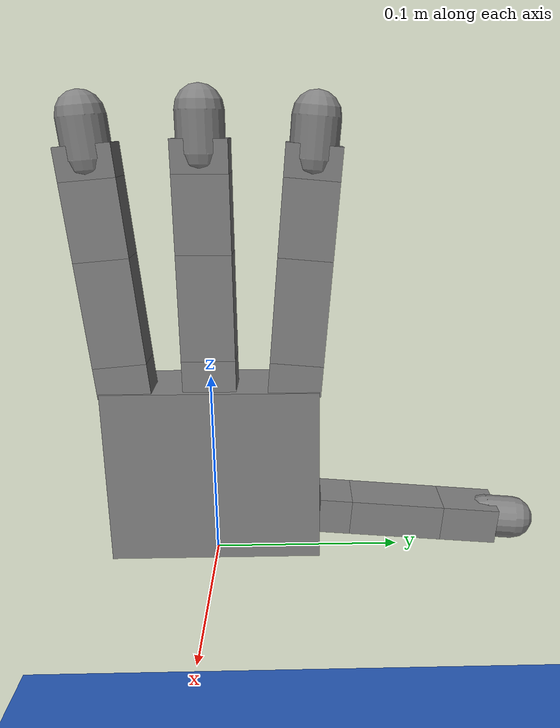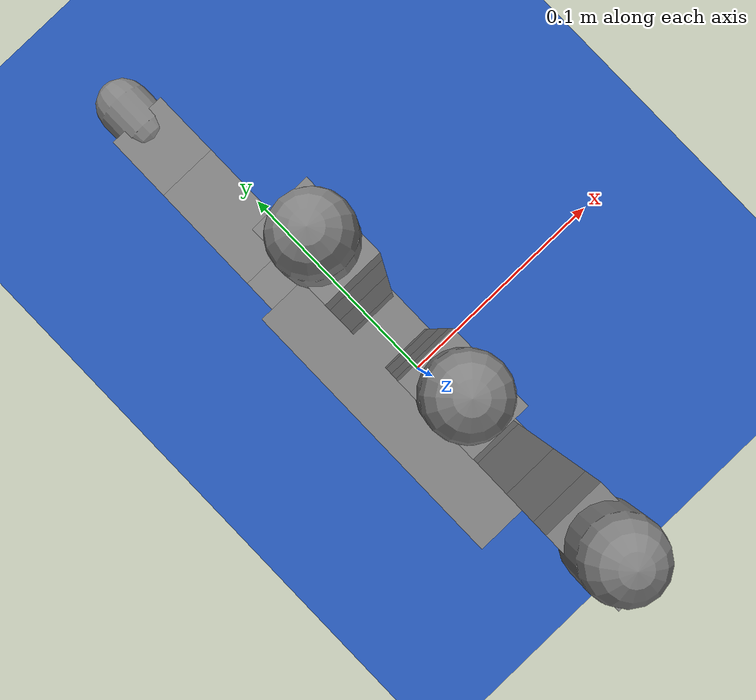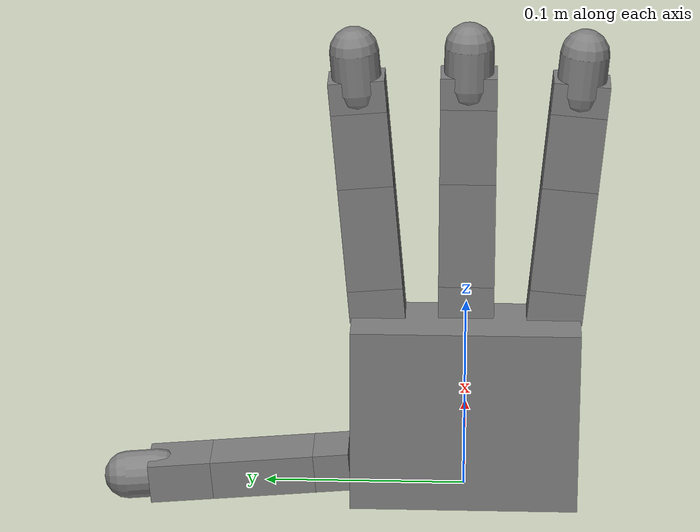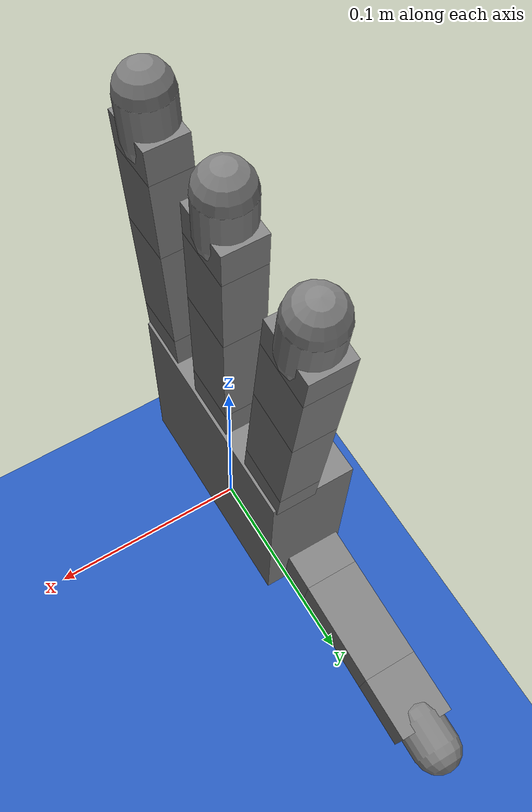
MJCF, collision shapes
<mujoco model="Allegro Custom Task">
  <include file="../common.xml"/>

  <size memory="1M"/>

  <asset>
    <mesh name="apple" file="apple.obj" />
  </asset>

  <custom>
    <text name="task_transition" data="ApplePass" />
    <numeric name="agent_planner" data="0" />
    <numeric name="agent_horizon" data="0.25" />
    <numeric name="agent_timestep" data="0.01" />
    <numeric name="agent_policy_width" data="0.0035" />
    <numeric name="sampling_spline_points" data="6" />
    <numeric name="sampling_exploration" data="0.1" />
    <numeric name="robust_xfrc" data="0.004" />
    <numeric name="gradient_spline_points" data="6" />
  </custom>

  <statistic extent="0.4" center="0.3 0.1 0"/>

  <visual>
    <quality shadowsize="8192"/>
    <global azimuth="180" elevation="-30"/>
  </visual>

  <default>
    <geom friction=".6"/>
  </default>

  <worldbody>
    <light pos="0 -0.1 0.5" dir="0 0.2 -1" diffuse="0.7 0.7 0.7" specular="0.3 0.3 0.3"
        directional="true" castshadow="true"/>
    <body name="mocap[object]" mocap="true">
        <geom type="mesh" mesh="apple" size="1 1 1" contype="0" conaffinity="0" rgba="0 1 0 1.0"/>
    </body>
    <geom name="floor" pos="0 0 -0.2" size="0 0 0.05" type="plane" material="blue_grid"/>
  </worldbody>

  <sensor>
    <user name="In Hand" dim="3" user="1 20 0 100 0.02 2"/>
    <framepos name="palm_position" objtype="site" objname="grasp_site"/>
  </sensor>

  <include file="right_hand.xml"/>

  <include file="./keyframes/apple_pass_1/apple_pass_1.xml" />

</mujoco>

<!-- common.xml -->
<mujoco>

    <visual>
        <headlight ambient=".4 .4 .4" diffuse=".8 .8 .8" specular="0.1 0.1 0.1"/>
        <map znear=".01"/>
        <quality shadowsize="2048"/>
        <global elevation="-15"/>
    </visual>

    <asset>
        <texture name="blue_grid" type="2d" builtin="checker" rgb1=".02 .14 .44" rgb2=".27 .55 1" width="300" height="300" mark="edge" markrgb="1 1 1"/>
        <material name="blue_grid" texture="blue_grid" texrepeat="1 1" texuniform="true" reflectance=".2"/>

        <texture name="grey_grid" type="2d" builtin="checker" rgb1=".26 .26 .26" rgb2=".6 .6 .6" width="300" height="300" mark="edge" markrgb="1 1 1"/>
        <material name="grey_grid" texture="grey_grid" texrepeat="1 1" texuniform="true" reflectance=".2"/>
        <texture name="skybox" type="skybox" builtin="gradient" rgb1=".66 .79 1" rgb2=".9 .91 .93" width="800" height="800"/>

        <material name="self" rgba=".7 .5 .3 1"/>
        <material name="self_default" rgba=".7 .5 .3 1"/>
        <material name="self_highlight" rgba="0 .5 .3 1"/>
        <material name="effector" rgba=".7 .4 .2 1"/>
        <material name="effector_default" rgba=".7 .4 .2 1"/>
        <material name="effector_highlight" rgba="0 .5 .3 1"/>
        <material name="decoration" rgba=".2 .6 .3 1"/>
        <material name="eye" rgba="0 .2 1 1"/>
        <material name="target" rgba=".6 .3 .3 1"/>
        <material name="target_default" rgba=".6 .3 .3 1"/>
        <material name="target_highlight" rgba=".6 .3 .3 .4"/>
        <material name="site" rgba=".5 .5 .5 .3"/>
    </asset>

    <size memory="1M"/>

    <statistic extent="0.4" center="0.3 0.1 0"/>

    <visual>
        <quality shadowsize="8192"/>
        <global azimuth="180" elevation="-30"/>
    </visual>

    <default>
        <geom friction="1.0"/>
    </default>

    <compiler angle="radian" autolimits="true"/>

    <asset>
        <mesh name="apple" file="../../shared_assets/apple/apple.obj" />
        <mesh name="apple_contact0" file="../../shared_assets/apple/contact0.stl"  />
        <mesh name="apple_contact1" file="../../shared_assets/apple/contact1.stl"  />

        <mesh name="doorknob" file="../../shared_assets/doorknob/doorknob.obj" />

        <mesh name="flashlight" file="../../shared_assets/flashlight/flashlight.obj" />
        <mesh name="flashlight_contact0" file="../../shared_assets/flashlight/contact0.stl"  />
        <mesh name="flashlight_contact1" file="../../shared_assets/flashlight/contact1.stl"  />

        <mesh name="hammer" file="../../shared_assets/hammer/hammer.obj" />
        <mesh name="hammer_contact0" file="../../shared_assets/hammer/contact0.stl"  />
        <mesh name="hammer_contact1" file="../../shared_assets/hammer/contact1.stl"  />

        <mesh name="phone" file="../../shared_assets/phone/phone.obj" />
        <mesh name="phone_contact0" file="../../shared_assets/phone/contact0.stl"  />
        <mesh name="phone_contact1" file="../../shared_assets/phone/contact1.stl"  />
        <mesh name="phone_contact2" file="../../shared_assets/phone/contact2.stl"  />

        <mesh name="stapler" file="../../shared_assets/stapler/stapler.obj" />
        <mesh name="stapler_contact0" file="../../shared_assets/stapler/contact0.stl"  />
        <mesh name="stapler_contact1" file="../../shared_assets/stapler/contact1.stl"  />
        <mesh name="stapler_contact2" file="../../shared_assets/stapler/contact2.stl"  />
        <mesh name="stapler_contact3" file="../../shared_assets/stapler/contact3.stl"  />
        <mesh name="stapler_contact4" file="../../shared_assets/stapler/contact4.stl"  />

        <mesh name="waterbottle" file="../../shared_assets/waterbottle/waterbottle.obj" />
        <mesh name="waterbottle_contact0" file="../../shared_assets/waterbottle/contact0.stl"  />
        <mesh name="waterbottle_contact1" file="../../shared_assets/waterbottle/contact1.stl"  />
    </asset>

</mujoco>

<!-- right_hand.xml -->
<mujoco model="allegro_right">

  <compiler angle="radian" meshdir="assets" autolimits="true"/>

  <default class="allegro_right">
    <joint axis="0 1 0" damping=".1"/>
    <position kp="1"/>
    <geom density="800"/>

    <default class="visual">
      <geom type="mesh" contype="0" conaffinity="0" group="2" material="black"/>
      <default class="palm_visual">
        <geom mesh="base_link"/>
      </default>
      <default class="base_visual">
        <geom mesh="link_0.0"/>
      </default>
      <default class="proximal_visual">
        <geom mesh="link_1.0"/>
      </default>
      <default class="medial_visual">
        <geom mesh="link_2.0"/>
      </default>
      <default class="distal_visual">
        <geom mesh="link_3.0"/>
      </default>
      <default class="fingertip_visual">
        <geom pos="0 0 0.0267" material="white" mesh="link_3.0_tip"/>
      </default>
      <default class="thumbtip_visual">
        <geom pos="0 0 0.0423" material="white" mesh="link_15.0_tip"/>
      </default>
    </default>

    <default class="collision">
      <geom group="3" type="box" mass="0"/>
      <default class="palm_collision">
        <geom size="0.0204 0.0565 0.0475" pos="-0.0093 0 -0.0475"/>
      </default>
      <default class="base_collision">
        <geom size="0.0098 0.01375 0.0082" pos="0 0 0.0082"/>
        <default class="thumb_base_collision">
          <geom size="0.0179 0.017 0.02275" pos="-0.0179 0.009 0.0145"/>
        </default>
      </default>
      <default class="proximal_collision">
        <geom size="0.0098 0.01375 0.027" pos="0 0 0.027"/>
        <default class="thumb_proximal_collision">
          <geom size="0.0098 0.01375 0.00885" pos="0 0 0.00885"/>
        </default>
      </default>
      <default class="medial_collision">
        <geom size="0.0098 0.01375 0.0192" pos="0 0 0.0192"/>
        <default class="thumb_medial_collision">
          <geom size="0.0098 0.01375 0.0257" pos="0 0 0.0257"/>
        </default>
      </default>
      <default class="distal_collision">
        <geom size="0.0098 0.01375 0.008" pos="0 0 0.008"/>
        <default class="thumb_distal_collision">
          <geom size="0.0098 0.01375 0.0157" pos="0 0 0.0157"/>
        </default>
      </default>
      <default class="fingertip_collision">
        <geom type="capsule" size="0.012 0.01" pos="0 0 0.019"/>
        <default class="thumbtip_collision">
          <geom type="capsule" size="0.012 0.008" pos="0 0 0.035"/>
        </default>
      </default>
    </default>

    <default class="base">
      <joint axis="0 0 1" range="-0.47 0.47"/>
      <position ctrlrange="-0.47 0.47"/>
    </default>
    <default class="proximal">
      <joint range="-0.196 1.61"/>
      <position ctrlrange="-0.196 1.61"/>
    </default>
    <default class="medial">
      <joint range="-0.174 1.709"/>
      <position ctrlrange="-0.174 1.709"/>
    </default>
    <default class="distal">
      <joint range="-0.227 1.618"/>
      <position ctrlrange="-0.227 1.618"/>
    </default>
    <default class="thumb_base">
      <joint axis="1 0 0" range="0.263 1.396"/>
      <position ctrlrange="0.263 1.396"/>
    </default>
    <default class="thumb_proximal">
      <joint axis="0 0 1" range="-0.105 1.163"/>
      <position ctrlrange="-0.105 1.163"/>
    </default>
    <default class="thumb_medial">
      <joint range="-0.189 1.644"/>
      <position ctrlrange="-0.189 1.644"/>
    </default>
    <default class="thumb_distal">
      <joint range="-0.162 1.719"/>
      <position ctrlrange="-0.162 1.719"/>
    </default>
  </default>

  <asset>
    <material name="black" rgba="0.2 0.2 0.2 1"/>
    <material name="white" rgba="0.9 0.9 0.9 1"/>

    <mesh file="base_link.stl"/>
    <mesh file="link_0.0.stl"/>
    <mesh file="link_1.0.stl"/>
    <mesh file="link_2.0.stl"/>
    <mesh file="link_3.0.stl"/>
    <mesh file="link_3.0_tip.stl"/>
    <mesh file="link_12.0_right.stl"/>
    <mesh file="link_13.0.stl"/>
    <mesh file="link_14.0.stl"/>
    <mesh file="link_15.0.stl"/>
    <mesh file="link_15.0_tip.stl"/>
  </asset>

  <worldbody>
    <body name="wrist">
      <freejoint name="root"/>
      <body name="palm" childclass="allegro_right" pos="0 0 0.09420">
        <inertial mass="0.4154" pos="0 0 0.0475" diaginertia="1e-4 1e-4 1e-4"/>
        <geom class="palm_visual" mesh="base_link"/>
        <geom class="palm_collision"/>
        <site name="grasp_site" pos="0 0 0" group="4"/>
        <!-- Thumb -->
        <body name="th_base" pos="-0.0182 0.019333 -0.045987" quat="0.477714 -0.521334 -0.521334 -0.477714">
          <joint name="thj0" class="thumb_base"/>
          <geom class="visual" mesh="link_12.0_right"/>
          <geom class="thumb_base_collision"/>
          <body name="th_proximal" pos="-0.027 0.005 0.0399">
            <joint name="thj1" class="thumb_proximal"/>
            <geom class="visual" mesh="link_13.0"/>
            <geom class="thumb_proximal_collision"/>
            <body name="th_medial" pos="0 0 0.0177">
              <joint name="thj2" class="thumb_medial"/>
              <geom class="visual" mesh="link_14.0"/>
              <geom class="thumb_medial_collision"/>
              <body name="th_distal" pos="0 0 0.0514">
                <joint name="thj3" class="thumb_distal"/>
                <geom class="visual" mesh="link_15.0"/>
                <geom class="thumb_distal_collision"/>
                <body name="th_tip">
                  <geom class="thumbtip_visual"/>
                  <geom class="thumbtip_collision"/>
                </body>
              </body>
            </body>
          </body>
        </body>
        <!-- First finger -->
        <body name="ff_base" pos="0 0.0435 -0.001542" quat="0.999048 -0.0436194 0 0">
          <joint name="ffj0" class="base"/>
          <geom class="base_visual"/>
          <geom class="base_collision"/>
          <body name="ff_proximal" pos="0 0 0.0164">
            <joint name="ffj1" class="proximal"/>
            <geom class="proximal_visual"/>
            <geom class="proximal_collision"/>
            <body name="ff_medial" pos="0 0 0.054">
              <joint name="ffj2" class="medial"/>
              <geom class="medial_visual"/>
              <geom class="medial_collision"/>
              <body name="ff_distal" pos="0 0 0.0384">
                <joint name="ffj3" class="distal"/>
                <geom class="distal_visual"/>
                <geom class="distal_collision"/>
                <body name="ff_tip">
                  <geom class="fingertip_visual"/>
                  <geom class="fingertip_collision"/>
                </body>
              </body>
            </body>
          </body>
        </body>
        <!-- Middle finger -->
        <body name="mf_base" pos="0 0 0.0007">
          <joint name="mfj0" class="base"/>
          <geom class="base_visual"/>
          <geom class="base_collision"/>
          <body name="mf_proximal" pos="0 0 0.0164">
            <joint name="mfj1" class="proximal"/>
            <geom class="proximal_visual"/>
            <geom class="proximal_collision"/>
            <body name="mf_medial" pos="0 0 0.054">
              <joint name="mfj2" class="medial"/>
              <geom class="medial_visual"/>
              <geom class="medial_collision"/>
              <body name="mf_distal" pos="0 0 0.0384">
                <joint name="mfj3" class="distal"/>
                <geom class="distal_visual"/>
                <geom class="distal_collision"/>
                <body name="mf_tip">
                  <geom class="fingertip_visual"/>
                  <geom class="fingertip_collision"/>
                </body>
              </body>
            </body>
          </body>
        </body>
        <!-- Ring finger -->
        <body name="rf_base" pos="0 -0.0435 -0.001542" quat="0.999048 0.0436194 0 0">
          <joint name="rfj0" class="base"/>
          <geom class="base_visual"/>
          <geom class="base_collision"/>
          <body name="rf_proximal" pos="0 0 0.0164">
            <joint name="rfj1" class="proximal"/>
            <geom class="proximal_visual"/>
            <geom class="proximal_collision"/>
            <body name="rf_medial" pos="0 0 0.054">
              <joint name="rfj2" class="medial"/>
              <geom class="medial_visual"/>
              <geom class="medial_collision"/>
              <body name="rf_distal" pos="0 0 0.0384">
                <joint name="rfj3" class="distal"/>
                <geom class="distal_visual"/>
                <geom class="distal_collision"/>
                <body name="rf_tip">
                  <geom class="fingertip_visual"/>
                  <geom class="fingertip_collision"/>
                </body>
              </body>
            </body>
          </body>
        </body>
      </body>
    </body>
  </worldbody>

  <contact>
    <exclude body1="palm" body2="ff_base"/>
    <exclude body1="palm" body2="mf_base"/>
    <exclude body1="palm" body2="rf_base"/>
    <exclude body1="palm" body2="th_base"/>
    <exclude body1="palm" body2="th_proximal"/>
  </contact>

  <actuator>
    <position name="ffa0" joint="ffj0" class="base"/>
    <position name="ffa1" joint="ffj1" class="proximal"/>
    <position name="ffa2" joint="ffj2" class="medial"/>
    <position name="ffa3" joint="ffj3" class="distal"/>
    <position name="mfa0" joint="mfj0" class="base"/>
    <position name="mfa1" joint="mfj1" class="proximal"/>
    <position name="mfa2" joint="mfj2" class="medial"/>
    <position name="mfa3" joint="mfj3" class="distal"/>
    <position name="rfa0" joint="rfj0" class="base"/>
    <position name="rfa1" joint="rfj1" class="proximal"/>
    <position name="rfa2" joint="rfj2" class="medial"/>
    <position name="rfa3" joint="rfj3" class="distal"/>
    <position name="tha0" joint="thj0" class="thumb_base"/>
    <position name="tha1" joint="thj1" class="thumb_proximal"/>
    <position name="tha2" joint="thj2" class="thumb_medial"/>
    <position name="tha3" joint="thj3" class="thumb_distal"/>
  </actuator>
</mujoco>

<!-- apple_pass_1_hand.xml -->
<mujoco>
  <keyframe>
    <key name="apple_pass_1_hand_1" qpos="0.0 0.0 0.0 -0.21446934505968462 -0.5963626900904009 0.23384177003807732 0.7373414870216305 -0.6981317007977318 0.1738727076847623 1.5796961335703645 0.2645511738653996 -0.3799143378832152 0.02777268745157773 1.7088291870089631 0.4574843166285432 -0.010874468678345973 0.7118040609866697 0.5544312715370631 0.45999071437897354 0.46951671772781295 0.24983054386078968 1.7090264035528475 0.45702948415392664 0.0 0.0 0.0 0.0 0.0 0.0 0.0" />
    <key name="apple_pass_1_hand_2" qpos="6.047185247692877e-05 0.0009280429031792714 0.00043801865553461106 -0.21134606244618515 -0.5964732195487455 0.22943745391529555 0.7395343095425078 -0.6981317007977318 0.17099475882786164 1.5742236283009297 0.2603126081132073 -0.36111798282413493 0.01704171532571863 1.6977899256252778 0.4575910823950821 -0.008815339661403436 0.7274438478892347 0.5455583780777463 0.45675039482059465 0.4676647176424941 0.2608649291125418 1.708200352732607 0.45620186266521856 0.0 0.0 0.0 0.0 0.0 0.0 0.0" />
    <key name="apple_pass_1_hand_3" qpos="8.53584819456854e-05 0.0016524570468419153 0.0007870950406476673 -0.20892172304612822 -0.5967195461621735 0.22599108137239562 0.7410840222320151 -0.6981317007977318 0.16981241394301685 1.569813966954911 0.25727193549372984 -0.34697016730501584 0.008894176780253563 1.690313988160538 0.45759631499858366 -0.007480391290807075 0.7394671169046424 0.539899846137039 0.4540186964589231 0.4657344438564608 0.26956063543967435 1.7060944666679032 0.4553745773947498 0.0 0.0 0.0 0.0 0.0 0.0 0.0" />
    <key name="apple_pass_1_hand_4" qpos="7.932104925656436e-05 0.0021957363864075763 0.0010600818971255865 -0.2071216726985564 -0.597069875774028 0.22341612145332987 0.7420872002780332 -0.6981317007977318 0.17008516905022006 1.5663599027607207 0.25529068274643746 -0.33684814243077116 0.0030316792644558594 1.6858805939514945 0.4575191406020853 -0.006777101066332214 0.7482344063747784 0.5369144994898117 0.4517529730439152 0.4637579888291299 0.276058655811956 1.7029291771111084 0.4545666300992545 0.0 0.0 0.0 0.0 0.0 0.0 0.0" />
    <key name="apple_pass_1_hand_5" qpos="4.702070221962451e-05 0.002580375178177663 0.001269832123157899 -0.2058695427843518 -0.5975029383091053 0.2216235141487846 0.7426243923021185 -0.6981317007977318 0.17157252077103843 1.5637541869775502 0.2542303756316204 -0.33012915386894154 -0.0008441729232971812 1.6839689603174908 0.4573786852953987 -0.006612946214273065 0.7541062593876932 0.5360611607150602 0.4499105769872534 0.46176744371963213 0.28049998675980276 1.698924913446891 0.45379702201770306 0.0 0.0 0.0 0.0 0.0 0.0 0.0" />
    <key name="apple_pass_1_hand_6" qpos="-6.881402116243329e-06 0.002828867257846923 0.0014291984049601414 -0.20508797109048554 -0.5980054439781044 0.22052257721824922 0.7427638965536488 -0.6981317007977318 0.17403396529349538 1.5618895735683793 0.25395254138932966 -0.32619045499264343 -0.0030317709941278205 1.6840583077537377 0.457194075245434 -0.00689540444877044 0.7574432122700863 0.5367986544066574 0.4484488624979049 0.45979490131834083 0.28302561973659085 1.6943021078173521 0.45308475505501533 0.0 0.0 0.0 0.0 0.0 0.0 0.0" />
    <key name="apple_pass_1_hand_7" qpos="-7.772405303718699e-05 0.0029637066111791732 0.0015510334595350006 -0.20469905454693454 -0.5985698211167791 0.22002161370524145 0.7425651189076683 -0.6981317007977318 0.17722899639377926 1.5606588158375518 0.2543187060266046 -0.3244092958370172 -0.0038295083005582767 1.685627853440747 0.45698443674737355 -0.007531952644106963 0.7586058045992957 0.5385858023815392 0.44732518360378687 0.45787245500884166 0.2837765487298507 1.6892811948557425 0.452448831234465 0.0 0.0 0.0 0.0 0.0 0.0 0.0" />
    <key name="apple_pass_1_hand_8" qpos="-0.0001608461858394472 0.0030073874439027204 0.0016481902263782988 -0.20462463673855485 -0.5991922438992279 0.2200283317396653 0.7420814956071081 -0.6981317007977318 0.18091711443313005 1.5599546649177078 0.2551903965244533 -0.3241629238525581 -0.003535779207885436 1.688156818291593 0.45676889567078766 -0.008430069069064655 0.7579545774042845 0.5408814304819267 0.44649689225331357 0.45603219440998405 0.2828937685737287 1.6840825991452675 0.45190825135079027 0.0 0.0 0.0 0.0 0.0 0.0 0.0" />
    <key name="apple_pass_1_hand_9" qpos="-0.00025158659936075356 0.0029824036748302696 0.001733521402156768 -0.20478649975222102 -0.5998709477628003 0.22045014989798176 0.741362979220942 -0.6976255416888888 0.18485781358872866 1.5596698744925386 0.25642913926568844 -0.3248285902814069 -0.002448976257499856 1.6911244202842846 0.45656657830074765 -0.009497230799181288 0.7558500689586773 0.5431443610341004 0.4459213426814646 0.4543062129485959 0.2805182721415647 1.678926755130955 0.4514820174833885 0.0 0.0 0.0 0.0 0.0 0.0 0.0" />
    <key name="apple_pass_1_hand_10" qpos="-0.00034528413372536537 0.0029112493456320276 0.0018198797740600625 -0.20510650293669777 -0.600604840713978 0.22119443285128407 0.7404580816221904 -0.6960540868394599 0.1888105899130319 1.559697197245564 0.2578964606770858 -0.32578354456377323 -0.0008674929341668299 1.69400987799586 0.45639661079136284 -0.010640915220494254 0.7526528189676879 0.5448334172486008 0.44555588828271625 0.4527266027747585 0.27679105336242416 1.6740340940813383 0.45118913126887006 0.0 0.0 0.0 0.0 0.0 0.0 0.0" />
    <key name="apple_pass_1_hand_11" qpos="-0.000437277629057764 0.0028164184979784235 0.0019201181292778369 -0.20550670013057662 -0.6013924052697162 0.2221686924984342 0.7394154739785224 -0.6946778367833035 0.19253493945849662 1.5599293858603038 0.25945388718542134 -0.326405036139867 0.0009102772773483688 1.6962924100033572 0.4562781192967428 -0.011768599719040963 0.7487233671365303 0.5454074223359692 0.4453578824515451 0.4513254560385536 0.2718531061653728 1.6696250472649512 0.4510485943438459 0.0 0.0 0.0 0.0 0.0 0.0 0.0" />
    <key name="apple_pass_1_hand_12" qpos="-0.0005229058725955138 0.0027204052317961747 0.0020470891604467134 -0.20590944472656128 -0.6022308926288601 0.22328076407952435 0.7382851433747731 -0.6936558991748137 0.1957903563549282 1.5602591927961142 0.2609629442768551 -0.32607031511703066 0.002585939895157807 1.6974512346070143 0.45623022997505863 -0.012787761070181343 0.7444222560253587 0.5443252008736394 0.4452846785987842 0.4501348655926337 0.2658454287261912 1.6659200480944258 0.451079408264626 0.0 0.0 0.0 0.0 0.0 0.0 0.0" />
    <key name="apple_pass_1_hand_13" qpos="-0.0005975077748147095 0.0026457034879265873 0.0022136456891448386 -0.20623748391076147 -0.60311581135793 0.22443896167621888 0.7371191021822218 -0.6931473798577589 0.19833633966231332 1.5605793710433855 0.2622851596536213 -0.32415663274010337 0.0038611031503891736 1.6969655731514441 0.456272068846527 -0.01360587759400226 0.7401100222632742 0.5410455779323478 0.44529363002301053 0.4491869225462473 0.258909011849449 1.6631395243412577 0.45130057448679806 0.0 0.0 0.0 0.0 0.0 0.0 0.0" />
    <key name="apple_pass_1_hand_14" qpos="-0.0006568731457208266 0.002613171492280575 0.0024310570187089375 -0.20641956236170417 -0.6040382304982992 0.22555702773653932 0.7359706567585041 -0.6932954755086541 0.19995195899987858 1.5607890700453875 0.26329171616896463 -0.3201019412636888 0.004460330132074832 1.6943671189317766 0.456419649057757 -0.014140140999854162 0.7361270739706613 0.535092800850062 0.44534391635982623 0.4485088519321303 0.2511933701783677 1.661483967368749 0.4517272114387026 0.0 0.0 0.0 0.0 0.0 0.0 0.0" />
    <key name="apple_pass_1_hand_15" qpos="-0.0007017130412102501 0.0026258133694680996 0.0026933047661839016 -0.20644537636602336 -0.6049606752334189 0.22660211442769435 0.7348839158228427 -0.694069716776772 0.20062990106338346 1.5608572543829005 0.2639591772863785 -0.3140068373417376 0.004358741674811543 1.6897603759006454 0.4566550024336794 -0.014413764685858414 0.7325941613164179 0.5267053340827763 0.4454146484963802 0.44807476550842773 0.24294116993356837 1.6609362517819628 0.4523320437116139 0.0 0.0 0.0 0.0 0.0 0.0 0.0" />
    <key name="apple_pass_1_hand_16" qpos="-0.0007357682337276739 0.002675642922898902 0.002983730789289263 -0.20634255653647507 -0.6058289135311022 0.2275746118468355 0.7338963638923945 -0.6953327360182767 0.20049435548565822 1.560795864959146 0.26432898085960027 -0.30637977576538145 0.0036856935544676817 1.6836024196199293 0.45693924474533093 -0.014515227730421612 0.7294967935681332 0.5165612305848601 0.4454972065617249 0.4478260763295163 0.23445235703577855 1.6613452874032564 0.4530617038602282 0.0 0.0 0.0 0.0 0.0 0.0 0.0" />
    <key name="apple_pass_1_hand_17" qpos="-0.0007628236133170319 0.002754512983645041 0.0032855198175290035 -0.20613999794143265 -0.6065888223951027 0.2284760677873713 0.733045011061701 -0.6969455962024088 0.1996714344858249 1.5606174715100587 0.264443511214013 -0.29773521498056155 0.002572800279586038 1.6763555125300411 0.45723318438971394 -0.014533963091059239 0.7268185186351623 0.5053450237207089 0.44558314983324215 0.4477037208940095 0.2260277594532711 1.6625580244323028 0.45386243919360636 0.0 0.0 0.0 0.0 0.0 0.0 0.0" />
    <key name="apple_pass_1_hand_18" qpos="-0.0007866642057138273 0.00285427656458781 0.003581857723234272 -0.20586710988314524 -0.6071866860908203 0.22930850348911216 0.7323664871701823 -0.6981317007977318 0.19828725011824494 1.5603346435990377 0.2643451542648223 -0.2885875838432371 0.0011516739200443788 1.6684818933251482 0.45749763089811846 -0.014559404118914581 0.7245428720134968 0.49374120731557963 0.44566403791547177 0.4476486346810017 0.21796817161638013 1.6644214142479223 0.4546804998717404 0.0 0.0 0.0 0.0 0.0 0.0 0.0" />
    <key name="apple_pass_1_hand_19" qpos="-0.0008110750198387917 0.0029667867878859777 0.0038559303502221365 -0.20555351633174232 -0.6075691529850474 0.23007410419947574 0.731897112196446 -0.6981317007977318 0.1964679115016973 1.559959950243256 0.26407629481376627 -0.2794513085781523 -0.0004460750664346982 1.660443797421517 0.45769339364757594 -0.014680984200203629 0.7226533913049995 0.48243427316741017 0.445731430386513 0.44760175352142567 0.21057438986455423 1.6667824116320502 0.45546213614523906 0.0 0.0 0.0 0.0 0.0 0.0 0.0" />
    <key name="apple_pass_1_hand_20" qpos="-0.0008398409709574617 0.003083896320692947 0.004090922470765035 -0.20522866622839997 -0.6076831131480205 0.23077482630880713 0.7316730199310224 -0.6981317007977318 0.19433953525867814 1.5595059619979845 0.263679318856429 -0.27084085157807114 -0.0020888297530753885 1.652703492176411 0.45778128126647605 -0.014988136239832767 0.7211336212602178 0.4721087576815748 0.4457768865634078 0.44750401338613666 0.2041472393023939 1.6694879616796836 0.4561535951872379 0.0 0.0 0.0 0.0 0.0 0.0 0.0" />
    <key name="apple_pass_1_hand_21" qpos="-0.0008767471199998544 0.0031974584164486952 0.004270020159099275 -0.2049213475785757 -0.6074754979331826 0.23141192882449532 0.7317303327832865 -0.6981317007977318 0.1920282279076715 1.5589852472732804 0.26319661072102857 -0.26327062972222315 -0.003644981458057517 1.6457232044900532 0.4577221030566712 -0.015570294419830162 0.7199670976852884 0.46344914188467023 0.4457919660435997 0.447296349764808 0.19898750941507937 1.6723850224687884 0.45670112792953144 0.0 0.0 0.0 0.0 0.0 0.0 0.0" />
    <key name="apple_pass_1_hand_22" qpos="-0.0009255783495546455 0.003299325739555714 0.004376408435870172 -0.20465911421375088 -0.6068929992648486 0.23198540378344554 0.7321053932624667 -0.6981317007977318 0.1896601073577465 1.5584103770062832 0.26267055696239594 -0.2572551013079053 -0.004982913363388484 1.639965198953379 0.45747666831326045 -0.01651689044062061 0.7191373634401161 0.457139955258932 0.44576822828093704 0.4469196990487658 0.19539601946482676 1.6753205376924751 0.4570509821574716 0.0 0.0 0.0 0.0 0.0 0.0 0.0" />
    <key name="apple_pass_1_hand_23" qpos="-0.0009901196767115872 0.003381351412861111 0.0043932730828026845 -0.2044676088569621 -0.605881719451185 0.23249332890894456 0.7328350366733493 -0.6981317007977318 0.1873612824060386 1.5577939201186985 0.2621435422424575 -0.25330869358372926 -0.005971014984149872 1.635891711674237 0.4570057862465977 -0.017917357989540708 0.7186279565992247 0.45386569133308363 0.4456972328193176 0.446314996963825 0.19367356725168183 1.678141462483151 0.4571494079686129 0.0 0.0 0.0 0.0 0.0 0.0 0.0" />
    <key name="apple_pass_1_hand_24" qpos="-0.0010741562007299255 0.0034353884554343406 0.004303799413386322 -0.20436978605701211 -0.6043867616477154 0.2329311132739132 0.7339568988441854 -0.6981317007977318 0.18525786221212098 1.5571484453147229 0.26165795121811364 -0.2519458446204531 -0.006477674005701774 1.6339649875710334 0.45627026488787753 -0.019861133127816694 0.7184224169125507 0.4543108595094413 0.4455705389554667 0.4454231780430213 0.19412096035134058 1.6806947513738808 0.4569426541454611 0.0 0.0 0.0 0.0 0.0 0.0 0.0" />
    <key name="apple_pass_1_hand_25" qpos="-0.0011814725237504486 0.0034532896911139144 0.004091173516489688 -0.2043850186681562 -0.602351790221108 0.2332906361391097 0.73550973076585 -0.6981317007977318 0.18347596620620393 1.5564865247285502 0.2612561709038263 -0.2536809919636515 -0.0063712769519301314 1.6346472752195065 0.4552309168756904 -0.022437640173394214 0.7185042844391027 0.4591599559416797 0.4453797068091319 0.44418518233769977 0.1970389978005856 1.6828273465100023 0.45637697144370887 0.0 0.0 0.0 0.0 0.0 0.0 0.0" />
    <key name="apple_pass_1_hand_26" qpos="-0.0013157712869947824 0.003427045505815185 0.0037389851294706844 -0.2045275980228514 -0.5997201494706859 0.2335592326335101 0.7375325679707351 -0.6981317007977318 0.1821400556483273 1.555820724970859 0.2609801279679603 -0.2590179225909765 -0.0055222789496082265 1.6383902616383803 0.45384948656581664 -0.025734084307023338 0.7188564747088707 0.4690833790179779 0.4451165184473191 0.4425430047820583 0.2027213823893618 1.6843877181269193 0.45539973137072165 0.0 0.0 0.0 0.0 0.0 0.0 0.0" />
    <key name="apple_pass_1_hand_27" qpos="-0.0014768378683608363 0.003355134150601291 0.003249976116740383 -0.20478441215658424 -0.5965097990740789 0.23371768527912606 0.7400104375845329 -0.6981317007977318 0.18129706462974626 1.555163640964126 0.26085018397850535 -0.267956768619483 -0.003898856271629087 1.6451466041924114 0.4521321656866818 -0.029731754410575423 0.7194323908564956 0.48408376232282835 0.4447833196282313 0.4404889907549423 0.2111255069295592 1.6852955559505571 0.4540114702226924 0.0 0.0 0.0 0.0 0.0 0.0 0.0" />
    <key name="apple_pass_1_hand_28" qpos="-0.001658928090227274 0.0032451947374825263 0.0026539275195680556 -0.20511034509575687 -0.5928473604203557 0.23374412863070906 0.7428495378661731 -0.6981317007977318 0.18088443769432552 1.5545278985419861 0.2608562459618078 -0.2797865442137315 -0.0016071624842147545 1.6541643601437086 0.45014788982344717 -0.034262424952821 0.7201437666043733 0.5032209461164718 0.4443973690192248 0.4380865617636928 0.22173394606284585 1.6855711384247405 0.4522877833298418 0.0 0.0 0.0 0.0 0.0 0.0 0.0" />
    <key name="apple_pass_1_hand_29" qpos="-0.001855879590591858 0.0031055586697017468 0.001982664450586036 -0.20546224447225567 -0.5888704487824563 0.23362089299100766 0.745947812521262 -0.6946665987615226 0.18083134997340058 1.553926127520566 0.2609859203714783 -0.2937425155631057 0.0012362196801839623 1.6646383412348533 0.44797033953888865 -0.03914656435007707 0.7208991865241161 0.5254835014023714 0.44397705278962935 0.4354045150843125 0.2339933782861219 1.6852423424199474 0.45030994059244445 0.0 0.0 0.0 0.0 0.0 0.0 0.0" />
    <key name="apple_pass_1_hand_30" qpos="-0.00206153158012079 0.0029445562052667906 0.0012680066160875025 -0.20580341816713837 -0.584720153276794 0.23333672437916048 0.7492004194330701 -0.6901343923530397 0.18106697674454228 1.5533709530227189 0.26122681485632293 -0.3090600621283308 0.004514730670616586 1.6757634443387595 0.4456731779628008 -0.04420468003399527 0.7216072412910893 0.5498601792535033 0.44354075374221724 0.43251162649529334 0.24735058115967154 1.6843370414003744 0.44815919595506376 0.0 0.0 0.0 0.0 0.0 0.0 0.0" />
    <key name="apple_pass_1_hand_31" qpos="-0.0022697217276208548 0.002770518680650147 0.0005417789736135159 -0.20610500079971747 -0.580541246802335 0.23288810736305818 0.7524996470799116 -0.6851390943350678 0.1815204939867281 1.5528750049699187 0.261566536177014 -0.32497445465932145 0.008111789044972357 1.6867344839535268 0.4433300852488373 -0.049257241110568034 0.7221765154725625 0.5753395575243748 0.4431068579804834 0.4294766926313238 0.2612522367746166 1.6828831106924023 0.44591681875956307 0.0 0.0 0.0 0.0 0.0 0.0 0.0" />
    <key name="apple_pass_1_hand_32" qpos="-0.0024742876753484078 0.0025917775686821187 -0.00016419339826567736 -0.20634664314555776 -0.576481869088107 0.23227991120891908 0.7557352448602745 -0.6798009499604722 0.18212107539967065 1.5524509126640982 0.261992690060436 -0.34072095766262583 0.011910810028943791 1.6967462761888548 0.4410147420311191 -0.054124716743892375 0.7225155950875346 0.600910202534587 0.4426937515827836 0.4263685116129715 0.27514502152677706 1.6809084313614095 0.44366407930633794 0.0 0.0 0.0 0.0 0.0 0.0 0.0" />
    <key name="apple_pass_1_hand_33" qpos="-0.0026690686737952385 0.0024166629228365988 -0.0008180909747994569 -0.2065164623354912 -0.5726928532288145 0.23152530191339488 0.7587950192370694 -0.6742401619963084 0.1827978996798374 1.5521113021574244 0.26249288570607643 -0.35553495996401707 0.015795239069874373 1.7049937155002608 0.4388008107187398 -0.058627614278463094 0.7225330686337783 0.6255608826594731 0.44231981738959925 0.4232558569899104 0.2884757215193883 1.678440868263099 0.44148223010215415 0.0 0.0 0.0 0.0 0.0 0.0 0.0" />
    <key name="apple_pass_1_hand_34" qpos="-0.0028479023476845056 0.002253506214534573 -0.0013880885828407852 -0.20661020342792402 -0.5693268769944377 0.2306448991297782 0.7615655332777649 -0.6685769749560195 0.18348014081893219 1.551868802956253 0.26305472905065247 -0.3686517246311978 0.019648491769216063 1.7090264035528475 0.4367619721147089 -0.06258640215964952 0.7221375214087703 0.6482801631350465 0.4420034415576905 0.42020752678108236 0.3006910124017015 1.675508301137446 0.4394525415265522 0.0 0.0 0.0 0.0 0.0 0.0 0.0" />
    <key name="apple_pass_1_hand_35" qpos="-0.0030046264885567053 0.002110638790107977 -0.0018423619268881364 -0.20662959094204697 -0.5665373182040359 0.22966511651388943 0.7639329901803973 -0.6629316344242034 0.1840969727519951 1.5517360435510954 0.2636658253860091 -0.37930653248599394 0.02335398405454403 1.7090264035528475 0.43497190519046103 -0.06582155452453421 0.7212375430304312 0.6680566294009187 0.4417630096417219 0.4172923183325564 0.3112375814908157 1.6721386145886457 0.4376562823673804 0.0 0.0 0.0 0.0 0.0 0.0 0.0" />
    <key name="apple_pass_1_hand_36" qpos="-0.003133080096676677 0.001996390890663502 -0.0021490901657239547 -0.20657984450855604 -0.5644769919403032 0.22861567775844277 0.7657841505906839 -0.6574243415611832 0.18457757426048915 1.5517256515178832 0.2643137848789416 -0.3867347457229991 0.026795160884017045 1.7090264035528475 0.43350427510245143 -0.06815357018004387 0.7197417155158682 0.6838790195270321 0.44161690538531767 0.41457900620331484 0.319562197388198 1.668359666176072 0.436174707518942 0.0 0.0 0.0 0.0 0.0 0.0 0.0" />
    <key name="apple_pass_1_hand_37" qpos="-0.0032271008977098337 0.0019190939264861484 -0.0022764486596003053 -0.2064663681055235 -0.5632968335078923 0.227526345048579 0.7670072219413135 -0.6521753421554012 0.18485111901579504 1.5518502556506277 0.2649862129338987 -0.39017163772581737 0.02985543764638912 1.7042364975148785 0.43243276156901445 -0.06940292113613034 0.7175586270443011 0.6947359099347798 0.4415835145657859 0.41213638817748927 0.3251115423235886 1.6641993393972117 0.43508908648578687 0.0 0.0 0.0 0.0 0.0 0.0 0.0" />
    <key name="apple_pass_1_hand_38" qpos="-0.003280527330153049 0.0018870783545550385 -0.002192616665231295 -0.20629064452095194 -0.5631443553436332 0.2264228432514795 0.7674928671210242 -0.6473048772074314 0.18484678602635324 1.5521224819188444 0.265670714593441 -0.38885256350264363 0.03241823834549988 1.6915847463566667 0.43183103691725305 -0.06939010021462895 0.7145968818162342 0.699615977093486 0.4416812208341995 0.41003325749396236 0.32733235575496555 1.659685524591785 0.434480681057115 0.0 0.0 0.0 0.0 0.0 0.0 0.0" />
    <key name="apple_pass_1_hand_39" qpos="-0.003290018158465191 0.0019041421429835115 -0.0018819268389325128 -0.20605237988455782 -0.5640956555067734 0.22532418812028088 0.7671815420291535 -0.6429164692390335 0.18451911217732045 1.55254366458736 0.26635405320553895 -0.38233171058996396 0.034404035971420194 1.6727415144466073 0.43174679941231275 -0.06801145892308438 0.7108356868215897 0.6978926121330556 0.4419208344990753 0.4083246880698085 0.32589687287369373 1.6548688887805538 0.4344021734473748 0.0 0.0 0.0 0.0 0.0 0.0 0.0" />
    <key name="apple_pass_1_hand_40" qpos="-0.0032618684145534482 0.0019585951950671365 -0.0013839169668614648 -0.20576394379634505 -0.565995431158214 0.22424552771404338 0.7661751200878635 -0.639056676364397 0.18390929156146496 1.5530765404288496 0.26702009190694315 -0.37125288345087726 0.0358598247105883 1.648685345182894 0.4321390048097698 -0.06542258743382313 0.7064956277844346 0.6902537525339532 0.4422872814541485 0.40701894243046766 0.32124785582608695 1.6498780925685286 0.43480859968019714 0.0 0.0 0.0 0.0 0.0 0.0 0.0" />
    <key name="apple_pass_1_hand_41" qpos="-0.003204430116037771 0.002035441550936934 -0.0007499073730434791 -0.2054362550056402 -0.5686389332900064 0.22319724036463204 0.7646101624812961 -0.6357598770685271 0.18307701416889105 1.5536756092043675 0.26765207776649574 -0.3564924481086406 0.0368596142959847 1.6206892605738623 0.4329476649910022 -0.061834407822565024 0.7018487969503767 0.6776679332050494 0.44275996322851174 0.4061142824326824 0.31399253707838815 1.6448584240431023 0.4356341515282293 0.0 0.0 0.0 0.0 0.0 0.0 0.0" />
    <key name="apple_pass_1_hand_42" qpos="-0.0031260555055951933 0.0021196850338156548 -3.1220326971892476e-05 -0.20507932744933902 -0.5718230551194644 0.22218902826194256 0.762622382838835 -0.6330604560847652 0.18208197275269108 1.554295369066804 0.2682332564142004 -0.3389268194275385 0.03747741327991226 1.5900263651936308 0.43411278837659095 -0.057457854457421034 0.6971672986160427 0.6611037367310191 0.4433182797971517 0.4056089707340031 0.30473817538306297 1.639955183835545 0.4368130172765743 0.0 0.0 0.0 0.0 0.0 0.0 0.0" />
    <key name="apple_pass_1_hand_43" qpos="-0.0030350961727195758 0.0021963301571352734 0.0007208277181314227 -0.20470658234008585 -0.575348316004471 0.22123419439280606 0.7603452910677011 -0.6309927777043682 0.18098385196850533 1.5548903231179114 0.2687468779951573 -0.3194322696471641 0.03778723446534716 1.5579695178995852 0.4355743930726103 -0.05250382606368868 0.692723199948351 0.6415296092740143 0.44394163565422423 0.4055012665520196 0.294091953479772 1.6353136340711236 0.43827939500713614 0.0 0.0 0.0 0.0 0.0 0.0 0.0" />
    <key name="apple_pass_1_hand_44" qpos="-0.0029399043162570138 0.002250380743854752 0.0014549146471178886 -0.20433786593905742 -0.5790202074657789 0.2203526375376806 0.7579091970809867 -0.6295912282678487 0.1798423442218154 1.5554149695052006 0.26917618798459975 -0.29888520744158054 0.0378630855024051 1.525791817956082 0.43727248835341703 -0.04718325522352576 0.6887886055090167 0.6199141242809552 0.444609430971734 0.4057894335863642 0.2826611256871126 1.6310790758755285 0.43996747384294765 0.0 0.0 0.0 0.0 0.0 0.0 0.0" />
    <key name="apple_pass_1_hand_45" qpos="-0.0028488321793278537 0.0022668408532851014 0.0021197185327221924 -0.2040011842835371 -0.582650028946732 0.21957254487725067 0.7554405060065383 -0.6288901871476104 0.17871714237195635 1.5558238071116408 0.26950443273971103 -0.2781620524947619 0.03777897648866985 1.4947663658916694 0.43914708101953426 -0.04170707835334386 0.6856356145300346 0.5972258765525861 0.44530106545682213 0.4064717313956182 0.2710529545311297 1.6273968061170734 0.44181144058791477 0.0 0.0 0.0 0.0 0.0 0.0 0.0" />
    <key name="apple_pass_1_hand_46" qpos="-0.0027702314669796335 0.0022307148206390792 0.002663921419152837 -0.20373322630594579 -0.5860550564793994 0.21893087486022833 0.7530614286410061 -0.6289240280076842 0.17766793298623804 1.5560713375390505 0.2697148607010234 -0.2581391112150736 0.03760891704852049 1.4661660891808728 0.44113818758066764 -0.03628620234733642 0.6835363060479621 0.574433339118508 0.445995942497442 0.4075464220868887 0.25987463858197707 1.6244121000737954 0.4437454916843539 0.0 0.0 0.0 0.0 0.0 0.0 0.0" />
    <key name="apple_pass_1_hand_47" qpos="-0.0027124538981306845 0.00212700605838978 0.0030362047930907465 -0.203578759838046 -0.5890579042672257 0.2184727155467958 0.7508902360030498 -0.6297271353355194 0.17675440126733033 1.5561120604982854 0.2697907190844456 -0.2396926519208457 0.0374269154801805 1.441263881489628 0.44318583114183663 -0.031131521729913906 0.6827627700693868 0.5525049285457664 0.4466734672466412 0.4090117762133745 0.24973335627085433 1.6222702359481567 0.4457038296126362 0.0 0.0 0.0 0.0 0.0 0.0 0.0" />
    <key name="apple_pass_1_hand_48" qpos="-0.0026838520656652376 0.0019407197438121582 0.0031852446151585667 -0.20358897838877424 -0.5914849776894257 0.2182495942263661 0.7490421641445704 -0.6313338790952795 0.17603624655327743 1.5559004754830676 0.26971525422371223 -0.22369923054021418 0.03730698316241014 1.421333020878931 0.4452300023740521 -0.026454011762284457 0.6835871059828014 0.5324094057499583 0.4473130342180352 0.41086604030942553 0.24123644403035369 1.6211165237260892 0.4476206258895239 0.0 0.0 0.0 0.0 0.0 0.0 0.0" />
    <key name="apple_pass_1_hand_49" qpos="-0.002692777557747106 0.0016568596820711878 0.0030597234054488 -0.2038188590462926 -0.5931641213948428 0.2183167823504491 0.7476309118349097 -0.6337786396610341 0.17557315318099115 1.5553910834049107 0.2694717140823854 -0.2110351048537033 0.037323128262342874 1.407646378342881 0.4472107242435617 -0.022464565024843612 0.6862813961490201 0.5151151802450271 0.4478940487093161 0.41310748288953836 0.2349910732793975 1.6210962368217285 0.44943008304051213 0.0 0.0 0.0 0.0 0.0 0.0 0.0" />
    <key name="apple_pass_1_hand_50" qpos="-0.0027475827476607373 0.0012604276369625467 0.0026083179398823653 -0.2043235794741151 -0.5939211188777378 0.2187296732127309 0.7467709886425377 -0.6370958149392495 0.17542481082359707 1.5545383789448177 0.26904334310767447 -0.20257660229501623 0.03754936179402804 1.4014769555127065 0.44906801838917004 -0.019374088493161058 0.6911177620507224 0.5015907201516844 0.44839591479318175 0.41573438056848466 0.2316044625420728 1.6223546723619364 0.45106640134542236 0.0 0.0 0.0 0.0 0.0 0.0 0.0" />
    <key name="apple_pass_1_hand_51" qpos="-0.0028547755985113277 0.0007380514208525923 0.001782608244524475 -0.20514795846488995 -0.5936021614014764 0.2195274210395906 0.7465644650858289 -0.6413064021732545 0.17564287715768193 1.5533073547362315 0.2684171795411817 -0.19909486084765385 0.03804908468282036 1.4039241784913268 0.45074654223030136 -0.01736685522149696 0.6983165512220301 0.4927100747284782 0.4488001821793453 0.41874051742006857 0.23160843412854196 1.6250142102473304 0.4524693795752108 0.0 0.0 0.0 0.0 0.0 0.0 0.0" />
    <key name="apple_pass_1_hand_52" qpos="-0.00300409653355882 9.108186687889486e-05 0.0005604996010075691 -0.20627373411265024 -0.5922881150616495 0.2206336569458494 0.7469717028071702 -0.6463100694671874 0.17620593140224097 1.55175834901052 0.26761469626600853 -0.20040289688035773 0.038789224917645415 1.4145077503472459 0.45223342355592305 -0.016384381416992472 0.7076280027817685 0.4884863037301614 0.44910799832541176 0.422079253386555 0.23484849418976203 1.628989008302541 0.4536300065197219 0.0 0.0 0.0 0.0 0.0 0.0 0.0" />
    <key name="apple_pass_1_hand_53" qpos="-0.0031763320949291796 -0.0006712537916881978 -0.0010660216710958181 -0.20764617906592805 -0.5901847813268033 0.22190774541045125 0.7478782927297758 -0.6519415828781724 0.17705353564271903 1.5500026349256062 0.26667576775459634 -0.2058023791245391 0.03968519719584242 1.4319040179438767 0.45353840784280475 -0.0162386616346877 0.7185511778166865 0.4884731383945645 0.4493309593178211 0.425682272947597 0.24080378440868339 1.6340819864129312 0.4545665521746954 0.0 0.0 0.0 0.0 0.0 0.0 0.0" />
    <key name="apple_pass_1_hand_54" qpos="-0.003352187181877908 -0.0015396644178693464 -0.0031048554509747195 -0.2092079614433176 -0.5874998293509465 0.2232065428010598 0.7491694191784251 -0.6580351777856067 0.17812489425003578 1.5481519391599583 0.26564042863566323 -0.21459019053880277 0.04065194449041054 1.4547815691724855 0.45467147684551257 -0.016740457915136432 0.7305829257951272 0.4922199233740397 0.4494807643580513 0.42948110972956854 0.2489500548359829 1.6400950814918063 0.4552975614743909 0.0 0.0 0.0 0.0 0.0 0.0 0.0" />
    <key name="apple_pass_1_hand_55" qpos="-0.003512366769386377 -0.002504861093910904 -0.005563910243932657 -0.21090372020809184 -0.5844459353855551 0.22438932220621685 0.7507276480145945 -0.6644250992362304 0.17935921627634216 1.5463179864049048 0.2645487115208924 -0.22606328496998868 0.041604411255053986 1.4818091065998915 0.455642608721922 -0.01770054584576723 0.7432201193782152 0.4992760819839699 0.44956911111706305 0.4334073014555938 0.2587631013604815 1.6468302497025094 0.45584157505298073 0.0 0.0 0.0 0.0 0.0 0.0 0.0" />
    <key name="apple_pass_1_hand_56" qpos="-0.003637573309613118 -0.0035575394798812443 -0.008451054892303578 -0.21268318666194908 -0.5812434852158549 0.22532086360550024 0.7524309811733674 -0.6709454908049476 0.1806956908210508 1.544612530376479 0.2634406664040859 -0.23951842738109788 0.04245752681335789 1.5116548943729415 0.45646176684159157 -0.01892968425603764 0.7559594300394331 0.5091909169896119 0.4496076960708939 0.4373923237313437 0.26971856016601253 1.6540893391214904 0.45621712554610194 0.0 0.0 0.0 0.0 0.0 0.0 0.0" />
    <key name="apple_pass_1_hand_57" qpos="-0.0037085119099927732 -0.0046884101761388575 -0.011774195682927813 -0.21450319079430513 -0.5781214258405144 0.22587325965105656 0.7541520196205797 -0.6774305964223606 0.1820735262429943 1.5431472953861858 0.26235632608706455 -0.25425255941319197 0.043126235916190706 1.5429876168354606 0.4571389301833214 -0.020238646831266277 0.7682977285895223 0.5215138355759625 0.4496082171813622 0.441367713793039 0.2812922197949434 1.661674302653629 0.4564427545175058 0.0 0.0 0.0 0.0 0.0 0.0 0.0" />
    <key name="apple_pass_1_hand_58" qpos="-0.0037058865426049525 -0.005888185418925218 -0.015541248024250054 -0.21632830048828483 -0.5753166482677821 0.22592621969997237 0.7557580061672222 -0.6837146592808444 0.18343193176632844 1.5420340107712656 0.2613357238675837 -0.26956264946545244 0.043525479456398945 1.5744759894398734 0.4576840747551974 -0.021438208926796667 0.7797318774495313 0.5357942953082468 0.4495823716139409 0.4452650086753823 0.2929598817232036 1.6693871000215141 0.4565370003943913 0.0 0.0 0.0 0.0 0.0 0.0 0.0" />
    <key name="apple_pass_1_hand_59" qpos="-0.003610401362641791 -0.007147558414482114 -0.019760067076192378 -0.21813006241318467 -0.5730718470358898 0.2253658653774615 0.7571117227524363 -0.689631824062645 0.18471009519248044 1.5413844227091444 0.2604189089955427 -0.2847454223636831 0.04357019254460313 1.6047882296701066 0.4581071683828515 -0.02233912686704787 0.7897585606774875 0.5515815233813465 0.4495418570391857 0.4490156842863222 0.3041971627342749 1.6770295690750276 0.456518400517226 0.0 0.0 0.0 0.0 0.0 0.0 0.0" />
    <key name="apple_pass_1_hand_60" qpos="-0.0034027607774060886 -0.008457241062998944 -0.02443856590486515 -0.2198848427104475 -0.5716318265277023 0.2240818903984492 0.7580732268338344 -0.6950163354453884 0.18584722600626347 1.5413102584040226 0.25964591433059264 -0.29909784533380135 0.04317531770549399 1.6325930556473 0.4584181877388004 -0.02275217707446201 0.7978746467396635 0.5684249683007915 0.4494983707298842 0.4525512782482234 0.31447986518376764 1.684403669386372 0.456405493951904 0.0 0.0 0.0 0.0 0.0 0.0 0.0" />
    <key name="apple_pass_1_hand_61" qpos="-0.003063666847764268 -0.009807946317207938 -0.02958466719347519 -0.22157004182927867 -0.5712385912999205 0.22196303681060536 0.7585022074214869 -0.6981317007977318 0.18678253074190565 1.5419232570987103 0.2590567757412897 -0.31191686822972864 0.0422557882670134 1.6565591330342406 0.45862710715082133 -0.022488125764656308 0.8035769641301651 0.5858741006695367 0.4494636098966517 0.455803323683664 0.3232837714562724 1.6913113549131287 0.45621681779130185 0.0 0.0 0.0 0.0 0.0 0.0 0.0" />
    <key name="apple_pass_1_hand_62" qpos="-0.0025738272485648084 -0.011190365804534808 -0.03520621167629323 -0.22315879235544095 -0.5721249655205949 0.21889102689915896 0.7582610998630689 -0.6981317007977318 0.18745520162671372 1.5433351469127103 0.25869153796417355 -0.3224992419352744 0.040726553134911206 1.6753547580024195 0.4587438979616567 -0.0213577445722939 0.8063622568652971 0.6034781145363126 0.44944927230330245 0.4587033032502758 0.33008452829181417 1.697554471927116 0.45597091233541537 0.0 0.0 0.0 0.0 0.0 0.0 0.0" />
    <key name="apple_pass_1_hand_63" qpos="-0.001914259035086796 -0.012595335822006004 -0.041311021278448656 -0.22461444415542775 -0.5745034007804907 0.21473689299099846 0.7572200873966377 -0.6981317007977318 0.18780540806234622 1.5456543396407036 0.2585891310187968 -0.33015525998533796 0.03850559202966137 1.6876773872191528 0.45877853092942045 -0.019175370655518265 0.8057423927654068 0.6207898072158375 0.4494668533010969 0.46118413080299847 0.334372329600472 1.7029353924854598 0.45568620745552985 0.0 0.0 0.0 0.0 0.0 0.0 0.0" />
    <key name="apple_pass_1_hand_64" qpos="-0.0010767999575400644 -0.014017948160277682 -0.04790354247113915 -0.2259208132197364 -0.5784488157714593 0.20948611331863481 0.7552961816488823 -0.6981317007977318 0.18780643586617932 1.5488747893178791 0.25875043729749336 -0.33465442475218565 0.03561569794365272 1.6932152075678562 0.4587408346445292 -0.015878177655803995 0.8017467026784567 0.637476623652573 0.44952089869250667 0.4632262121094202 0.3361333935585729 1.7072707697499996 0.4553774270914326 0.0 0.0 0.0 0.0 0.0 0.0 0.0" />
    <key name="apple_pass_1_hand_65" qpos="-6.660586010376335e-05 -0.015458502245009997 -0.05498395568788372 -0.22708816545188515 -0.5838747150765511 0.20326981148503526 0.7524643951342893 -0.6981317007977318 0.18747228467417937 1.552849689174638 0.2591295633687733 -0.33633068270051814 0.03220855895803161 1.692874248198915 0.45864046587249696 -0.01155440394427393 0.7950407109353435 0.6533466731878697 0.44960741056184506 0.46486830696208487 0.3359636649891683 1.7090264035528475 0.45505474601985035 0.0 0.0 0.0 0.0 0.0 0.0 0.0" />
    <key name="apple_pass_1_hand_66" qpos="0.0011103631614334253 -0.01691764092147574 -0.06255228800438428 -0.22810922564349462 -0.5906688416233227 0.1962099994337875 0.7487176616281203 -0.6981317007977318 0.18681945493016233 1.5574236413169746 0.2596777458445562 -0.33555272054585356 0.028443730579340895 1.6876354231798862 0.4584870703256985 -0.006301511284995263 0.7863289451227319 0.6682169830569621 0.4497218672033567 0.4661527932270485 0.334496560955634 1.7090264035528475 0.45472805454043036 0.0 0.0 0.0 0.0 0.0 0.0 0.0" />
    <key name="apple_pass_1_hand_67" qpos="0.002448150500430457 -0.01839600742376124 -0.07060857670424303 -0.22895703727548675 -0.5987049207927603 0.1884113316427296 0.744064690070144 -0.6981317007977318 0.1858644404107759 1.562441260383835 0.2603462248736407 -0.3326891736582469 0.024480760830797966 1.6784795441086298 0.45829029260712023 -0.0002169420036631875 0.776315890863895 0.6819045595792361 0.4498597474959271 0.467122041288732 0.3323654713785703 1.7090264035528475 0.4544072428689169 0.0 0.0 0.0 0.0 0.0 0.0 0.0" />
    <key name="apple_pass_1_hand_68" qpos="0.003940778123056932 -0.019894221740496487 -0.07915273138490564 -0.2295864770520644 -0.6078454880846971 0.17996360856051127 0.7385303052439874 -0.6981317007977318 0.18462375071107062 1.5677470807167426 0.26108622967369904 -0.3281087287574663 0.020479260853473704 1.6663875790554021 0.4580597805460349 0.006601763672054487 0.7657061961410452 0.6942261969185856 0.4500165280819 0.46781840725841545 0.33020382301006723 1.7090264035528475 0.4541022062653562 0.0 0.0 0.0 0.0 0.0 0.0 0.0" />
    <key name="apple_pass_1_hand_69" qpos="0.00558228859717691 -0.02141292700357844 -0.08818478677805075 -0.22993651681785274 -0.6179450089753028 0.17094426776560862 0.7321551894470641 -0.6981317007977318 0.18311388114503718 1.573185715040697 0.2618489998918855 -0.32218003115763555 0.016598779289517657 1.6523403575400653 0.4578051789471003 0.014057159321624024 0.7552043515408271 0.7049989080595614 0.4501876877294772 0.46828426305854354 0.32864500758706394 1.7074829514452077 0.4538228348888617 0.0 0.0 0.0 0.0 0.0 0.0 0.0" />
    <key name="apple_pass_1_hand_70" qpos="0.0073667276054759645 -0.02295276677360225 -0.09770478782287118 -0.2299330519628768 -0.6288526198205234 0.16142152427597517 0.7249953556129323 -0.6981317007977318 0.18135132139507493 1.5786017788593374 0.2625857756516362 -0.31527169796568566 0.012998867312941316 1.6373186681759841 0.4575361321109897 0.022051811844890717 0.7455148499062504 0.7140396735811724 0.45036870550768937 0.46856197578898995 0.3283224294585457 1.702079454864876 0.453579019435497 0.0 0.0 0.0 0.0 0.0 0.0 0.0" />
    <key name="apple_pass_1_hand_71" qpos="0.009288112441888763 -0.02451436039615107 -0.10771262880553345 -0.22949221453681784 -0.6404148729254282 0.15145773760516534 0.7171210969720665 -0.6981317007977318 0.17935258950362515 1.5838398023462261 0.2632477854562003 -0.3077524582121928 0.009839132267020958 1.6223035403931878 0.4572622886229529 0.030488161033609525 0.7373423358349795 0.7211653362556472 0.45055505760763714 0.46869390879489475 0.32986949645852526 1.6944763546055555 0.4533806543598831 0.0 0.0 0.0 0.0 0.0 0.0 0.0" />
    <key name="apple_pass_1_hand_72" qpos="0.011340488057187348 -0.026098351319660762 -0.11820835211340386 -0.22852391316362847 -0.6524792380232132 0.1411123105150981 0.7086148325304235 -0.6981317007977318 0.17713417643153623 1.5887444015296295 0.26378626969251745 -0.2999909331635968 0.007279123440906624 1.6082757653362614 0.45699329283398343 0.039268771222283436 0.7313912960784709 0.7261928861995792 0.45074222305862044 0.4687224300493902 0.33391960481363403 1.6845089161957598 0.45323763014623963 0.0 0.0 0.0 0.0 0.0 0.0 0.0" />
    <key name="apple_pass_1_hand_73" qpos="0.013517902142640148 -0.02770538346114626 -0.1291920103409787 -0.22693528684577785 -0.6648974348405656 0.13044477124994142 0.6995683943548412 -0.6970502824404878 0.17471256854364176 1.5931601854621464 0.2641524661632128 -0.2923557390174152 0.005478402670797767 1.5962161548064902 0.45673878919649535 0.04829621394780156 0.7283662638643017 0.7289392696343254 0.4509256809069555 0.46868990536210065 0.3411062031173715 1.6720123556989877 0.45315983843658864 0.0 0.0 0.0 0.0 0.0 0.0 0.0" />
    <key name="apple_pass_1_hand_74" qpos="0.015814367881435087 -0.0293360754633204 -0.1406634824637223 -0.2246337389932194 -0.6775291276512159 0.11951730069945349 0.6900794007385129 -0.6952687664473124 0.17210429077640835 1.5969316947808472 0.2642976072480096 -0.2852156124076109 0.004596558479388349 1.5871057072488424 0.45650842614360826 0.05747291819833501 0.7289718140759255 0.729221395174998 0.4511009073182186 0.46863870132342944 0.3520626206534147 1.656822091443748 0.4531571719488468 0.0 0.0 0.0 0.0 0.0 0.0 0.0" />
    <key name="apple_pass_1_hand_75" qpos="0.01822393899110919 -0.03099106894069459 -0.1526228041803539 -0.2215289359571509 -0.6902465792609275 0.10839570472802873 0.6802462506686786 -0.693855012050991 0.1693258523440647 1.5999035811637348 0.26417295167883 -0.27893908308465043 0.004793108765456021 1.5819249098734915 0.45631184543230574 0.06670144869262944 0.7339121999745334 0.7268563452579148 0.45126338311164266 0.46861117405384284 0.3674220415244418 1.6387734453658478 0.4532395163644136 0.0 0.0 0.0 0.0 0.0 0.0 0.0" />
    <key name="apple_pass_1_hand_76" qpos="0.020748360608094263 -0.03266849048541853 -0.16505347244943813 -0.21754828978237256 -0.7028907132014433 0.09712276427166633 0.6702123212595854 -0.6928962415504643 0.16641894432270396 1.601966238454467 0.2637527122235879 -0.27379683842144764 0.006181965969021041 1.581294682619325 0.4561556963276892 0.07587770010834105 0.7435885461431512 0.7218039826183869 0.45141059825939134 0.4686382610961136 0.3875334321301622 1.617808068110228 0.45341030576035407 0.0 0.0 0.0 0.0 0.0 0.0 0.0" />
    <key name="apple_pass_1_hand_77" qpos="0.02341183600846819 -0.03435907990275722 -0.17789036595070495 -0.21268895251447084 -0.7151920976396579 0.0856890086049627 0.6602431875880143 -0.6923523222574105 0.16349899598984752 1.6031439200227422 0.2630782886103147 -0.2697733061097915 0.008743511054862879 1.5847836163544806 0.4560378724048848 0.08487790339732522 0.7575145989393002 0.7144421911266216 0.45154591998715216 0.4687174874796246 0.41191354577191414 1.594179237853892 0.45365408881573915 0.0 0.0 0.0 0.0 0.0 0.0 0.0" />
    <key name="apple_pass_1_hand_78" qpos="0.02624270086200786 -0.03605226418365126 -0.19105974780977952 -0.20701273846003937 -0.7269076267095873 0.07412602823711245 0.6505815554444357 -0.6921599324071535 0.16069479801683972 1.6034852732637932 0.26220329694599903 -0.2668007349850433 0.012433854024960028 1.5917688256663618 0.45595467128698763 0.09357488295415238 0.7750428301161658 0.7052248179487771 0.451673787552574 0.4688402996696681 0.4399280911824178 1.5681965452506321 0.4539519813282568 0.0 0.0 0.0 0.0 0.0 0.0 0.0" />
    <key name="apple_pass_1_hand_79" qpos="0.029269294340494634 -0.03773747037332764 -0.20448788810837248 -0.20063348610430867 -0.7378552931296041 0.06251608465971348 0.6414105625986197 -0.6922557575894689 0.15813514349667254 1.6030389280757829 0.26118134914148655 -0.2648113958700337 0.01720912849720499 1.601627498288987 0.45590239132144744 0.10184145682955983 0.7955257867891724 0.6946056714298406 0.45179864005735554 0.46899814504340825 0.4709428531314149 1.5401695317083934 0.4542851002276356 0.0 0.0 0.0 0.0 0.0 0.0 0.0" />
    <key name="apple_pass_1_hand_80" qpos="0.032519907688078 -0.03940409906787923 -0.21810084535949703 -0.193704419216719 -0.747919368635634 0.05097965190885406 0.6328477629626577 -0.6925764809712466 0.15594886538283587 1.6018535235475473 0.26006607366738904 -0.2637375880536229 0.023025390209298866 1.6137366581219197 0.45587733158548704 0.10955031415753543 0.8183156852580873 0.6830387313910745 0.4519249146636445 0.46918246838729416 0.5043231202354657 1.510408184559039 0.4546345570751734 0.0 0.0 0.0 0.0 0.0 0.0 0.0" />
    <key name="apple_pass_1_hand_81" qpos="0.0360228980098225 -0.041041585851829265 -0.23182496042778444 -0.18640272872742902 -0.7570523114915314 0.0396599793957651 0.6249423224767428 -0.6930587896351837 0.15426474788175903 1.5999776820379756 0.25891107701158134 -0.26351157831004673 0.02983880538675673 1.627473554517871 0.4558757903214975 0.11657431029752126 0.8427651899670627 0.6709777487389635 0.45205705119148354 0.46938471800741755 0.5394348502982016 1.479221888792809 0.4549814704406265 0.0 0.0 0.0 0.0 0.0 0.0 0.0" />
    <key name="apple_pass_1_hand_82" qpos="0.03980655156649049 -0.04263933182044233 -0.24558628873017918 -0.17891438650042032 -0.7652714363097414 0.028708305787409683 0.617677184498845 -0.693639362705329 0.15321161478830764 1.5974600575892646 0.2577699890364434 -0.26406564748271866 0.03760540844714722 1.6422151708079362 0.45589406607594574 0.1227861473815882 0.8682264757234758 0.6588767183772122 0.45219948672682553 0.4695963382257334 0.5756432890795237 1.4469206647894892 0.45530695174099484 0.0 0.0 0.0 0.0 0.0 0.0 0.0" />
    <key name="apple_pass_1_hand_83" qpos="0.043899208775713405 -0.044186763894153325 -0.25931110112241207 -0.17142021089585333 -0.7726520458446939 0.018270010606388803 0.6109747409352311 -0.6942548867821712 0.15291826148513557 1.5943492763612264 0.2566964213048776 -0.26533207100584305 0.046281338338409875 1.657338704868278 0.4559284573289704 0.12805864021094424 0.8940521000158752 0.6471894448801865 0.45235666039041766 0.4698087765355295 0.6123142320633658 1.413814045695022 0.4555921179420814 0.0 0.0 0.0 0.0 0.0 0.0 0.0" />
    <key name="apple_pass_1_hand_84" qpos="0.04832921651987898 -0.045673307940764296 -0.2729256676962535 -0.16408590819050203 -0.7793165400149722 0.008474998852889715 0.604706308538975 -0.6948420491974183 0.15351349925047428 1.5906939521040642 0.2557439867923975 -0.2672431392170001 0.05582275303277947 1.6722213625652713 0.45597526289786733 0.1322645839344987 0.9195946279552437 0.6363697414785819 0.4525330116113476 0.47001348044720925 0.6488134844098494 1.3802115478054398 0.4558180851662446 0.0 0.0 0.0 0.0 0.0 0.0 0.0" />
    <key name="apple_pass_1_hand_85" qpos="0.0531248513626108 -0.04708836663448901 -0.28635604501458856 -0.15705700800066333 -0.7854213519717976 -0.0005670489014273916 0.5987036617227395 -0.6953375279782887 0.15512612803581274 1.5865427574743953 0.25496631324246566 -0.2697311106045298 0.06618565841136935 1.6862401152446853 0.45603078082336773 0.1352767101627832 0.944206222915302 0.6268715900916029 0.4527329770130571 0.47001716756207296 0.6845062773645882 1.3464232167754038 0.45596596609565143 0.0 0.0 0.0 0.0 0.0 0.0 0.0" />
    <key name="apple_pass_1_hand_86" qpos="0.0583144583479035 -0.04842136618930648 -0.2995285039391813 -0.15045901461002545 -0.7911433829999219 -0.008766299198456645 0.5927709375942634 -0.6956780107704272 0.1578849541349501 1.5819443089432612 0.2544170128567873 -0.2727282723114792 0.07732620803471749 1.6987721716620665 0.4560913098675178 0.13696781995590854 0.9672394531819036 0.6191487982250583 0.45296099591272687 0.47001716756207296 0.7187584186457141 1.3127585706837261 0.4560168772116821 0.0 0.0 0.0 0.0 0.0 0.0 0.0" />
    <key name="apple_pass_1_hand_87" qpos="0.06392639076215922 -0.04966173110241168 -0.312369309935806 -0.144403520102621 -0.7966666515437595 -0.016046291045247907 0.5866961617768751 -0.6958001819767631 0.16191880782161816 1.576947213624575 0.25414970261493036 -0.27616692213381705 0.08920057173268695 1.7090264035528475 0.4561531488972034 0.1372106867366106 0.9880468540194689 0.613655210527579 0.4532215082144538 0.47001716756207296 0.7509356858310601 1.2795271301968707 0.4559519329669833 0.0 0.0 0.0 0.0 0.0 0.0 0.0" />
    <key name="apple_pass_1_hand_88" qpos="0.06998301284648656 -0.050801371002242135 -0.32481064357488343 -0.1389799304641054 -0.8021688414548414 -0.022355870310277665 0.5802671314057518 -0.6956510128008122 0.16732994134504522 1.5716010957690036 0.2542095740647684 -0.27998009662511525 0.10175352333195047 1.7090264035528475 0.4562131526805371 0.1359027865016988 1.0060578805059428 0.6107740667033479 0.45351748172419815 0.47001716756207296 0.7804575231564898 1.247047927347182 0.4557557531414014 0.0 0.0 0.0 0.0 0.0 0.0 0.0" />
    <key name="apple_pass_1_hand_89" qpos="0.07646166695923001 -0.0518513627409789 -0.3368316479515392 -0.13413930439476096 -0.8077897837116542 -0.027811752536700485 0.5733313341937678 -0.6952561375163617 0.17401796831730773 1.5659626701963774 0.25457736861570934 -0.28410695643629424 0.11484433215159075 1.7090264035528475 0.45627243468536316 0.13313047206973258 1.0212928856484713 0.6103480718154968 0.4538406649772528 0.47001716756207296 0.8071580333071244 1.2157082058490813 0.45543974747377963 0.0 0.0 0.0 0.0 0.0 0.0 0.0" />
    <key name="apple_pass_1_hand_90" qpos="0.0833188821514892 -0.05283161975052786 -0.34843304165099154 -0.1297821625296651 -0.8136097035745052 -0.032594515753046394 0.5658033563715875 -0.694677494771266 0.18178896385105175 1.560091954442273 0.2552040863883867 -0.28848947112349027 0.12829272472007922 1.7090264035528475 0.4563340737218648 0.12906724721044205 1.0340447674728606 0.6119705154724911 0.45417762643409715 0.47001716756207296 0.8310624288868114 1.1859269616817223 0.4550276897065076 0.0 0.0 0.0 0.0 0.0 0.0 0.0" />
    <key name="apple_pass_1_hand_91" qpos="0.09051092848032877 -0.05376208303422447 -0.35961542090124077 -0.12582865956664013 -0.8196614865914226 -0.036864562478869434 0.5576407444436279 -0.6939772318999271 0.1904483277811258 1.5540491086535426 0.256040552191042 -0.29306953134327846 0.14191793120465812 1.7090264035528475 0.45640115782437274 0.12388718141934017 1.0446076458456883 0.6152332943673378 0.4545148996196522 0.47001716756207296 0.8521964786143219 1.1581239651313608 0.4545434294866651 0.0 0.0 0.0 0.0 0.0 0.0 0.0" />
    <key name="apple_pass_1_hand_92" qpos="0.09799433650336009 -0.054662728139466155 -0.3703797946339601 -0.12221725132433164 -0.825943958917345 -0.040763457566899614 0.548833181152397 -0.6932174718234871 0.1998017691645975 1.5478940733466222 0.25703761959702837 -0.2977891936361034 0.15553967844894645 1.7090264035528475 0.45647677745406806 0.11776416405815432 1.0532760458215369 0.6197284100032429 0.4548390303460775 0.4697967735983491 0.870586746823621 1.132717954859237 0.45401079940181804 0.0 0.0 0.0 0.0 0.0 0.0 0.0" />
    <key name="apple_pass_1_hand_93" qpos="0.10572541237229482 -0.055553501362155866 -0.38072681867179525 -0.11890147706653495 -0.8324314985581344 -0.04441715522686586 0.539395360826553 -0.6924603594526327 0.209654727922423 1.54168697840265 0.2581461165124823 -0.3025903712370058 0.1689772647462164 1.7090264035528475 0.45656402102769084 0.11087224302819064 1.0603441526000423 0.6250477658016849 0.4551365537020394 0.46912594185656686 0.8862591204031498 1.110128556773767 0.45345364710836006 0.0 0.0 0.0 0.0 0.0 0.0 0.0" />
    <key name="apple_pass_1_hand_94" qpos="0.11366045187587503 -0.05645434941125804 -0.39065716630022496 -0.11584530005797325 -0.8390817837520803 -0.047940666213205384 0.5293612369194965 -0.6917680395872641 0.21981262307464888 1.535487955881053 0.25931686618108385 -0.3074149739702461 0.18204999609544076 1.7090264035528475 0.45666597647560975 0.1033854984033823 1.0661062183406418 0.6307832306961139 0.4553940058895155 0.4681881333261941 0.8992395999640617 1.0907752789300953 0.4528958212887483 0.0 0.0 0.0 0.0 0.0 0.0 0.0" />
    <key name="apple_pass_1_hand_95" qpos="0.12175600111615292 -0.057385247214578605 -0.40017182025669584 -0.1130181703037452 -0.8458415949250726 -0.05144298441066211 0.5187798269311631 -0.6912026353147018 0.23008119502968002 1.529356943030836 0.26050072916986494 -0.3122050634924351 0.1945775877816976 1.7090264035528475 0.45678573498856223 0.09547777128655809 1.0708566676583031 0.6365268579217332 0.45559793105070007 0.4669447694276375 0.9095545792564017 1.0750770367692153 0.45236115299145463 0.0 0.0 0.0 0.0 0.0 0.0 0.0" />
    <key name="apple_pass_1_hand_96" qpos="0.12996835778818183 -0.05836614169094678 -0.40927144947312755 -0.11039050168436373 -0.8526504106235532 -0.05503153552303521 0.5077132502696158 -0.6908262924375405 0.24026586498135155 1.52335407230936 0.26164852911669384 -0.31690254956983893 0.20637934104439948 1.7090264035528475 0.4569263846669801 0.08732313643866332 1.07488974059038 0.6418705186310671 0.45573486489802245 0.46535729921189783 0.9172300308704526 1.0634533743892014 0.45187349101653457 0.0 0.0 0.0 0.0 0.0 0.0 0.0" />
    <key name="apple_pass_1_hand_97" qpos="0.1382538146995343 -0.05941697766721976 -0.41795674024699037 -0.10792931350440138 -0.8594433879262837 -0.05881648623414942 0.4962347702280931 -0.6907011488476286 0.25017205763414385 1.517539470812236 0.2627110911683964 -0.3214493458434563 0.21727458749364106 1.7082506076804767 0.45709101273716335 0.07909567895180797 1.0784997071908384 0.6464061007121219 0.45579134594697635 0.4633871861281439 0.9222920378401631 1.0563236653987138 0.4514566821971957 0.0 0.0 0.0 0.0 0.0 0.0 0.0" />
    <key name="apple_pass_1_hand_98" qpos="0.14656892528347715 -0.06055773320915714 -0.42622864926742665 -0.10559458401663752 -0.8661533468533477 -0.0629144076730293 0.48442743612253186 -0.6908893394983957 0.2596055081304989 1.5119730838310865 0.26363927362857054 -0.32578750815780444 0.2270829968585169 1.7044663514532694 0.4572827117010468 0.07096922443208745 1.0819809470497674 0.6497256322968998 0.4557539141351632 0.46099582999954936 0.9247668282502243 1.0541070809726452 0.4511345605321795 0.0 0.0 0.0 0.0 0.0 0.0 0.0" />
    <key name="apple_pass_1_hand_99" qpos="0.15486998288501846 -0.06180835397974083 -0.4340878585026675 -0.10333664403480956 -0.8727112522586109 -0.06745079308536484 0.47238437600431465 -0.6914530052343796 0.26837163724578095 1.5067150407444712 0.26438390049537286 -0.32985894827450485 0.2356238903233013 1.701303002189884 0.45750456905193415 0.06311785811900375 1.0856277273348713 0.6514209906865703 0.455609107066089 0.4581446900707047 0.9246804579334782 1.0572230439216548 0.4509309737205217 0.0 0.0 0.0 0.0 0.0 0.0 0.0" />
    <key name="apple_pass_1_hand_100" qpos="0.16311380210911502 -0.06318872383695329 -0.4415355088434584 -0.10109546294619573 -0.8790468564830477 -0.07255849410828284 0.4602082098482216 -0.6924512487507387 0.27628100424113133 1.5018242296960638 0.2648971555199417 -0.33360657833854973 0.24272382762780245 1.6990753422705234 0.45775944363530374 0.055712574564672636 1.0897279965200313 0.651096396440335 0.4553441042294953 0.4547973004982422 0.9220676876603119 1.066063536409365 0.4508689502063073 0.0 0.0 0.0 0.0 0.0 0.0 0.0" />
    <key name="apple_pass_1_hand_101" qpos="0.17126846881847674 -0.06471681939250895 -0.4485822239908057 -0.09883383285909357 -0.8850952234304253 -0.07828530466379857 0.44800639506230533 -0.6938638950068692 0.2832755236331535 1.4973287892492817 0.2651664227208693 -0.3369981338382863 0.24839522178959164 1.6978847455498143 0.45804417916673296 0.04884597824811096 1.0944036265091008 0.6486770460665712 0.4549628236081987 0.4509719021295609 0.9171889051601271 1.0803064144007695 0.45095024904850134 0.0 0.0 0.0 0.0 0.0 0.0 0.0" />
    <key name="apple_pass_1_hand_102" qpos="0.17931448748862222 -0.06640864112181977 -0.45524908008985554 -0.09655297448757375 -0.8908024881057333 -0.08457552320005599 0.4358846535239268 -0.6955859220010168 0.2894380880546301 1.493223735952905 0.265216796748195 -0.3400280783109365 0.2528497728714484 1.697603971774238 0.4583491892183009 0.04252642602770499 1.099598815506182 0.6444317966960095 0.4544870937030275 0.4467451621409721 0.910545926686229 1.0988653235529293 0.4511538534157356 0.0 0.0 0.0 0.0 0.0 0.0 0.0" />
    <key name="apple_pass_1_hand_103" qpos="0.18723270255918156 -0.06828004317852587 -0.4615574321771405 -0.09426570629378257 -0.8961219918343252 -0.09136055872042231 0.42394881846528165 -0.6975081007827845 0.2948582705764795 1.4895026117728118 0.26507521198674244 -0.3426920727042819 0.2563087635606582 1.6980946111435904 0.45866456266313776 0.036758371605737 1.1052488959211482 0.6386464326435127 0.45393963365645745 0.44219673765013784 0.9026525642447795 1.120615974631379 0.4514576272284694 0.0 0.0 0.0 0.0 0.0 0.0 0.0" />
    <key name="apple_pass_1_hand_104" qpos="0.19500396381736995 -0.07034687220222957 -0.4675286502897936 -0.0919943265234565 -0.9010146828238618 -0.09856480671511891 0.4123039705126822 -0.6981317007977318 0.2996256753325176 1.4861589426104393 0.264768610853315 -0.3449857932782631 0.2589935182009513 1.6992182215800378 0.45898038794074636 0.031546245608603786 1.1112891811302115 0.6316068026657422 0.4533431656123121 0.4374062992347097 0.8940226821607667 1.1444339448521244 0.45183943021585155 0.0 0.0 0.0 0.0 0.0 0.0 0.0" />
    <key name="apple_pass_1_hand_105" qpos="0.2026093642601875 -0.07262504063315545 -0.47318428997902884 -0.08976989296364915 -0.90544948492656 -0.10610691931286295 0.4010535104415066 -0.6981317007977318 0.3038300521847 1.483186151444038 0.264323925138939 -0.3469049863604871 0.2611254401821367 1.7008364003016783 0.4592867634560832 0.02689431797991232 1.1176551764454288 0.6235985265459796 0.45272039262084607 0.43245336545598106 0.8851698673957784 1.1691955755820242 0.4522771346127125 0.0 0.0 0.0 0.0 0.0 0.0 0.0" />
    <key name="apple_pass_1_hand_106" qpos="0.21002975203872948 -0.07513039723842296 -0.4785457178680862 -0.0876315772341886 -0.9094029708004941 -0.11390046102309691 0.39029940859474826 -0.6981317007977318 0.3075609989077935 1.480577768089064 0.2637680956751039 -0.3484453243153475 0.26292584690695464 1.702810711128067 0.45957377760158924 0.02280702518375635 1.1242821989874747 0.6149074414143512 0.4520940364319724 0.42741760477589197 0.8766079792565625 1.1937764597854628 0.4527486008487006 0.0 0.0 0.0 0.0 0.0 0.0 0.0" />
    <key name="apple_pass_1_hand_107" qpos="0.21724598304542975 -0.07787878127909653 -0.4836343128906766 -0.08562567323354948 -0.9128592532918035 -0.12185529158804492 0.3801414416698408 -0.6981317007977318 0.3109081330859269 1.4783273071133451 0.2631280679437988 -0.34960249535937316 0.2646160696494758 1.7050027029774046 0.4598315195798275 0.019288780058661626 1.1311055549550681 0.6058194129712203 0.4514868189455328 0.42237868912204257 0.8688508648768554 1.2170521979896574 0.45323168794079394 0.0 0.0 0.0 0.0 0.0 0.0 0.0" />
    <key name="apple_pass_1_hand_108" qpos="0.2242391386652911 -0.08088611945447133 -0.4884716121323237 -0.08380450713905499 -0.9158095139564734 -0.1298790270580934 0.3706766475790335 -0.6981317007977318 0.3139611748670387 1.476428214366553 0.26243076676030636 -0.3503722220419891 0.26641749099253165 1.7072739954197997 0.46005008658057184 0.016343887986556217 1.138060766043184 0.596620018144551 0.45092144298688847 0.41741613185724014 0.8624121294777465 1.2378991202172258 0.45370427024282595 0.0 0.0 0.0 0.0 0.0 0.0 0.0" />
    <key name="apple_pass_1_hand_109" qpos="0.23099007255618736 -0.084168253651134 -0.4930789917853795 -0.08222542878525357 -0.9182509543384925 -0.13787774373939848 0.36199985013651853 -0.6981317007977318 0.3168097382896001 1.4748740081263314 0.26170313686667374 -0.35075018854918283 0.26855144221549976 1.7090264035528475 0.46021956744838566 0.013976767781083824 1.145083140167072 0.5875951199760855 0.45042063077482747 0.4126096052919622 0.8578056312977338 1.2551928074655814 0.4541442067776124 0.0 0.0 0.0 0.0 0.0 0.0 0.0" />
    <key name="apple_pass_1_hand_110" qpos="0.23747964851108472 -0.08774101425760006 -0.49747783766253895 -0.08094950625447966 -0.9201858262619368 -0.14575741634601969 0.3542033288436542 -0.6981317007977318 0.3195434459479079 1.4736581922395104 0.2609721242739685 -0.35073209545905254 0.27123924068397287 1.7090264035528475 0.4603300530817039 0.012191814080637617 1.1521079824317315 0.5790305742062407 0.4500071018266479 0.40803877520801723 0.8555451519104652 1.267808989407333 0.45452935793393984 0.0 0.0 0.0 0.0 0.0 0.0 0.0" />
    <key name="apple_pass_1_hand_111" qpos="0.24368893271236142 -0.09162034522025742 -0.501689672418824 -0.08004017547061223 -0.9216201051722035 -0.15342531689822939 0.34737677554449137 -0.6981317007977318 0.32225200515617297 1.4727742342019614 0.26026465189394454 -0.3503136407328787 0.2747022898514411 1.7090264035528475 0.46037163758949456 0.010993368529989826 1.1590708187475078 0.571211968714959 0.4497035630199418 0.40378316476120707 0.8561444115342053 1.2746237730524983 0.454837596016687 0.0 0.0 0.0 0.0 0.0 0.0 0.0" />
    <key name="apple_pass_1_hand_112" qpos="0.24959881031369224 -0.09582207795327868 -0.5057358539512338 -0.07956189492228771 -0.9225618002879241 -0.16079067282101533 0.3416079464234471 -0.6981317007977318 0.3250249214654332 1.4722155943590076 0.2596076478869274 -0.34949059245605607 0.27916158920183487 1.7090264035528475 0.4603344268047258 0.010385770868959952 1.1659069012763432 0.5644249225673245 0.4495327091755572 0.39992239047810657 0.8601164062368787 1.2745144383758833 0.45504680628973787 0.0 0.0 0.0 0.0 0.0 0.0 0.0" />
    <key name="apple_pass_1_hand_113" qpos="0.25519962272882657 -0.10036121150141264 -0.5096276580633539 -0.07957252295864856 -0.9230354108190708 -0.1677843922698468 0.3369306184879945 -0.6981317007977318 0.32790629709306607 1.471957370762894 0.25902102931896387 -0.34828671229798125 0.28471130165312153 1.7090264035528475 0.4602146204904482 0.010349521138048646 1.1725309433298057 0.5588601654478963 0.4495071868387877 0.3965157014111639 0.8676567499165345 1.2669850911312786 0.45514485673957694 0.0 0.0 0.0 0.0 0.0 0.0 0.0" />
    <key name="apple_pass_1_hand_114" qpos="0.2605056214966954 -0.10525083086722198 -0.5133511240176353 -0.08010929599451082 -0.9231023183538937 -0.17438954123948658 0.33324600290357903 -0.6981317007977318 0.33082621480805263 1.471928537392701 0.25850707869724315 -0.34679603870271797 0.29112708257796066 1.7090264035528475 0.46002372246700335 0.010805264642645874 1.1788062296482449 0.5544698708222052 0.449614401013538 0.39357109157630843 0.8781639554328571 1.2531143035834735 0.45514469812466196 0.0 0.0 0.0 0.0 0.0 0.0 0.0" />
    <key name="apple_pass_1_hand_115" qpos="0.2655345509436649 -0.11050356227400904 -0.5168882471953083 -0.08119744784181404 -0.9228229069339514 -0.18060329699396405 0.33043502540871417 -0.6980666524670252 0.3336970232056583 1.4720509464996234 0.25806537350132375 -0.34512351916720463 0.298135141548433 1.7090264035528475 0.4597756069431684 0.011664395013618656 1.184587850691655 0.5511695335696165 0.44983785533227133 0.39108875557524425 0.8909130252483839 1.234224341044073 0.45506315555336657 0.0 0.0 0.0 0.0 0.0 0.0 0.0" />
    <key name="apple_pass_1_hand_116" qpos="0.2703041669892937 -0.11613201675166873 -0.5202210307745969 -0.08285333805799308 -0.9222508468152494 -0.18642915654889602 0.3283791551083449 -0.6947493270580566 0.3364310729359904 1.4722464440065346 0.25769548818785565 -0.34337410879721453 0.3054616633543979 1.7090264035528475 0.45948415052182656 0.012838289003236913 1.1897309175760746 0.5488746029632721 0.4501610485637059 0.38906886866711693 0.9051788680210996 1.2116376788380452 0.4549170575393482 0.0 0.0 0.0 0.0 0.0 0.0 0.0" />
    <key name="apple_pass_1_hand_117" qpos="0.2748323737843937 -0.12214898386180606 -0.5233315815487325 -0.08508573923264384 -0.921433973388049 -0.19187607727689185 0.32696088548078506 -0.6913983823137916 0.33894080019243006 1.472436882762467 0.25739698598358846 -0.3416527068473025 0.312833065804893 1.7090264035528475 0.4591632203600929 0.014238362312819622 1.1940907002355963 0.5475004619574432 0.4505674902270016 0.3875115451406741 0.9202368518262115 1.1866760572224906 0.45472322758574546 0.0 0.0 0.0 0.0 0.0 0.0 0.0" />
    <key name="apple_pass_1_hand_118" qpos="0.27913692462958506 -0.1285670786315104 -0.5262019004648302 -0.08789687971854546 -0.92041520818002 -0.19695713463371864 0.32606421177974954 -0.6882161610568212 0.3411385537365158 1.4725441090461113 0.2571694420941694 -0.3400642681675715 0.31997553559017944 1.7090264035528475 0.45882669268000703 0.015775994523939758 1.1975223023495933 0.5469625698998887 0.45104068004795855 0.38641696509317 0.935361897398057 1.1606619197656751 0.45449849361891737 0.0 0.0 0.0 0.0 0.0 0.0 0.0" />
    <key name="apple_pass_1_hand_119" qpos="0.28323558218374695 -0.13539889930380367 -0.5288139985218356 -0.09128355839935935 -0.9192333880240279 -0.20168877955919373 0.32557476331518825 -0.6854049990499732 0.34293669538345517 1.4724899726179521 0.2570124287561932 -0.33871374204464805 0.32661526897956633 1.7090264035528475 0.4584884443562434 0.017362559462402154 1.199880866434563 0.5471763511478659 0.45156411495948695 0.3857852892596502 0.9498289226649609 1.1349177540754527 0.45425968485831514 0.0 0.0 0.0 0.0 0.0 0.0 0.0" />
    <key name="apple_pass_1_hand_120" qpos="0.2871462365603155 -0.14265726061636974 -0.5311499674352471 -0.09523831819832451 -0.9179239933833421 -0.20609004879971543 0.3253799270140428 -0.6831671447184758 0.34424764174614303 1.4721963211043354 0.25692551364998406 -0.3377060360782947 0.3324786694135316 1.7090264035528475 0.4581623415669658 0.018909481463170476 1.201021604168963 0.548057241141353 0.4521213086700781 0.3856166609721501 0.9629132999111453 1.1107652343496006 0.45402362286744075 0.0 0.0 0.0 0.0 0.0 0.0 0.0" />
    <key name="apple_pass_1_hand_121" qpos="0.2908866483579662 -0.15035476520709135 -0.5331918154091906 -0.09975022974224497 -0.9165199212248261 -0.21018135710966462 0.3253689026135531 -0.6817049387644957 0.34498375000150416 1.4715850021690284 0.2569082697476701 -0.33714610259255384 0.33729192647144635 1.7084599891205476 0.45786226124137414 0.020328134400638107 1.2007996460873438 0.5495206716582874 0.4526957585520092 0.3859112458087364 0.973889936391593 1.0895268579328234 0.4538071368064963 0.0 0.0 0.0 0.0 0.0 0.0 0.0" />
    <key name="apple_pass_1_hand_122" qpos="0.29447458529869996 -0.15850399733912646 -0.5349215629544618 -0.10480592935620711 -0.9150520606540992 -0.21398374836026052 0.32543263343150053 -0.6812206894353581 0.34505740137895885 1.470577876767703 0.256960267106182 -0.3371388751756788 0.34078127367299893 1.7073086284555643 0.45760207921983104 0.021529897516259222 1.1990701797424563 0.5514820501018239 0.4532709612555208 0.3866691899656161 0.9820338275538137 1.0725250002356344 0.45362705501658374 0.0 0.0 0.0 0.0 0.0 0.0 0.0" />
    <key name="apple_pass_1_hand_123" qpos="0.2979279268109744 -0.1671177993122217 -0.5363212833265706 -0.11039072739955304 -0.9135497485204774 -0.21751807789581948 0.3254637154444076 -0.6819166938385101 0.34438097641269017 1.4690967725888635 0.2570810777786358 -0.33778928953109155 0.34267304854824865 1.7063367312089939 0.4573956633137546 0.022426187094413297 1.195688331285531 0.5538568484740818 0.45383043157215797 0.38789066584758897 0.9866202133933543 1.0610815183569375 0.45350020028985405 0.0 0.0 0.0 0.0 0.0 0.0 0.0" />
    <key name="apple_pass_1_hand_124" qpos="0.3012644391153218 -0.1762087601820609 -0.5373729936777815 -0.11648918219305095 -0.9120412545023743 -0.22080383304570833 0.3253562475657301 -0.6839952715094015 0.34286684894412184 1.4670635460389307 0.25727027254403156 -0.33920228557754833 0.34269346933660594 1.7056201603733085 0.4572568898534022 0.022928379644428565 1.1905092717420913 0.5565604789449591 0.45435766607381345 0.3895758244987959 0.9869240559346877 1.0565188389376505 0.45344340143620954 0.0 0.0 0.0 0.0 0.0 0.0 0.0" />
    <key name="apple_pass_1_hand_125" qpos="0.30450276897121487 -0.1857846555605167 -0.5380609498787263 -0.12308947518753988 -0.9105467483910102 -0.2238595534320646 0.32502384594028016 -0.6875957347948768 0.3404589759597296 1.4644167880112464 0.25752614207542174 -0.34145142747302665 0.3406229095840829 1.7052226384589333 0.45719636189451546 0.022969146019142482 1.183415358573697 0.5595396999094326 0.454837709700066 0.39171997393431734 0.9823722780865021 1.059898670093958 0.4534704796841036 0.0 0.0 0.0 0.0 0.0 0.0 0.0" />
    <key name="apple_pass_1_hand_126" qpos="0.30766732754101983 -0.19582256159586853 -0.5383838126049101 -0.13020249672844267 -0.9090382279391883 -0.22671006182162445 0.32449862535871443 -0.6924503828933718 0.33730527606751026 1.4612030865948002 0.2578387246808466 -0.344407633336428 0.3365914184210601 1.7051294257219944 0.4572035289064977 0.02261877368822855 1.1744640628141982 0.5629441899192151 0.45526562784060737 0.3942872944180988 0.9733733061620277 1.0705984917273499 0.45357582449653694 0.0 0.0 0.0 0.0 0.0 0.0 0.0" />
    <key name="apple_pass_1_hand_127" qpos="0.310784677409927 -0.20628692118686642 -0.5383459424369689 -0.13784740167260834 -0.907466747420342 -0.2293840519507188 0.32385977349637907 -0.698129419966178 0.3336349228583268 1.4575121135380789 0.2581947641562053 -0.34786109675334276 0.330868256456663 1.705294582860496 0.45725942674005327 0.022002301354040008 1.1637828339108494 0.5670042355228401 0.4556404514574635 0.397229488336151 0.96072626723782 1.0873255479494737 0.4537460930161117 0.0 0.0 0.0 0.0 0.0 0.0 0.0" />
    <key name="apple_pass_1_hand_128" qpos="0.3138813889102912 -0.21714212779230402 -0.5379517297099221 -0.14604226825297667 -0.905780751752091 -0.23191223922919085 0.3231866317387603 -0.6981317007977318 0.32967731949011136 1.4534336707127045 0.25858099406011187 -0.3516017839001078 0.3237231115316546 1.7056720798081477 0.45734506764975946 0.021244919106042374 1.1514993723987523 0.5719503025481775 0.4559612239314219 0.40049821059402757 0.9452314415021318 1.1087851140516396 0.4539679198637367 0.0 0.0 0.0 0.0 0.0 0.0 0.0" />
    <key name="apple_pass_1_hand_129" qpos="0.3169841293087572 -0.22835291776026412 -0.5372055505008423 -0.15480365012523278 -0.9039260258846373 -0.23432816141155668 0.3225583395384316 -0.6981317007977318 0.3256617422207783 1.449057429504068 0.25898416029916477 -0.35541978094435295 0.3154254384094589 1.7062158996966446 0.4574414668326582 0.020471791873701222 1.137740984284556 0.5780130154696457 0.4562269984320733 0.40404522063723713 0.9276886038031217 1.1336831702948644 0.4542279469612757 0.0 0.0 0.0 0.0 0.0 0.0 0.0" />
    <key name="apple_pass_1_hand_130" qpos="0.32011946886126696 -0.23988368845360786 -0.5361117914400676 -0.16414538574714263 -0.9018457170934104 -0.2366687056800011 0.32205359592767624 -0.6981317007977318 0.32181759240262897 1.4444731881996231 0.2593909966784662 -0.3591050559690416 0.30624491146533 1.7068800144402232 0.45752963675516195 0.019808108927127303 1.1226353540088452 0.5854228505896998 0.4564368177698439 0.40782217653471375 0.9088980087224638 1.1607250347073792 0.454512809399104 0.0 0.0 0.0 0.0 0.0 0.0 0.0" />
    <key name="apple_pass_1_hand_131" qpos="0.32331397645974264 -0.2516988238464972 -0.5346748537014452 -0.1740781782968419 -0.8994801750647538 -0.23897481984565785 0.3217502727055069 -0.6981317007977318 0.31837426421506076 1.4397707537900057 0.2597882368495513 -0.3624475826105192 0.2964512420150744 1.7076183909197178 0.45759059022801285 0.019379054957040804 1.1063102223837897 0.5944102278442275 0.45658972709644724 0.4117807267339489 0.8896599630507551 1.1886159356157473 0.45480914122843086 0.0 0.0 0.0 0.0 0.0 0.0 0.0" />
    <key name="apple_pass_1_hand_132" qpos="0.32659432141685774 -0.2637630803700466 -0.532899091546803 -0.18460930583326624 -0.8967667189315296 -0.24129214712414537 0.32172496911610426 -0.6981317007977318 0.3155610446753339 1.4350397846058442 0.26016262694936865 -0.36523743870634967 0.28631382941133504 1.7083850198169201 0.45760534193175834 0.019309801761987138 1.0888928108587335 0.6052058562574245 0.45668477606954616 0.4158726451126022 0.8707741633228375 1.2160619878333687 0.455103585929867 0.0 0.0 0.0 0.0 0.0 0.0 0.0" />
    <key name="apple_pass_1_hand_133" qpos="0.3299870733829584 -0.2760408447887178 -0.5307889025828965 -0.19574138401277758 -0.8936396102192754 -0.2436713790270778 0.32205250608393987 -0.6981317007977318 0.3136073333549381 1.4303700868703406 0.2605009004597491 -0.3672645932095534 0.27610237996510323 1.7090264035528475 0.45755490429314005 0.01972553714174253 1.0705108481544978 0.6180401734739509 0.45672100924056863 0.42004958176551865 0.8530409158313572 1.2417684218008376 0.4553827776047403 0.0 0.0 0.0 0.0 0.0 0.0 0.0" />
    <key name="apple_pass_1_hand_134" qpos="0.33351879730503314 -0.28849649493333085 -0.5283486984096355 -0.20747204325400503 -0.8900298007592026 -0.2461687450265873 0.32280528806166914 -0.6981317007977318 0.3127424938616421 1.4258514642429658 0.2607897923737216 -0.36831904698627027 0.26608660308523563 1.7090264035528475 0.45742029246656624 0.020751428603090497 1.051292103350856 0.6331435318352263 0.45669747362192614 0.4242631832301914 0.8372604786436313 1.2644405407482164 0.45563335099259866 0.0 0.0 0.0 0.0 0.0 0.0 0.0" />
    <key name="apple_pass_1_hand_135" qpos="0.3372161695507857 -0.30109480063545113 -0.5255828122991332 -0.2197937182217856 -0.885864583385995 -0.2488464285692308 0.3240526443665265 -0.6981317007977318 0.3131958671582408 1.421573578899943 0.26101604656143956 -0.36819083000442726 0.2565358934775815 1.7090264035528475 0.45718251704108814 0.022512678384038996 1.0313637373587765 0.6507467683201953 0.4566132151798098 0.4284652287203037 0.8242326206324333 1.2827843503047978 0.4558419486167232 0.0 0.0 0.0 0.0 0.0 0.0 0.0" />
    <key name="apple_pass_1_hand_136" qpos="0.34110575666046544 -0.3138001414024314 -0.522495652421796 -0.23269229484490012 -0.8810675858392502 -0.2517726497668295 0.3258599974415381 -0.6981317007977318 0.3151968294423184 1.4176262365500458 0.26116639743003545 -0.36666993185688784 0.24771996400687607 1.7090264035528475 0.45682259219127797 0.0251344610288384 1.0108535111698533 0.6710802602132371 0.4564672802964216 0.4326073649046755 0.8147576244757586 1.2955051151917842 0.4559952048474328 0.0 0.0 0.0 0.0 0.0 0.0 0.0" />
    <key name="apple_pass_1_hand_137" qpos="0.3452131152468712 -0.32657776206792954 -0.5190919028395945 -0.24614441951967614 -0.8755613944012286 -0.25502041289497557 0.32828304613606507 -0.6981317007977318 0.31896286273389535 1.4140959066487944 0.26122819176740725 -0.3635586219372451 0.23989755907566432 1.7090264035528475 0.4563228560409239 0.028734335889524256 0.9898896953960217 0.6943529839856161 0.45625909860688435 0.4366420158208199 0.8095965043226475 1.3013697144887217 0.45608032392424996 0.0 0.0 0.0 0.0 0.0 0.0 0.0" />
    <key name="apple_pass_1_hand_138" qpos="0.34954350384255517 -0.33941104394701604 -0.5153814903305216 -0.2600726888060415 -0.8693260750143751 -0.2586374006088129 0.33127189262539825 -0.692580468711024 0.324470378677807 1.4110012068775475 0.2612011993177141 -0.3589082562139683 0.23310416627127073 1.7090264035528475 0.45569252091472134 0.03327544357863367 0.968609794238866 0.720340637008405 0.4559958546276706 0.4405375308979984 0.8087124942625773 1.3003966739070008 0.45609608463298856 0.0 0.0 0.0 0.0 0.0 0.0 0.0" />
    <key name="apple_pass_1_hand_139" qpos="0.3540829807287572 -0.352299525755442 -0.5113794430876544 -0.27435552970751603 -0.8624030515399884 -0.2626386353583763 0.33468039564712193 -0.6767299939037957 0.3314704869212705 1.4082976202277786 0.26109678464973973 -0.3530029376802508 0.22716730654132547 1.7090264035528475 0.4549659204702678 0.038576534028011755 0.9471612068576587 0.7484129739070958 0.45569198588905435 0.4442768828454838 0.811324300573711 1.293772752559733 0.45605206704837287 0.0 0.0 0.0 0.0 0.0 0.0 0.0" />
    <key name="apple_pass_1_hand_140" qpos="0.3588168650559498 -0.3652433779940373 -0.5071009928339693 -0.2888758054372862 -0.8548449820253635 -0.2670285163533425 0.3383586812735084 -0.6586828602713881 0.3397056109135405 1.4059381912531037 0.26092675968699025 -0.3461357314314803 0.22190649131021956 1.7090264035528475 0.4541783538367891 0.044450800082821186 0.9256916932385483 0.7779241439961931 0.4553622091342684 0.44784361578736165 0.8166219645618689 1.282729691847101 0.45595826749752405 0.0 0.0 0.0 0.0 0.0 0.0 0.0" />
    <key name="apple_pass_1_hand_141" qpos="0.36373062562726877 -0.3782431776571713 -0.5025612355004997 -0.30352464904680415 -0.846714249538271 -0.2718009563731928 0.3421578687747433 -0.6390262301398767 0.3489184403457677 1.4038758925090165 0.260702930612296 -0.3385994804921571 0.21714107138700794 1.7090264035528475 0.45336509492454713 0.05071162290976072 0.9043483387277079 0.8082292336151957 0.45502123054498966 0.4512213849623883 0.8237957120686448 1.268498857059483 0.4558246790512817 0.0 0.0 0.0 0.0 0.0 0.0 0.0" />
    <key name="apple_pass_1_hand_142" qpos="0.36880958355080906 -0.3912990958279009 -0.49777539999782805 -0.3182019830564295 -0.8380838280523478 -0.27693834536894363 0.34593084280010333 -0.6183478268475102 0.35885141024043965 1.4020637719032707 0.2604371087245876 -0.33068724142737566 0.21269056432308325 1.7090264035528475 0.452561442409516 0.05717220037369761 0.8832789038616873 0.8386824037566131 0.45468376667035454 0.45439373260345706 0.8320356082602572 1.2523119498104938 0.4556612975682831 0.0 0.0 0.0 0.0 0.0 0.0 0.0" />
    <key name="apple_pass_1_hand_143" qpos="0.3740390530224434 -0.40441130124116176 -0.4927587255329904 -0.3328182246559157 -0.8290370200781195 -0.28241116789567183 0.349533375981005 -0.5972354164857814 0.36924692548777727 1.4004548668756152 0.26014110707986776 -0.32269208653440384 0.20837447449318863 1.7090264035528475 0.4518026945657175 0.06364572198132402 0.8626311377156333 0.8686378092169386 0.4543645339124358 0.4573442095387512 0.8405316736929102 1.2354007535601377 0.45547812015377176 0.0 0.0 0.0 0.0 0.0 0.0 0.0" />
    <key name="apple_pass_1_hand_144" qpos="0.3794045132136318 -0.41758037441350326 -0.48752629259235325 -0.3472957626635747 -0.8196667013275764 -0.28817794465974433 0.35282520343986334 -0.5762760972509544 0.3798477209772919 1.399002165683538 0.2598267292253612 -0.31490683523950236 0.2040121724713359 1.708699666324122 0.451124125906342 0.06994558143659037 0.8425521428278079 0.8974505456296863 0.4540782386735055 0.46005645811410273 0.848474201123161 1.2189965108293144 0.4552851380086793 0.0 0.0 0.0 0.0 0.0 0.0 0.0" />
    <key name="apple_pass_1_hand_145" qpos="0.3848912798187445 -0.430806484671697 -0.48209333804710586 -0.36156877008551935 -0.8100750904251263 -0.29418488933897424 0.35567066684811655 -0.5560576337652435 0.3903962050921444 1.397658707646666 0.2595057879631077 -0.30762456050412545 0.1994231630936086 1.7082166301335302 0.4505610353596393 0.0758849674055827 0.8231896734536734 0.924474759211362 0.45383959762326487 0.46251402675123127 0.8550532095518811 1.2043310039412953 0.4550923480834286 0.0 0.0 0.0 0.0 0.0 0.0 0.0" />
    <key name="apple_pass_1_hand_146" qpos="0.3904846634564241 -0.44408979895595746 -0.476475107158706 -0.3755840700105846 -0.8003723788618862 -0.30036630380009677 0.357939582961591 -0.5371677596518218 0.4006347884043181 1.3963775275136494 0.25919009636977397 -0.30113831424407717 0.19442696068202653 1.7077972770090906 0.4501487170219999 0.0812770836373936 0.804691453867682 0.9490646710142139 0.4536633254374581 0.4647004745282271 0.8594587750325862 1.1926359424668054 0.45490974732039924 0.0 0.0 0.0 0.0 0.0 0.0 0.0" />
    <key name="apple_pass_1_hand_147" qpos="0.3961701509117158 -0.45743090136266695 -0.47068666782812985 -0.38930158825799316 -0.7906750820079994 -0.3066452307023958 0.35950784491985993 -0.5201936196054735 0.41030620252009264 1.395111620398434 0.2588914575806442 -0.29574094745406576 0.1888429215817095 1.707475300788876 0.449922452654397 0.08593530121148343 0.7872046315795713 0.970575264418239 0.4535641315092898 0.46659942780638003 0.8608811047429414 1.1851426780554684 0.4547473269325877 0.0 0.0 0.0 0.0 0.0 0.0 0.0" />
    <key name="apple_pass_1_hand_148" qpos="0.40193305384263533 -0.4708299594334856 -0.4647432634575367 -0.40269308501056444 -0.7811051391604624 -0.31293369854974484 0.3602576039083235 -0.5057229642182121 0.4191528534240975 1.3938140214552854 0.25862168478903425 -0.2917255219085613 0.18249055491035635 1.707284409156736 0.44991753811492863 0.0896728171760279 0.7708769406740221 0.9883607316377047 0.4535567312438568 0.46819444274204475 0.8585102477653975 1.183082957791111 0.4546150840212155 0.0 0.0 0.0 0.0 0.0 0.0 0.0" />
    <key name="apple_pass_1_hand_149" qpos="0.40775868288757416 -0.4842870990419754 -0.45866018065746295 -0.4157418247891505 -0.7717877395825642 -0.31913376398636406 0.36007785385235647 -0.4943419692682901 0.4269177627004889 1.3924378536741702 0.2583925663917006 -0.2893839097837066 0.1751898124858816 1.7072581973655214 0.45016912641267864 0.09230336471261957 0.755855497345354 1.0017771931815118 0.45365577637705823 0.46946916763309265 0.8515386376163976 1.187684917311757 0.4545229907749447 0.0 0.0 0.0 0.0 0.0 0.0 0.0" />
    <key name="apple_pass_1_hand_150" qpos="0.41363294503049913 -0.497795564637467 -0.4524593495611602 -0.4284478401562978 -0.7628052190872812 -0.3251507911497314 0.3589395617834739 -0.4863628541887854 0.4334523453809708 1.3909522981174838 0.25821149334106985 -0.28879726778367204 0.1668368260660092 1.7074103554072275 0.45068751596397383 0.0937333712107811 0.7421809759772133 1.0105110603842606 0.4538647868075255 0.47001716756207296 0.8395727263998906 1.1995470076532997 0.4544766148681822 0.0 0.0 0.0 0.0 0.0 0.0 0.0" />
    <key name="apple_pass_1_hand_151" qpos="0.41954245961014386 -0.511332354914453 -0.44617769873740576 -0.4408253727074307 -0.7541426200065577 -0.3309171540127349 0.3569814233921863 -0.4815054538566529 0.4388420735735352 1.3893614608703528 0.2580763525758177 -0.2895904794672731 0.15749349384619296 1.7077114520949916 0.4514291334551985 0.09406982160131566 0.7296649392892366 1.0149629785734846 0.4541631558279215 0.47001716756207296 0.8231166149999157 1.217903036112125 0.4544719909924535 0.0 0.0 0.0 0.0 0.0 0.0 0.0" />
    <key name="apple_pass_1_hand_152" qpos="0.4254739615481333 -0.5248723977777368 -0.4398540969043314 -0.45288304978038063 -0.7457691044571864 -0.3363797880255045 0.35436425365245905 -0.47941194431265394 0.4432031128187155 1.387674014772376 0.25798378508858333 -0.29132868306560555 0.1472434071532373 1.7081264098802837 0.4523433511022332 0.0934459895090025 0.7180888730262751 1.0156272465820686 0.4545271177618876 0.47001716756207296 0.8027919722293185 1.241808067750281 0.45450390484450187 0.0 0.0 0.0 0.0 0.0 0.0 0.0" />
    <key name="apple_pass_1_hand_153" qpos="0.43141437209325917 -0.5383910461947894 -0.433527213909668 -0.46462282198804533 -0.7376512849798301 -0.3414972205584185 0.3512490048474807 -0.47972445222636645 0.4466517595275461 1.3858985791569527 0.25793042920728587 -0.2935770785752199 0.13616983046525208 1.7086201650157977 0.45337957097854426 0.09199512326186554 0.7072339057115128 1.012998161693167 0.454932918822314 0.47001716756207296 0.7792198055866112 1.270317951784277 0.4545671433409682 0.0 0.0 0.0 0.0 0.0 0.0 0.0" />
    <key name="apple_pass_1_hand_154" qpos="0.43735042632874216 -0.5518632279755262 -0.42723591823496865 -0.4760400751488106 -0.729754731231682 -0.34623878220832416 0.3477967578804999 -0.48208518067881073 0.4493041690880885 1.3840438258981729 0.2579129263523254 -0.2959008118382847 0.12435634605931466 1.7090264035528475 0.45448716684087614 0.08985048713645141 0.6968815317777198 1.0075699857037739 0.4553567938947459 0.47001716756207296 0.7530217466654143 1.3024878063840448 0.45465649253353746 0.0 0.0 0.0 0.0 0.0 0.0 0.0" />
    <key name="apple_pass_1_hand_155" qpos="0.4432688595200804 -0.5652638728741297 -0.4210190768727349 -0.487124652118998 -0.7220444663974368 -0.35058443217414625 0.3441684438758401 -0.4861362470489374 0.4512765302047247 1.3821184301889526 0.25792791644393204 -0.29786502554467037 0.11188656717187481 1.7090264035528475 0.4556155094594448 0.08714537443817011 0.6868132246280502 0.9998370975310349 0.4557749771084716 0.47001716756207296 0.7248195369324782 1.337372596578266 0.45476673738136547 0.0 0.0 0.0 0.0 0.0 0.0 0.0" />
    <key name="apple_pass_1_hand_156" qpos="0.4491565926426495 -0.5785683309416731 -0.41491536190427303 -0.49786155478774075 -0.714485334152218 -0.35452458783851815 0.34052444282849303 -0.49151990655931665 0.4526850893140524 1.3801310063844576 0.2579720400602778 -0.29903492441937035 0.09884371184202413 1.7090264035528475 0.45671400538750556 0.08401298995178848 0.6768101443300854 0.99029361877803 0.4561637158107654 0.47001716756207296 0.695234019076764 1.374028401295124 0.4548926664398857 0.0 0.0 0.0 0.0 0.0 0.0 0.0" />
    <key name="apple_pass_1_hand_157" qpos="0.4550003607092131 -0.5917515310550907 -0.4089636413031913 -0.5082303439479606 -0.707042948633161 -0.35805962766501803 0.3370244639711656 -0.4978782923997868 0.45364602861472103 1.378090228983694 0.2580419374439188 -0.29897564511733543 0.08531138687621276 1.7090264035528475 0.45773202534767865 0.08058662181647944 0.6666537661138949 0.9794339068375666 0.4564992439471411 0.47001716756207296 0.6648869168475376 1.4115102090262417 0.4550290648595777 0.0 0.0 0.0 0.0 0.0 0.0 0.0" />
    <key name="apple_pass_1_hand_158" qpos="0.46078690057212945 -0.6047884071650167 -0.4032027766833176 -0.5182053155583739 -0.6996838193191375 -0.3611998768213228 0.3338269804768511 -0.504853496975485 0.45427554903478157 1.3760047747181023 0.25813424775898003 -0.2972523757250454 0.07137321956138112 1.7090264035528475 0.45861894342987664 0.07699957047234092 0.6561255716238734 0.9677523741765558 0.4567577976895607 0.47001716756207296 0.6343999858604378 1.4488729737014536 0.455170717352861 0.0 0.0 0.0 0.0 0.0 0.0 0.0" />
    <key name="apple_pass_1_hand_159" qpos="0.46650313044738423 -0.6176543017119807 -0.39767144966561974 -0.527755315071395 -0.6923754402876222 -0.3639655604135543 0.33108858019155746 -0.5120878366859805 0.45468986891675467 1.373883254594201 0.2582456132012789 -0.2934302438202677 0.05711239721591227 1.7090264035528475 0.45932416113642116 0.07338502225276841 0.6450067113061251 0.9557430597869948 0.45691562104562977 0.47001716756207296 0.6043940210049094 1.4851728260915824 0.45531241313225995 0.0 0.0 0.0 0.0 0.0 0.0 0.0" />
    <key name="apple_pass_1_hand_160" qpos="0.47213578652027066 -0.6303241469870084 -0.39240852406271787 -0.5368423338606282 -0.6850870444167365 -0.36638651203009753 0.3289634842195005 -0.519223408517926 0.45500518632969794 1.3717343449211197 0.2583726731518313 -0.2870744178085699 0.04261254331647428 1.7090264035528475 0.45979705092116946 0.06987627661361827 0.6330786617709567 0.9439003701230091 0.45694894925785745 0.4696443227184569 0.5754907796808466 1.5194647139444593 0.4554489369379 0.0 0.0 0.0 0.0 0.0 0.0 0.0" />
    <key name="apple_pass_1_hand_161" qpos="0.47767166582929765 -0.6427730124639006 -0.38745280235904955 -0.5454208596682596 -0.6777896011724664 -0.36850223393957043 0.3276025731931168 -0.5259023798207297 0.4553377074586827 1.3695667004113985 0.25851206784590847 -0.2777500575303303 0.027957137514812897 1.7090264035528475 0.45998699528965614 0.06660659609600827 0.6201227918229676 0.9327185928791212 0.4568340207174162 0.46929831888237883 0.5483117000234436 1.5508039781156875 0.4555750749732914 0.0 0.0 0.0 0.0 0.0 0.0 0.0" />
    <key name="apple_pass_1_hand_162" qpos="0.48309844978110916 -0.6549769755364212 -0.38283764756016325 -0.553434727314654 -0.6704643815205849 -0.37037267423818715 0.3271262720908056 -0.5317859458902164 0.45580125576270125 1.3673972262851912 0.2586605739448831 -0.2651370665961188 0.013227569659526919 1.7090264035528475 0.4598581702496085 0.06368882371707656 0.6059875251503868 0.922591930054705 0.4565548148803818 0.46903697789516097 0.5233939157450889 1.5783889520842953 0.45568634137455644 0.0 0.0 0.0 0.0 0.0 0.0 0.0" />
    <key name="apple_pass_1_hand_163" qpos="0.48840915906734245 -0.6669187295436392 -0.37856612698505854 -0.5608131230341785 -0.6631398641952165 -0.37212188103340027 0.3275049117249465 -0.5366403783424472 0.45649660553042315 1.3652879831800273 0.25881573142581793 -0.2495447886835406 -0.0015075673182352377 1.7090264035528475 0.4594560399871523 0.06112332288896299 0.5908885471819353 0.9133636142509294 0.45613782854692286 0.46886118189614384 0.5008090596559414 1.6022062265123145 0.45578226060571003 0.0 0.0 0.0 0.0 0.0 0.0 0.0" />
    <key name="apple_pass_1_hand_164" qpos="0.49359841017722395 -0.6785827139726304 -0.3746311495682959 -0.5674854010304065 -0.6558641324719627 -0.37388622445883707 0.3286512597177661 -0.540267606587487 0.4575200535010402 1.363316556263076 0.25897533488641056 -0.23149820999855159 -0.016183433182739845 1.7090264035528475 0.45885385481681074 0.05887213979798335 0.5751676533892777 0.9046890055553874 0.45562410086320626 0.4687620571209708 0.48047073173975 1.6225106141198942 0.45586372296795574 0.0 0.0 0.0 0.0 0.0 0.0 0.0" />
    <key name="apple_pass_1_hand_165" qpos="0.49866082621333463 -0.6899533817795986 -0.3710256012311378 -0.5733880446582014 -0.6486885564177264 -0.375790318942381 0.33047079024463616 -0.5424696424554598 0.45896787881570367 1.3615605383308491 0.259137178963034 -0.21152260601147357 -0.03073519383175315 1.7087765396514196 0.45812489750420365 0.05689727418738924 0.5591667741875838 0.8962232777754341 0.4550546876203413 0.4687307181340423 0.4622923003214959 1.6395573078553307 0.45593162055430253 0.0 0.0 0.0 0.0 0.0 0.0 0.0" />
    <key name="apple_pass_1_hand_166" qpos="0.5035911885120691 -0.701015541302981 -0.36774225650550707 -0.5784665431828827 -0.6416657114880632 -0.37794582390109205 0.33286412740679755 -0.543048560462291 0.46093640776736405 1.3600974677932063 0.2592990633943171 -0.1901426124801981 -0.045098471517352245 1.7079420388702318 0.4573424268924193 0.0551606654690418 0.5432273345985743 0.8876213419424439 0.4544706262340885 0.4687582789172896 0.44618657499941494 1.6536020172539772 0.4559868475129125 0.0 0.0 0.0 0.0 0.0 0.0 0.0" />
    <key name="apple_pass_1_hand_167" qpos="0.5083841188219378 -0.711753642351246 -0.36477400472091137 -0.582676247426008 -0.6348474990263414 -0.3804505699486359 0.33572966430046486 -0.541806356494475 0.4635219244402459 1.3590049401055238 0.2594587828285629 -0.1678834874402307 -0.05920843050236814 1.7071187658292704 0.4565797248041273 0.05362431607757975 0.5276912638943553 0.8785383722438741 0.4539129721276894 0.4688358546977187 0.4320669462363413 1.6648999025240288 0.4560302957995752 0.0 0.0 0.0 0.0 0.0 0.0 0.0" />
    <key name="apple_pass_1_hand_168" qpos="0.5130342446419089 -0.7221521482921837 -0.36211372202267356 -0.5859833272611199 -0.6282822170837714 -0.38338832662256117 0.3389666456715763 -0.538545102638271 0.4668206871024457 1.3583605352188481 0.2596141320046634 -0.14527052571188026 -0.07300024564904552 1.7063581670258234 0.45591007223483915 0.052250220068349444 0.5129004744691887 0.8686295629947013 0.4534227796194473 0.468954558609598 0.41984672139244444 1.6737062388068673 0.4560628578629259 0.0 0.0 0.0 0.0 0.0 0.0 0.0" />
    <key name="apple_pass_1_hand_169" qpos="0.5175363386826979 -0.7321958471252661 -0.3597542027189764 -0.5883651076460328 -0.6220114335954853 -0.3868290734569533 0.34247853145795376 -0.5330667591100579 0.47092906077107244 1.3582418147995148 0.2597629105253648 -0.12282830787588143 -0.08640952331035479 1.7057116651467414 0.45540672926837983 0.05100032942213962 0.4991964166615401 0.8575497950350477 0.45304108778252933 0.4691055077739628 0.40943883471984915 1.680276563238217 0.45608542711185884 0.0 0.0 0.0 0.0 0.0 0.0 0.0" />
    <key name="apple_pass_1_hand_170" qpos="0.521885026922107 -0.7418691985863397 -0.3576883261390065 -0.589809752438168 -0.6160673596719817 -0.39082933631586175 0.3461761028010499 -0.5251733758397413 0.47594331167924736 1.358726363891891 0.25990291307233443 -0.1010821277949096 -0.09937143468375519 1.7052307076138813 0.45514297825679095 0.04983663969256665 0.48692101244767894 0.8449542522360017 0.45280895185557685 0.4692798157088473 0.4007566129923126 1.6848661262328175 0.45609889588580516 0.0 0.0 0.0 0.0 0.0 0.0 0.0" />
    <key name="apple_pass_1_hand_171" qpos="0.526074941756776 -0.7511566779074028 -0.35590895932529176 -0.5903160396848932 -0.6104696007853492 -0.39543300940961845 0.3499808207273256 -0.5146671038078224 0.48195966815618785 1.3598917422982144 0.26003193469444547 -0.08055725020788398 -0.11182116968549913 1.7049667349223578 0.4551920915270578 0.04872114282641028 0.476416124025855 0.8304981818920176 0.4527674208194818 0.4694685949549033 0.39371331077796046 1.6877302610848393 0.45610415690498013 0.0 0.0 0.0 0.0 0.0 0.0 0.0" />
    <key name="apple_pass_1_hand_172" qpos="0.5301008462691726 -0.7600430498437203 -0.3544089150159877 -0.5898928507834499 -0.6052220930462769 -0.40067236134740475 0.353828067761099 -0.50134975165492 0.48907455207480904 1.3618155495479807 0.26014777444363574 -0.06177829938113566 -0.12369430659039175 1.7049711801491247 0.45562734420057693 0.04761579621470953 0.4680232914014862 0.8138363697082519 0.45295754313402753 0.46966296409923863 0.3882219706372701 1.6891243806109686 0.4561021030071025 0.0 0.0 0.0 0.0 0.0 0.0 0.0" />
    <key name="apple_pass_1_hand_173" qpos="0.5339573711676754 -0.7685127855111379 -0.35318106321310405 -0.5885587312903668 -0.6003107811135604 -0.40656847341350094 0.35766976714130605 -0.485023441992458 0.4973842027513049 1.3645753529712041 0.26024822724239927 -0.04527055557313334 -0.13492602962004982 1.7052954863281078 0.4565220122603444 0.04648259210939712 0.46208439707990184 0.7946240417112808 0.4534203699886503 0.46985403578743146 0.3841958638276896 1.6893038013921935 0.4560936268311989 0.0 0.0 0.0 0.0 0.0 0.0 0.0" />
    <key name="apple_pass_1_hand_174" qpos="0.5376395587601493 -0.7765515883618439 -0.3522178256016131 -0.586346665528804 -0.5957009593830221 -0.4131241409837908 0.3614780753376406 -0.4655184405989286 0.5069731938508804 1.3682387256760282 0.260331325156357 -0.03153284906161161 -0.14545275254725246 1.7059864048258326 0.4579421890518425 0.04528597536869371 0.4589177521691848 0.772547149148428 0.45419296308531276 0.47001716756207296 0.3815453107865649 1.6885181753715441 0.45607968681688316 0.0 0.0 0.0 0.0 0.0 0.0 0.0" />
    <key name="apple_pass_1_hand_175" qpos="0.5411491538382537 -0.7841651976437009 -0.35150447933148254 -0.583375132199632 -0.5913381653918597 -0.42021153456434035 0.3652600381935226 -0.443120669624567 0.5177372356436928 1.3727111656601896 0.2603989543641095 -0.020634378872400085 -0.15523080331064645 1.707014520665842 0.45983735279310883 0.0440302768805467 0.4584593738423322 0.7477895845914384 0.4552476235431429 0.47001716756207296 0.3801334983633707 1.686924042457655 0.456062308173033 0.0 0.0 0.0 0.0 0.0 0.0 0.0" />
    <key name="apple_pass_1_hand_176" qpos="0.5444931444332879 -0.7913751953070746 -0.3510205438235672 -0.5798219907798572 -0.5871684148661043 -0.42760994106939215 0.3690385479734343 -0.4184878716023635 0.5294178384357812 1.3777661021777445 0.260456131923246 -0.012295593752330733 -0.1642321110051319 1.70828841268567 0.46206202586571105 0.042752345787424595 0.4603344377003939 0.7209416080205777 0.4565039210213211 0.47001716756207296 0.3797854170316242 1.6846022353106793 0.4560443848197579 0.0 0.0 0.0 0.0 0.0 0.0 0.0" />
    <key name="apple_pass_1_hand_177" qpos="0.5476786811094229 -0.7982036475268472 -0.35074536082674324 -0.5758567680093535 -0.5831528606296137 -0.4351110506257113 0.3728271684047577 -0.39228865997702406 0.541752005990033 1.383173109091168 0.260507966302792 -0.006226697395184283 -0.17242909987350216 1.7090264035528475 0.4644679613152691 0.04148997515701079 0.46415899400286326 0.6926053448934525 0.45787988649642525 0.47001716756207296 0.3803249012484534 1.681631418472567 0.4560288359080822 0.0 0.0 0.0 0.0 0.0 0.0 0.0" />
    <key name="apple_pass_1_hand_178" qpos="0.5507129825584844 -0.8046727667886626 -0.35065826465331607 -0.5716368716305662 -0.5792735995301738 -0.4425242483582341 0.37662404795067905 -0.3651911001455079 0.5544769996950711 1.3887018753243163 0.260559566987407 -0.0021377498560708765 -0.1797943747346233 1.7090264035528475 0.46690696424427525 0.040280930561696675 0.4695491620012493 0.6633823287162098 0.4592935804805068 0.47001716756207296 0.3815757917728498 1.678090199201805 0.45601858016764285 0.0 0.0 0.0 0.0 0.0 0.0 0.0" />
    <key name="apple_pass_1_hand_179" qpos="0.5536032906497593 -0.8108048130002338 -0.3507385991296912 -0.5673055542063902 -0.5755371812579694 -0.449678675862169 0.380408267038268 -0.3378629351770841 0.5673302314964025 1.394122150223127 0.26061604408606287 0.00026112322723258197 -0.18630056907404785 1.7090264035528475 0.4692308643288408 0.03916296871903109 0.4761212000456114 0.6338737478251769 0.46066307887281305 0.47001716756207296 0.38336198000081845 1.674057116403663 0.45601653658131214 0.0 0.0 0.0 0.0 0.0 0.0 0.0" />
    <key name="apple_pass_1_hand_180" qpos="0.5563566674306745 -0.8166216649636358 -0.3509657010727387 -0.5629901065037888 -0.571976173921238 -0.45642467086473903 0.38413788705527196 -0.31097363273104306 0.5800483025461592 1.3992033416681176 0.26068250416551364 0.0012596663685395955 -0.19191991673052983 1.7090264035528475 0.4712913450446469 0.03817391595517297 0.48349093762899625 0.6046826518744592 0.46190637122434497 0.47001716756207296 0.385507237780356 1.6696109680778612 0.45602562420485326 0.0 0.0 0.0 0.0 0.0 0.0 0.0" />
    <key name="apple_pass_1_hand_181" qpos="0.558980357709151 -0.8221455894096752 -0.3513189110221695 -0.5587994220979091 -0.56864805431797 -0.46263610330878446 0.38775047659376705 -0.2851909336981611 0.5923686248622639 1.4037152036871174 0.2607640571792932 0.0011477862574935415 -0.19600047499896323 1.7090264035528475 0.47294024002736645 0.03735152668642916 0.49127461239401854 0.5764102288664797 0.4629415352168496 0.47001716756207296 0.3878354471518683 1.6648303025957518 0.45604876181879583 0.0 0.0 0.0 0.0 0.0 0.0 0.0" />
    <key name="apple_pass_1_hand_182" qpos="0.5614815954401728 -0.827398828555242 -0.3517775800711638 -0.5548230066553836 -0.5656331731835047 -0.46821042040329974 0.391164347692891 -0.2611826715763701 0.6040285771766595 1.4074274426630844 0.26086581434400175 0.00021529665691574215 -0.19600047499896323 1.7090264035528475 0.47402934846873024 0.03673356927649905 0.49908849662401844 0.5496577436836778 0.463686631114655 0.47001716756207296 0.3901705054662383 1.6597936403343032 0.45608886937945603 0.0 0.0 0.0 0.0 0.0 0.0 0.0" />
    <key name="apple_pass_1_hand_183" qpos="0.5638674589506018 -0.8324032979733509 -0.352321029206361 -0.5511309113919153 -0.5630313231750985 -0.47306764690963604 0.394280926598529 -0.2396181751139852 0.6147648105705342 1.4101095379439688 0.26099288033179047 -0.0012479185289041845 -0.19600047499896323 1.7090264035528475 0.4744104055104226 0.036357849130416314 0.506548367850864 0.5250281306599339 0.46405967459493624 0.47001716756207296 0.39233616160570667 1.6545798212848857 0.45614886417891387 0.0 0.0 0.0 0.0 0.0 0.0 0.0" />
    <key name="apple_pass_1_hand_184" qpos="0.566145184683227 -0.837181245314692 -0.3529286075309286 -0.5477742011478142 -0.5609568286073457 -0.4771488429141004 0.3969884667108078 -0.22116523368409552 0.6243147203463189 1.411531215053148 0.2611503658831676 -0.002952031401397199 -0.19600047499896323 1.7090264035528475 0.47393522360649376 0.03626212993946254 0.5132705017450679 0.5031226165717845 0.4639787328481855 0.47001716756207296 0.3941563146215573 1.6492673703555034 0.45623166578793817 0.0 0.0 0.0 0.0 0.0 0.0 0.0" />
    <key name="apple_pass_1_hand_185" qpos="0.5683220000312258 -0.8417548992732411 -0.3535796695147462 -0.5447877068625522 -0.5595336972007012 -0.4804116703484999 0.3991654082474082 -0.20649189705322155 0.632415602527828 1.41146209403471 0.2613433842843312 -0.004607234221745445 -0.19600047499896323 1.7090264035528475 0.47245554355582614 0.036484198827064565 0.5188711122388953 0.48454265616456643 0.4633618350727112 0.47001716756207296 0.39545483465131814 1.6439348042000599 0.45634019568590717 0.0 0.0 0.0 0.0 0.0 0.0 0.0" />
    <key name="apple_pass_1_hand_186" qpos="0.5704049853661912 -0.8461461471193088 -0.3542536227647195 -0.5421939475470274 -0.5588896854378788 -0.48282500253535393 0.4006844889451745 -0.19626313949816737 0.6388056186817428 1.4096733533720731 0.2615769628309336 -0.005924681000726936 -0.19600047499896323 1.7090264035528475 0.46982459675098065 0.03706157659934129 0.5229679131635264 0.46988773606165957 0.46212778826335127 0.47001716756207296 0.3960565205820395 1.6386609788464184 0.4564773260661076 0.0 0.0 0.0 0.0 0.0 0.0 0.0" />
    <key name="apple_pass_1_hand_187" qpos="0.5724001295882789 -0.8503711169305321 -0.3549400070375457 -0.5399737019542644 -0.5590810754113905 -0.4844280638381395 0.4014800160414985 -0.19072043415086293 0.6433685946432129 1.40610044035735 0.261848299603007 -0.006729495308894253 -0.19600047499896323 1.7090264035528475 0.4660435699285223 0.03800520389502352 0.5253755164715433 0.4594250737285416 0.4602736432590989 0.4698928433415631 0.3958935632963976 1.6335248038355437 0.4566414335041871 0.0 0.0 0.0 0.0 0.0 0.0 0.0" />
    <key name="apple_pass_1_hand_188" qpos="0.5743111117417248 -0.8544345922194202 -0.35564726897590826 -0.5380494945492329 -0.5600213291980616 -0.48537275436970856 0.4016119290734699 -0.18931405190646036 0.6462601108905439 1.4009863768340547 0.2621399061786456 -0.007060070319438695 -0.19600047499896323 1.7090264035528475 0.46139089313669895 0.039276236243829074 0.5262765814535002 0.45280201203553905 0.45794304593902047 0.4696250190770955 0.39509911640152934 1.6286059302017555 0.4568224622503092 0.0 0.0 0.0 0.0 0.0 0.0 0.0" />
    <key name="apple_pass_1_hand_189" qpos="0.5761412387395313 -0.8583398576384843 -0.35638588899872303 -0.5363529692139907 -0.5615942487984541 -0.4858035882599336 0.4011636396355094 -0.19140728392543432 0.647665475991074 1.3946083519825145 0.26243266062272863 -0.006978232997461055 -0.19600047499896323 1.706155775349065 0.4561757880609387 0.040830269386462656 0.5258942030410868 0.44959808507374593 0.45529591565810473 0.46933327587317025 0.3938284899808446 1.6239843965069616 0.4570094177073722 0.0 0.0 0.0 0.0 0.0 0.0 0.0" />
    <key name="apple_pass_1_hand_190" qpos="0.5778939382432728 -0.8620904544933413 -0.35716639147654083 -0.5348295521914036 -0.563672888421397 -0.48584849426813587 0.4002267676940249 -0.196363303153019 0.6477701935975217 1.3872432443355782 0.2627074594900138 -0.006545834722990786 -0.19600047499896323 1.7027482625148112 0.45070718702329876 0.04262297634051016 0.5244515438106383 0.449392379888767 0.4524920271362814 0.46902745467778506 0.39223694761302785 1.6197399286463234 0.4571913166930427 0.0 0.0 0.0 0.0 0.0 0.0 0.0" />
    <key name="apple_pass_1_hand_191" qpos="0.579572631434931 -0.8656899111460225 -0.35799930428488524 -0.533435769695704 -0.5661232817784826 -0.4856234055188129 0.39889925726907915 -0.20354552210950866 0.6467596585166877 1.3791678498211353 0.26294519783262915 -0.005824697539031847 -0.1929159581183473 1.6991849969017592 0.4452940011317866 0.04461005009720156 0.5221716776078852 0.45176423443523755 0.4496911419750181 0.468717395260807 0.39047972602060843 1.6159522840701144 0.4573571756018317 0.0 0.0 0.0 0.0 0.0 0.0 0.0" />
    <key name="apple_pass_1_hand_192" qpos="0.5811806349469145 -0.8691415316644511 -0.3588951025852034 -0.532136865363659 -0.5688070236801939 -0.4852362107725442 0.397284213237981 -0.21231687259216128 0.6448193425850718 1.370659481527168 0.26312675596940227 -0.004876692416299988 -0.18956604286120152 1.6956067220890538 0.4402454838929602 0.04674705643672322 0.5192778324606564 0.45629280644004955 0.44705319920703085 0.46841295699957264 0.38871217557129906 1.6127014540074924 0.4574960004713719 0.0 0.0 0.0 0.0 0.0 0.0 0.0" />
    <key name="apple_pass_1_hand_193" qpos="0.5827213714748086 -0.8724488475381244 -0.35986431304695854 -0.5309046280521266 -0.5715835567211184 -0.4847897488764873 0.3954888278866316 -0.2220407272106959 0.6421346620017095 1.3619949473407338 0.26323302992781306 -0.0037636467913454864 -0.1864074666877057 1.6921539567023272 0.43587054202050707 0.04898968474873407 0.5159930973949274 0.462557384334556 0.44473795869789845 0.4681239796494828 0.38708953482877534 1.6100671855147022 0.45759680814675424 0.0 0.0 0.0 0.0 0.0 0.0 0.0" />
    <key name="apple_pass_1_hand_194" qpos="0.5841982580848974 -0.8756153781802682 -0.3609174684831782 -0.5297160029725059 -0.5743112979629171 -0.48438391321109014 0.39362382276647434 -0.23208053828604286 0.638890970672776 1.353451042080001 0.26324490943511414 -0.0025473742891478288 -0.18364187308510377 1.6889672298705882 0.43247813859690776 0.05129363326196792 0.5125405287246809 0.4701374018294079 0.44290520731884425 0.46786030425979974 0.38576705448361953 1.6081292772455311 0.45764861229156517 0.0 0.0 0.0 0.0 0.0 0.0 0.0" />
    <key name="apple_pass_1_hand_195" qpos="0.5856146198535565 -0.8786444457732443 -0.3620650348399457 -0.5285522342878312 -0.5768480996024248 -0.48411681502879583 0.3918031585130308 -0.24179911804843482 0.6352738338742256 1.345305098436321 0.26314328426049094 -0.0012897665978150955 -0.18147107711555274 1.6861872694178897 0.43037744257538335 0.05361445449797572 0.5091434035458212 0.47861179873217075 0.4417148435940472 0.4676317882670646 0.38490006671315313 1.6069676430326911 0.4576404237157029 0.0 0.0 0.0 0.0 0.0 0.0 0.0" />
    <key name="apple_pass_1_hand_196" qpos="0.586973903011829 -0.8815396318339097 -0.36331757043986324 -0.5273983533856028 -0.5790516966304309 -0.4840848800223923 0.3901434843865524 -0.25056008770201665 0.6314685349815096 1.3378337584855657 0.26290903988484143 -5.2613617622972696e-05 -0.1800966929179484 1.683954557430363 0.429877401686102 0.05590789325221372 0.5060247185715578 0.48756017486796244 0.4413266440120992 0.46744826878807416 0.3846438164139668 1.6066620692441527 0.45756125474752996 0.0 0.0 0.0 0.0 0.0 0.0 0.0" />
    <key name="apple_pass_1_hand_197" qpos="0.58827943755684 -0.8843042698981933 -0.36468553288657246 -0.5262436452955829 -0.5807788135915585 -0.4843820333282868 0.38876424894523565 -0.25772631298614945 0.627660662769298 1.3313143100409388 0.26252307637563677 0.0011021920896420038 -0.17972047734363134 1.6824097818142865 0.43128706386040033 0.05812950248598091 0.5034077369274734 0.49656141278965055 0.44190044665441675 0.46731959990549543 0.3851535911503128 1.607292401412686 0.45740012167710553 0.0 0.0 0.0 0.0 0.0 0.0 0.0" />
    <key name="apple_pass_1_hand_198" qpos="0.5895346393246731 -0.8869418765408995 -0.366179457078734 -0.5250823781125453 -0.5818845213976029 -0.4850978199967212 0.3877873192717695 -0.2626612328443418 0.6240355652690256 1.326023559140262 0.26196628088553126 0.0021128371174222596 -0.18054408843270184 1.6816934816782172 0.43491542243654635 0.060234980318072964 0.5015155184201675 0.5051949605217105 0.4435960535030719 0.4672556235070682 0.3865846527661574 1.6089384552672406 0.4571460367979616 0.0 0.0 0.0 0.0 0.0 0.0 0.0" />
    <key name="apple_pass_1_hand_199" qpos="0.5907430677872014 -0.8894549698172499 -0.36780458819921014 -0.5239178950108804 -0.5822561767142589 -0.48628985401018743 0.38731119510312717 -0.2649018399808791 0.6207301473955774 1.3221636464518172 0.2611983923720398 0.002905043973249111 -0.1826908195742726 1.6818991727578538 0.4409102138725493 0.06219160062664684 0.5005194029858755 0.5131464566678676 0.44650527991504624 0.4672602923855469 0.3891005025382394 1.6115518969719347 0.45679304861955156 0.0 0.0 0.0 0.0 0.0 0.0 0.0" />
    <key name="apple_pass_1_hand_200" qpos="0.5919088997950678 -0.8918412829291422 -0.36954123536966255 -0.5227701966328158 -0.5819446024302269 -0.4878928908145298 0.3873142500702158 -0.2647990181507219 0.617654482425241 1.319586638366816 0.2600801833050937 0.003346146782941364 -0.18591619264780024 1.6828997106372712 0.4486623850763531 0.06402079594245967 0.5003481835731914 0.520598712517326 0.4504007763796749 0.467309941431679 0.3929027163430126 1.6144834138950834 0.4563588608845002 0.0 0.0 0.0 0.0 0.0 0.0 0.0" />
    <key name="apple_pass_1_hand_201" qpos="0.5930365911429152 -0.8940973537665946 -0.3713625421312051 -0.5216611062747532 -0.5810493983988712 -0.48980733382044356 0.38773710495156277 -0.2629420096205628 0.6146519985591203 1.3180418404559293 0.2584434086479363 0.0032864628154347115 -0.18986828047122142 1.684503393044213 0.45734191053379175 0.06576000631907672 0.5008595919796432 0.5278806704787408 0.45496203012318176 0.46737282427429 0.39820420289743413 1.6169080521667623 0.4558680711281293 0.0 0.0 0.0 0.0 0.0 0.0 0.0" />
    <key name="apple_pass_1_hand_202" qpos="0.5941305944589069 -0.8962197091507449 -0.37324165820072774 -0.5206086742353078 -0.5796717454441667 -0.4919363212751229 0.3885176079085317 -0.2599199396544488 0.6115661218114751 1.3172786318478629 0.2561197763424952 0.0025762652952098504 -0.19419520322078818 1.6865185601043016 0.46611881464829996 0.06744666626660688 0.5019114082482674 0.5353212769271882 0.4598685724098715 0.4674171946387242 0.40521799778643935 1.6180007935049896 0.45534527301405925 0.0 0.0 0.0 0.0 0.0 0.0 0.0" />
    <key name="apple_pass_1_hand_203" qpos="0.5951952941074515 -0.8982047440601468 -0.3751516144708985 -0.5196261648982154 -0.577915414220909 -0.4941875408040531 0.3895909358199826 -0.2563221415400593 0.6082404711093654 1.3170464287748185 0.2529411455929661 0.0010658772593207136 -0.19600047499896323 1.6887534191562887 0.4741625612593015 0.06911810537693007 0.5033613392663894 0.5432490130257409 0.46479961959134286 0.4674113033270829 0.4141566807059969 1.616936556346558 0.4548150936102905 0.0 0.0 0.0 0.0 0.0 0.0 0.0" />
    <key name="apple_pass_1_hand_204" qpos="0.5962351433756419 -0.9000489881511313 -0.37706555973128064 -0.5187211277861882 -0.5758871017327227 -0.49647501104175584 0.3908900114574406 -0.2527377587511086 0.6045184758475632 1.3170945966349998 0.2487392404699845 -0.0013944128925470374 -0.19600047499896323 1.6910163037233223 0.4806431814208459 0.07081175886908193 0.5050671552595554 0.5519928183942617 0.46943469906364665 0.46732340478412776 0.42523324919386085 1.6128903589051438 0.45430212699248196 0.0 0.0 0.0 0.0 0.0 0.0 0.0" />
    <key name="apple_pass_1_hand_205" qpos="0.5972545934709431 -0.9017489592978156 -0.3789566431052601 -0.5178949705437255 -0.5736966791593897 -0.4987199850602601 0.3923458886091401 -0.24975593588398554 0.6002435322523709 1.317172524289719 0.24334569941050063 -0.00495439625416641 -0.19600047499896323 1.6931155496738952 0.48473057537526487 0.07256506382112966 0.5068866478672884 0.5618817009461445 0.4734533134544962 0.4671217465917681 0.43866087969876505 1.6050369698462519 0.45383096867676087 0.0 0.0 0.0 0.0 0.0 0.0 0.0" />
    <key name="apple_pass_1_hand_206" qpos="0.5982580318772106 -0.903301070152104 -0.3807978949847709 -0.5171428158023657 -0.5714572610507614 -0.5008513433503801 0.3938881043145146 -0.24796600454235512 0.5952593090036401 1.317029592776455 0.23659251006946233 -0.009763630548087588 -0.19600047499896323 1.6948593608287383 0.48559440317990143 0.07441534703640096 0.5086774918558932 0.5732440394039877 0.476534716268062 0.4667745898464021 0.45465188354974095 1.5925516819295853 0.4534262435704216 0.0 0.0 0.0 0.0 0.0 0.0 0.0" />
    <key name="apple_pass_1_hand_207" qpos="0.5992499101827884 -0.9047018416439974 -0.3825624652536139 -0.5164535350685724 -0.569284603061516 -0.5028059025662519 0.3954453327285632 -0.24795709055160434 0.5894092155313087 1.3164151929555288 0.22831133757173053 -0.01597188229676709 -0.19600047499896323 1.6960560784861518 0.48240462383198923 0.07640004395452535 0.51029747797545 0.5864088142898113 0.47835842638441484 0.4662501848419297 0.47341938578768145 1.5746093520984235 0.45311254605732243 0.0 0.0 0.0 0.0 0.0 0.0 0.0" />
    <key name="apple_pass_1_hand_208" qpos="0.6002346790086025 -0.9059477820385177 -0.38422349737841643 -0.5158102779456498 -0.5672967435970324 -0.5045277563696403 0.39694572037301445 -0.25031846878324493 0.5825365888041447 1.3150786762319908 0.218333719171448 -0.02372903510076279 -0.19600047499896323 1.6965139981603983 0.4743308570988061 0.07855660126367058 0.5116043826776376 0.6017051569642364 0.4786038574324207 0.4655167670390628 0.49517674380737803 1.5503843806183242 0.45291447813905217 0.0 0.0 0.0 0.0 0.0 0.0 0.0" />
    <key name="apple_pass_1_hand_209" qpos="0.6012167272896377 -0.9070353229850696 -0.3857540313768889 -0.5151913170950466 -0.5656134890788255 -0.5059671460584647 0.3983171285187231 -0.25563924727136533 0.5744852061939449 1.3127694828263312 0.2064918343299745 -0.03318447106516666 -0.19600047499896323 1.6960413923483852 0.4605432718835156 0.08092232889432771 0.5124559021764017 0.6194612198915664 0.4769504207933329 0.46454261978402106 0.5201359204064067 1.5190527452667684 0.45285665329628944 0.0 0.0 0.0 0.0 0.0 0.0 0.0" />
    <key name="apple_pass_1_hand_210" qpos="0.6022005057496478 -0.9079609760252485 -0.3871272131638145 -0.5145711180664938 -0.5643554347656519 -0.5070790999808115 0.39948753931120407 -0.2645086451358061 0.5650984276962364 1.309236981872122 0.19261725754856646 -0.04448803982310856 -0.19600047499896323 1.6944465740264658 0.44021159881258437 0.08353466954886242 0.5127098209620262 0.6400060864048892 0.4730775664689867 0.46329598324208054 0.5485102082110578 1.4797889863692053 0.45296367085404665 0.0 0.0 0.0 0.0 0.0 0.0 0.0" />
    <key name="apple_pass_1_hand_211" qpos="0.6031902109574381 -0.9087219594637689 -0.3883182491291831 -0.5139227695449369 -0.5636335453399031 -0.5078263247889516 0.4003911054983354 -0.2774636143836844 0.5542389471944884 1.3042503778514551 0.1765628562984179 -0.057769490586796306 -0.19196365255180567 1.6915573515574043 0.41260065419649894 0.08642881113561007 0.5122287065291556 0.6636371791055369 0.46669792211329203 0.46175108096352036 0.5804773052757224 1.431850914144278 0.45326136299572845 0.0 0.0 0.0 0.0 0.0 0.0 0.0" />
    <key name="apple_pass_1_hand_212" qpos="0.6041866105252632 -0.9093249821506495 -0.38932972672368893 -0.5132318786771053 -0.5634282042160356 -0.5082384891616549 0.4010428101065284 -0.2943443304357477 0.5420276062441977 1.2978431680849527 0.15846668906858835 -0.07288955085292997 -0.18132534221461388 1.6874610804819052 0.3782432008987369 0.08960963157359048 0.5109391499106664 0.6902281435739492 0.45796625622265363 0.4599617557252265 0.6157378265716412 1.3756106774603252 0.45379168138383463 0.0 0.0 0.0 0.0 0.0 0.0 0.0" />
    <key name="apple_pass_1_hand_213" qpos="0.6051881495894127 -0.9097835564790305 -0.39018375410902495 -0.5124971440130367 -0.5636257301544447 -0.5083876089579337 0.4015155697409313 -0.3144988603106942 0.5287669153129612 1.2902355031642105 0.13866708131463984 -0.08951983635321162 -0.16873608697893971 1.6824286313691932 0.3385670670395805 0.09306085113756354 0.5088130393114566 0.719355014630691 0.44734980117128575 0.45803807407380454 0.6536579195772539 1.3122245276915647 0.4546080243876329 0.0 0.0 0.0 0.0 0.0 0.0 0.0" />
    <key name="apple_pass_1_hand_214" qpos="0.6061932232387196 -0.9101113257328023 -0.39090283788107083 -0.5117218443003269 -0.5641088060585763 -0.5083414387337543 0.40188430009038195 -0.3372651112230762 0.5147631569406683 1.2816513907838734 0.11750647627981542 -0.10732806864461318 -0.15479117353467295 1.6767346848472724 0.29501861850401595 0.09676576106602645 0.5058231522642825 0.7505877084518606 0.43532225411206477 0.45609128351837414 0.693596832218999 1.2428647787295088 0.4557640562922187 0.0 0.0 0.0 0.0 0.0 0.0 0.0" />
    <key name="apple_pass_1_hand_215" qpos="0.6072001634269986 -0.9103219141351621 -0.3915094411510195 -0.5109122658265403 -0.5647591194435307 -0.508164504791685 0.40222460106659325 -0.3619795272670064 0.5003235035594878 1.2723153899592667 0.09532866312574961 -0.12598083579124505 -0.14008678420201334 1.6706542887053502 0.24904701003749757 0.10070741723832292 0.5019424627065716 0.7834941544343081 0.42235808679682213 0.4542327551595796 0.7349112779236057 1.168708172430232 0.45731336583485105 0.0 0.0 0.0 0.0 0.0 0.0 0.0" />
    <key name="apple_pass_1_hand_216" qpos="0.6082073651865838 -0.9104289675640764 -0.3920260731029517 -0.5100766247993934 -0.565457914527301 -0.5079194450018605 0.4026127433659998 -0.38797996795798617 0.4857542500419389 1.262451526464429 0.07247610997309165 -0.14514583819374952 -0.1252182277963785 1.6644621345335642 0.20209867337932266 0.1048691057626991 0.49714376652499204 0.817644229217589 0.40893102093686406 0.45257373582499943 0.7769604691106166 1.0909271353504608 0.4593096096333702 0.0 0.0 0.0 0.0 0.0 0.0 0.0" />
    <key name="apple_pass_1_hand_217" qpos="0.6092132235716995 -0.9104461232330898 -0.3924752353916112 -0.5092246210595148 -0.5660862052290823 -0.5076676486593381 0.40312560333080977 -0.41460440043370816 0.4713616804148308 1.2522837818987116 0.049291228476234766 -0.1644908191196616 -0.11078079939470917 1.6584329045694743 0.15561995853036464 0.10923413116101705 0.49139978278195806 0.8526079135155127 0.39551473950539384 0.45122548903831394 0.8191036796874462 1.0106937907329974 0.4618064817077335 0.0 0.0 0.0 0.0 0.0 0.0 0.0" />
    <key name="apple_pass_1_hand_218" qpos="0.6102160705033253 -0.9103870183620556 -0.3928794024222134 -0.5083674935758918 -0.5665247413567793 -0.5074692145339988 0.403840569044575 -0.44118910735471684 0.4574529833789259 1.2420367815395874 0.026117892496345285 -0.18368230233264046 -0.09737070192495659 1.6528416606311784 0.1110601428439281 0.11378552169214849 0.4846836006514792 0.8879529806132752 0.3825837723614995 0.4502993608559711 0.8606975308488557 0.9291853354055966 0.46485751469192726 0.0 0.0 0.0 0.0 0.0 0.0 0.0" />
    <key name="apple_pass_1_hand_219" qpos="0.6112143010812393 -0.9102652919026302 -0.39326107702595137 -0.5075184086447686 -0.5666538883424962 -0.5073821436878583 0.40483551719151956 -0.4670720497469416 0.44433443605123 1.2319345109942417 0.003298517043390634 -0.20238803082321652 -0.08558321520773607 1.6479630786703683 0.06986555133557312 0.11850657780144677 0.4769679592539836 0.9232493987243747 0.37061179728890414 0.44990660713518527 0.9011013012653797 0.8475739316020144 0.46851639157220276 0.0 0.0 0.0 0.0 0.0 0.0 0.0" />
    <key name="apple_pass_1_hand_220" qpos="0.6122063100188958 -0.910094577565923 -0.39364276015171784 -0.5066935092421614 -0.5663531620922863 -0.5074608802695858 0.4061886734953962 -0.49159112990848214 0.43231238167317554 1.22220096798171 -0.018824453251139767 -0.22027570693107593 -0.07601375485338115 1.6440718942785268 0.03348279064283398 0.12338061413288977 0.46822551406920354 0.9580671319910723 0.36007257232549084 0.45015852836911774 0.9396741700145187 0.7670317329406665 0.4728368462028036 0.0 0.0 0.0 0.0 0.0 0.0 0.0" />
    <key name="apple_pass_1_hand_221" qpos="0.6131904298167615 -0.9098885204326218 -0.3940469290281833 -0.5059134643384771 -0.5655007187168222 -0.5077540952112076 0.40797828683404946 -0.514082718591781 0.42169390975871174 1.2130607596116565 -0.03990718895844021 -0.23701191539625052 -0.06925832010491051 1.6414430798139068 0.00336071568531756 0.12839063764737516 0.458429479732411 0.9919739598054295 0.3514405069488976 0.451166403660179 0.9757729076808457 0.6887359491723414 0.4778723349155944 0.0 0.0 0.0 0.0 0.0 0.0 0.0" />
    <key name="apple_pass_1_hand_222" qpos="0.6141650553358975 -0.9096607550959835 -0.394496084368937 -0.5052053700462771 -0.5639726539963026 -0.5083017717483352 0.4102824496103563 -0.5338847535704624 0.41278533739703394 1.20473787353939 -0.05960726361327895 -0.25226437916074695 -0.0659122739344791 1.6403513473341216 -0.019054182724379233 0.13351995996611443 0.44755253348545343 1.0245398608456273 0.3451893242596174 0.45304151885013977 1.0087567383749978 0.6138586992321481 0.4836765771646616 0.0 0.0 0.0 0.0 0.0 0.0 0.0" />
    <key name="apple_pass_1_hand_223" qpos="0.6151285702043919 -0.9094248880790591 -0.39501257563902004 -0.5046052649043884 -0.5616440544836938 -0.5091307367133363 0.4131771722005285 -0.5503398706717912 0.4058911277661365 1.197455247328991 -0.07758444926618474 -0.26570379794477517 -0.06656407688387041 1.641068503855023 -0.03232951981311164 0.13875099236871663 0.43556893837229527 1.0553373687876746 0.34178840676371397 0.4558932034078294 1.0379892913507514 0.5435677216250138 0.4903019249845287 0.0 0.0 0.0 0.0 0.0 0.0 0.0" />
    <key name="apple_pass_1_hand_224" qpos="0.6160785843887133 -0.9091927469568 -0.3956081269168936 -0.5041548402946386 -0.5585096602740628 -0.5101972087389413 0.4166457303069737 -0.5631261126945314 0.4011796977615844 1.1913598374894312 -0.09365554172670998 -0.2772119400256857 -0.07131095359483669 1.6436589957172 -0.036040137596408894 0.14400361145456647 0.4225682644406257 1.0841193567687293 0.3413971052480291 0.4596919549005916 1.0631512223079445 0.4787162545929959 0.49770247074986024 0.0 0.0 0.0 0.0 0.0 0.0 0.0" />
    <key name="apple_pass_1_hand_225" qpos="0.6170116097382238 -0.9089732299709596 -0.3962772859466921 -0.5038858159820367 -0.554764102371438 -0.511368068173206 0.4205217878123948 -0.5724691066575782 0.3985973222633453 1.1864739675832685 -0.1078953857276328 -0.2870156702298654 -0.07945222420996537 1.6478505302414488 -0.03139930540225312 0.14909696885688062 0.40882541844237963 1.110936738147583 0.3436705627263029 0.464183209607433 1.0844430131802805 0.41963503602444874 0.505673778147577 0.0 0.0 0.0 0.0 0.0 0.0 0.0" />
    <key name="apple_pass_1_hand_226" qpos="0.6179240505130108 -0.9087749693995204 -0.39701303001875066 -0.5038135135398751 -0.5506251624857147 -0.5125212962106824 0.4246242985778233 -0.5786442637608324 0.39807014311757727 1.182808686427011 -0.1204022103411817 -0.2953732499503452 -0.09021438757045723 1.653340093752199 -0.01976962379197892 0.15384094411787277 0.39463229396769445 1.13586738965835 0.3482179712665189 0.469091825667901 1.102112277256533 0.36660782438263156 0.513996896508863 0.0 0.0 0.0 0.0 0.0 0.0 0.0" />
    <key name="apple_pass_1_hand_227" qpos="0.6188122538835213 -0.9086066098317993 -0.39780828947604496 -0.5039334545010223 -0.5463161447095791 -0.5135601141035657 0.42877237861861034 -0.5819266436526713 0.399524312986311 1.180375260227925 -0.13127347883213203 -0.3025424338642124 -0.10282323154610067 1.6598243112853874 -0.0025145106004451443 0.15804512070048168 0.3802816831708454 1.158987643868307 0.3546482096532656 0.47001716756207296 1.1164055593369782 0.3199216459073332 0.5224523468119696 0.0 0.0 0.0 0.0 0.0 0.0 0.0" />
    <key name="apple_pass_1_hand_228" qpos="0.619672624578707 -0.9084767830106425 -0.3986560402898264 -0.5042204944545559 -0.5420644657056563 -0.5144148916988112 0.43278762365592743 -0.5825917209305298 0.40288593149110186 1.1791847121485357 -0.14060745550996356 -0.3087815109233785 -0.11650520824469107 1.6670001451826528 0.019003301658326893 0.1615193874482677 0.3660654859995416 1.1803754161856603 0.3625704264721904 0.47001716756207296 1.1275705459188459 0.2798601294025131 0.5308211733236655 0.0 0.0 0.0 0.0 0.0 0.0 0.0" />
    <key name="apple_pass_1_hand_229" qpos="0.6205015649983152 -0.908394123903545 -0.3995492628241357 -0.504630848965821 -0.5381004958179356 -0.5150411634131953 0.43649531803045605 -0.5809147511603936 0.40808125788015137 1.1792481693628034 -0.1485022760344341 -0.31434869224288153 -0.13048685958015255 1.6745646156642024 0.04342143719832615 0.16407357212159493 0.3522756136500244 1.2001084770342276 0.37159389516656943 0.47001716756207296 1.1358546617049943 0.24670745806324526 0.5388844130615265 0.0 0.0 0.0 0.0 0.0 0.0 0.0" />
    <key name="apple_pass_1_hand_230" qpos="0.6212954258066049 -0.9083672722628415 -0.40048088083275335 -0.5051068988825013 -0.53465629559953 -0.5154140562447358 0.43972493322807926 -0.5771711225383864 0.4150362053751034 1.1805767420605722 -0.15505559664523852 -0.3195018492553225 -0.14399383871284555 1.6822142609479678 0.06937594309174529 0.16551734980835606 0.33920484140374196 1.2182633764582478 0.38132730723422154 0.47001716756207296 1.141504844187943 0.22074982654119715 0.5464225978776132 0.0 0.0 0.0 0.0 0.0 0.0 0.0" />
    <key name="apple_pass_1_hand_231" qpos="0.6220506100990557 -0.9084048619788475 -0.4014438738024205 -0.5055848818811145 -0.5319638331236716 -0.5155191938150807 0.44231026245145955 -0.5716361367481118 0.4236769956358565 1.183181531064338 -0.16036558208940785 -0.3244992044350921 -0.15625268938727005 1.6896460962978146 0.09550439714218764 0.1656605695090071 0.32714506847512703 1.2349179186992614 0.39137991717227105 0.47001716756207296 1.144768575758595 0.2022712704966353 0.5532167734784941 0.0 0.0 0.0 0.0 0.0 0.0 0.0" />
    <key name="apple_pass_1_hand_232" qpos="0.6227635177344663 -0.908515532334714 -0.40243122384552177 -0.5060052521267773 -0.5302543041354901 -0.5153398622029487 0.4440876987606722 -0.5645849455617509 0.433929991403659 1.187073743997969 -0.16196655458507378 -0.32959896721815723 -0.1664898508971135 1.6965571187499797 0.12044439171027323 0.16431297138557668 0.31638827868504815 1.2501497824399967 0.4013610061902191 0.47001716756207296 1.1458931390954472 0.1915564514833441 0.5590479233076217 0.0 0.0 0.0 0.0 0.0 0.0 0.0" />
    <key name="apple_pass_1_hand_233" qpos="0.6234305042321253 -0.9087079149935078 -0.4034358507773661 -0.5063257714862102 -0.5297571210790764 -0.5148406949168781 0.44489399260094425 -0.5562931620429529 0.44572089427776135 1.1922643308489738 -0.16196655458507378 -0.3350590285947889 -0.17393113307922833 1.702643893863886 0.14283195203263177 0.16128439378388318 0.3072271204050786 1.26403570606324 0.41087922571725005 0.47001716756207296 1.1451257712601512 0.18889062531107736 0.5636966726118939 0.0 0.0 0.0 0.0 0.0 0.0 0.0" />
    <key name="apple_pass_1_hand_234" qpos="0.6240479703734314 -0.908990647619156 -0.4044507362748221 -0.5065374394278094 -0.5306977788240321 -0.5139477070070949 0.44456433108303517 -0.5470359668016004 0.45897603404740916 1.198764472192276 -0.16196655458507378 -0.3411375931607791 -0.17780302562185932 1.70760343274588 0.1613047096017987 0.15638461004479243 0.29995354713489863 1.2766533972130745 0.41954386255289805 0.47001716756207296 1.1427137970988388 0.19455828812330467 0.5669440272771652 0.0 0.0 0.0 0.0 0.0 0.0 0.0" />
    <key name="apple_pass_1_hand_235" qpos="0.6246123127956255 -0.9093723754366089 -0.4054688628732569 -0.5066831170974081 -0.5332938966309648 -0.5125247394926857 0.44293140560652366 -0.5370884596561809 0.4736218630378995 1.2065854581941082 -0.16196655458507378 -0.3480929172719452 -0.1773317195054969 1.7090264035528475 0.17449996829633158 0.14942323691551165 0.29485967033852845 1.2880804574003462 0.42696413206382083 0.47001716756207296 1.1389044038272034 0.20884463345941778 0.5685708759122513 0.0 0.0 0.0 0.0 0.0 0.0 0.0" />
    <key name="apple_pass_1_hand_236" qpos="0.6251233148328892 -0.9098718582790412 -0.40647225677966536 -0.5068770279370732 -0.5376783155591596 -0.510371327697121 0.4398850024629416 -0.5267157210501936 0.4895424513303412 1.2156877029655788 -0.16196655458507378 -0.35610055223933296 -0.17198337344748515 1.7090264035528475 0.18140707428368655 0.14030312642753723 0.29214497142151696 1.2983767831187008 0.43284367533750584 0.47001716756207296 1.1339414885617578 0.23173665830139872 0.5684361918280806 0.0 0.0 0.0 0.0 0.0 0.0 0.0" />
    <key name="apple_pass_1_hand_237" qpos="0.6255944819788226 -0.9105484359199246 -0.4073994398443789 -0.5072937893088103 -0.543686854007057 -0.5073013326584646 0.4355490488929613 -0.5161395942142013 0.5064569878341466 1.2258306156960548 -0.16196655458507378 -0.36500743006786646 -0.16218376140123572 1.7090264035528475 0.1824275741352425 0.1292978266554014 0.2916368708686244 1.3075349959603348 0.4372661424706267 0.47001716756207296 1.1280545335064138 0.2620333341146321 0.5667117540283001 0.0 0.0 0.0 0.0 0.0 0.0 0.0" />
    <key name="apple_pass_1_hand_238" qpos="0.6260427380636352 -0.911471602676871 -0.4081780349915052 -0.5081244150951777 -0.5510620404056418 -0.5031269892779158 0.4301202611692389 -0.5055712513276842 0.5240432960573398 1.236723320121196 -0.16196655458507378 -0.37457829425637407 -0.14859819064888297 1.7090264035528475 0.17831535868684809 0.11677350864562572 0.29307004186256075 1.3155306208284323 0.4404099461169342 0.4630740683827432 1.1214693970705856 0.2982370330795711 0.5636473822601461 0.0 0.0 0.0 0.0 0.0 0.0 0.0" />
    <key name="apple_pass_1_hand_239" qpos="0.626484979200421 -0.9127107930744106 -0.4087356170755433 -0.5095477198592521 -0.559521066644747 -0.4976709613621675 0.42381707302068167 -0.4952225299966984 0.5419780853442758 1.248074245433719 -0.16196655458507378 -0.3845772782025642 -0.13189286770459152 1.7090264035528475 0.1698246384465418 0.10309714922661793 0.29617904455364547 1.322338692703662 0.4424533168582186 0.4520939993501046 1.1144123606315088 0.33884777767270347 0.5594931052293853 0.0 0.0 0.0 0.0 0.0 0.0 0.0" />
    <key name="apple_pass_1_hand_240" qpos="0.6269381295219724 -0.9143354955449 -0.4089998128868413 -0.5117079016776718 -0.5687614554659984 -0.49079293886360353 0.41687854502056176 -0.48530460002193093 0.5599391685305437 1.2595925027327721 -0.16196655458507378 -0.39476911398120273 -0.11273317208823211 1.706067030694377 0.15770940374304415 0.08863494738573081 0.30069851428759337 1.3279347610730436 0.4435746922349569 0.4401003233813954 1.107109294838326 0.382367832183348 0.5544987681007801 0.0 0.0 0.0 0.0 0.0 0.0 0.0" />
    <key name="apple_pass_1_hand_241" qpos="0.6274191140740268 -0.9164152307826391 -0.40889822466343917 -0.51469621139763 -0.5784707652748492 -0.4824119878615075 0.4095583690547237 -0.47602866725525117 0.5776043606521614 1.2709872171208385 -0.16196655458507378 -0.4049185498060431 -0.09178427792317272 1.7014578317793114 0.14272334158414854 0.07375303634634923 0.30636320444638987 1.332294273995934 0.44395243262957024 0.4274231750992022 1.0997860497509815 0.4272997043691806 0.5489141457378668 0.0 0.0 0.0 0.0 0.0 0.0 0.0" />
    <key name="apple_pass_1_hand_242" qpos="0.6279448276002579 -0.9190193849191589 -0.40835846408836207 -0.5185375072651979 -0.5883407002999065 -0.4725235214315232 0.40211390876686104 -0.467606515225847 0.5946503677528341 1.281966796785595 -0.16196655458507378 -0.4147896948662696 -0.06971269981886927 1.6959904378412691 0.12562111746007754 0.05881849158300469 0.3129074981256395 1.3353924185947614 0.44376488436113454 0.41439349538270537 1.092668937630564 0.4721430515035166 0.5429893722984342 0.0 0.0 0.0 0.0 0.0 0.0 0.0" />
    <key name="apple_pass_1_hand_243" qpos="0.6285321943873503 -0.9222174684031273 -0.40730814180950004 -0.5231833845686448 -0.5980863070708106 -0.46120785232313144 0.3947901117824283 -0.4602493341388841 0.610755014440806 1.2922403724644052 -0.16196655458507378 -0.42414730073024665 -0.04718364235866746 1.689810634422544 0.10715647054542281 0.0441974512600627 0.32006612752649616 1.3372046690586123 0.44319042150417065 0.4013414296916909 1.0859838065918335 0.5154003675016244 0.5369742323789217 0.0 0.0 0.0 0.0 0.0 0.0 0.0" />
    <key name="apple_pass_1_hand_244" qpos="0.6291981438815 -0.9260790413867527 -0.40567482574790203 -0.5285110771269319 -0.6074643678828475 -0.44863316992942537 0.38780325159273504 -0.4541684033226308 0.6255960465456833 1.3015170158120206 -0.1611393218190057 -0.43275607599032456 -0.024862271841319693 1.6830641474467687 0.088083025999134 0.03025607977780502 0.32757387626138135 1.3377063919653052 0.4424073857538854 0.3885971216125533 1.0799565409002974 0.5555740135502538 0.5311185030133649 0.0 0.0 0.0 0.0 0.0 0.0 0.0" />
    <key name="apple_pass_1_hand_245" qpos="0.6299595630870995 -0.9306734154461258 -0.40338619167696577 -0.5343279852016031 -0.616290454058485 -0.4350523762007415 0.3813254652247477 -0.4495753726213879 0.6388502882793343 1.3095052236401905 -0.1594442436690666 -0.44038019429982095 -0.003415160303271986 1.6758971337184123 0.06915562033519498 0.017361413256820196 0.3351650503088641 1.336872935854452 0.44159417199840995 0.37649151483456483 1.0748133985908295 0.5911638460158452 0.5256723297031783 0.0 0.0 0.0 0.0 0.0 0.0 0.0" />
    <key name="apple_pass_1_hand_246" qpos="0.6308333796296561 -0.9360701361274463 -0.40036982047119907 -0.5403821669121127 -0.6244539638460824 -0.4207918124439909 0.37547118571254734 -0.4466814924488094 0.650195515288252 1.3159140915099383 -0.15800067596739745 -0.4467843823843703 0.016492537274504462 1.668455329487899 0.05112788355327982 0.005879598038519878 0.34257442875669825 1.3346796949794948 0.4409291244304242 0.3653547430436117 1.0707802477988422 0.6206723062914681 0.5208854835306769 0.0 0.0 0.0 0.0 0.0 0.0 0.0" />
    <key name="apple_pass_1_hand_247" qpos="0.6318365305407541 -0.9423388161220516 -0.3965532321037384 -0.5463750817615463 -0.6319254919355654 -0.40623837634956717 0.370290189247467 -0.4456981554135713 0.6593093434612238 1.3204525828137261 -0.15690909134628458 -0.45173326487859006 0.03419553708372242 1.6608844480095495 0.03475352094270569 -0.003823101299884222 0.34953677547890033 1.331101949798998 0.4405905996420355 0.3555170210034537 1.0680830495504379 0.6426013268447978 0.5170077907545918 0.0 0.0 0.0 0.0 0.0 0.0 0.0" />
    <key name="apple_pass_1_hand_248" qpos="0.6329844393819319 -0.949539777868693 -0.39187032286691437 -0.5519926996410818 -0.6387582479676419 -0.39180525814801387 0.36576030386556074 -0.446810001604905 0.6659007598453069 1.322860756631871 -0.15626128581145873 -0.4550159058202573 0.04907663197389934 1.6533236725762603 0.020745641020159033 -0.011412267027239584 0.3558004502996412 1.3261320672094954 0.4407431745676697 0.34728434641593087 1.0669216852199115 0.655597518440434 0.5142690176888252 0.0 0.0 0.0 0.0 0.0 0.0 0.0" />
    <key name="apple_pass_1_hand_249" qpos="0.634276771886685 -0.9576367119995622 -0.38632165758010517 -0.5571007429357968 -0.645074696302637 -0.37770552976118144 0.36174014319435027 -0.4499091089133087 0.6700277865877347 1.323221312220531 -0.15605355899980894 -0.4566917003126881 0.061056457962531556 1.6458352191366183 0.009362074472382536 -0.016908201711084876 0.3612674050586186 1.319946092214655 0.4414007815580002 0.34069112780613686 1.0672094749578118 0.6599024308386072 0.5126771426163613 0.0 0.0 0.0 0.0 0.0 0.0 0.0" />
    <key name="apple_pass_1_hand_250" qpos="0.6357034679913491 -0.9665336640009905 -0.37994890967946293 -0.5617090450273584 -0.6509952319564171 -0.3639882501488813 0.3580512679184634 -0.45470767961554787 0.6719627273885386 1.3218275081903688 -0.15622350762044757 -0.4569861153157938 0.07038578611174275 1.6384342238185423 0.0005812654490355106 -0.020548999812937237 0.36593379754019595 1.312833165298132 0.4424846791720901 0.3356051192052331 1.068683575043037 0.6567377809278485 0.5121038707933778 0.0 0.0 0.0 0.0 0.0 0.0 0.0" />
    <key name="apple_pass_1_hand_251" qpos="0.6372542340919896 -0.9761332377560479 -0.3727947641961443 -0.5658605800221733 -0.656611049551678 -0.35066443395027486 0.35453940309357246 -0.46091495963066786 0.6719809286990074 1.3189757954909522 -0.1567078536244302 -0.4561270480734001 0.07731966643133363 1.6311355975338675 -0.0056219094791858555 -0.022575738507886238 0.36979688039676906 1.3050845424095965 0.44391469602365363 0.33189193618811286 1.0710784546485117 0.647339927716609 0.5124189360890814 0.0 0.0 0.0 0.0 0.0 0.0 0.0" />
    <key name="apple_pass_1_hand_252" qpos="0.6389188649370379 -0.9863385892087434 -0.3649015139212267 -0.5696236471536591 -0.6619852170560634 -0.33771455123974753 0.35107457168461526 -0.46824048435193016 0.6703578755814216 1.314962549743215 -0.15744332700230185 -0.45434242398961 0.08211375684971801 1.6239537854651398 -0.00927315154489085 -0.02322973783757411 0.37285420758544136 1.2969910366790847 0.4456107259721947 0.32941686216595795 1.0741286686105889 0.6329450838629538 0.5134920284630381 0.0 0.0 0.0 0.0 0.0 0.0 0.0" />
    <key name="apple_pass_1_hand_253" qpos="0.6406871648038045 -0.9970529249981668 -0.35631138979310295 -0.5730864191571231 -0.6671537073078971 -0.3250949960794162 0.34755018418513245 -0.47639388275396394 0.6673689157481296 1.3100840493640946 -0.1583666787604397 -0.45186009101242525 0.0850235362249642 1.6169032425706136 -0.010397948419769027 -0.022752202964648516 0.3751032656328895 1.2888434323747848 0.44749268513877516 0.32804528416227424 1.077568826607898 0.6147890438470504 0.515192901311028 0.0 0.0 0.0 0.0 0.0 0.0 0.0" />
    <key name="apple_pass_1_hand_254" qpos="0.6425488257950112 -1.0081787729646348 -0.3470671696221186 -0.5763530124201465 -0.6721268319426614 -0.31274288046136717 0.3438816912510332 -0.48508426038351793 0.6632896016756774 1.3046368911094037 -0.15941459932609597 -0.44890806257002575 0.08630432317285941 1.6099988650985353 -0.009021743875062277 -0.021384383382991264 0.3765414083373253 1.2809330287392136 0.44948036874471364 0.3276426623331976 1.0811333155498049 0.5941087939452888 0.5173911933477703 0.0 0.0 0.0 0.0 0.0 0.0 0.0" />
    <key name="apple_pass_1_hand_255" qpos="0.644493650126919 -1.01961933011831 -0.3372110984785939 -0.5795412621684181 -0.6768915285767606 -0.3005772340042006 0.3400045740628163 -0.4940212319380696 0.6583953067703262 1.2989173683956377 -0.16052383643726947 -0.4457141988221393 0.08621163330266157 1.6032551051050334 -0.005170078172464147 -0.019367505404647104 0.3771661391630336 1.273550608125206 0.4514936898602062 0.32807436202318346 1.0845567397353253 0.5721401943868258 0.5199566461988052 0.0 0.0 0.0 0.0 0.0 0.0 0.0" />
    <key name="apple_pass_1_hand_256" qpos="0.6465114469753918 -1.0312778198060921 -0.3267853702295207 -0.5827806598851648 -0.6814122570067573 -0.2885016114791112 0.3358732776490634 -0.502914432751542 0.6529613362358933 1.2932217518462117 -0.16163114296329184 -0.44250633969027664 0.08500086728291957 1.5966864280876614 0.0011317155876444662 -0.01694274102459382 0.37697489350315466 1.2669869970703547 0.45345256370094766 0.32920581839767443 1.0875736916583363 0.5501189975840557 0.5227590322158729 0.0 0.0 0.0 0.0 0.0 0.0 0.0" />
    <key name="apple_pass_1_hand_257" qpos="0.6485918980037289 -1.0430567303631242 -0.31583283949037133 -0.5862108813339627 -0.6856313489603384 -0.27640590097798845 0.33146075760643495 -0.5114729374159611 0.6472633448527684 1.2878466724066155 -0.16196655458507378 -0.4395125289599961 0.08292751614078477 1.5903077101324925 0.009857882891510947 -0.01435142121245572 0.3759651272627946 1.2615334285399236 0.4552767822700024 0.3309023868811432 1.0899185759359422 0.5292823515387934 0.5256679440243119 0.0 0.0 0.0 0.0 0.0 0.0 0.0" />
    <key name="apple_pass_1_hand_258" qpos="0.6507248109690603 -1.0548592815969327 -0.3043957115977409 -0.5899812358408042 -0.6894693824824009 -0.26416538434092585 0.3267579558191428 -0.5194063852242328 0.6415766462318995 1.2830883970971887 -0.16196655458507378 -0.43696060446013785 0.08024700126367032 1.5841334129185287 0.0209830396486438 -0.011834723972204938 0.37413429293288003 1.2574807088945947 0.4568862627611875 0.3330294894077719 1.0913259963441724 0.5108659968225439 0.5285531503830827 0.0 0.0 0.0 0.0 0.0 0.0 0.0" />
    <key name="apple_pass_1_hand_259" qpos="0.6528999980188431 -1.0665886952934371 -0.29251615133425024 -0.5942496314486817 -0.6928237101174473 -0.2516417886546758 0.32177490956393207 -0.5264243631607886 0.6361765549292812 1.2792432445561106 -0.16196655458507378 -0.4350784409992107 0.07721469322791706 1.5781780152319171 0.034482002530257135 -0.009633833552674272 0.37147977429247686 1.2551197617264203 0.4582009043977609 0.33545258394139216 1.0915304782065052 0.49610587655118554 0.5312844180673334 0.0 0.0 0.0 0.0 0.0 0.0 0.0" />
    <key name="apple_pass_1_hand_260" qpos="0.6551071255881511 -1.078148167485454 -0.28023709835316635 -0.5991790755078312 -0.6955670999648358 -0.2386863532679212 0.316543314072103 -0.5322390339079652 0.6313360407872062 1.2766040046353604 -0.16196655458507378 -0.4340906582889227 0.07408384680269336 1.572456490714634 0.05032474201587041 -0.00798699268235382 0.36800054611087973 1.25473635845179 0.45914157739385686 0.3380381983009673 1.090271362327753 0.4862213997474865 0.5337325150001259 0.0 0.0 0.0 0.0 0.0 0.0 0.0" />
    <key name="apple_pass_1_hand_261" qpos="0.6573355881088002 -1.0894752061718807 -0.267601894016845 -0.6048346767703359 -0.6975980991408353 -0.2252329631952753 0.31113022698139176 -0.5367051960302066 0.6272009520327734 1.2752854082919767 -0.16196655458507378 -0.43406260772438576 0.07099827966208877 1.5669892575926516 0.06829431966028299 -0.006986846535104128 0.36376230976613805 1.2563663932789957 0.4596789022610848 0.34071095110671745 1.0875156547687728 0.481607319172303 0.5358237672850596 0.0 0.0 0.0 0.0 0.0 0.0 0.0" />
    <key name="apple_pass_1_hand_262" qpos="0.6595742052862402 -1.1005547047379853 -0.254655464589594 -0.6111331883358451 -0.6988840742766581 -0.21135068172712032 0.3056274957696126 -0.5398782920641968 0.6237381920262446 1.2751512420913371 -0.16196655458507378 -0.4348350186915441 0.06794755993214452 1.5618049745247506 0.08790889892733862 -0.00652071851047981 0.35892514362762756 1.259693346854365 0.45985358960206313 0.3434772777351812 1.0835516543653658 0.48149581834677785 0.5375626707551939 0.0 0.0 0.0 0.0 0.0 0.0 0.0" />
    <key name="apple_pass_1_hand_263" qpos="0.6618116125597948 -1.1113744438676811 -0.24144367456636284 -0.6179736513152838 -0.6994113191455577 -0.1971291992168269 0.3001207286197666 -0.5418287416486741 0.6209013548213342 1.2760463262961266 -0.16196655458507378 -0.4362315914272946 0.06490979676210804 1.5569332436408942 0.10866537011005882 -0.006460443495476174 0.35365657021301344 1.2643738412124983 0.45971163937446474 0.34634961768423644 1.0786921994789387 0.48503119636867276 0.5389595218579051 0.0 0.0 0.0 0.0 0.0 0.0 0.0" />
    <key name="apple_pass_1_hand_264" qpos="0.664036586000779 -1.1219229024632293 -0.2280115781922485 -0.6252498625028057 -0.6991825011655952 -0.18266715081112697 0.2946848342188484 -0.5426271756257064 0.6186438110793668 1.277815463605181 -0.16196655458507378 -0.4380760699618204 0.06186290792491632 1.5524033381150932 0.1300618478728497 -0.006677824217109312 0.34812381120933944 1.270064696627907 0.4592990653307438 0.3493405828333174 1.0732498857761608 0.49135771614037765 0.5400247296482703 0.0 0.0 0.0 0.0 0.0 0.0 0.0" />
    <key name="apple_pass_1_hand_265" qpos="0.6662379006399713 -1.1321885367245224 -0.21440421127579978 -0.6328511578709188 -0.6982182038989718 -0.16807236223624805 0.28938284810585846 -0.5423441284298437 0.6169189799403902 1.280303529863301 -0.16196655458507378 -0.440192235808726 0.05878481042981632 1.5482445597273398 0.15159650043967446 -0.007044686638278725 0.3424940661950282 1.2764228179281274 0.45866185857594455 0.3524627949891212 1.0675372601466102 0.4996198741436251 0.5407686754274833 0.0 0.0 0.0 0.0 0.0 0.0 0.0" />
    <key name="apple_pass_1_hand_266" qpos="0.6684041934775033 -1.1421591613890854 -0.20066746596683505 -0.6406632828016579 -0.69655825275895 -0.15346181540181644 0.28426506960367215 -0.5410501643113528 0.6156803827399077 1.283355235614035 -0.16196655458507378 -0.44240373297967794 0.05565361457159258 1.5444864676985508 0.17276613776407881 -0.007432830792093844 0.3369348908507344 1.283104700318002 0.4578460530389142 0.35572867875860575 1.061867234117458 0.508961619106552 0.5412016972738193 0.0 0.0 0.0 0.0 0.0 0.0 0.0" />
    <key name="apple_pass_1_hand_267" qpos="0.6705242401579867 -1.1518232387012888 -0.18684638126070796 -0.6485708926464496 -0.6942622425545057 -0.13895856374198604 0.27936759536091604 -0.5388158395924798 0.6148814279591956 1.2868154432857737 -0.16196655458507378 -0.4445343391490532 0.052447238241392316 1.5411583557351025 0.1930689304429085 -0.007714080855169739 0.33161348503121096 1.289767238258352 0.4568976440427319 0.35915085307266015 1.0565523569602857 0.5185274159698887 0.5413341831015029 0.0 0.0 0.0 0.0 0.0 0.0 0.0" />
    <key name="apple_pass_1_hand_268" qpos="0.6725868124558794 -1.161169205251797 -0.17298598909475138 -0.6564586756500606 -0.6914096115787509 -0.12469123681494766 0.2747123070447486 -0.5357116319005035 0.6144755608714227 1.2905290494927781 -0.16167183619253608 -0.44640782522178857 0.04914359303881368 1.5382895535266583 0.21200297653029346 -0.007760252058588228 0.32669706848917857 1.296067324591136 0.4558626158134305 0.36274194994149533 1.0519052076676427 0.5274617484243607 0.5411764956741167 0.0 0.0 0.0 0.0 0.0 0.0 0.0" />
    <key name="apple_pass_1_hand_269" qpos="0.6745805531765532 -1.170184914258761 -0.15913219220583397 -0.6642123763497425 -0.6880993588243888 -0.11079343958976778 0.27030724228766323 -0.5318082235283481 0.6144162476241576 1.2943407134997023 -0.16100074213025972 -0.4478478453637287 0.045720798695981266 1.5359095663191091 0.22906519479404258 -0.007443157853782032 0.322353167058288 1.3016614569494909 0.4547870189254558 0.3665143743530519 1.0482386531851688 0.5349085370730626 0.5407390107959645 0.0 0.0 0.0 0.0 0.0 0.0 0.0" />
    <key name="apple_pass_1_hand_270" qpos="0.6764942354156996 -1.1788588090951535 -0.1453300228734764 -0.6717211421306528 -0.6844485660194658 -0.09740051474231866 0.266146590089972 -0.5271761095628741 0.61465692575349 1.2980953282443704 -0.16039493958596662 -0.44867817770373997 0.04215676907635097 1.5340477138841837 0.24375371718657143 -0.006634619730860621 0.3187489902659978 1.3062065393515176 0.4537168389352995 0.3704807546537219 1.045865255263004 0.540012287772774 0.5400320971928526 0.0 0.0 0.0 0.0 0.0 0.0 0.0" />
    <key name="apple_pass_1_hand_271" qpos="0.6783166255692404 -1.1871793045289039 -0.13162451769770045 -0.6788780793796253 -0.6805908458000995 -0.08464918713851052 0.26221206888266146 -0.5218857241085236 0.6151510579005723 1.3016377818903848 -0.15989287670794464 -0.44872254934838784 0.03842940622397081 1.5327333593542123 0.2555664770153077 -0.005206418052983518 0.31605180954432394 1.3093593880245793 0.4526980618527717 0.37465373542128005 1.0450976838703203 0.5419173103009226 0.5390661010431896 0.0 0.0 0.0 0.0 0.0 0.0 0.0" />
    <key name="apple_pass_1_hand_272" qpos="0.6800363768855716 -1.195134297278883 -0.11806157266552675 -0.6855805339038467 -0.6766743564404657 -0.07267724552343252 0.25847468899512205 -0.5160078405734501 0.6158520725187073 1.3048127449231581 -0.159533030985276 -0.4478046976076517 0.03451684928442414 1.531995941783295 0.264000713832717 -0.0030304327975444324 0.3144290519228142 1.31077664635117 0.4517767363659123 0.3790456960457077 1.0462486287948165 0.5397678573487937 0.5378514324058713 0.0 0.0 0.0 0.0 0.0 0.0 0.0" />
    <key name="apple_pass_1_hand_273" qpos="0.6816454037354395 -1.2027169529689317 -0.10468406978624278 -0.6917509161752262 -0.6728365619135399 -0.061582750540928724 0.25491017194085475 -0.5096100384229754 0.6167131346633601 1.3074975779245648 -0.1593419545278595 -0.4458012376932086 0.03041047476110393 1.5318556088588537 0.2687369093013077 -1.7131398173211822e-05 0.3140004043794485 1.3102276364284833 0.4509891981675974 0.3836592726662872 1.0495121229534625 0.5330119800568763 0.5364019093015902 0.0 0.0 0.0 0.0 0.0 0.0 0.0" />
    <key name="apple_pass_1_hand_274" qpos="0.6831463611360649 -1.2099366143651447 -0.09152755275561186 -0.6973829353589974 -0.669140900832934 -0.05133105861186302 0.2515404912222755 -0.5027500545866842 0.61768642236765 1.3096805402064726 -0.15930557278687968 -0.44276935373829557 0.026147673625574432 1.5323011086249625 0.2700787922237958 0.003790941305355045 0.31472312532479557 1.3078658442270645 0.45033882367688066 0.3884629356641635 1.0546771111368807 0.522134989749176 0.5347431754692678 0.0 0.0 0.0 0.0 0.0 0.0 0.0" />
    <key name="apple_pass_1_hand_275" qpos="0.6845441053629705 -1.216805634265443 -0.07862681957503193 -0.7024868807108369 -0.6656235124709413 -0.04185801327135648 0.24840577449000648 -0.49548397062380123 0.6187238373900118 1.3113734365586385 -0.15940113795635513 -0.4388049889056254 0.02177593054018537 1.5333144427732257 0.26846312868518996 0.008322789080950172 0.31651972760890884 1.3039269499652302 0.4498219919969765 0.39341755581204707 1.0614456980415379 0.507844388548147 0.5329035093146645 0.0 0.0 0.0 0.0 0.0 0.0 0.0" />
    <key name="apple_pass_1_hand_276" qpos="0.685843587923882 -1.223336822128006 -0.06601583947478451 -0.7070751612879269 -0.6623085206212611 -0.033097077097972175 0.24555391116758848 -0.4878674412075254 0.619777342406847 1.312588213781139 -0.15960589880462162 -0.434003904820985 0.01734246326754652 1.534877635204172 0.26432679535879533 0.013507647870956102 0.3193127590185109 1.2986464996621578 0.44943504005313056 0.39848430420114134 1.0695202988713142 0.49084702422027204 0.5309110867346656 0.0 0.0 0.0 0.0 0.0 0.0 0.0" />
    <key name="apple_pass_1_hand_277" qpos="0.6870497521034045 -1.22954295913922 -0.053728605933411 -0.7111612743240521 -0.659209578654591 -0.024980413642121155 0.24303981617441925 -0.47995609168369624 0.620798901441064 1.3133367786622008 -0.15989711323815872 -0.4284617930885184 0.01289448440482059 1.5369727558337423 0.25810645797327814 0.019274808265562233 0.3230248507274401 1.2922599270676383 0.44917431563969806 0.40362436130620866 1.0786034381251042 0.4718495180139973 0.5287940708425903 0.0 0.0 0.0 0.0 0.0 0.0 0.0" />
    <key name="apple_pass_1_hand_278" qpos="0.688167466511763 -1.2354364405047704 -0.041799880579855175 -0.7147590207637768 -0.6563312653234742 -0.01743958412654051 0.2409246216167777 -0.4718060476026545 0.6217404142313337 1.3136309960094616 -0.16025201974374526 -0.42227470190358607 0.008479486362541443 1.5395817373303031 0.25023919903115777 0.025553192060767244 0.32757839050485815 1.2850030808043624 0.44903618155620145 0.40879858382459716 1.0883970565565682 0.4515597118294245 0.5265807592195817 0.0 0.0 0.0 0.0 0.0 0.0 0.0" />
    <key name="apple_pass_1_hand_279" qpos="0.6892016763349627 -1.2410300540818227 -0.030263649755879696 -0.7178824610130399 -0.653669828510198 -0.010404707736861057 0.23927446483530224 -0.463472939891112 0.6225538459720676 1.313482782240737 -0.16064787465725028 -0.415538337368769 0.004144681544672914 1.5426866386702347 0.24116172328874344 0.03227207840785552 0.332895991108666 1.2771114152963672 0.44901698299421655 0.4139681511068271 1.0986036606826803 0.4306842613558487 0.5242993172895857 0.0 0.0 0.0 0.0 0.0 0.0 0.0" />
    <key name="apple_pass_1_hand_280" qpos="0.6901573197708485 -1.2463365626328216 -0.019153932649522476 -0.7205450483208161 -0.6512144362060379 -0.0038051527527993706 0.23815984596428663 -0.45501238415592726 0.623191151139094 1.3129040167485742 -0.1610619377413492 -0.40834835962018745 -6.271093377516993e-05 1.5462695603314407 0.23131063422420478 0.039360783321984893 0.3389003292379187 1.2688203318422393 0.44911307509855103 0.41909424211384116 1.1089257915815138 0.4099297732723677 0.5219779047750002 0.0 0.0 0.0 0.0 0.0 0.0 0.0" />
    <key name="apple_pass_1_hand_281" qpos="0.6910392759119043 -1.2513683990055986 -0.008505441620227261 -0.7227589080940974 -0.648948243223333 0.0024299764659917317 0.23765486235790045 -0.4464805289272612 0.6236042455489873 1.3119066198786098 -0.16147144234260233 -0.4008008858030134 -0.004095208728855447 1.550312372729896 0.22112316625753556 0.046748173303247424 0.3455136967498794 1.2603657587529837 0.44932080573885375 0.4241377141273552 1.1190653381649907 0.39000416299450735 0.5196448278093064 0.0 0.0 0.0 0.0 0.0 0.0 0.0" />
    <key name="apple_pass_1_hand_282" qpos="0.6918524845486369 -1.256138331839114 0.0016478134302411185 -0.7245345210857511 -0.6468489083771851 0.008372534606237478 0.23783632638970967 -0.43793299189098656 0.6237450878653362 1.310502479906339 -0.16185364808090144 -0.3929915845380401 -0.0079055958878647 1.5547971665324105 0.21103593447806707 0.05436355737386571 0.35265875678913083 1.2519831032155275 0.4496365276861215 0.42905974742734143 1.1287248422126441 0.371614027265487 0.5173282466550342 0.0 0.0 0.0 0.0 0.0 0.0 0.0" />
    <key name="apple_pass_1_hand_283" qpos="0.6926018797183524 -1.260659107854682 0.011271781155823613 -0.7258797962320127 -0.6448894784878653 0.014094731940442543 0.23878320813940812 -0.429425389420629 0.6235656139680544 1.3087034510685753 -0.16196655458507378 -0.3850161025347827 -0.011446637870560638 1.5597060693934275 0.201485562363491 0.06213626363596367 0.3602582169954485 1.2439077784352846 0.4500566027487059 0.43382151213105824 1.1376068053311943 0.3554660913261682 0.5150563229551811 0.0 0.0 0.0 0.0 0.0 0.0 0.0" />
    <key name="apple_pass_1_hand_284" qpos="0.6932923491433504 -1.2649431927766601 0.02033181136362372 -0.7267992288224449 -0.6430390987587877 0.01966859420389655 0.2405758609100836 -0.4210138720148734 0.6230177738492879 1.3065215047690664 -0.16196655458507378 -0.37697058980538756 -0.014670880214353102 1.5650208962473755 0.19290927175123856 0.06999512996973141 0.3682343024831899 1.2363757036955119 0.45057736524019987 0.4383838807643186 1.1454131766918891 0.3422680778452769 0.5128573607725232 0.0 0.0 0.0 0.0 0.0 0.0 0.0" />
    <key name="apple_pass_1_hand_285" qpos="0.6939287113415601 -1.2690026137224855 0.028797560760730034 -0.727296460600114 -0.6412659117730246 0.02515945199332821 0.24327944995797263 -0.41275460243197426 0.6220602790429485 1.3039713907408472 -0.16196655458507378 -0.36894916277562956 -0.017534718879930238 1.570716588617153 0.18570563146255623 0.07786918839089507 0.37651124927792234 1.2295949958543761 0.4511942068430457 0.44270985353196607 1.1518744401806755 0.33265315790757016 0.5107559046101363 0.0 0.0 0.0 0.0 0.0 0.0 0.0" />
    <key name="apple_pass_1_hand_286" qpos="0.6945147177303775 -1.272842786458644 0.036672264857821046 -0.7274008004621897 -0.6395598859061354 0.030569500952588147 0.24681315491319772 -0.4047087396371804 0.6207133801375255 1.3010940945385183 -0.16196655458507378 -0.3610319962486178 -0.020027490956984598 1.5767028258533458 0.179927281560913 0.08568480182591441 0.38502730155865655 1.223525597705804 0.45189372144950474 0.44677902513862533 1.1569753486550505 0.3265861662594895 0.5087436128024188 0.0 0.0 0.0 0.0 0.0 0.0 0.0" />
    <key name="apple_pass_1_hand_287" qpos="0.6950535163311631 -1.2764653690939847 0.04397662146800152 -0.7271563361531148 -0.63792422240991 0.035868377839182314 0.2510175466501809 -0.3969406060711146 0.619030283311967 1.297944806823826 -0.16196655458507378 -0.3532923188090192 -0.0221559803494975 1.5828540547901824 0.17544249838116763 0.09336641712060913 0.39372762973346703 1.2179953205791452 0.4526577576449311 0.4505796057825889 1.1608361333105228 0.32367537464542073 0.5067947105437975 0.0 0.0 0.0 0.0 0.0 0.0 0.0" />
    <key name="apple_pass_1_hand_288" qpos="0.6955482870840091 -1.2798722299992782 0.050731996793633494 -0.7266083693668782 -0.6363629273745727 0.04102754415797712 0.25573275670049755 -0.38951404057696315 0.6170644215202634 1.2945786714799903 -0.16196655458507378 -0.34580278969292383 -0.023927296267619524 1.589044770576773 0.17211745051370841 0.10083896046490562 0.4025580073666304 1.212830347907374 0.4534681633345284 0.45410014718668207 1.163578631101987 0.32352529669494595 0.5048831316100927 0.0 0.0 0.0 0.0 0.0 0.0 0.0" />
    <key name="apple_pass_1_hand_289" qpos="0.6960022062444956 -1.283065219492419 0.056959711095058374 -0.7258045720353341 -0.6348806652924428 0.04602003905212221 0.2607995783280178 -0.3824929105823605 0.6148692040529513 1.2910508142431323 -0.16196655458507378 -0.3386360890703209 -0.02534851803110062 1.5951494716667218 0.1698184036024723 0.10802734055234609 0.41146421890573515 1.207856893694315 0.45430679030397536 0.4573291776383807 1.1653245853994407 0.325740677070586 0.5029828129005617 0.0 0.0 0.0 0.0 0.0 0.0 0.0" />
    <key name="apple_pass_1_hand_290" qpos="0.6964184220395181 -1.286045989746876 0.06268069950643329 -0.7247960467398116 -0.633482705423008 0.0508199583473225 0.2660595504654243 -0.3759415206078165 0.6124981809365205 1.2874165845360146 -0.16196655458507378 -0.331865344296812 -0.026426639496086507 1.6010422729523222 0.16841175545443188 0.11485601710050873 0.4203914884590174 1.2029014802704634 0.4551554372193007 0.4602550256915093 1.1661956416899188 0.3299260925123771 0.5010678101933944 0.0 0.0 0.0 0.0 0.0 0.0 0.0" />
    <key name="apple_pass_1_hand_291" qpos="0.6968001115463872 -1.2888163955376981 0.06791629310838809 -0.7236378517096195 -0.6321746060246369 0.05540285577614221 0.27135594823502546 -0.3699237289261225 0.6100047656997298 1.2837311108991805 -0.16196655458507378 -0.32556322802348603 -0.027168747233542692 1.606597676003537 0.16776375164595164 0.12124990553815539 0.4292855994605206 1.197790319447532 0.45599595546615784 0.4628662258543809 1.1663135629197816 0.3356862423310677 0.49911206042366335 0.0 0.0 0.0 0.0 0.0 0.0 0.0" />
    <key name="apple_pass_1_hand_292" qpos="0.6971504489530481 -1.291378274035385 0.07268778236082518 -0.7223893155018759 -0.6309622019329426 0.05974517953862822 0.276533705183583 -0.36450343846474836 0.607442361628837 1.2800495175847761 -0.16191427307617487 -0.31980245211905167 -0.027581899694807472 1.6116901541548376 0.16774070124126653 0.1271338849083929 0.4380923325693825 1.1923496100033644 0.4568101957499447 0.46515128630370156 1.1658000490085685 0.34262595762054454 0.49708949711648426 0.0 0.0 0.0 0.0 0.0 0.0 0.0" />
    <key name="apple_pass_1_hand_293" qpos="0.6974725868204517 -1.293733303820276 0.07701616332909555 -0.7211140644211272 -0.629851577974348 0.06382378946068763 0.2814391936389531 -0.35974488676206934 0.6048645341141099 1.2764271604481707 -0.16170256221816565 -0.314656085112578 -0.027673132915540903 1.6161938646518288 0.16820890681537745 0.13243246950737714 0.446756916056204 1.1864058938192938 0.4575799577570749 0.4670985750907749 1.1647768399837106 0.35034961744579174 0.49497418116499065 0.0 0.0 0.0 0.0 0.0 0.0 0.0" />
    <key name="apple_pass_1_hand_294" qpos="0.697769699959488 -1.2958833264079443 0.08092273596307353 -0.7198794627023328 -0.628848844724486 0.06761627345815167 0.2859208443463193 -0.3557119635731758 0.6023246873248082 1.2729191630812755 -0.16150125573881202 -0.31019682678296695 -0.027449512155605798 1.619983291830295 0.16903466575632264 0.1370705498357277 0.4552251329811143 1.179785378382176 0.4582870929330978 0.46869660733720475 1.1633656477016312 0.35846203236124397 0.4927400477634532 0.0 0.0 0.0 0.0 0.0 0.0 0.0" />
    <key name="apple_pass_1_hand_295" qpos="0.6980449610868287 -1.2978301661577416 0.08442876491320184 -0.7187559643478919 -0.6279601764752666 0.0711004222542243 0.2898285880149766 -0.35246861937806767 0.5998762286086434 1.2695806586463074 -0.16132316224649193 -0.306497434410461 -0.02691807632601124 1.6229328602505444 0.17008430537433242 0.14097296111913818 0.46344274997112006 1.172314214540279 0.45891344748257656 0.46993386893672995 1.161688151550006 0.3665680454546739 0.4903610221627914 0.0 0.0 0.0 0.0 0.0 0.0 0.0" />
    <key name="apple_pass_1_hand_296" qpos="0.6983015259047574 -1.2995755273843843 0.08755529919406846 -0.7178161257331928 -0.627191832023282 0.07425381691662687 0.29301328665093107 -0.3500790006275968 0.5975727185881963 1.2664669886431519 -0.16118110141839626 -0.303630890271968 -0.02608590098576677 1.6249168168215529 0.17122408336104114 0.14406430056629776 0.47135501994654816 1.1638190291329642 0.4594408289534176 0.47001716756207296 1.1598661402594712 0.37427198699097347 0.4878111801711913 0.0 0.0 0.0 0.0 0.0 0.0 0.0" />
    <key name="apple_pass_1_hand_297" qpos="0.6985425265416628 -1.3011214147119885 0.09032364087651223 -0.7171317092709676 -0.6265500688150158 0.07705467712442632 0.2953298148837158 -0.348605611663507 0.595466485571836 1.2636325094670804 -0.1610876308567897 -0.3016679017609894 -0.024960743797362517 1.625812812383957 0.17232183851788477 0.14627156919559187 0.47890739718874875 1.1541321004039242 0.459851433109355 0.47001716756207296 1.158019183546953 0.3811848909513867 0.48506564209654 0.0 0.0 0.0 0.0 0.0 0.0 0.0" />
    <key name="apple_pass_1_hand_298" qpos="0.6987696810900088 -1.3024758797428013 0.09275606998463704 -0.716725755065255 -0.6260420817642905 0.07950227273943597 0.2967404463763539 -0.34806181129202507 0.5935727904514664 1.261104986094545 -0.1610466873063293 -0.3006092144479597 -0.02357487706816576 1.6256088901008785 0.17329758480059715 0.14759574059426872 0.4860343463347764 1.1432959984431557 0.4601394222466832 0.47001716756207296 1.1561940303234213 0.3871308322943256 0.4821405635918688 0.0 0.0 0.0 0.0 0.0 0.0 0.0" />
    <key name="apple_pass_1_hand_299" qpos="0.6989829571176351 -1.303654344185425 0.09487595649734293 -0.7165595179358503 -0.6256757762867478 0.0816214240485414 0.29733856688933835 -0.3484004824546455 0.5918614300077177 1.2588796262337667 -0.16105160843535152 -0.30036954590324144 -0.021990824930442205 1.6244289155470373 0.17413540964316712 0.1481287272000838 0.4926564178154313 1.131612584146742 0.46031366222343567 0.47001716756207296 1.1543480407677493 0.3921954571218225 0.4791027437754294 0.0 0.0 0.0 0.0 0.0 0.0 0.0" />
    <key name="apple_pass_1_hand_300" qpos="0.6991822299692816 -1.3046727740898318 0.09670690215587419 -0.7165873465599247 -0.6254583655310019 0.08343790569133204 0.297224702256287 -0.34957075020345263 0.5902992816872362 1.2569494671124064 -0.16109507797071598 -0.30085825353682283 -0.02027287803627519 1.6224050890883326 0.1748234014870462 0.1479681204989132 0.4986937883120515 1.119398923215342 0.46038394197507293 0.47001716756207296 1.1524329652169778 0.39648087719357084 0.47602189701939046 0.0 0.0 0.0 0.0 0.0 0.0 0.0" />
    <key name="apple_pass_1_hand_301" qpos="0.6993673738178185 -1.3055471221133519 0.09827248452118398 -0.716761369898534 -0.6253963788225309 0.08497672419047547 0.29649867507747546 -0.3515218091834789 0.5888532354236257 1.2553075706622767 -0.16116978286524225 -0.301984755713543 -0.018485315832638474 1.619669540472117 0.17534963623476932 0.1472114539326199 0.5040665855747194 1.1069720369754226 0.46036004173704537 0.47001716756207296 1.1504005482266202 0.4000891390607756 0.47296773409517023 0.0 0.0 0.0 0.0 0.0 0.0 0.0" />
    <key name="apple_pass_1_hand_302" qpos="0.69953825136245 -1.3062932877108409 0.09959618591638497 -0.7170323962745592 -0.6254956848596218 0.0862621567056513 0.2952601077613529 -0.3542027228867219 0.5874902703475695 1.2539470987772394 -0.16126840497981731 -0.3036583924764717 -0.016692531359580796 1.6163545799637604 0.1757021583282516 0.14595631568905762 0.5086946062579887 1.0946497322466116 0.4602517443323456 0.46920064307684883 1.148202662635097 0.403122070960973 0.4700101579121545 0.0 0.0 0.0 0.0 0.0 0.0 0.0" />
    <key name="apple_pass_1_hand_303" qpos="0.6996947370730775 -1.3069272263876712 0.10070158920849903 -0.7173507144978096 -0.6257615086845648 0.08731806964844878 0.29360865343372955 -0.3575626701559821 0.5861772743090986 1.2528611074298484 -0.16138363069033274 -0.30578856979540286 -0.014958804846920342 1.6125923508166244 0.17586904717923585 0.14430025065952337 0.5124979928545568 1.0827490314918522 0.46006883186444436 0.4682462793442376 1.1457910559562778 0.40568173254711976 0.46721887795227957 0.0 0.0 0.0 0.0 0.0 0.0 0.0" />
    <key name="apple_pass_1_hand_304" qpos="0.6998367042152092 -1.3074648842573997 0.1016122589960673 -0.7176667169324823 -0.6261984700863957 0.08816794646261238 0.2916442570759379 -0.3615508866596279 0.5848811393399522 1.2520426755628236 -0.16150814776216782 -0.3082847318461595 -0.013348421466796693 1.6085149588539736 0.1758383666645713 0.14234077018337615 0.5153968188468371 1.0715869924564165 0.4598210801925807 0.46723292800687344 1.143117457818582 0.4078701438660985 0.4646636176141395 0.0 0.0 0.0 0.0 0.0 0.0 0.0" />
    <key name="apple_pass_1_hand_305" qpos="0.6999640172946429 -1.3079221748626302 0.10235170500497359 -0.7179313574289011 -0.6268105551875576 0.08883502166371357 0.2894674987831427 -0.3661163506511568 0.5835688382982422 1.251484930614719 -0.16163463597197433 -0.31105616136266784 -0.011925766845763582 1.6042547704864227 0.17559818452855422 0.14017551277646437 0.5173109844049907 1.0614813690363478 0.4595182815061114 0.46621227127967857 1.1401337678886547 0.4097891925646604 0.46241425893209764 0.0 0.0 0.0 0.0 0.0 0.0 0.0" />
    <key name="apple_pass_1_hand_306" qpos="0.7000765498820493 -1.3083150461647606 0.10294349566188199 -0.718096527261522 -0.6276011830858813 0.08934257202635972 0.28717945147217466 -0.37120828518853366 0.5822072632084371 1.251180946002491 -0.16175578296731932 -0.31401229581288137 -0.010755122901968386 1.5999438967461779 0.17513656890623208 0.13790199510459428 0.518160582773777 1.052749200199369 0.4591702129183546 0.46523592731324714 1.1367917217792356 0.41154090539087 0.46054051963593745 0.0 0.0 0.0 0.0 0.0 0.0 0.0" />
    <key name="apple_pass_1_hand_307" qpos="0.7001741743111789 -1.3086594407341983 0.10341118703677998 -0.7181152122841076 -0.6285732052186799 0.08971405232575504 0.2848818288037311 -0.37677595738790987 0.580763301971459 1.251123816379269 -0.16186427594878522 -0.3170625881219609 -0.00990079264331081 1.5957144444237905 0.17444156940178124 0.1356177247737093 0.5178656181086414 1.0457076398520513 0.45878664775417377 0.4643555179665284 1.1330430251136898 0.4132272950891303 0.45911214888950613 0.0 0.0 0.0 0.0 0.0 0.0 0.0" />
    <key name="apple_pass_1_hand_308" qpos="0.7002567569432127 -1.3089712802000466 0.10377830739060179 -0.7179415376141511 -0.6297288357596457 0.08997330908634048 0.2826771048972369 -0.38276827941538827 0.57920393363075 1.2513066373292907 -0.16195279536350185 -0.3201162978379814 -0.009427130061660953 1.5916987862923684 0.17350128155585323 0.13342035388947576 0.5163461242139493 1.040674269481865 0.4583773838856177 0.4636227198919023 1.128839622542805 0.4149502703117211 0.45819898157598893 0.0 0.0 0.0 0.0 0.0 0.0 0.0" />
    <key name="apple_pass_1_hand_309" qpos="0.7003241704294195 -1.309266504789219 0.10406841061025851 -0.7175306698404578 -0.6310697746215751 0.09014485998401053 0.28066809867856635 -0.3891344967889544 0.5774960672747108 1.2517224977926305 -0.16196655458507378 -0.32308289457007966 -0.009398411628273567 1.5880290020898666 0.1723037686871179 0.13140736890668803 0.5135221891435036 1.037966070114357 0.4579521939472053 0.46308913650560063 1.1241332554954402 0.4168118152319793 0.4578707240772393 0.0 0.0 0.0 0.0 0.0 0.0 0.0" />
    <key name="apple_pass_1_hand_310" qpos="0.7003762910266015 -1.3095573707418997 0.10429981272045952 -0.7168537614101089 -0.632591833675688 0.09024793468863682 0.27893290770980184 -0.39580983096537564 0.5756286624137452 1.2523637898172908 -0.16196655458507378 -0.32589227197606874 -0.009856741215198897 1.5848095452978137 0.1708471208915383 0.12965278231882824 0.5093820124751901 1.0377453615979997 0.4575193138521204 0.46278804483112507 1.1189065452051814 0.4188806074583888 0.45815935657843504 0.0 0.0 0.0 0.0 0.0 0.0 0.0" />
    <key name="apple_pass_1_hand_311" qpos="0.7004130061429943 -1.3098453410858393 0.10447550910965897 -0.7159267483941736 -0.6342747399426135 0.09028449961798729 0.27747640320071415 -0.4026879551279764 0.5736553523367404 1.253220766623204 -0.16196655458507378 -0.32853392958739674 -0.010779204178540485 1.5820641498202024 0.16915892331630952 0.12816198578475996 0.504113678306576 1.039721351496669 0.4570825143629444 0.4626990676272587 1.113232922450402 0.4211277056887974 0.45898630645392813 0.0 0.0 0.0 0.0 0.0 0.0 0.0" />
    <key name="apple_pass_1_hand_312" qpos="0.7004342092155167 -1.3101299367195516 0.10459572533956041 -0.7147732612455894 -0.6360954175772311 0.09025369858919871 0.2762898380986215 -0.40965547815988457 0.5716413986518135 1.2542833381584328 -0.16196655458507378 -0.3310084215761785 -0.012131086803397608 1.579801620276707 0.1672720209508396 0.12692775364296324 0.49794133743972246 1.0435207774049569 0.45664472172396275 0.4627920419718302 1.1072019548914556 0.4235065602536856 0.46025290509868655 0.0 0.0 0.0 0.0 0.0 0.0 0.0" />
    <key name="apple_pass_1_hand_313" qpos="0.7004397923829473 -1.3104106782591347 0.1046606823289562 -0.7134165762498043 -0.6380308459073725 0.09015499585124608 0.2753643134572665 -0.4165990164256572 0.5696520595657835 1.2555414315764297 -0.16196655458507378 -0.33331628812511505 -0.013877711311260822 1.5780308016960956 0.16521924215573805 0.12594288170275245 0.4910890650240331 1.0487705295134264 0.4562088620963484 0.4630368201694557 1.1009031802839548 0.42597063250968686 0.46186052070010214 0.0 0.0 0.0 0.0 0.0 0.0 0.0" />
    <key name="apple_pass_1_hand_314" qpos="0.7004296475959164 -1.3106870687358583 0.10467059750011765 -0.7118798171606598 -0.6400579888177675 0.08998809320304373 0.27469080791235184 -0.4234047495586401 0.5677527185671585 1.2569848929184955 -0.16193729065416995 -0.33545792631736393 -0.015984285808516883 1.5767606451975917 0.16303354620838797 0.12520022490294136 0.4837813757333802 1.055097149449001 0.4557778890074422 0.46340323725844335 1.0944265354504403 0.42847322778305175 0.4637104159480505 0.0 0.0 0.0 0.0 0.0 0.0 0.0" />
    <key name="apple_pass_1_hand_315" qpos="0.7004036673211191 -1.3109586288516506 0.10462569292565016 -0.7101858698328258 -0.642154094094051 0.08975282804707897 0.2742600583125311 -0.42995929561580615 0.566008632663842 1.2586036453537535 -0.16188177539479115 -0.3374338798174698 -0.018416124622142153 1.5759999854291662 0.16074776459495285 0.12469257391068149 0.47624235659356984 1.0621275009663291 0.45535472854708053 0.46386114268303985 1.087861562808567 0.43096780613601454 0.46570395292830313 0.0 0.0 0.0 0.0 0.0 0.0 0.0" />
    <key name="apple_pass_1_hand_316" qpos="0.7003617427000435 -1.3112248789042071 0.10452618609051689 -0.7083575286726213 -0.6442966263860691 0.0894490895846563 0.2740626373164041 -0.4361492516333 0.5644850718564071 1.2603876267207301 -0.1618255155266026 -0.33924467842449685 -0.02113856929916552 1.5757576996765057 0.15839472042583225 0.12441273905980797 0.46869607527135027 1.0694885067125044 0.45494230745890685 0.4643803935437799 1.081297797384196 0.4334078269599058 0.4677425057474258 0.0 0.0 0.0 0.0 0.0 0.0 0.0" />
    <key name="apple_pass_1_hand_317" qpos="0.7003037676711344 -1.3114853225311482 0.1043723012984652 -0.706417692740654 -0.6464631667285408 0.08907676690360428 0.2740889400254574 -0.44186082877576527 0.5632474001443241 1.2623266610565855 -0.1617739329810671 -0.3408907400198598 -0.02411678711582379 1.576042675102149 0.156007385542077 0.12435354578905772 0.46136707547923106 1.0768066199756303 0.45454357828954983 0.46493081339451975 1.07482518708758 0.43574659658733333 0.46972731906407117 0.0 0.0 0.0 0.0 0.0 0.0 0.0" />
    <key name="apple_pass_1_hand_318" qpos="0.7002296337105636 -1.3117394801464548 0.1041642571744541 -0.7043891925784899 -0.6486317154132544 0.08863563974649774 0.274329157227975 -0.4469806328972897 0.5623608822307798 1.2644106828495114 -0.1617324460530122 -0.3423725978534831 -0.02731611390370494 1.5768637780538326 0.15361858411639268 0.12450779974113832 0.4544794226870364 1.0837087603926452 0.4541614675270875 0.4654822583680396 1.0685332659784157 0.43793757603947736 0.4715597670760598 0.0 0.0 0.0 0.0 0.0 0.0 0.0" />
    <key name="apple_pass_1_hand_319" qpos="0.7001392309422265 -1.3119868716380556 0.10390226781106882 -0.7022949442500727 -0.6507805837772377 0.08812532642302436 0.274773306385792 -0.45139522032887497 0.5618908122056006 1.2666296387211116 -0.16170647388212692 -0.3436907714337442 -0.030701903998110756 1.5782299197456344 0.15126114019875614 0.12486832442129055 0.4482572192991328 1.0898218127894066 0.4537989030503252 0.4660045846829081 1.0625115832375451 0.4399342139695571 0.47314121123037717 0.0 0.0 0.0 0.0 0.0 0.0 0.0" />
    <key name="apple_pass_1_hand_320" qpos="0.7000324553329852 -1.3122270014326487 0.10358656431062974 -0.7001581274722 -0.6528882780450982 0.08754526422452329 0.2754111828480964 -0.4549908765199231 0.5619025099882213 1.268973334508395 -0.16170143713257965 -0.34484569925441444 -0.03423929691965896 1.5801499200404636 0.14896802581431173 0.1254279184744048 0.4429249536261198 1.0947722826707307 0.45345883531979686 0.46646761576429846 1.056850064093463 0.4416898352621539 0.47437291531196135 0.0 0.0 0.0 0.0 0.0 0.0 0.0" />
    <key name="apple_pass_1_hand_321" qpos="0.6999091945962869 -1.3124593943424143 0.10321735360956619 -0.6980019060614254 -0.6549338234370233 0.08689457962935201 0.27623243488739196 -0.4576542189196872 0.5624612781404996 1.271431766678565 -0.16172275532224364 -0.3458379233032577 -0.037893720902563155 1.5826327365488964 0.1467720193151081 0.12617941884489564 0.4387066367681257 1.0981871280527404 0.45314418547816737 0.4668412154258205 1.0516381474240424 0.44315792050527936 0.47515625806181105 0.0 0.0 0.0 0.0 0.0 0.0 0.0" />
    <key name="apple_pass_1_hand_322" qpos="0.6997693931902971 -1.3126836374726738 0.10279434785833197 -0.6958497510438849 -0.6568955381125975 0.08617465557656993 0.27722789310634677 -0.4592803597439195 0.5636222907301078 1.2739958366785966 -0.1617747363896217 -0.34666631257358776 -0.041625907324131156 1.5856742311522598 0.14471053568022954 0.12711481309903855 0.43579783979573344 1.0997449253535483 0.4528579372629354 0.4670994374760684 1.0469605321275073 0.4442983156162713 0.4754080021967776 0.0 0.0 0.0 0.0 0.0 0.0 0.0" />
    <key name="apple_pass_1_hand_323" qpos="0.6996133482381459 -1.3128999599226003 0.10231323467006215 -0.6937247873596469 -0.6587455543501318 0.08540575087995567 0.27839912310095527 -0.459831514856385 0.5653635093480973 1.2766650523028367 -0.1618531970640016 -0.3473176962198503 -0.04536320013165718 1.589171703136476 0.14285487037471734 0.1282200581260895 0.4341734084670355 1.0995217314980879 0.45260332408111875 0.46724865633748447 1.0428618848144842 0.44512064977000876 0.4751632073199892 0.0 0.0 0.0 0.0 0.0 0.0 0.0" />
    <key name="apple_pass_1_hand_324" qpos="0.6994415217877127 -1.313108879704283 0.10176784946944428 -0.6916501272625619 -0.6604534665584184 0.08461673352841514 0.27975226250314966 -0.4593007031061676 0.5676272891817666 1.2794428321505469 -0.16195003622649962 -0.34777330134733486 -0.04901742608573576 1.5929769233491669 0.1412920400641085 0.12947832029406164 0.4337065367949687 1.0977768253438218 0.4523837065041905 0.46731014527832243 1.039368595284264 0.44565746159612796 0.47451147268038135 0.0 0.0 0.0 0.0 0.0 0.0 0.0" />
    <key name="apple_pass_1_hand_325" qpos="0.6992543877344664 -1.3133109033560142 0.10115205259419713 -0.6896491229879625 -0.6619893403288246 0.08383625739758087 0.2812928765513061 -0.4576811538745523 0.5703556457121526 1.282332440343264 -0.16196655458507378 -0.3480142983005316 -0.05250009917588523 1.5969411742359458 0.14010924171794067 0.1308726701537345 0.4342698879594529 1.094770599051518 0.4522024592254845 0.4673052549406878 1.0365071680762497 0.4459413825832641 0.47354273686236614 0.0 0.0 0.0 0.0 0.0 0.0 0.0" />
    <key name="apple_pass_1_hand_326" qpos="0.6990524093448456 -1.3135065505951817 0.10045967095325548 -0.6877450306396057 -0.6633238931017024 0.08309253312796211 0.2830261765443397 -0.4549660746875801 0.5734907322468191 1.2853373141380615 -0.16196655458507378 -0.34802188846058796 -0.055722965458905316 1.6009159769583932 0.13939356933165578 0.13238625598067838 0.4357360863938211 1.0907633457381458 0.45206294271798314 0.4672553402968907 1.034303881596538 0.4460050802155636 0.4723468999212857 0.0 0.0 0.0 0.0 0.0 0.0 0.0" />
    <key name="apple_pass_1_hand_327" qpos="0.6988360486430266 -1.3136963406055577 0.0996845250464844 -0.6859610613128264 -0.6644282872201492 0.0824132951400014 0.28495705341059185 -0.45114858139082925 0.5769747361309167 1.2884609004381233 -0.16196655458507378 -0.3477772536757831 -0.05859774924941683 1.6047528535611308 0.13923215599257427 0.13400223602883835 0.43797783208703545 1.0860152747487792 0.45196852094694795 0.46718175255133915 1.0327850693283567 0.4458812035475728 0.4710138429073093 0.0 0.0 0.0 0.0 0.0 0.0 0.0" />
    <key name="apple_pass_1_hand_328" qpos="0.6986057813878752 -1.3138807807258595 0.09882048482522143 -0.6843203839564836 -0.6652739695753574 0.08182575084769036 0.2870900625331865 -0.44622204088651835 0.5807496217890133 1.291706448895794 -0.16196655458507378 -0.3472615935899607 -0.061035997150263234 1.6083030851652085 0.1397121400323136 0.13570366588140545 0.4408676748853741 1.0807869039022469 0.45192256336728437 0.46710584799800103 1.0319771531952682 0.4456024117123751 0.4696335329126572 0.0 0.0 0.0 0.0 0.0 0.0 0.0" />
    <key name="apple_pass_1_hand_329" qpos="0.6983620698994857 -1.3140603902570922 0.09786137258498107 -0.6828457891224997 -0.6658326723110239 0.08135640061245623 0.2894298133230517 -0.44017959215339203 0.5847575698735898 1.2950774038966613 -0.16196655458507378 -0.34645609552490064 -0.0629494416836282 1.6114181982565068 0.14092064203093543 0.13747370182736762 0.44427829988565465 1.0753384553172198 0.4519284329655737 0.46704897811315405 1.031906452084118 0.4452013573471549 0.46829585291719406 0.0 0.0 0.0 0.0 0.0 0.0 0.0" />
    <key name="apple_pass_1_hand_330" qpos="0.6981053753728585 -1.3142356880960082 0.09680100266508473 -0.6815596931261753 -0.6660761493092091 0.08103099325571085 0.29198103732804764 -0.4330142807843581 0.5889407805411773 1.2985772203210786 -0.16196655458507378 -0.34534192254701657 -0.06424977145302829 1.6139496829076028 0.14294484353521703 0.13929550589707848 0.4480824357668467 1.0699301326949555 0.45198949706560343 0.46703249596601026 1.0325993465762888 0.44471068285744125 0.46709068946831617 0.0 0.0 0.0 0.0 0.0 0.0 0.0" />
    <key name="apple_pass_1_hand_331" qpos="0.697836175254503 -1.3144071821877048 0.09563325695117952 -0.6804840671798591 -0.6659759930331519 0.08087443207305535 0.2947486000895082 -0.42471961376063516 0.5932411889602174 1.3022091320792153 -0.16196655458507378 -0.3439003106832647 -0.06484859893942245 1.6157488748595983 0.14587179142654294 0.1411521250616653 0.4521525670018862 1.0648224814804517 0.45210911861645803 0.46707775546113195 1.034082166053376 0.4441630627238278 0.4661080043069367 0.0 0.0 0.0 0.0 0.0 0.0 0.0" />
    <key name="apple_pass_1_hand_332" qpos="0.6975549310060455 -1.3145753915138267 0.09435195196501356 -0.6796401255670741 -0.6655034442230627 0.08091062352956128 0.29773803325485676 -0.41528866023463873 0.5976009922279368 1.3059765913216657 -0.16196655458507378 -0.3421124296541777 -0.06465762649798314 1.6166672779503672 0.1497886492757509 0.14302672044577114 0.45636141537092556 1.0602757018100275 0.45229066375201377 0.4672061085993987 1.036381274846037 0.4435911408850062 0.46543768026700044 0.0 0.0 0.0 0.0 0.0 0.0 0.0" />
    <key name="apple_pass_1_hand_333" qpos="0.6972621030811881 -1.31474083478113 0.0929508947250206 -0.6790482628959861 -0.6646290939745595 0.08116239786345686 0.30095562675177545 -0.40471439426757183 0.601962392412076 1.3098830615424437 -0.16196655458507378 -0.339959420202425 -0.06358849038872746 1.6165563223081327 0.1547826634952315 0.1449024546783961 0.4605817142627917 1.056550040757069 0.4525375037882806 0.46743891433546014 1.0395231055968746 0.443027559245957 0.46516962632268855 0.0 0.0 0.0 0.0 0.0 0.0 0.0" />
    <key name="apple_pass_1_hand_334" qpos="0.6969580741330377 -1.3149036384542405 0.09142428608907816 -0.6787274900098547 -0.6633238400637893 0.08164948339301749 0.3044073576141098 -0.39299716017716707 0.6062677038359592 1.3139299531915294 -0.16196655458507378 -0.3374241764137549 -0.061556911697253545 1.6152726802607114 0.16093552808849754 0.14676194193063807 0.4646870168222555 1.0538996568758234 0.45285291922147436 0.46779656082816323 1.0435300711341844 0.4425039758620056 0.4653913606225296 0.0 0.0 0.0 0.0 0.0 0.0 0.0" />
    <key name="apple_pass_1_hand_335" qpos="0.6966406938319588 -1.3150539674480073 0.0897741971118935 -0.6786854408336669 -0.6615871928592718 0.0823418376068353 0.3080718754195676 -0.38031146211854044 0.6104696108960944 1.3180717506407809 -0.1619158538400535 -0.334531621541071 -0.05858325015648523 1.6128094924800198 0.1681927082601921 0.14857667212745085 0.4685795033712142 1.0524135253445293 0.4532382552581784 0.4682745042054535 1.0483251790498254 0.44202539218167114 0.46612759538987353 0.0 0.0 0.0 0.0 0.0 0.0 0.0" />
    <key name="apple_pass_1_hand_336" qpos="0.6963051171896006 -1.3151713045579299 0.08801121108349075 -0.6789186616354019 -0.6594498300421907 0.08315719439146552 0.311897825515762 -0.36701896576797205 0.6145316023637161 1.3222124221428846 -0.16164186140252082 -0.33135180709968004 -0.054799926408600506 1.6093059663812146 0.1763535236451466 0.1503060896726175 0.47219171288955286 1.0520040544004368 0.4536927742576115 0.4688414916673445 1.0537248275867233 0.4415682999250432 0.46733583827728886 0.0 0.0 0.0 0.0 0.0 0.0 0.0" />
    <key name="apple_pass_1_hand_337" qpos="0.6959463883186081 -1.3152346015094345 0.08614644121123693 -0.6794237862721971 -0.656944024957709 0.08401129943391993 0.3158321837421586 -0.35349136421759475 0.6184174434572758 1.3262531972062213 -0.1613333137406387 -0.3279572026262456 -0.05034510811622187 1.6049087100590578 0.18520959812378204 0.151908940325477 0.4754574496358933 1.0525750015815358 0.4542156068838114 0.46946492317960237 1.059539836127397 0.4411078206314291 0.4689702176708969 0.0 0.0 0.0 0.0 0.0 0.0 0.0" />
    <key name="apple_pass_1_hand_338" qpos="0.695559530564138 -1.315222818177746 0.08419089100214938 -0.6801983762315907 -0.6541021314537588 0.08482093516323633 0.3198217934375187 -0.34009951486493356 0.6220911565562661 1.330095567294841 -0.16100337736862944 -0.3244200795741541 -0.04535673107129907 1.5997641195347665 0.19455306267386496 0.1533440801428601 0.4783107488956908 1.0540300894775454 0.45480591162190526 0.47001716756207296 1.0655813605820184 0.44061904744771085 0.4709849338109646 0.0 0.0 0.0 0.0 0.0 0.0 0.0" />
    <key name="apple_pass_1_hand_339" qpos="0.6951395649173543 -1.3151149081549256 0.08215555636620842 -0.6812411401497784 -0.650956880175023 0.0855041774233249 0.3238127310088214 -0.3272142864680647 0.6255167462880482 1.3336410072690863 -0.16066521701078088 -0.3208126974699901 -0.0399726864144121 1.5940185282881867 0.204176089060862 0.15457035114655734 0.48068561143917865 1.0562731146683388 0.45546285260348746 0.47001716756207296 1.0716605758169584 0.4400770711529695 0.4733342187666002 0.0 0.0 0.0 0.0 0.0 0.0 0.0" />
    <key name="apple_pass_1_hand_340" qpos="0.694681539021897 -1.314889832591163 0.0800515619063582 -0.6825520017052736 -0.6475416844365443 0.08598062510249134 0.32774969716567537 -0.31520735507826453 0.628658004499318 1.3367907715429437 -0.16033201883901896 -0.31720754374065163 -0.03433120878535491 1.5878186382262998 0.2138702399835376 0.15554652014850479 0.48251589329790184 1.0592077237064823 0.45618555202288014 0.47001716756207296 1.0775882727803874 0.4394570168382203 0.4759721531805802 0.0 0.0 0.0 0.0 0.0 0.0 0.0" />
    <key name="apple_pass_1_hand_341" qpos="0.69418047461339 -1.3145265473096792 0.0778899050853914 -0.6841323367780593 -0.6438902065697214 0.08617171197003036 0.33157621101995155 -0.3044495749665649 0.6314789413872229 1.3394463422218126 -0.16001694761175173 -0.31367687862436316 -0.02857019615651791 1.581310793867996 0.22342768353897555 0.1562314339715934 0.48373560594344805 1.0627376976951994 0.4569731726267524 0.47001716756207296 1.0831756275293778 0.4387339766558206 0.4788529626027883 0.0 0.0 0.0 0.0 0.0 0.0 0.0" />
    <key name="apple_pass_1_hand_342" qpos="0.6936313898257391 -1.3140039965674841 0.07568157854057089 -0.6859849834040057 -0.6400363836744166 0.08600081396863606 0.33523408256606807 -0.2953119049404063 0.6339435403425167 1.3415091600540348 -0.15973316960435802 -0.31029296859299976 -0.022827536496891846 1.5746413139607187 0.23264057638377425 0.15658391506474886 0.4842787097513424 1.0667668675613953 0.45782488259476495 0.47001716756207296 1.088233787639141 0.4378830341396587 0.48193089290833363 0.0 0.0 0.0 0.0 0.0 0.0 0.0" />
    <key name="apple_pass_1_hand_343" qpos="0.6930293377051715 -1.3133011588641146 0.0734377141131477 -0.6881140889676558 -0.6360144343015199 0.08539341530843927 0.33866296600941026 -0.2881658642461792 0.6360156334215559 1.342880541489293 -0.1594938687133039 -0.30712829172296796 -0.017241479451396383 1.5679569390686883 0.2413004983774565 0.15656276680091932 0.48407913739735814 1.0711988051219858 0.458739795971739 0.47001716756207296 1.0925735867807134 0.4368793273084767 0.485159994252102 0.0 0.0 0.0 0.0 0.0 0.0 0.0" />
    <key name="apple_pass_1_hand_344" qpos="0.6923693374419826 -1.3123969820084953 0.07116930530032417 -0.6905252647885347 -0.6318580122004827 0.08427716795392624 0.34180062912236486 -0.28338237391043725 0.6376592118484345 1.3434619407092923 -0.15931221042136645 -0.3042551106576933 -0.01194991115888549 1.561403989785959 0.24919961556521608 0.1561268190148487 0.4830708641035632 1.075937331868814 0.4597170796057787 0.47001716756207296 1.096006185579461 0.4356979426320982 0.488494508865867 0.0 0.0 0.0 0.0 0.0 0.0 0.0" />
    <key name="apple_pass_1_hand_345" qpos="0.6916464033770227 -1.3112703969602937 0.06888734354528192 -0.6932253457975014 -0.6275999743264453 0.08258188243760314 0.34458253708283243 -0.2813325526719996 0.6388382309865914 1.3431547457853261 -0.15920136503519822 -0.30174571243470427 -0.007090742402783463 1.5551287977050627 0.2561300303235756 0.15523486682839002 0.4811877974151214 1.080886294950929 0.46075590556450235 0.47001716756207296 1.0983426687408289 0.43431395171120807 0.4918886878030117 0.0 0.0 0.0 0.0 0.0 0.0 0.0" />
    <key name="apple_pass_1_hand_346" qpos="0.690855601106674 -1.3099004173115838 0.06660294150967072 -0.6962219466317368 -0.6232720711344087 0.0802397282749756 0.3469416555827472 -0.2823871281048769 0.6395166348954052 1.3418605116137432 -0.1591744919493615 -0.2996724664385295 -0.0028020408908180634 1.5492779865721584 0.2618836082468588 0.15384582511269299 0.47836413681554674 1.0859492393501509 0.46185536655742665 0.47001716756207296 1.0993942284715374 0.4327026025733394 0.4952965732178315 0.0 0.0 0.0 0.0 0.0 0.0 0.0" />
    <key name="apple_pass_1_hand_347" qpos="0.6899940111500942 -1.3082698215131812 0.06431837886135217 -0.6995162921524447 -0.6188910128019941 0.07721136002251565 0.348839901917328 -0.28672339375066697 0.6396811709130202 1.3395351549725452 -0.1592380025838594 -0.2980794339611021 0.0008350287773812003 1.5439586191873744 0.26632692337240554 0.15194175705691368 0.47459849774365503 1.0910345684816274 0.46300934764627133 0.47001716756207296 1.0990677230166206 0.43087329563989374 0.49867446293637374 0.0 0.0 0.0 0.0 0.0 0.0 0.0" />
    <key name="apple_pass_1_hand_348" qpos="0.6890638846859529 -1.306370999845565 0.06201409397297142 -0.7030909873655 -0.6144394565749812 0.07352456523528081 0.3503160801279481 -0.2940331412919246 0.6393756586981227 1.3362711633923017 -0.159381375110363 -0.2969399740849059 0.003881486728733061 1.539179372385753 0.2695130880485697 0.14956299197889747 0.47005159516857087 1.0960621189317865 0.46419848686765036 0.47001716756207296 1.0975099419719103 0.4289214659101027 0.5019837855614554 0.0 0.0 0.0 0.0 0.0 0.0 0.0" />
    <key name="apple_pass_1_hand_349" qpos="0.6880683323775061 -1.304197953976092 0.05966729289767936 -0.7069240388595737 -0.6098943256323679 0.06921652314825494 0.3514205283804208 -0.3039325619751047 0.6386527732272776 1.3321823689931125 -0.15959145848797865 -0.2962165746954942 0.006420160731119295 1.5349339987833264 0.2715238865456882 0.14675902924284748 0.4649095141612765 1.100953178936145 0.4654012981873195 0.46968092776708087 1.0949049014395549 0.42695597804390995 0.5051865559797983 0.0 0.0 0.0 0.0 0.0 0.0 0.0" />
    <key name="apple_pass_1_hand_350" qpos="0.687010407163114 -1.3017445693292529 0.057255037749904814 -0.7109922587232681 -0.6052316658916369 0.06432290162913612 0.352203354560441 -0.31603828274760803 0.6375651741173985 1.3273824064770723 -0.1598551101139159 -0.29587164820361866 0.008534074199999318 1.5312159455209897 0.2724413145441842 0.14357922284654767 0.45935805869866886 1.1056293545212985 0.46659637028572215 0.46831628087110944 1.0914365287820214 0.4250855732042889 0.5082449982903138 0.0 0.0 0.0 0.0 0.0 0.0 0.0" />
    <key name="apple_pass_1_hand_351" qpos="0.6858931567614015 -1.2990047078691236 0.05475438516649067 -0.715271281470905 -0.600427280948846 0.05887802878423978 0.35271440560576317 -0.32996711519314853 0.6361654904639917 1.3219848510314984 -0.16015919186829397 -0.2958676386928942 0.01030621500434483 1.5280187038689415 0.27234727622473465 0.14007289533494918 0.45358299849875494 1.1100122337310372 0.4677622911956377 0.46670172621276973 1.0872886791130112 0.42341900051132625 0.5111213245136785 0.0 0.0 0.0 0.0 0.0 0.0 0.0" />
    <key name="apple_pass_1_hand_352" qpos="0.6847196996652416 -1.2959724064537452 0.05214254941697982 -0.7197354438926294 -0.5954573936935602 0.05291526180816511 0.3530033401656783 -0.34533497360322774 0.6345064430258119 1.3161036240488133 -0.1604905459858431 -0.2961669865394965 0.011819464231862154 1.5253359602491434 0.271323693107535 0.13628959325158668 0.44777047002094056 1.114023131775133 0.46887757585431966 0.46484076807920033 1.082645476908011 0.422065112689275 0.5137775676539974 0.0 0.0 0.0 0.0 0.0 0.0 0.0" />
    <key name="apple_pass_1_hand_353" qpos="0.6834930848017895 -1.2926415331029983 0.049396589225945364 -0.7243584459355088 -0.5902983776792973 0.04646625013704789 0.35311974556697534 -0.3617586354377106 0.6326406668760467 1.3098523120269865 -0.16083603363847523 -0.29673212908755786 0.01315681603481892 1.523161195101856 0.26945248967736307 0.13227864545432572 0.4421062457142083 1.1175836436565656 0.46992081312917033 0.46273681196546385 1.0776907895701195 0.4211326534551546 0.5161759439391839 0.0 0.0 0.0 0.0 0.0 0.0 0.0" />
    <key name="apple_pass_1_hand_354" qpos="0.6822163838625082 -1.2890060101399325 0.0464936146300019 -0.7291130729032568 -0.5849274763564069 0.039561303536593984 0.3531131229328368 -0.3788546044827133 0.63062082328993 1.3033446085323794 -0.16118251001344655 -0.2975255072003151 0.014401224204361143 1.5214879611828467 0.2668155820915026 0.12808945091411864 0.4367762171576538 1.1206152693416231 0.4708705671154908 0.4603932945427804 1.0726085648139523 0.42073040390413446 0.518278607384066 0.0 0.0 0.0 0.0 0.0 0.0 0.0" />
    <key name="apple_pass_1_hand_355" qpos="0.6808926685388604 -1.2850597598875986 0.04341073566576559 -0.7339713140472205 -0.5793230143955342 0.03222918284474549 0.3530329091184387 -0.3962393845243526 0.6284995735426958 1.2966942071313532 -0.1615168302980135 -0.29850956174100574 0.015635642531634856 1.5203098112478843 0.26349488650723735 0.12377140860191779 0.4319662759303731 1.1230395087965968 0.4717054019085825 0.4578136524823702 1.0675827503541253 0.42096714513138445 0.5200477120034722 0.0 0.0 0.0 0.0 0.0 0.0 0.0" />
    <key name="apple_pass_1_hand_356" qpos="0.6795249524191954 -1.2807965195780233 0.04012492032603565 -0.7389045573324412 -0.5734644494648524 0.02449664430084067 0.35292845559875297 -0.4135301954837353 0.6263294878257156 1.290014522884545 -0.16182586189695275 -0.2996467838349356 0.016943082195910113 1.519620279335058 0.25957214350091307 0.1193737325123241 0.427862159253943 1.124777919280022 0.47240390767820767 0.45500119995939714 1.0627971012631905 0.42195171658921526 0.5214454619973228 0.0 0.0 0.0 0.0 0.0 0.0 0.0" />
    <key name="apple_pass_1_hand_357" qpos="0.6781164217553154 -1.2762105680788447 0.036613552812899464 -0.7438827051705332 -0.5673336609141288 0.016389604949939435 0.352849003104057 -0.43034208084496384 0.624163410847614 1.2834198122921197 -0.16196655458507378 -0.30089951787065394 0.018406390471692846 1.5194129756767403 0.255129600349182 0.11494619134516251 0.42465010863008623 1.1257518525472703 0.47294458931984784 0.4519596091165912 1.0584359721426109 0.42379282077499536 0.5224338930942583 0.0 0.0 0.0 0.0 0.0 0.0 0.0" />
    <key name="apple_pass_1_hand_358" qpos="0.676670091909986 -1.271295656005241 0.032853610083538376 -0.7488753188666724 -0.5609137761960011 0.00793103504357856 0.3528435788689082 -0.44629227251464 0.6220539137375898 1.2770234892496097 -0.16196655458507378 -0.30223024935243936 0.020108573749660276 1.519681414000004 0.25024902109849506 0.11053800138585301 0.4225158278510064 1.1258828961986456 0.4733060431572256 0.4486922037935188 1.0546831041590967 0.4265992635762548 0.5229752258266224 0.0 0.0 0.0 0.0 0.0 0.0 0.0" />
    <key name="apple_pass_1_hand_359" qpos="0.675189306949003 -1.2660485238512578 0.028825266148909234 -0.7538485975066211 -0.5541993636284541 -0.0008574982800239883 0.35295130271443453 -0.4610436162393467 0.6200488191635379 1.2709263846861447 -0.16196655458507378 -0.3036012172887527 0.0221246385904758 1.5204033842506253 0.24501537822782468 0.10619597110820027 0.42161366620418783 1.125106174962862 0.4734713141425339 0.44520703750054225 1.0516997133974646 0.430431614887359 0.5230429180313461 0.0 0.0 0.0 0.0 0.0 0.0 0.0" />
    <key name="apple_pass_1_hand_360" qpos="0.673679172535235 -1.2604841387981742 0.024528511454840807 -0.758755101941293 -0.5472449220526302 -0.009952915130262807 0.3531495859350236 -0.4745586771299792 0.6181646558148202 1.2651461396654282 -0.16196655458507378 -0.3049733551803768 0.024478192372628813 1.5214547294704703 0.23953341115704016 0.1019501547928216 0.42189397134456125 1.123444932523708 0.4734524274343632 0.4415420234276479 1.0494999977852304 0.4350386358161573 0.5226835356819332 0.0 0.0 0.0 0.0 0.0 0.0 0.0" />
    <key name="apple_pass_1_hand_361" qpos="0.6721454952228335 -1.2546247199274907 0.019971220864478 -0.7635440661236284 -0.540129369251608 -0.019330086496711252 0.35339364922885386 -0.4869192704330468 0.6164055013628521 1.2596672962795439 -0.16196655458507378 -0.306307077102304 0.027172392146153065 1.5226707308173095 0.2339157240310283 0.09782394068521078 0.423225924258353 1.1209574726865204 0.4732729386226159 0.4377469551144725 1.0480396607471087 0.44004502728452155 0.5219727324794046 0.0 0.0 0.0 0.0 0.0 0.0 0.0" />
    <key name="apple_pass_1_hand_362" qpos="0.6705940181560703 -1.2484922429120338 0.015161083002258602 -0.7681675986958731 -0.5329325039561585 -0.028962762222270094 0.3536419728274506 -0.49820796792284394 0.6147753361315571 1.2544741003051147 -0.16196655458507378 -0.30756284615744206 0.030210476924376412 1.5238866141115937 0.2282747062038189 0.09384053660181617 0.4254786096922512 1.1177020376111408 0.4729564170538692 0.4338714933981267 1.047274237753502 0.44507537813818504 0.5209861906502268 0.0 0.0 0.0 0.0 0.0 0.0 0.0" />
    <key name="apple_pass_1_hand_363" qpos="0.6690306797178426 -1.242109459364134 0.010106395726384942 -0.772580111942283 -0.5257359342618286 -0.03882187025634956 0.35385669478885196 -0.5085059485354004 0.6132783424527517 1.2495514430786308 -0.16196655458507378 -0.3087009686244991 0.033595297244289585 1.5249374491076064 0.22272345794644396 0.090023647865724 0.4285208076271623 1.1137372953750346 0.4725264751654588 0.4299657882962654 1.0471593448841938 0.44975363744270613 0.5197997236067766 0.0 0.0 0.0 0.0 0.0 0.0 0.0" />
    <key name="apple_pass_1_hand_364" qpos="0.6674612236729607 -1.2354983559058987 0.0048148580673006425 -0.7767395627666165 -0.5186210033295491 -0.04887794586228417 0.35400402956302746 -0.5178958271968065 0.6119184951657093 1.2448835587407776 -0.16196655458507378 -0.30968191169850734 0.037330077670789594 1.525658465081234 0.2173743672229697 0.08639647582200512 0.43222156702984144 1.1091215190441797 0.4720066875436757 0.4260795029606254 1.0476504894616305 0.4537044009086515 0.5184890235268543 0.0 0.0 0.0 0.0 0.0 0.0 0.0" />
    <key name="apple_pass_1_hand_365" qpos="0.6658914583710718 -1.2286811701962548 -0.0007056349140839302 -0.7806066433147161 -0.5116696969217841 -0.05909961972997549 0.35405455033465316 -0.526459724640481 0.610699840045672 1.2404549045929378 -0.16196655458507378 -0.31046608812382936 0.04141792286564575 1.525884839281563 0.212340058325602 0.08298239163955666 0.43644986095924776 1.1039131022385538 0.47142063931629896 0.4222624613651166 1.0487032250632755 0.4565520516489226 0.5171298186264489 0.0 0.0 0.0 0.0 0.0 0.0 0.0" />
    <key name="apple_pass_1_hand_366" qpos="0.6643271921618236 -1.2216801398941288 -0.0064471881568570755 -0.7841448499533032 -0.5049640174171286 -0.06945417974755455 0.35398349159425424 -0.5342797615998428 0.6096264228678828 1.2362499379364948 -0.16196655458507378 -0.3110139106448279 0.04586193749062741 1.5254517489576795 0.20773315554654675 0.07980476648727579 0.4410746624743411 1.098170438578135 0.470791915611108 0.4185644874836491 1.0502731052665943 0.45792097277642074 0.5157978371215491 0.0 0.0 0.0 0.0 0.0 0.0 0.0" />
    <key name="apple_pass_1_hand_367" qpos="0.6627742333948631 -1.2145175026584474 -0.012401906600108203 -0.7873202561077781 -0.49858563559242297 -0.07990779776777235 0.35377100242838877 -0.5414380588083109 0.6087022894075835 1.2322531160728307 -0.16196655458507378 -0.31128579200586554 0.05066522620750389 1.5241943713586699 0.2036662831780097 0.07688697153405957 0.44596494463408015 1.091951921682902 0.4701441015558817 0.41503540529013316 1.0523156836490504 0.4574355474040471 0.5145688072281439 0.0 0.0 0.0 0.0 0.0 0.0 0.0" />
    <key name="apple_pass_1_hand_368" qpos="0.661238326595055 -1.20721518800633 -0.018562157118410028 -0.7901012981012276 -0.4926152856441114 -0.09042624907625568 0.35340233808864996 -0.5480170012878454 0.6079314564518858 1.228448740937166 -0.16196655458507378 -0.3112421359712454 0.05583111744888768 1.5219477667409556 0.20025193787786585 0.07425227396135388 0.45098989173166626 1.0853156595855993 0.46950075578316547 0.4117249055146152 1.0547866255144807 0.45471999313022166 0.513518418007358 0.0 0.0 0.0 0.0 0.0 0.0 0.0" />
    <key name="apple_pass_1_hand_369" qpos="0.659725408842345 -1.1997960454444696 -0.02491952887341964 -0.7924579148950212 -0.4871333709975596 -0.10097346720984768 0.3528680927774728 -0.5540981620962346 0.6073180344219552 1.2248215876466733 -0.16192359836323045 -0.31084335755817666 0.06136228369265129 1.5185472946067633 0.19760303358471812 0.07192426622977544 0.4560180517595818 1.0783206032780877 0.46888551807960055 0.40868309089760024 1.0576412761171579 0.4493989072134005 0.5127224882144462 0.0 0.0 0.0 0.0 0.0 0.0 0.0" />
    <key name="apple_pass_1_hand_370" qpos="0.6582412238239023 -1.1922820098563185 -0.03146638031582483 -0.7943617541579833 -0.4822180748718191 -0.11151453183367577 0.35216422445768747 -0.5597639487901444 0.6068660336045278 1.221355950402758 -0.1618204531528967 -0.31004987456179506 0.06726203814352529 1.5138280600480656 0.1958320372912167 0.0699262031818671 0.4609186061264932 1.071024877039046 0.46832194639620445 0.4059596419750392 1.0608352837716046 0.441096608418566 0.5122566978496724 0.0 0.0 0.0 0.0 0.0 0.0 0.0" />
    <key name="apple_pass_1_hand_371" qpos="0.6567913171126154 -1.1846951631242322 -0.03819500994265801 -0.7957859604170506 -0.4779444260961653 -0.12201528837826665 0.35129204398717595 -0.5650956208360999 0.6065777791147295 1.2180375021497838 -0.161737885389851 -0.3088260727434082 0.07352771576745981 1.5076380748714617 0.19504391229038512 0.06827958645369893 0.4655601713551232 1.0634911719795253 0.46783278457415806 0.4036030999900802 1.064320529985058 0.4294661388776402 0.5121931764284086 0.0 0.0 0.0 0.0 0.0 0.0 0.0" />
    <key name="apple_pass_1_hand_372" qpos="0.6553758764206276 -1.1770544109395722 -0.045101662781531715 -0.7967207526498902 -0.47435326181216875 -0.13246288977867002 0.3502550615432023 -0.5701568769844194 0.60642051283829 1.2148767020645106 -0.16167837055182543 -0.30721734530066064 0.08003901088772514 1.5000870398255055 0.19518741868956263 0.06696779902653088 0.46980409440783444 1.055869802480077 0.46742362312469343 0.40163585207377217 1.0679740249517697 0.41474488095845363 0.5125306781154675 0.0 0.0 0.0 0.0 0.0 0.0 0.0" />
    <key name="apple_pass_1_hand_373" qpos="0.6539900870857736 -1.1693756935384592 -0.05218626854394803 -0.7971708796326935 -0.47145262889110423 -0.1428645367659502 0.34905691729566807 -0.5749950203977509 0.6063287211539028 1.2119071510248374 -0.16164000227415243 -0.3053447181393774 0.08656578247419365 1.4915289819116908 0.19606547726955423 0.06593863434533051 0.47350493501161744 1.0483928925114767 0.4670840373281326 0.4000558665331946 1.071602875158108 0.39771578712139666 0.5131994500752243 0.0 0.0 0.0 0.0 0.0 0.0 0.0" />
    <key name="apple_pass_1_hand_374" qpos="0.6526288863632568 -1.161674515122416 -0.05944920566670042 -0.7971396417623655 -0.4692459921406109 -0.1532293166699747 0.3477029866190309 -0.5796569183600974 0.6062356311592405 1.2091632265545469 -0.16162070594478908 -0.30333202823521743 0.09287393925743817 1.4823268915977708 0.1974754909442264 0.06513849345962823 0.4765171025543953 1.0412954133414165 0.46680297844530594 0.39886013448311974 1.0750116453007246 0.379181907629345 0.5141271591034527 0.0 0.0 0.0 0.0 0.0 0.0 0.0" />
    <key name="apple_pass_1_hand_375" qpos="0.6512873817499486 -1.1539673473623648 -0.06688993719781533 -0.7966281849543387 -0.4677335938189161 -0.1635658307396271 0.3462008653427264 -0.584188857647811 0.6060744802670932 1.2066796466018923 -0.16161840893141047 -0.30130337072388486 0.09872859782539938 1.4728449354939008 0.19921467027043768 0.06451387194219164 0.4786946396897789 1.0348132241122605 0.46656943156078234 0.3980457890281461 1.0780044727127756 0.3599486674566686 0.5152413486164635 0.0 0.0 0.0 0.0 0.0 0.0 0.0" />
    <key name="apple_pass_1_hand_376" qpos="0.6499605095745742 -1.1462696950550366 -0.07450883412360132 -0.7956354148357353 -0.46691176808542545 -0.173884873624509 0.34456020984306635 -0.5886377119509727 0.6057784970261931 1.2044907785236834 -0.16163103586732894 -0.29938258584534005 0.1038956809698861 1.4634461233966518 0.20108040014659923 0.06401116237912803 0.47989198767463126 1.0291812752812068 0.4663723457169583 0.3976098052651356 1.080385935397108 0.3408191629790558 0.516469676091476 0.0 0.0 0.0 0.0 0.0 0.0 0.0" />
    <key name="apple_pass_1_hand_377" qpos="0.6486432636005585 -1.1385973848694133 -0.08230596726677963 -0.794157942135411 -0.4667731908645095 -0.1841977431361002 0.342793148497721 -0.5930501565353873 0.6052809133875252 1.2026311094485238 -0.1616565125777889 -0.2976935959882726 0.1081408413295855 1.4544938391958562 0.20287001618910175 0.06357679525373783 0.47996344630725035 1.0246348238560732 0.46620068286371974 0.39754921634087964 1.0819604627590096 0.32259724018910757 0.5177397651010676 0.0 0.0 0.0 0.0 0.0 0.0 0.0" />
    <key name="apple_pass_1_hand_378" qpos="0.6473306375913263 -1.1309662434744763 -0.0902814074500724 -0.7921900950108176 -0.4673066065277587 -0.1945166821065688 0.3409144309713424 -0.5974728666668596 0.6045149613020737 1.2011351265050156 -0.16169276488803494 -0.2963603235413724 0.11122973154318476 1.4463514667813444 0.20438085401433598 0.06315720104932153 0.47876331538593453 1.021409126844677 0.46604340495095276 0.3978610554021694 1.0825324842037707 0.30608674507942474 0.5189792392178159 0.0 0.0 0.0 0.0 0.0 0.0 0.0" />
    <key name="apple_pass_1_hand_379" qpos="0.6460176253103024 -1.123392097539207 -0.09843522549620176 -0.7897239717823158 -0.4684966433645322 -0.20485484170425128 0.33894164302849644 -0.6019525176111941 0.6034138727208233 1.2000373168217622 -0.1617377186233115 -0.29550669089332876 0.11292800424937102 1.4393823900429494 0.20541024923869267 0.06269881024917957 0.47614589470898167 1.0197394412548357 0.46588947392854324 0.398542355595796 1.0819064291366791 0.2920915236426084 0.5201157220142983 0.0 0.0 0.0 0.0 0.0 0.0 0.0" />
    <key name="apple_pass_1_hand_380" qpos="0.6446991651725705 -1.1158904616008944 -0.10676784460742028 -0.7867494137845711 -0.4703237010437696 -0.21522662899675665 0.33689534623799267 -0.6065359792296443 0.6019108073653257 1.19937214922896 -0.1617893018768791 -0.29525662432560196 0.11300127788752257 1.4339498027834834 0.20575553478645825 0.062148027611706506 0.4719652744212279 1.0198610699405717 0.4657278446687797 0.3995902015376611 1.0798866105669753 0.2814150558096244 0.5210768726001659 0.0 0.0 0.0 0.0 0.0 0.0 0.0" />
    <key name="apple_pass_1_hand_381" qpos="0.6433703610983841 -1.1084777906323455 -0.11527863831861729 -0.7832546944684636 -0.4727634000752718 -0.22564582503183794 0.3347996606749825 -0.6112695448622733 0.5999391206379411 1.1991741677203118 -0.1618454360850671 -0.2957340714740355 0.11121519079312364 1.4304175561735157 0.2052140103130795 0.06145132784287095 0.4660760990832156 1.0220092679348065 0.46554749226212067 0.4010015385852513 1.0762776201030215 0.27486210903085456 0.5217902315932724 0.0 0.0 0.0 0.0 0.0 0.0 0.0" />
    <key name="apple_pass_1_hand_382" qpos="0.6420261518332058 -1.1011695957926404 -0.12396802236377913 -0.77922601263601 -0.47578681127472816 -0.23612797819548254 0.3326819943455379 -0.6162000790582005 0.5974319904739527 1.1994778223007638 -0.16190404910723002 -0.2970629307726491 0.10733543430163403 1.4291487721141434 0.20358304160795926 0.06055512068671501 0.45833252728796325 1.02641925821785 0.4653373721336146 0.4027734360814109 1.07088383315987 0.273236007537885 0.5221834669554166 0.0 0.0 0.0 0.0 0.0 0.0 0.0" />
    <key name="apple_pass_1_hand_383" qpos="0.640661538202659 -1.0939816931599848 -0.1328360065742482 -0.7746483304083818 -0.4793598703169157 -0.2466883904404606 0.33057361804468177 -0.6213738587607154 0.5943229638175251 1.200317424260798 -0.16196306739334063 -0.2993665879045615 0.10112850028678655 1.4305057799631167 0.2006607675487326 0.05940615247514702 0.44858957233294827 1.0333254511447632 0.46508646622912986 0.4049028673319514 1.0635107662440941 0.27733757888230925 0.5221843347398522 0.0 0.0 0.0 0.0 0.0 0.0 0.0" />
    <key name="apple_pass_1_hand_384" qpos="0.6392728354897521 -1.0869279275958572 -0.1418712487117706 -0.7695143124640423 -0.48343118233382265 -0.2573424924954799 0.32850701121365516 -0.6267630228145861 0.5906042159718394 1.201694556879291 -0.16196655458507378 -0.3026685337968792 0.09251708392011848 1.4346546334465202 0.19639483465814528 0.05800995711622931 0.4368350481242698 1.0428046731454523 0.46478747826278954 0.4073756676921884 1.054166273463235 0.28740584085569615 0.5217452490722437 0.0 0.0 0.0 0.0 0.0 0.0 0.0" />
    <key name="apple_pass_1_hand_385" qpos="0.6378592066773692 -1.0800178734287416 -0.1510378129015406 -0.7638355839211209 -0.48791901888912725 -0.2681056014871966 0.32651128340892044 -0.6321790939377702 0.5863949373663631 1.2035398999918507 -0.16196655458507378 -0.3067758428632097 0.08176228625609046 1.4413361658926338 0.19105678957730507 0.056499428579514156 0.42334447380757523 1.0545923537134183 0.4644411749556448 0.41015354275817745 1.0432965622468555 0.30246268119827485 0.5208720444405832 0.0 0.0 0.0 0.0 0.0 0.0 0.0" />
    <key name="apple_pass_1_hand_386" qpos="0.6364201264681241 -1.0732602669911275 -0.16029693529345157 -0.757627452568788 -0.4927358856602907 -0.27899217224382905 0.32461570806627205 -0.6374127990176743 0.5818307351022035 1.2057749600641934 -0.16196655458507378 -0.3114674883721073 0.06916890963510022 1.4502360075596503 0.18496027747177934 0.05502406021249739 0.40843035002455297 1.068379883119635 0.46404936032378685 0.41319517423328755 1.0314046633074683 0.32137164683844016 0.5195774797431235 0.0 0.0 0.0 0.0 0.0 0.0 0.0" />
    <key name="apple_pass_1_hand_387" qpos="0.6349552507238019 -1.0666646898439824 -0.16960868705702237 -0.7509082991341899 -0.49779158049072725 -0.29001343380090255 0.3228505488596097 -0.6422542074283446 0.5770477994554664 1.2083209532149553 -0.16196655458507378 -0.31652183783334203 0.055043381998606505 1.4610386185836948 0.17841973118976515 0.053733532947364465 0.3924070858031982 1.0838568726867166 0.46361388855496255 0.4164588556435589 1.0189951319742365 0.34299380682632497 0.5178744854581452 0.0 0.0 0.0 0.0 0.0 0.0 0.0" />
    <key name="apple_pass_1_hand_388" qpos="0.6334640552191503 -1.0602398717406407 -0.1789343013046858 -0.7436987310095365 -0.5029947937144726 -0.30117968088677505 0.32124637711868514 -0.6464940580796713 0.5721817495287037 1.2110993712515952 -0.16196655458507378 -0.3217178447024931 0.03969057620584583 1.4734295430061235 0.17174882105428502 0.05277733552897789 0.3755872347714522 1.1007146355018247 0.463136565530751 0.4199032585288351 1.006571031174156 0.3661925707376668 0.5157758378438807 0.0 0.0 0.0 0.0 0.0 0.0 0.0" />
    <key name="apple_pass_1_hand_389" qpos="0.6319460754070306 -1.0539948284376184 -0.18823462539314217 -0.7360232769751143 -0.508252743907218 -0.31249801628080337 0.31983413495460555 -0.6499228656172505 0.5673683889210382 1.214031620067581 -0.16196655458507378 -0.3268342768098496 0.02341585571143313 1.4870939966959726 0.16526145879929083 0.05230502021295944 0.3582839469941695 1.1186439474381398 0.4626192125875546 0.42348693239033475 0.9946359035402472 0.3898306296199345 0.5132943585997534 0.0 0.0 0.0 0.0 0.0 0.0 0.0" />
    <key name="apple_pass_1_hand_390" qpos="0.6304008467403045 -1.0479385756914308 -0.19747050667909116 -0.7279107701568338 -0.5134718573620961 -0.3239723693502461 0.3186447336523732 -0.6523311446866785 0.5627435212315932 1.2170391055563816 -0.16196655458507378 -0.3316499019857005 0.006524583969983358 1.501717195522279 0.15927155615873426 0.05246613925493091 0.3408103725362045 1.137335584368841 0.46206365106177605 0.4271684267292764 0.9836932917055305 0.4127706745205962 0.5104428694251868 0.0 0.0 0.0 0.0 0.0 0.0 0.0" />
    <key name="apple_pass_1_hand_391" qpos="0.6288278382692972 -1.0420798883893652 -0.2066031719256618 -0.7193945605741581 -0.5185585160579428 -0.3356035674479925 0.31770863563378177 -0.6535094305787563 0.5584427787910106 1.2200433581459478 -0.16196655458507378 -0.33594365370772256 -0.01067859761358665 1.5169850032564678 0.1540928295368533 0.05341030288236333 0.32347894365470065 1.1564811284023708 0.4614716767851521 0.43090644805063566 0.9742463813577646 0.4338762253040302 0.5072340504653627 0.0 0.0 0.0 0.0 0.0 0.0 0.0" />
    <key name="apple_pass_1_hand_392" qpos="0.62722671706318 -1.0364282728690297 -0.21559270288456123 -0.7105144692175447 -0.5234188073620109 -0.34738698947763413 0.31705554824652893 -0.6532481320331519 0.5546023298285481 1.2229655295873392 -0.16196655458507378 -0.3394939327822364 -0.027886875340080754 1.5325813471504723 0.1500396349797122 0.05528698955614554 0.3066042716625984 1.1757697424919185 0.4608451606951902 0.4346592316051516 0.9667995232245564 0.4520081672057124 0.5036809923872031 0.0 0.0 0.0 0.0 0.0 0.0 0.0" />
    <key name="apple_pass_1_hand_393" qpos="0.6255969533416026 -1.0309924955523206 -0.2244003314727987 -0.7013150828222454 -0.5279604601375991 -0.3593151287822188 0.3167136646334339 -0.6513378401907393 0.5513577902640713 1.2257271520933564 -0.16196655458507378 -0.3420796991591484 -0.04479560117251894 1.5481920706166088 0.14742564837379582 0.058245773612461464 0.29049877628743875 1.1948929962566026 0.46018590010806343 0.43838548240636244 0.9618558298592121 0.46603012068005434 0.49979639001336995 0.0 0.0 0.0 0.0 0.0 0.0 0.0" />
    <key name="apple_pass_1_hand_394" qpos="0.6239380825574266 -1.0257815721957537 -0.2329869050470743 -0.6918475114814906 -0.5320926921154527 -0.37137534262798116 0.3167092400643661 -0.6475690696971141 0.5488449636967025 1.2282496315574674 -0.16196655458507378 -0.34347972066874727 -0.06109941165628624 1.5635023895239124 0.1465647814530558 0.062436207306932875 0.27547560759407597 1.2135416655696025 0.45949571636017394 0.44204374995548634 0.9599188438947517 0.47480477677452404 0.495593065043287 0.0 0.0 0.0 0.0 0.0 0.0 0.0" />
    <key name="apple_pass_1_hand_395" qpos="0.6222496401635134 -1.0208045185558443 -0.2413132709640875 -0.6821692883779699 -0.53572718710808 -0.38355008388872375 0.317065886112195 -0.641732335197873 0.5471996537255652 1.2304543738731415 -0.16196655458507378 -0.34347276514132247 -0.07649294333676782 1.5781975197414218 0.14777094595144402 0.06800784289518161 0.2618479156473649 1.231406526304099 0.4587764307879246 0.44559258375374267 0.9614921079641958 0.47719482653659057 0.49108383917637805 0.0 0.0 0.0 0.0 0.0 0.0 0.0" />
    <key name="apple_pass_1_hand_396" qpos="0.6205334594213939 -1.0160675633836347 -0.24934595775319202 -0.672351047298388 -0.5387780002289354 -0.39580081560629693 0.31781134345938683 -0.6336740419622634 0.5465323467167849 1.2322798916550248 -0.16196655458507378 -0.3418857063499951 -0.09071392372321416 1.5920036229238055 0.15128791333383548 0.07506511794487514 0.24987869157048312 1.2482171814367633 0.45803038558264597 0.44899396262743274 0.9669483820958715 0.47232856264445283 0.4862948276733084 0.0 0.0 0.0 0.0 0.0 0.0 0.0" />
    <key name="apple_pass_1_hand_397" qpos="0.618803931371389 -1.0115614324381494 -0.25708303879192695 -0.6625047816015146 -0.541167129100507 -0.4079984835382591 0.3190028058916182 -0.6235473408921698 0.5468144006615998 1.2337587820320952 -0.16187167962147928 -0.3388096803908697 -0.10373745520785009 1.6048724429868293 0.15697420079430335 0.08346486849456858 0.23955482328887887 1.2639172853007932 0.45726275338924904 0.45222884675507913 0.9759420072961785 0.46079357956946 0.48132500533695183 0.0 0.0 0.0 0.0 0.0 0.0 0.0" />
    <key name="apple_pass_1_hand_398" qpos="0.6170799814859815 -1.0072721762971926 -0.2645322953009175 -0.6527584115503419 -0.5428466547041056 -0.41998412531704105 0.32068255348321656 -0.6116116988868107 0.5479695557083397 1.2349556018104813 -0.16175516000710705 -0.3344266162991507 -0.11561798238825913 1.6168310495211886 0.16455579507656481 0.09297809086243086 0.23077022929786653 1.2785214857268763 0.45647978226712466 0.45528423581651145 0.9878804209379778 0.4436780414625734 0.4762989504723593 0.0 0.0 0.0 0.0 0.0 0.0 0.0" />
    <key name="apple_pass_1_hand_399" qpos="0.6153803213767302 -1.003185271142317 -0.27170249477463737 -0.6432365013460122 -0.5438042916208589 -0.4316066017804566 0.3228613278954356 -0.5981254351908629 0.5499215295006662 1.2359351258417715 -0.161635661639181 -0.3289181589009155 -0.12641167754236432 1.627908212586853 0.17375924850363528 0.10337674371841314 0.22341742055259292 1.292046487092519 0.45568762496074894 0.4581475451484446 1.0021719270437726 0.42206919120470265 0.4713406377936824 0.0 0.0 0.0 0.0 0.0 0.0 0.0" />
    <key name="apple_pass_1_hand_400" qpos="0.6137237348735815 -0.9992863864292759 -0.2786020748478475 -0.634057326786556 -0.5440614376009756 -0.4427250340340729 0.32551958881667215 -0.5833472512984758 0.5525940472110134 1.2367620602969152 -0.16151969673443614 -0.3224660518442131 -0.13617414335360645 1.638132144374691 0.18431091895177681 0.11443246076585654 0.21738937365596664 1.3045083137300304 0.45489246592526505 0.4608060511618827 1.018224523206374 0.3970546223821764 0.4665742470446344 0.0 0.0 0.0 0.0 0.0 0.0 0.0" />
    <key name="apple_pass_1_hand_401" qpos="0.6121290058064821 -0.9955611916138227 -0.28523947315531006 -0.6253282032853321 -0.5436705020584526 -0.45321338207304657 0.3286101849872569 -0.5675358487037978 0.5559108340118148 1.2375011113468597 -0.16141377750960723 -0.31525203877709207 -0.14496098250542597 1.6475310570755686 0.1959371642972514 0.1259168757081022 0.21257906521089606 1.3159229899717164 0.4541004896158157 0.46324703026782965 1.0354462070185932 0.3697219285813227 0.4621239579689284 0.0 0.0 0.0 0.0 0.0 0.0 0.0" />
    <key name="apple_pass_1_hand_402" qpos="0.6106149180053788 -0.9919953561517107 -0.29162312733178575 -0.617141907039107 -0.5427110412472961 -0.46296374635716486 0.3320619849415897 -0.5509499289009785 0.5597956150755048 1.2382169851625544 -0.1613244161814293 -0.30745786334760156 -0.15282779768126362 1.6561331628803546 0.20836434241632107 0.13760162224849126 0.20887947182028968 1.3263065401498866 0.45331788048754434 0.4654577588772897 1.0532449760732423 0.3411587033884699 0.458113950310278 0.0 0.0 0.0 0.0 0.0 0.0 0.0" />
    <key name="apple_pass_1_hand_403" qpos="0.6092001984490357 -0.9885744091971592 -0.2977617268427417 -0.6095737777769628 -0.5412849973952247 -0.47188895490134003 0.3357844178691062 -0.5338474706168994 0.5641723079233163 1.238974421378195 -0.16125812276634427 -0.29926492060230825 -0.15983046725394207 1.663966986068384 0.22131936045113174 0.14925881806739433 0.20618347678977936 1.3356753595838395 0.4525507913114337 0.4674255904764971 1.0710295635188651 0.31245135142467784 0.4546682731831539 0.0 0.0 0.0 0.0 0.0 0.0 0.0" />
    <key name="apple_pass_1_hand_404" qpos="0.6079037500089512 -0.9852843059779378 -0.30366319592681745 -0.6026815727212084 -0.5395117308229916 -0.4799220419635836 0.339671676541002 -0.5164886155344948 0.5689642688175898 1.2398380650372025 -0.16122141525572928 -0.29085564612842996 -0.1660240098482723 1.6710600842642054 0.23452748263432108 0.1606591134076321 0.2043842785967264 1.3440446891630138 0.4518054709498373 0.46913763636069383 1.0882064580555952 0.28468990648871945 0.45191139900250665 0.0 0.0 0.0 0.0 0.0 0.0 0.0" />
    <key name="apple_pass_1_hand_405" qpos="0.6067442951106697 -0.9821105698796881 -0.3093362341372454 -0.5965035177358033 -0.5375222005611016 -0.4870180020965623 0.3436086478344744 -0.49913135855117896 0.5740953963005038 1.2408726526822889 -0.16122080256445898 -0.2824114478409834 -0.17146433884351192 1.6774410133170115 0.2477155997699513 0.17157463190056163 0.2033747207887091 1.3514309663460966 0.45108807139362217 0.47001716756207296 1.104184405842177 0.25896075642765837 0.44996735066607735 0.0 0.0 0.0 0.0 0.0 0.0 0.0" />
    <key name="apple_pass_1_hand_406" qpos="0.6057406175841379 -0.9790388703581634 -0.31478927910878607 -0.591060942682378 -0.5354537979634705 -0.49315029505479807 0.34747514841968064 -0.48203440116110113 0.5794894155444926 1.2421428904844032 -0.16126279690926837 -0.2741140693880177 -0.17620705692310162 1.683137985417671 0.26061006973428447 0.18177700724952417 0.20304777996863618 1.3578502154653966 0.4504047770979316 0.47001716756207296 1.1183714044714221 0.23635149482782297 0.4489603079175793 0.0 0.0 0.0 0.0 0.0 0.0 0.0" />
    <key name="apple_pass_1_hand_407" qpos="0.6049115012593023 -0.9760548768691171 -0.32003076847620204 -0.5863606370043203 -0.53344520627154 -0.49830784085372104 0.3511505532125847 -0.46545644485841 0.5850700517219896 1.2437134846144933 -0.16135391050689218 -0.26614525441758136 -0.18030776677048196 1.6881792127570499 0.27293725040358247 0.19103787315786067 0.20329643273941583 1.3633184608532205 0.44976177251790816 0.47001716756207296 1.130175451536141 0.21794971527554116 0.44901445050072564 0.0 0.0 0.0 0.0 0.0 0.0 0.0" />
    <key name="apple_pass_1_hand_408" qpos="0.6042745569269875 -0.9731449095779671 -0.32506901720024595 -0.5823947383690214 -0.5316284916851707 -0.5024964252637516 0.35452060327402746 -0.44964666253484264 0.590761659072806 1.2456454630798675 -0.16149996857663046 -0.25867990788986095 -0.1838217043019111 1.6925932792242773 0.2844327622152473 0.1991396295104309 0.20401618386750647 1.3678534727538216 0.44916491162988004 0.47001716756207296 1.1390378301309494 0.20478502890771985 0.4502421740627206 0.0 0.0 0.0 0.0 0.0 0.0 0.0" />
    <key name="apple_pass_1_hand_409" qpos="0.6038282758998359 -0.9703057691218454 -0.32991054084631055 -0.5790871007486853 -0.5300712854545245 -0.5058226920860864 0.3575275741168144 -0.43469843281289067 0.5964990772817929 1.2479400528574502 -0.16169561666044163 -0.2517812801577682 -0.18679824604054895 1.69641497038517 0.29498350097323056 0.20604028327568027 0.20514376803773532 1.3715015910411734 0.4486146440047269 0.47001716756207296 1.1449421146392984 0.19694249653689924 0.45256407076919064 0.0 0.0 0.0 0.0 0.0 0.0 0.0" />
    <key name="apple_pass_1_hand_410" qpos="0.6035556576588703 -0.9675432334583935 -0.3345596259676362 -0.5763213533033993 -0.5287736500206804 -0.5084567550409494 0.3601719770103903 -0.4205807319877854 0.6022247592460005 1.2505494463436897 -0.1619263712548683 -0.24542285817610965 -0.1892815471641591 1.6996835305546782 0.3045977928359046 0.21183966112704652 0.20664926899549615 1.3743318521038403 0.4481071081758919 0.47001716756207296 1.1483122628783102 0.19373973391305505 0.45574426684111735 0.0 0.0 0.0 0.0 0.0 0.0 0.0" />
    <key name="apple_pass_1_hand_411" qpos="0.603439191089595 -0.9648629727977454 -0.33902112356761194 -0.5739950847826182 -0.5277112113563371 -0.5105510074111849 0.3624750872620718 -0.4072569774036111 0.6078821214945402 1.2534247032756272 -0.16196655458507378 -0.23957462120176848 -0.19131600475697363 1.7024388375015083 0.3132888712753382 0.21664261891007738 0.2085038773950026 1.3764144376103062 0.4476382456494589 0.47001716756207296 1.1495858237742473 0.19447098214253888 0.4595426332549218 0.0 0.0 0.0 0.0 0.0 0.0 0.0" />
    <key name="apple_pass_1_hand_412" qpos="0.6034613876270823 -0.9622707776619178 -0.3432996779888813 -0.5720193976964846 -0.5268427715352598 -0.51224076083075 0.36447209177594314 -0.3946912297170213 0.6134143410492167 1.2565167946541969 -0.16196655458507378 -0.23420684884724047 -0.19294588042793515 1.7047205969684966 0.3210695085498399 0.2205536992482339 0.2106787450209386 1.3778193585044898 0.4472040219050409 0.47001716756207296 1.1492000401023534 0.19843091737017512 0.46371896514527455 0.0 0.0 0.0 0.0 0.0 0.0 0.0" />
    <key name="apple_pass_1_hand_413" qpos="0.6036047587064043 -0.959772438572928 -0.3473999335740867 -0.5703161777942996 -0.5261148532856718 -0.5136478280418175 0.36620831127409 -0.3828475495846698 0.6187645949318343 1.2597766914803346 -0.16196655458507378 -0.2292898207250216 -0.19421543578598624 1.7065685146984808 0.3279524769177182 0.2236774447649771 0.21314502365798824 1.3786166257303099 0.44680040242225116 0.47001716756207296 1.1475921546378736 0.20491421574078802 0.46803305764684655 0.0 0.0 0.0 0.0 0.0 0.0 0.0" />
    <key name="apple_pass_1_hand_414" qpos="0.6038518157626331 -0.9573737460527929 -0.3513265346658725 -0.5688158559278667 -0.5254650430003446 -0.5148834307286583 0.3677364047667583 -0.3716899976632104 0.623876060164198 1.263155364754975 -0.16196655458507378 -0.2247938164476077 -0.1951689324400697 1.708022296434297 0.333950548637282 0.2261183980837682 0.21587386509083542 1.3788762502316858 0.4464233526807031 0.47001716756207296 1.1451994101560523 0.21321555339920195 0.47224470589430884 0.0 0.0 0.0 0.0 0.0 0.0 0.0" />
    <key name="apple_pass_1_hand_415" qpos="0.6041850857346314 -0.9550803969541548 -0.3550842793635476 -0.5674556409632169 -0.5248242466885674 -0.5160504510014393 0.369114531884093 -0.3611822080543966 0.6286921082992395 1.2666039305458705 -0.16196655458507378 -0.22068895164790028 -0.19585065545408917 1.7090264035528475 0.33907669238194355 0.22798116912864913 0.21883654955311657 1.3786682254415725 0.4460688237413576 0.47001716756207296 1.1424589335938395 0.22263001384248915 0.47611385639243436 0.0 0.0 0.0 0.0 0.0 0.0 0.0" />
    <key name="apple_pass_1_hand_416" qpos="0.6045870515589575 -0.9528983739130003 -0.3586774977160758 -0.5661786779577467 -0.5241181803122505 -0.5172446133443083 0.3704049779072768 -0.3512891194746423 0.6331555113608086 1.270073069561441 -0.16196655458507378 -0.21694584840539816 -0.19600047499896323 1.7090264035528475 0.3433432518893673 0.22937014828798233 0.22200397990021414 1.378062582153052 0.4457328106108413 0.47001716756207296 1.1398082123013933 0.2324514608003998 0.47939997212184565 0.0 0.0 0.0 0.0 0.0 0.0 0.0" />
    <key name="apple_pass_1_hand_417" qpos="0.6050402369336372 -0.9508333692490427 -0.3621109947974466 -0.5649333802138481 -0.5232678205570356 -0.5185552319648973 0.3716739636986664 -0.3419743395719399 0.6372096544599073 1.2735138959768104 -0.16196655458507378 -0.21353460660160575 -0.19600047499896323 1.7090264035528475 0.34676323205782855 0.23038996749409785 0.22534742719007234 1.377129331901295 0.4454112634915906 0.4698508554871479 1.1376843786127808 0.24197494596789101 0.4818630189503262 0.0 0.0 0.0 0.0 0.0 0.0 0.0" />
    <key name="apple_pass_1_hand_418" qpos="0.6055271532937425 -0.9488911734842991 -0.3653894149503033 -0.5636741267892628 -0.522189442481346 -0.5200645002671422 0.3729913946879617 -0.333201929002943 0.6407977146183399 1.2768773807929144 -0.16196655458507378 -0.21042550584901887 -0.19600047499896323 1.7090264035528475 0.34934940514563584 0.2311451693704568 0.22883804320737514 1.3759384856302197 0.44510014786321894 0.46925482198801477 1.136524675303247 0.2504951454897872 0.4832627920125464 0.0 0.0 0.0 0.0 0.0 0.0 0.0" />
    <key name="apple_pass_1_hand_419" qpos="0.6060303120743457 -0.9470775771407862 -0.36851740251728926 -0.5623625239574321 -0.52079395966982 -0.5218459877620267 0.37443131316214895 -0.3249359484243052 0.6438628688579109 1.2801144950106869 -0.16196655458507378 -0.2075888257601333 -0.19600047499896323 1.7090264035528475 0.35111454341109777 0.23174029654052017 0.23244697973680645 1.374560054283746 0.4447954292053395 0.46875491306529715 1.1367663451480357 0.2573067355109126 0.4833590864431775 0.0 0.0 0.0 0.0 0.0 0.0 0.0" />
    <key name="apple_pass_1_hand_420" qpos="0.6065322812432066 -0.9453983310320758 -0.3714995780407785 -0.5609698606721332 -0.5189864176482222 -0.5239614842532698 0.37607216958087053 -0.3171411753531912 0.646348521921206 1.2831761128310633 -0.16196655458507378 -0.20499493714180983 -0.19600047499896323 1.7090264035528475 0.3520712752589565 0.23227945730884575 0.23614541229786445 1.3730635941588263 0.44449311289620613 0.46838952529718303 1.1388441531907536 0.26170734211722285 0.48191357788159395 0.0 0.0 0.0 0.0 0.0 0.0 0.0" />
    <key name="apple_pass_1_hand_421" qpos="0.6070216758147031 -0.9438548909090817 -0.37433814048883274 -0.5595017560180062 -0.5167249575515732 -0.5264060078172865 0.3779547832611191 -0.3098585189272382 0.6482224211897883 1.2860029010652083 -0.16196655458507378 -0.20262383827707642 -0.19600047499896323 1.7090264035528475 0.35221688184179445 0.23282048039617997 0.239907205149175 1.3714701228903654 0.4441934454591154 0.4681781391326073 1.142928926913118 0.2633090898936717 0.4788882638319944 0.0 0.0 0.0 0.0 0.0 0.0 0.0" />
    <key name="apple_pass_1_hand_422" qpos="0.6074983407909722 -0.9424409723974976 -0.37703018189708104 -0.5580104085394755 -0.5140802216510375 -0.5290705804560549 0.38003977497720065 -0.30327297263095054 0.6494975741043375 1.2885158413003601 -0.16196655458507378 -0.20047403444002726 -0.19600047499896323 1.7090264035528475 0.3515199107714878 0.2333343803512389 0.24371048908997348 1.3697100530009794 0.4439046800220454 0.46810482995240876 1.1486960600748786 0.2623131507840258 0.4746211509788229 0.0 0.0 0.0 0.0 0.0 0.0 0.0" />
    <key name="apple_pass_1_hand_423" qpos="0.6079634241624198 -0.941149222932195 -0.3795726311416575 -0.5565466644415348 -0.5111409717852156 -0.5318429090220034 0.3822745575950356 -0.2975843374976881 0.6501922356434932 1.290634152722279 -0.16167695242374 -0.19854573104215392 -0.19600047499896323 1.7090264035528475 0.34994578762548645 0.23378270445439378 0.24753438783661863 1.3677036192459706 0.4436359077533634 0.46814974927769504 1.1557670271337668 0.2589857198566121 0.4694911754674889 0.0 0.0 0.0 0.0 0.0 0.0 0.0" />
    <key name="apple_pass_1_hand_424" qpos="0.6084180531610829 -0.9399723573371036 -0.3819622953120526 -0.5551524709812267 -0.5080034431098461 -0.5346216375161943 0.38460101462617435 -0.2929927310611369 0.6503245696020317 1.2922769308059707 -0.16116990776169937 -0.19683923732741695 -0.19600047499896323 1.7090264035528475 0.3474599147440796 0.23412697731873802 0.25135786887295725 1.365371120677922 0.44339623246066473 0.4682930606393695 1.1637631721179325 0.2535928671053399 0.4638773687567604 0.0 0.0 0.0 0.0 0.0 0.0 0.0" />
    <key name="apple_pass_1_hand_425" qpos="0.6088633550189984 -0.9389030904361528 -0.3841959814977577 -0.5538586830981151 -0.5047715126605703 -0.5373189239287558 0.38695562168189956 -0.28969827085498234 0.6499127397747285 1.2933632710264396 -0.16066697597619023 -0.19535486253977666 -0.19580795764143968 1.7089789969284994 0.34402769446755643 0.2343287235573646 0.255159899682836 1.3626328563494154 0.44319475795154467 0.4685149275683352 1.172305839055524 0.2464006625241181 0.4581587623054049 0.0 0.0 0.0 0.0 0.0 0.0 0.0" />
    <key name="apple_pass_1_hand_426" qpos="0.6093004569682032 -0.9379341370532723 -0.38627049678826286 -0.5526835614401693 -0.5015562200324815 -0.5398620932590452 0.38927003393852644 -0.2879010744129106 0.6489749099563596 1.2938122688586906 -0.16019798539655355 -0.19409291592319353 -0.1952917482010858 1.7085413883190492 0.3396145291362062 0.23434946778336666 0.25891944775010156 1.3594091253130336 0.44304058803359864 0.4687955135954953 1.1810163719746918 0.2376751761068557 0.4527143875721903 0.0 0.0 0.0 0.0 0.0 0.0 0.0" />
    <key name="apple_pass_1_hand_427" qpos="0.6097305041020908 -0.9370581772060204 -0.3881827248411931 -0.5516319385175019 -0.4984745908501517 -0.5421944718281315 0.3914721463951304 -0.2878012933964387 0.6475291730793317 1.293542992355768 -0.15979274914682712 -0.1930536679027339 -0.1946099686003713 1.7081284406319852 0.33418557220819206 0.23415072116565977 0.262615633588542 1.3556200551471125 0.44294282373098526 0.4691149961560256 1.1895164608643751 0.22768203692377756 0.44792309449722006 0.0 0.0 0.0 0.0 0.0 0.0 0.0" />
    <key name="apple_pass_1_hand_428" qpos="0.6101545877047959 -0.9362679987663771 -0.38992931261562036 -0.5506953713638427 -0.49564871075268313 -0.5442747661871082 0.3934869024244784 -0.2895990606670777 0.6455938145539442 1.2924745567051952 -0.15948113050742674 -0.19223751469950298 -0.19373909837386422 1.7077643494581474 0.3277066791234278 0.23369402360724514 0.2662271146443617 1.3511862592021235 0.44291057734985634 0.46945351135420427 1.1974267252447628 0.21668816049241185 0.44416432870083367 0.0 0.0 0.0 0.0 0.0 0.0 0.0" />
    <key name="apple_pass_1_hand_429" qpos="0.6105738531420677 -0.935556278011761 -0.39150715062972086 -0.549852678399808 -0.4932033195660338 -0.5460763819777587 0.39523803292659365 -0.29349445267632546 0.6431869481818417 1.2905260617061503 -0.15929293931002128 -0.19164471741215 -0.19265553592691734 1.707473257026702 0.32014304655704257 0.2329408962655692 0.26973301452904974 1.3460278903720986 0.4429529473636157 0.4697912354132742 1.2043688718471648 0.20495922333983416 0.4418169048586117 0.0 0.0 0.0 0.0 0.0 0.0 0.0" />
    <key name="apple_pass_1_hand_430" qpos="0.6109894276459432 -0.9349157297661016 -0.39291304597298526 -0.5490717575731952 -0.4912647155450393 -0.547584701597126 0.3966486844459725 -0.29968758695786796 0.6403267377578001 1.2876166028336387 -0.15925800388395175 -0.19127558528463534 -0.19133570456351415 1.7072793235297488 0.31146007684932553 0.2318528637537251 0.27311230072645293 1.3400652477096195 0.44307903757985856 0.47001716756207296 1.2099642446997307 0.19276129545995363 0.441259854429322 0.0 0.0 0.0 0.0 0.0 0.0 0.0" />
    <key name="apple_pass_1_hand_431" qpos="0.6114024384484593 -0.9343390688533285 -0.3941438057349045 -0.5483120091305693 -0.48995916222386626 -0.5487938172731535 0.3976421835253978 -0.30837858104539095 0.6370313470765955 1.2836652755626656 -0.1594061525585592 -0.19113042756091955 -0.18975602758763824 1.7072067091593874 0.301623172340566 0.23039145068480593 0.2763439407204179 1.3332186302672697 0.4432979518061804 0.47001716756207296 1.21383418783061 0.18036044684667932 0.4428722088717323 0.0 0.0 0.0 0.0 0.0 0.0 0.0" />
    <key name="apple_pass_1_hand_432" qpos="0.6118140127816531 -0.9338190100973712 -0.39519623700496953 -0.5475276161491514 -0.4894117036447675 -0.5497021355269973 0.3981422560927349 -0.3197675524725801 0.6333189399330033 1.278591175368235 -0.1597672136631845 -0.19120955348496282 -0.18789292830327295 1.7072795741077167 0.290597735371053 0.2285181816719048 0.2794069019947913 1.3254083370976297 0.4436187938501765 0.47001716756207296 1.2156000452679514 0.16802274749392013 0.4470329996446102 0.0 0.0 0.0 0.0 0.0 0.0 0.0" />
    <key name="apple_pass_1_hand_433" qpos="0.6122248850268142 -0.9333486806757155 -0.3960719218749239 -0.546675486052126 -0.4897039838394145 -0.5503194397522242 0.39810103666315194 -0.3339190217933185 0.6292253589392365 1.2723718971233309 -0.16035838987920475 -0.19151295170180144 -0.18573714385571033 1.7075132214611441 0.2784058018882376 0.22621379239848702 0.2822826997364129 1.3166098957539794 0.44404622010452116 0.47001716756207296 1.2150020707399285 0.1559826690366847 0.45405327002556284 0.0 0.0 0.0 0.0 0.0 0.0 0.0" />
    <key name="apple_pass_1_hand_434" qpos="0.6126338167846708 -0.9329232854876012 -0.3967945551710236 -0.5457379490259802 -0.4907210051085854 -0.5507036338592917 0.39760343785272734 -0.35025728513063986 0.6248706412545497 1.2652612729111474 -0.1611375079235337 -0.1920389844464055 -0.18334720762857765 1.7078813592218378 0.26533882399568476 0.22354982554846686 0.28496388477920437 1.3070605559219184 0.444563898180356 0.47001716756207296 1.2123381567702323 0.14433045418727383 0.4639228918947664 0.0 0.0 0.0 0.0 0.0 0.0 0.0" />
    <key name="apple_pass_1_hand_435" qpos="0.6130390590903476 -0.9325385606239138 -0.39739444618965836 -0.5447168439661987 -0.4922885222030714 -0.5509136547069651 0.39677413709065584 -0.368021570824845 0.6203987978100229 1.2575929665439693 -0.16196655458507378 -0.1927855839994379 -0.18080114414702966 1.7083455601008113 0.2517651188997177 0.2206240259624331 0.2874467070788076 1.297072731427208 0.44514942224135845 0.47001716756207296 1.2080693029099399 0.13311217729967076 0.47653884909376837 0.0 0.0 0.0 0.0 0.0 0.0 0.0" />
    <key name="apple_pass_1_hand_436" qpos="0.613438845701679 -0.9321902629274246 -0.3979018647782212 -0.5436254355133059 -0.49423116018568314 -0.5509969870609343 0.3957388866591895 -0.386450548099281 0.6159540064036864 1.2497008888343613 -0.16196655458507378 -0.1937506745760033 -0.17817706461982802 1.7088673888604227 0.23805350028044955 0.2175342293252621 0.28972729266703057 1.286959193698076 0.4457803700016885 0.47001716756207296 1.2026565045018809 0.1223744186122366 0.491797881055226 0.0 0.0 0.0 0.0 0.0 0.0 0.0" />
    <key name="apple_pass_1_hand_437" qpos="0.6138314103764992 -0.9318741492409045 -0.3983470807841043 -0.5424847980283278 -0.49637343828544267 -0.5509945908514613 0.39462465017441944 -0.40478288617729513 0.6116804448335705 1.2419189505948898 -0.16196655458507378 -0.19493218039120666 -0.1755530802557345 1.7090264035528475 0.22457278181799373 0.21437827132183015 0.2918017675756819 1.2770327141627513 0.4464343191755065 0.47001716756207296 1.196560756888886 0.11216375836333248 0.5095967272117967 0.0 0.0 0.0 0.0 0.0 0.0 0.0" />
    <key name="apple_pass_1_hand_438" qpos="0.614214986872643 -0.9315859764071248 -0.3987603640546996 -0.5413212099509154 -0.4985403254252289 -0.5509442890809414 0.393559756468163 -0.4222572542822351 0.6077222908977059 1.2345810626381206 -0.16196655458507378 -0.1963280256601528 -0.17300730226351063 1.7090264035528475 0.21169177719246363 0.21125398763701372 0.29366625783656963 1.2676060642494626 0.44708884747697253 0.47001716756207296 1.1902430554137862 0.10252677679131958 0.5298321269961379 0.0 0.0 0.0 0.0 0.0 0.0 0.0" />
    <key name="apple_pass_1_hand_439" qpos="0.6145878242982041 -0.9313214906391118 -0.3991720020481576 -0.5401644853822305 -0.500557535215173 -0.5508826375899482 0.39267391341035474 -0.43811294055833355 0.6042235876309987 1.2280208822254486 -0.16196655458507378 -0.19793620629773484 -0.17061774623035866 1.7090264035528475 0.19977882704127287 0.20825909272040607 0.2953169540200377 1.2589916763150268 0.44772155832377175 0.47001716756207296 1.1841641525029916 0.09350969047697912 0.5524018115546119 0.0 0.0 0.0 0.0 0.0 0.0 0.0" />
    <key name="apple_pass_1_hand_440" qpos="0.6149481251496449 -0.9310764707643814 -0.39961223122066325 -0.539047538175019 -0.5022511458563749 -0.5508452925989662 0.39209820414657515 -0.4515872608462298 0.601328810637368 1.222572880781732 -0.16196655458507378 -0.199754511870891 -0.16846272605156784 1.7090264035528475 0.189203754804387 0.20549167628716247 0.29674984388924014 1.2515030535630622 0.4483099757017016 0.47001716756207296 1.1787855682687014 0.08515983585078278 0.577200628042725 0.0 0.0 0.0 0.0 0.0 0.0 0.0" />
    <key name="apple_pass_1_hand_441" qpos="0.6152941390220079 -0.9308466620931591 -0.4001113384666327 -0.5380064556466366 -0.5034478550669237 -0.550865836619501 0.39196446389507633 -0.4619195869749165 0.5991819807048756 1.2185706760301633 -0.16196655458507378 -0.20178092945624787 -0.16662024913931978 1.7090264035528475 0.18033485287694725 0.20304944532087799 0.29796112704400646 1.2454525878050369 0.4488317044115497 0.47001716756207296 1.1745680354901114 0.07752340256560653 0.604126212135874 0.0 0.0 0.0 0.0 0.0 0.0 0.0" />
    <key name="apple_pass_1_hand_442" qpos="0.6156240996731274 -0.9306278214682164 -0.4006995936334591 -0.5370820584174788 -0.5039741973538118 -0.5509731242528939 0.3924047493069246 -0.46834858816774055 0.5979272756315513 1.2163481787833086 -0.16196655458507378 -0.20401338326891016 -0.16516842670237594 1.7090264035528475 0.17354093493906675 0.20103023550642884 0.29894692951614493 1.2411530504691781 0.44926432216747614 0.46993671151348376 1.1719725495100515 0.07064697085981145 0.6330753032667158 0.0 0.0 0.0 0.0 0.0 0.0 0.0" />
    <key name="apple_pass_1_hand_443" qpos="0.6159362408608378 -0.9304157057323242 -0.4014072665685333 -0.5363222128467313 -0.5036561039807582 -0.551187108283731 0.3935502313452858 -0.47011293364804985 0.5977088732154262 1.2162392998537344 -0.16196655458507378 -0.20644979752398293 -0.16418536994949823 1.7090264035528475 0.16919081467085906 0.1995318825286916 0.299703377337464 1.238917212983716 0.44958540668364144 0.46979609162498537 1.171460105671353 0.06457712097175874 0.6639446408679082 0.0 0.0 0.0 0.0 0.0 0.0 0.0" />
    <key name="apple_pass_1_hand_444" qpos="0.6162287963429735 -0.9302060717282538 -0.4022646271192497 -0.5357851794053591 -0.5023183926203495 -0.5515131690753191 0.3955296427593943 -0.4664512926391911 0.5986709512545297 1.218577950054005 -0.16196655458507378 -0.20908809643657078 -0.16374919008944794 1.7090264035528475 0.16765330575243725 0.19865222207254246 0.3002265965397718 1.2390578467768776 0.44977253567420533 0.46968096524814135 1.1734916993168447 0.05936043313980948 0.6966309643721078 0.0 0.0 0.0 0.0 0.0 0.0 0.0" />
    <key name="apple_pass_1_hand_445" qpos="0.6165001915633188 -0.9299949799359466 -0.4032991411300094 -0.5355408668742725 -0.499800704437638 -0.5519322777276764 0.3984545100178096 -0.4566761569252639 0.60094258677766 1.2236649137936206 -0.16196655458507378 -0.21192521482261306 -0.16393049670121806 1.7090264035528475 0.16926031591171645 0.19848056954529852 0.30051392761694873 1.241856909084819 0.4498039719637183 0.4696004808655367 1.1784886441171831 0.05502698317648718 0.7310134566098546 0.0 0.0 0.0 0.0 0.0 0.0 0.0" />
    <key name="apple_pass_1_hand_446" qpos="0.61675121209785 -0.9297826555995965 -0.40450038836278723 -0.5356329345287066 -0.4961589660487038 -0.5523670633151185 0.40226144138144704 -0.44108602777855194 0.6044509631386332 1.2313580471170373 -0.16196655458507378 -0.21494300102027353 -0.16470025675363284 1.708879808569223 0.17385302358138927 0.19899332033499287 0.30057866638689124 1.2471856276361484 0.44966707803183625 0.46955594119407673 1.1863425083647101 0.051390999691405266 0.7667149974388461 0.0 0.0 0.0 0.0 0.0 0.0 0.0" />
    <key name="apple_pass_1_hand_447" qpos="0.6169843733772573 -0.9295722284153735 -0.4058313368734239 -0.536072834691641 -0.49160367012881356 -0.5527155004224705 0.4067644564293777 -0.42067567779436027 0.6089807545487373 1.2412025815264522 -0.16188377142641538 -0.2181132264351908 -0.16595890151336043 1.7077558937715163 0.18092537971878833 0.20008685378390387 0.30044547141411493 1.2546249198610684 0.44935566964841733 0.4695430745990192 1.1965707246216248 0.04811291221835308 0.8031843219962741 0.0 0.0 0.0 0.0 0.0 0.0 0.0" />
    <key name="apple_pass_1_hand_448" qpos="0.6172022149059789 -0.9293668988879207 -0.4072543494057205 -0.5368566816271634 -0.4863509761145527 -0.5528918727926357 0.4117744630553771 -0.39645491619391504 0.6143135467001947 1.252736966058504 -0.15998530340098163 -0.22140732715341865 -0.16760537492942362 1.70652083690973 0.18996398395536154 0.20165587903790064 0.3001392239268009 1.2637494927807769 0.4488636942812181 0.4695574958493816 1.2086826505956838 0.04485010683790957 0.8398649846753666 0.0 0.0 0.0 0.0 0.0 0.0 0.0" />
    <key name="apple_pass_1_hand_449" qpos="0.6174072761884527 -0.9291698675218816 -0.40873178870347726 -0.537961195386806 -0.4806190007392338 -0.5528350458957842 0.4171049513201984 -0.3694335521984426 0.6202309252852273 1.2654996497498308 -0.15807001583205443 -0.2247967392610108 -0.16953862095084515 1.7052473352361195 0.200455435922557 0.2035951052428524 0.29968480515313056 1.2741340534164711 0.44818509939799506 0.46959481971418165 1.2221876439946426 0.04125996963065366 0.876200539869352 0.0 0.0 0.0 0.0 0.0 0.0 0.0" />
    <key name="apple_pass_1_hand_450" qpos="0.6176020967291168 -0.9289843348218995 -0.41022601751049503 -0.5393410876921431 -0.47462664345270683 -0.5525133671576107 0.42257510523459907 -0.3406213950291692 0.6265144759960577 1.2790290816370704 -0.15626770588907826 -0.22825289884402106 -0.1716575835266479 1.7040080860029394 0.21188633525182252 0.2057992415446283 0.2991070963212851 1.285353308789349 0.4473138324665047 0.46965066096243674 1.2365950625262574 0.0369998866771643 0.9116345419714582 0.0 0.0 0.0 0.0 0.0 0.0 0.0" />
    <key name="apple_pass_1_hand_451" qpos="0.6177892237362913 -0.9288134944966541 -0.4116994592597334 -0.5409284805684444 -0.46859174786421054 -0.5519267901682854 0.42801281644129696 -0.31102701339411 0.6329460536734579 1.2928642895833449 -0.1547081123761169 -0.2317473886019103 -0.17386129917322712 1.702875742335555 0.22374377945462343 0.20816309786609027 0.2984309486569406 1.2969824551290823 0.4462437919409213 0.46972063752555354 1.2514148857462148 0.031726997472161414 0.9456119287583202 0.0 0.0 0.0 0.0 0.0 0.0 0.0" />
    <key name="apple_pass_1_hand_452" qpos="0.617971181143801 -0.9286605614586496 -0.41311435208204517 -0.5426338774301529 -0.46273054878422143 -0.5511064412169485 0.43325581904477795 -0.2816627282430771 0.6393066981863688 1.3065425487733682 -0.15352116749846278 -0.23525135119880897 -0.17604852390450537 1.7019230987779128 0.23551335800577475 0.2105811818694495 0.2976813008372628 1.3085952114768986 0.44496901462109445 0.46980035816386045 1.26615521410137 0.025099117395490693 0.9775733919243578 0.0 0.0 0.0 0.0 0.0 0.0 0.0" />
    <key name="apple_pass_1_hand_453" qpos="0.6181505164290749 -0.9285287287345501 -0.4144331210701726 -0.5443496002108559 -0.45725503134560547 -0.5501113194709211 0.4381539515391512 -0.2535371198351219 0.6453782627626881 1.3196028839566547 -0.1528365971861642 -0.2387363683340941 -0.17811829280876965 1.7012228024593183 0.24668216133125426 0.21294829900158102 0.2968830076850528 1.3197667658300607 0.44348340740301523 0.4698854403091849 1.280326020182624 0.016773435478413066 1.006963941894984 0.0 0.0 0.0 0.0 0.0 0.0 0.0" />
    <key name="apple_pass_1_hand_454" qpos="0.618329769096551 -0.9284211968289988 -0.41561812896791706 -0.5459542116062437 -0.45237365918903766 -0.5490227439725042 0.44256761958171675 -0.2276599973914707 0.6509423330946377 1.3315837441698433 -0.1527841986086657 -0.2421738760938194 -0.17996954983504262 1.7008475506320266 0.25673678906250985 0.21515915840835398 0.2960609504284921 1.3300718252097654 0.44178091775444 0.46997149873054456 1.2934366616977322 0.006407337801507464 1.0332271330634268 0.0 0.0 0.0 0.0 0.0 0.0 0.0" />
    <key name="apple_pass_1_hand_455" qpos="0.6185114786506672 -0.9283411662466392 -0.41663173851907853 -0.5473187828795041 -0.44829189930575103 -0.5479363156077806 0.4463656762815791 -0.2050411701333498 0.6557804948744402 1.342023578449572 -0.1534937689354117 -0.2455353105640387 -0.18150123893234724 1.7008700405482926 0.26516384083098954 0.2171084692356375 0.29524001029576197 1.3390850966372103 0.43985549314312544 0.47001716756207296 1.304996496354451 -0.006341789554647148 1.0558065198229145 0.0 0.0 0.0 0.0 0.0 0.0 0.0" />
    <key name="apple_pass_1_hand_456" qpos="0.6186981845958618 -0.9282918374921147 -0.41743631246745794 -0.5483145425077938 -0.44521414284672944 -0.5469515893682584 0.4494212816181016 -0.1866904472819854 0.6596743337943176 1.3504608358324783 -0.15509510533584664 -0.24879210783080563 -0.1826123040497061 1.7013629694603705 0.2714499162681412 0.2186909406293008 0.29444506851504343 1.3463812871335927 0.4377010810368277 0.47001716756207296 1.3145148818605357 -0.021816560509471845 1.0741456565666752 0.0 0.0 0.0 0.0 0.0 0.0 0.0" />
    <key name="apple_pass_1_hand_457" qpos="0.6188924051395971 -0.9282763294177643 -0.41799461326938037 -0.5488227034818043 -0.4433447476244529 -0.5461590495819066 0.4516075369793137 -0.17360780653571703 0.6624075873622708 1.3564388716657318 -0.15771530805643147 -0.2519147357593182 -0.1832028136328811 1.7023980006844368 0.2750873561845683 0.21980148918291317 0.29370102472975446 1.351536499328589 0.4353120350025409 0.47001716756207296 1.3215035169514024 -0.040350020877953224 1.087692281281519 0.0 0.0 0.0 0.0 0.0 0.0 0.0" />
    <key name="apple_pass_1_hand_458" qpos="0.6190946102512102 -0.9282921755260234 -0.4182954431694901 -0.5487925680420445 -0.44276884440203046 -0.545602089761408 0.4528805883858272 -0.1661518661947689 0.6639047637283654 1.3598224623717081 -0.16128776777882609 -0.2547984016386519 -0.18324876385599875 1.7039722017214582 0.2759542808716528 0.22034667526604268 0.29303616061915816 1.3542103184729364 0.43271793517213336 0.47001716756207296 1.3256173396525175 -0.06156132244964907 1.0961470508725244 0.0 0.0 0.0 0.0 0.0 0.0 0.0" />
    <key name="apple_pass_1_hand_459" qpos="0.6193020064813568 -0.9283278311621154 -0.41837008889167837 -0.5482769722503154 -0.44337505239840597 -0.5452525111530455 0.45333279573844604 -0.16363505625283825 0.6643199509033801 1.3610004963041982 -0.16196655458507378 -0.2572170831229328 -0.18284968879719826 1.7059618037604627 0.27455670140646915 0.22025234191062792 0.2924840055538814 1.35419964760912 0.43000479663206337 0.47001716756207296 1.3267462827116832 -0.08391603525489191 1.099625924344955 0.0 0.0 0.0 0.0 0.0 0.0 0.0" />
    <key name="apple_pass_1_hand_460" qpos="0.619511491248863 -0.9283709216301752 -0.4182536934697576 -0.547355854139952 -0.44503776435966075 -0.5450506721788813 0.45305929191423555 -0.16527479154804878 0.6638280946877654 1.3604094971436929 -0.16196655458507378 -0.25893348174317754 -0.1821163957072808 1.7082319257950425 0.2714578916275901 0.21944602753325707 0.29207861077986264 1.3513136413675575 0.4272639266436205 0.47001716756207296 1.3248013715381262 -0.10577313143768845 1.0982820696269566 0.0 0.0 0.0 0.0 0.0 0.0 0.0" />
    <key name="apple_pass_1_hand_461" qpos="0.6197199619725546 -0.9284090722343378 -0.4179813999375398 -0.5461229907368377 -0.4476330441877673 -0.5449178233946237 0.4521492037886498 -0.1702884869185245 0.6626041408819724 1.3584859885706848 -0.16196655458507378 -0.2597102990304031 -0.18115969183704758 1.7090264035528475 0.26722112537358844 0.21785527055051868 0.29185402754304085 1.345361454378666 0.42458663246809447 0.47001716756207296 1.3196936315410759 -0.12549158314204564 1.092268654646674 0.0 0.0 0.0 0.0 0.0 0.0 0.0" />
    <key name="apple_pass_1_hand_462" qpos="0.6199243160712576 -0.9284299082787378 -0.41758835132883765 -0.544680383260925 -0.45103599312945425 -0.5447642446074293 0.45069028255527743 -0.17789355720238928 0.6608230352864517 1.3556664942656653 -0.16196655458507378 -0.25931023651562624 -0.18009038443729963 1.7090264035528475 0.26240967648303676 0.215407609379001 0.2918443070893548 1.3361522412728641 0.4220642213667746 0.47001716756207296 1.31133408812976 -0.14143036251197033 1.081738847332253 0.0 0.0 0.0 0.0 0.0 0.0 0.0" />
    <key name="apple_pass_1_hand_463" qpos="0.6201214590181466 -0.9284210539032935 -0.4171096693479772 -0.5431328848753273 -0.45511854500801 -0.544496692378398 0.44877291734883107 -0.1873078380677038 0.658659627626352 1.352387397184411 -0.16196655458507378 -0.25749588691928754 -0.1790192374489179 1.7090264035528475 0.25758662461096066 0.21203042067602842 0.292083516356066 1.3234945522740416 0.419787911782055 0.47001716756207296 1.2996332060020648 -0.15194874549380663 1.0668451032943345 0.0 0.0 0.0 0.0 0.0 0.0 0.0" />
    <key name="apple_pass_1_hand_464" qpos="0.620308271626545 -0.9283701347215952 -0.41658053831125186 -0.5415833765586602 -0.45974688405896996 -0.5440253187006785 0.4464937865704445 -0.1977479292585008 0.6562890508406516 1.3490855106300985 -0.16196655458507378 -0.25403009532640125 -0.17805715162220095 1.7090264035528475 0.25331566683953866 0.2076515229414412 0.2926056877589429 1.307198594578817 0.41784920464519903 0.47001716756207296 1.2845029866180566 -0.15540476681073112 1.0477418421403286 0.0 0.0 0.0 0.0 0.0 0.0 0.0" />
    <key name="apple_pass_1_hand_465" qpos="0.6204816597366121 -0.9282647763747476 -0.41603608276995996 -0.5401274748425979 -0.4647813215468686 -0.5432699106295215 0.4439576987347972 -0.2084316071315394 0.6538861669867906 1.3461972276506038 -0.16196655458507378 -0.2486755185953414 -0.17731488865485348 1.7090264035528475 0.2501598715162141 0.20219833323584754 0.2934448771075699 1.287073066672438 0.41633930618696535 0.47001716756207296 1.2658540363245259 -0.1501579635601173 1.024581698845588 0.0 0.0 0.0 0.0 0.0 0.0 0.0" />
    <key name="apple_pass_1_hand_466" qpos="0.6206385207671735 -0.9280926041668858 -0.41551144575791443 -0.5388491150415281 -0.4700753111557192 -0.542165628193602 0.44127912330661256 -0.2185762865249434 0.6516259218652192 1.3441590719264183 -0.16196655458507378 -0.24119485825712475 -0.17690325579767663 1.7090264035528475 0.2486825124795597 0.19559838997583576 0.29463513564788546 1.2629271231853219 0.4153495236686434 0.47001716756207296 1.2435973805307001 -0.13456730788597193 0.997517841338258 0.0 0.0 0.0 0.0 0.0 0.0 0.0" />
    <key name="apple_pass_1_hand_467" qpos="0.6207757521370554 -0.9278412434021442 -0.41504177030892697 -0.537816109937477 -0.47547616610832655 -0.5406680251445917 0.4385821860733676 -0.2273993822768367 0.6496832612763886 1.3434075671380339 -0.16196655458507378 -0.2313508158427681 -0.17693306030147163 1.7090264035528475 0.24944686356814819 0.18777923157799425 0.2962105146258285 1.234569918747886 0.4149711643515228 0.47001716756207296 1.2176440446458088 -0.106991771932302 0.966703437546484 0.0 0.0 0.0 0.0 0.0 0.0 0.0" />
    <key name="apple_pass_1_hand_468" qpos="0.6208902512650836 -0.9274983193846582 -0.41466219945680993 -0.5370761827247974 -0.4808264833310408 -0.5387572971812944 0.43599958900344227 -0.23411830922534327 0.6482331310207496 1.3443792369659429 -0.160931403008301 -0.2189060928832884 -0.1775151094170396 1.7090264035528475 0.2530161986205523 0.1786683964589113 0.2982050652873377 1.2018106079905482 0.4152955354968931 0.47000489848460814 1.1879050540790792 -0.06579032784311425 0.9322916553984111 0.0 0.0 0.0 0.0 0.0 0.0 0.0" />
    <key name="apple_pass_1_hand_469" qpos="0.6209789186962439 -0.9270514363734027 -0.41440786870444546 -0.5366535312185263 -0.48596655712829645 -0.5364415207122397 0.4336703674906738 -0.23795057124400731 0.6474504605556776 1.3475107873902923 -0.1482827797643989 -0.20362268875248618 -0.17876027791176607 1.7090264035528475 0.2599541600916867 0.16819295518185542 0.30065295125734953 1.1644566838652661 0.41641400905000564 0.4699211905362538 1.1542899454462505 -0.009319242661319393 0.8944340088989796 0.0 0.0 0.0 0.0 0.0 0.0 0.0" />
    <key name="apple_pass_1_hand_470" qpos="0.6210380916207627 -0.9264907528188441 -0.4143037241271952 -0.5365434753777184 -0.4907646002781032 -0.5337556176124494 0.43171303757313817 -0.2383120754948256 0.6474688018910756 1.3531032076199 -0.13186617424374025 -0.1853632643823353 -0.18073360753475548 1.7090264035528475 0.27062692974932034 0.1563390549515729 0.3035685727284263 1.1224970845519662 0.4183791203399638 0.46982885902710386 1.1168629035831155 0.06330756385109104 0.8534014979146531 0.0 0.0 0.0 0.0 0.0 0.0 0.0" />
    <key name="apple_pass_1_hand_471" qpos="0.6210619083193136 -0.9258163580789351 -0.4143337996285211 -0.5367104307197066 -0.4952049655155738 -0.5307412320850984 0.4301484630336113 -0.2354146312521984 0.6482557329039108 1.360916688584381 -0.11208116961158922 -0.16438336999015374 -0.18331762479769256 1.7090264035528475 0.284615374573189 0.14332248880815465 0.3068888399203229 1.0766227913731645 0.4210888050515228 0.46972985677300105 1.0762853516746944 0.14998188095102058 0.8099190511387568 0.0 0.0 0.0 0.0 0.0 0.0 0.0" />
    <key name="apple_pass_1_hand_472" qpos="0.6210439501462021 -0.9250308539217061 -0.4144719240072082 -0.537110098800133 -0.49930317872910096 -0.5274412881604793 0.4289694220122702 -0.22966864525598238 0.6497374174872195 1.3705760620971192 -0.08948965730854185 -0.1410378147077509 -0.1863491574120218 1.7077189379153601 0.30130363096575685 0.12941718892716575 0.31053112458101473 1.027702900724295 0.42440229103761373 0.46962642939389054 1.0333703746804725 0.24784324949822986 0.7648277592759 0.0 0.0 0.0 0.0 0.0 0.0 0.0" />
    <key name="apple_pass_1_hand_473" qpos="0.6209777984557333 -0.9241368421151877 -0.41469192606204164 -0.5376958835523018 -0.503078777358511 -0.5238996541755537 0.4281635586281373 -0.2214845242460343 0.6518400195340381 1.3817061599714993 -0.0646535287751941 -0.11568140766693619 -0.18966503308918786 1.7006244603975595 0.32007583532948836 0.11489708748417116 0.31441279845847725 0.9766065090007907 0.42817880615116755 0.4695208225097175 0.9889310575599353 0.3540312103524802 0.7189687130306919 0.0 0.0 0.0 0.0 0.0 0.0 0.0" />
    <key name="apple_pass_1_hand_474" qpos="0.6208570346022131 -0.92313692442741 -0.4149676345918063 -0.5384206906100365 -0.5065559481767671 -0.5201595232392888 0.42771287293372817 -0.2112726749622109 0.6544897029374032 1.3939318140209056 -0.03813467545214204 -0.08866895799951907 -0.19310207954063535 1.69144406728847 0.3403161240668479 0.10003611665473573 0.318451233300686 0.9242027125980856 0.43227757824511526 0.46941528174042696 0.943780485272568 0.4656853043735324 0.6731830031077417 0.0 0.0 0.0 0.0 0.0 0.0 0.0" />
    <key name="apple_pass_1_hand_475" qpos="0.620675230966725 -0.9220336543394999 -0.41527289142042545 -0.5392385660864069 -0.5097639471609001 -0.5162618020410414 0.42759354388642445 -0.19944298106580544 0.6576127711337462 1.4068784075959075 -0.010493816646507743 -0.06035406783910817 -0.19600047499896323 1.6799228208744565 0.3614095253890356 0.08510758641008162 0.32256397333525894 0.8713583998045371 0.4365580161036463 0.4693120484662666 0.8987298712861559 0.5799498679821896 0.6283098735373588 0.0 0.0 0.0 0.0 0.0 0.0 0.0" />
    <key name="apple_pass_1_hand_476" qpos="0.6204259838934545 -0.9208297260340664 -0.4155814988896096 -0.540105910208838 -0.5127365594685749 -0.512244551623618 0.427776046166367 -0.18640685353979516 0.6611351240968745 1.4201696760311036 0.01770482356579951 -0.031093928136318057 -0.19600047499896323 1.6658072732636684 0.38273838908562563 0.07038668772697725 0.32666804326664023 0.8189471194385471 0.44087898447543517 0.46921337702425236 0.8545960988377068 0.6939547804079682 0.5851941994259626 0.0 0.0 0.0 0.0 0.0 0.0 0.0" />
    <key name="apple_pass_1_hand_477" qpos="0.620102868451475 -0.91952769726033 -0.41586729813500556 -0.5409827447782752 -0.5155126406101442 -0.5081410622431255 0.4282254640790855 -0.1725742351320283 0.6649830470061523 1.433430980383407 0.045900490734937245 -0.0012421880485451973 -0.19600047499896323 1.6488425899905401 0.40368772059380686 0.05614672764620377 0.33068098594929995 0.7678357599450445 0.4450998874961162 0.4691215086509188 0.8121903601225983 0.8048443288903406 0.5446751689442038 0.0 0.0 0.0 0.0 0.0 0.0 0.0" />
    <key name="apple_pass_1_hand_478" qpos="0.6196994659950921 -0.9181301697863213 -0.4161041179553978 -0.5418333052025602 -0.5181351303554944 -0.5039798681678314 0.42890202674538536 -0.15835553258236157 0.6690827037546162 1.4462871524662044 0.07353129342030942 0.028846343292400867 -0.19600047499896323 1.6287743679130307 0.4236416563160437 0.042661638343326175 0.3345201731312137 0.718893417719463 0.4490799530186206 0.4690386889662111 0.7723257401003154 0.909758054289068 0.5075938727966915 0.0 0.0 0.0 0.0 0.0 0.0 0.0" />
    <key name="apple_pass_1_hand_479" qpos="0.6192093578786112 -0.9166397453800704 -0.41626578714957163 -0.5426264431469809 -0.5206506509219349 -0.49978429147797415 0.4297616838249792 -0.14416115263065177 0.6733602582353025 1.458363024092879 0.10003534018132013 0.058816856754710885 -0.19600047499896323 1.6053482038890998 0.4419843326548008 0.03020535199390933 0.33810297656035704 0.6729891891572363 0.45267840889587907 0.4689671635900746 0.7358153237303436 1.0058354974639119 0.4747914016880356 0.0 0.0 0.0 0.0 0.0 0.0 0.0" />
    <key name="apple_pass_1_hand_480" qpos="0.6186261254563378 -0.9150590258096081 -0.4163261345163126 -0.5433356264164622 -0.5231089381687517 -0.49557249613896 0.4307567027281085 -0.1304015020167555 0.6777418743412476 1.4692834270768151 0.12485073957737329 0.08831454320657534 -0.19600047499896323 1.5783096947767044 0.45809988601254187 0.019051800773518226 0.3413467679847051 0.6309921706537975 0.4557544829808226 0.46890917814245403 0.703472195972168 1.0902161992746322 0.4471088463228445 0.0 0.0 0.0 0.0 0.0 0.0 0.0" />
    <key name="apple_pass_1_hand_481" qpos="0.6179433193411816 -0.9133905412335167 -0.4162589830123562 -0.5439385887374444 -0.5255624164819053 -0.4913577191283969 0.43183625359267475 -0.11748647050835573 0.682153900171582 1.4786735488676923 0.14741648941994215 0.11698577088501996 -0.19600047499896323 1.5474030598230806 0.4713729400804577 0.009474552942875268 0.34416902726461224 0.5937700132410967 0.45816748825137965 0.4688669768391271 0.6761084123941752 1.1600422777202133 0.4253865249658845 0.0 0.0 0.0 0.0 0.0 0.0 0.0" />
    <key name="apple_pass_1_hand_482" qpos="0.6171551175603986 -0.9116366116017616 -0.4160409124512858 -0.5444178575644586 -0.5280626079047879 -0.48714900481347156 0.43294910279034365 -0.10581268525918433 0.6865221339996125 1.486187191573805 0.16721130115176863 0.14447751176826112 -0.19600047499896323 1.5124465540893546 0.48123998799318973 0.0017226380139111687 0.3464852241202523 0.5621418634815025 0.4597894188994235 0.4688425575247498 0.6544503841952974 1.2127256614516178 0.41037661228270556 0.0 0.0 0.0 0.0 0.0 0.0 0.0" />
    <key name="apple_pass_1_hand_483" qpos="0.6162615059515996 -0.9097947483759719 -0.41567847243889666 -0.5447732651979318 -0.5306322634996092 -0.4829442184231068 0.4340695478267965 -0.0956127686892378 0.6907729976222 1.4918042979106743 0.18418077185985246 0.17048613045895528 -0.19600047499896323 1.47401953791765 0.48772307672241016 -0.004236811722143353 0.34819304434866855 0.5363425567521829 0.46063418689657537 0.46883516859101304 0.63824965061113 1.248725296650725 0.4018377661050222 0.0 0.0 0.0 0.0 0.0 0.0 0.0" />
    <key name="apple_pass_1_hand_484" qpos="0.6152661230223176 -0.907859699064048 -0.4151966629122882 -0.5450149450633611 -0.5332734841744874 -0.4787353061168806 0.43519031171564587 -0.08701997257229185 0.6948327697482652 1.4957043795955693 0.19855510160420137 0.1947349400466736 -0.19600047499896323 1.4331734017943623 0.491202985824498 -0.008608979029565705 0.3491788739935294 0.5162518868340576 0.46080274535572885 0.46884237167456266 0.626661135775301 1.2703667775198138 0.398919914700493 0.0 0.0 0.0 0.0 0.0 0.0 0.0" />
    <key name="apple_pass_1_hand_485" qpos="0.6141726603387759 -0.9058261697370391 -0.4146207537729848 -0.5451540754784299 -0.5359852211102849 -0.4745132837438629 0.4363072544563448 -0.08016608649106453 0.6986277296924656 1.4980698746797423 0.21056866929510762 0.21694766577168828 -0.19594342380212007 1.390966425203018 0.4920657528626715 -0.011601574347278577 0.3493289356267085 0.5017444282278124 0.4603973226637457 0.4688617037006762 0.618831015834831 1.2800030584089133 0.40076406424302097 0.0 0.0 0.0 0.0 0.0 0.0 0.0" />
    <key name="apple_pass_1_hand_486" qpos="0.612984809467198 -0.9036888664659948 -0.41397601492250946 -0.5452027710558592 -0.5387636249054393 -0.47026828769998463 0.43741905822161864 -0.07518290002827406 0.7020841567694585 1.4990832212144458 0.22045585384286376 0.23684803287427142 -0.19201618523187658 1.348456887627146 0.49069741540014944 -0.013422308114204648 0.34852945182007955 0.49269475543413377 0.4595201472074884 0.4688907015946313 0.613905466936741 1.2799870936680522 0.40651122090650943 0.0 0.0 0.0 0.0 0.0 0.0 0.0" />
    <key name="apple_pass_1_hand_487" qpos="0.6117062066297716 -0.9014423989718194 -0.41328768690318185 -0.5451741375824173 -0.5416022329584942 -0.46598934149308685 0.43852721076402995 -0.07220212178090067 0.7051284480169439 1.4989268287799817 0.22845133238236637 0.2541604329516765 -0.18817066171053268 1.3067013520281563 0.48748384332412936 -0.01427890933607215 0.3466665433664227 0.4889773972266105 0.4582733889031091 0.468926903912784 0.6110305759351501 1.2726714116592657 0.415302810417606 0.0 0.0 0.0 0.0 0.0 0.0 0.0" />
    <key name="apple_pass_1_hand_488" qpos="0.6103406505174958 -0.8990816611298786 -0.4125810980983391 -0.54508235393314 -0.5444915363994529 -0.46166500312382247 0.43963578006203197 -0.07135579536457727 0.7076866254265886 1.4977831548763145 0.2347888229188238 0.26860713287427285 -0.1846884733789206 1.2667616289780725 0.48281135657683727 -0.014379024012401277 0.3436265847621987 0.4904672348084358 0.45675938403333644 0.4689678444650441 0.6093527297815317 1.2604096609693098 0.42627907329987275 0.0 0.0 0.0 0.0 0.0 0.0 0.0" />
    <key name="apple_pass_1_hand_489" qpos="0.6088917810703188 -0.8966012673355381 -0.411881490344259 -0.5449427397034448 -0.547419709933162 -0.45728221932193375 0.4407516801025301 -0.07277554282928425 0.7096851048283201 1.4958346542106427 0.23970307685006742 0.27991263833515667 -0.18185074419320207 1.2296942276753713 0.47706589417137946 -0.013930417145888618 0.33929574367302606 0.4970385764567371 0.45508031583739283 0.46901106155791594 0.608017947385012 1.2455546261535706 0.43858132588214105 0.0 0.0 0.0 0.0 0.0 0.0 0.0" />
    <key name="apple_pass_1_hand_490" qpos="0.6073632898544643 -0.8939959236598473 -0.41121413354246517 -0.5447718206759389 -0.5503721218076234 -0.45282697962005747 0.44188450692751524 -0.0765931537577398 0.7110501655367959 1.493263764834217 0.24342847308638968 0.2878006745746001 -0.1799387626847565 1.1965574276035795 0.4706334936709741 -0.013140799175456875 0.33356024267077855 0.5085659966722005 0.4533384127021402 0.46905409211667737 0.6061724048926118 1.230459261562077 0.45135057433831416 0.0 0.0 0.0 0.0 0.0 0.0 0.0" />
    <key name="apple_pass_1_hand_491" qpos="0.6057588684361555 -0.8912603361738555 -0.4106042975944818 -0.5445873652304662 -0.5533313943089094 -0.44828410488197523 0.4430466465437506 -0.082940417732662 0.711708086866673 1.4902529247982899 0.24619939053808293 0.2919949668328752 -0.17923381738496316 1.168409508246225 0.46390019263883975 -0.012217880540028711 0.32630630432732977 0.5249240699555119 0.45163590301444057 0.4690944730666056 0.6029622784513514 1.217476521544857 0.4637278248422952 0.0 0.0 0.0 0.0 0.0 0.0 0.0" />
    <key name="apple_pass_1_hand_492" qpos="0.6040822083816157 -0.8883892109486122 -0.4100772524018328 -0.5444083780095058 -0.5562772999800777 -0.44363725622375394 0.4442533830711845 -0.091949124336769 0.7115851481326083 1.4869845721541128 0.24825020811543946 0.29221924035025393 -0.18001719682520134 1.1463087490868347 0.45725202863819464 -0.011369371678526816 0.3174201512145532 0.5459873708073573 0.450075015161156 0.4691297413329783 0.5975337442082518 1.2089593604519395 0.47485408356798725 0.0 0.0 0.0 0.0 0.0 0.0 0.0" />
    <key name="apple_pass_1_hand_493" qpos="0.6023369268501269 -0.8853771250062348 -0.40965825294792324 -0.5442550294287261 -0.5591867248456333 -0.4388687999155131 0.4455231151788508 -0.10375161725738491 0.7106075688391065 1.483641006028733 0.24981536332355397 0.288196959378978 -0.18257033730893701 1.1313129655866332 0.4510747960126668 -0.010802968130443714 0.3067875229089617 0.5716316407767785 0.44875792894849026 0.46915743480694566 0.5890325464273329 1.2072608370372535 0.48387067782770626 0.0 0.0 0.0 0.0 0.0 0.0 0.0" />
    <key name="apple_pass_1_hand_494" qpos="0.6005268348347206 -0.8822190660796608 -0.40937220293944665 -0.5441488644895678 -0.5620337399726335 -0.43396024766809504 0.4468764838866931 -0.11847538319373527 0.708703231915174 1.4804032991711817 0.25112718259791306 0.2796573065448243 -0.1871650956486092 1.1244656872127203 0.44575132260559525 -0.010723684629750041 0.2943022775518785 0.6017278298927273 0.4477857348051927 0.46917513323082854 0.5766219576681455 1.2147017104498818 0.4899288084215445 0.0 0.0 0.0 0.0 0.0 0.0 0.0" />
    <key name="apple_pass_1_hand_495" qpos="0.5986542618506143 -0.8789110542056012 -0.409224953332057 -0.5441278799448707 -0.5648256540357681 -0.42886741607915707 0.44829629736966825 -0.13609249954988462 0.7058719294841916 1.4773740843930963 0.2523270324074966 0.2665714188683911 -0.19363767993624476 1.1260505614701717 0.4414869541475687 -0.01120652522016642 0.28017583616727687 0.6360803791688063 0.4472002168985048 0.4691825562734756 0.5602397100824233 1.232070809441674 0.4926995356995908 0.0 0.0 0.0 0.0 0.0 0.0 0.0" />
    <key name="apple_pass_1_hand_496" qpos="0.5967198248264369 -0.875451219330077 -0.4091955533154643 -0.5442544426875872 -0.5676159417606051 -0.42350884737176897 0.44971046293352024 -0.1563531846565442 0.7022151487945325 1.474545985484828 0.25342750047431195 0.24925269865647134 -0.19600047499896323 1.1352820681538012 0.43823785096849727 -0.012143083220376908 0.2650702220903464 0.6743944301833936 0.446959732168537 0.46918243836528384 0.5409186502124054 1.257994893943242 0.49258577392793934 0.0 0.0 0.0 0.0 0.0 0.0 0.0" />
    <key name="apple_pass_1_hand_497" qpos="0.5947240059380892 -0.8718378414579301 -0.4092610263554324 -0.5445962710646419 -0.5704551297973126 -0.41779508212818817 0.4510466891353032 -0.1789909336484307 0.6978420559660781 1.4719033072109338 0.2544314540356811 0.2280403921050532 -0.19600047499896323 1.1512938784980102 0.43594133308684624 -0.013411097423780579 0.24968145982420925 0.7163676987458857 0.4470163320740784 0.4691777417286974 0.5197743120633668 1.290937415252115 0.49004574325917766 0.0 0.0 0.0 0.0 0.0 0.0 0.0" />
    <key name="apple_pass_1_hand_498" qpos="0.592667287361472 -0.8680692005940026 -0.4093983959177244 -0.5452248031117578 -0.5733858829046219 -0.4116308029008633 0.4522373552246906 -0.20373924166026072 0.6928618171187092 1.469430354335971 0.2553417603289261 0.20327374541012452 -0.19600047499896323 1.173219663737201 0.4345347205210806 -0.014888306623776488 0.23470557387198696 0.7616979006656786 0.4473220680739184 0.4691714285861605 0.49792222964058297 1.3293618246658205 0.4855376638458931 0.0 0.0 0.0 0.0 0.0 0.0 0.0" />
    <key name="apple_pass_1_hand_499" qpos="0.590550061428335 -0.8641434091757908 -0.40958469396600106 -0.546214954954444 -0.5764420644746052 -0.4049142578219864 0.4532198286712971 -0.2303327513888788 0.6873833602523806 1.4671113375981149 0.2561613190232761 0.17529077139951077 -0.19600047499896323 1.200194317272629 0.43395532547963594 -0.01645251517531064 0.22083804141311436 0.8100848360013775 0.4478290163784125 0.4691664610217403 0.476477063752907 1.3717334074618037 0.4795194788372737 0.0 0.0 0.0 0.0 0.0 0.0 0.0" />
    <key name="apple_pass_1_hand_500" qpos="0.5883729875051104 -0.860059075666272 -0.40979692757505615 -0.5476443851906707 -0.5796470779276889 -0.39753820624867825 0.45393641293864895 -0.2585027232778721 0.681516313741788 1.4649307552746205 0.2568929288737141 0.14443306976992717 -0.19600047499896323 1.2313492228372762 0.43414051428031414 -0.0179813267125119 0.20877607168353596 0.8612221609060271 0.44848918435196833 0.4691658017768675 0.4565561818780046 1.4165120156201396 0.47244992797751006 0.0 0.0 0.0 0.0 0.0 0.0 0.0" />
    <key name="apple_pass_1_hand_501" qpos="0.5861364604414946 -0.8558143191075293 -0.4100121271423244 -0.5495929245363755 -0.583013428491055 -0.3893881271746586 0.45433450883030124 -0.2879837284396612 0.6753696241397359 1.4628728119869963 0.25753949328796694 0.11103878077979248 -0.19600047499896323 1.2658190807505276 0.43502756582957014 -0.019352544510756877 0.19921508090082074 0.9148095539477625 0.4492546407898915 0.46917241281732447 0.4392742044221988 1.4621628014824632 0.46478700800417994 0.0 0.0 0.0 0.0 0.0 0.0 0.0" />
    <key name="apple_pass_1_hand_502" qpos="0.5838409624133886 -0.8514074195044047 -0.410207316133569 -0.5521413612764391 -0.5865409621161988 -0.3803432998022202 0.45436614225001765 -0.3185092620089629 0.6690524575661055 1.4609218124997998 0.2581038795033566 0.0754471506250948 -0.19600047499896323 1.3027375622467858 0.43655380014586925 -0.02044390736344466 0.19285109356809058 0.9705447309359799 0.4500774371509715 0.4691892563655554 0.4257466653907648 1.5071492163463034 0.45698893906987076 0.0 0.0 0.0 0.0 0.0 0.0 0.0" />
    <key name="apple_pass_1_hand_503" qpos="0.5814869755966933 -0.8468366568617403 -0.4103595180145534 -0.5553701575813551 -0.5902156923966112 -0.37027662728007477 0.45398749300717767 -0.3498128191204936 0.6626739801407778 1.459062061577588 0.258588954757205 0.03799742550182208 -0.19600047499896323 1.341238338560452 0.43865653724767645 -0.02113315406397428 0.19038013418846728 1.0281254076800754 0.45090962489399744 0.4692192946440046 0.4170890987889779 1.5499347115091884 0.44951394132717026 0.0 0.0 0.0 0.0 0.0 0.0 0.0" />
    <key name="apple_pass_1_hand_504" qpos="0.5790749821673096 -0.8421003111843779 -0.41044575625104107 -0.5593578862739216 -0.594008471822974 -0.35905485172660584 0.45315814448963715 -0.3816278949089703 0.656343357983634 1.4572778639849182 0.2589975862868341 -0.0009711483940377172 -0.19600047499896323 1.3804550809259284 0.4412730971534571 -0.021298023405744815 0.1924982272650727 1.0872492999894454 0.4517032554777588 0.46926548987511624 0.41441703862211343 1.5889827382686468 0.4428202349286659 0.0 0.0 0.0 0.0 0.0 0.0 0.0" />
    <key name="apple_pass_1_hand_505" qpos="0.5766053597728922 -0.8371964537706409 -0.41044305201442255 -0.5641796429534844 -0.5978738072765596 -0.3465383585393124 0.45184002380310356 -0.41368932740049 0.6501695037020319 1.455553453368674 0.2593326538497997 -0.041121024724786744 -0.1825177442740682 1.4195230799926872 0.4443409368074448 -0.020816218789112606 0.19990182735424494 1.1476166712506903 0.4524104074703955 0.46933080745560396 0.41884636834592837 1.6227580293430077 0.43736584413324325 0.0 0.0 0.0 0.0 0.0 0.0 0.0" />
    <key name="apple_pass_1_hand_506" qpos="0.5740787975580067 -0.8321237748950567 -0.410328429494616 -0.5699041443809363 -0.6017478553249673 -0.33258385850292893 0.44999640208843766 -0.44572791913232235 0.6442621006755135 1.4538732802408714 0.2595969969575252 -0.08210958145404999 -0.15565288487152024 1.4575727257654776 0.4477971388705505 -0.01956551992202125 0.2132863310830977 1.2089201645004053 0.45298307316904557 0.4694182039989623 0.4314922335154194 1.6497212150487532 0.43360944304272053 0.0 0.0 0.0 0.0 0.0 0.0 0.0" />
    <key name="apple_pass_1_hand_507" qpos="0.5714979851735359 -0.8268800732589245 -0.41008929954177986 -0.5765412027340623 -0.6055271654381124 -0.3171199585453852 0.4476293392513708 -0.4774757887564355 0.6387045700663101 1.4522375064289514 0.2597952032690969 -0.12356574116932895 -0.12119207519756948 1.493885375537419 0.451751438373884 -0.017462509016567183 0.2330873457347511 1.2707754966803169 0.4533868163733508 0.46952867465627773 0.4530169500899712 1.6688088243296177 0.431861387420219 0.0 0.0 0.0 0.0 0.0 0.0 0.0" />
    <key name="apple_pass_1_hand_508" qpos="0.5688736059893221 -0.8214623937670593 -0.40974855675512156 -0.5839142213282078 -0.6090398026165762 -0.30034952408227034 0.44486499563686543 -0.5086544409830566 0.633493525111114 1.4507007987573755 0.2599376702405618 -0.1650023424697223 -0.08003042015721974 1.5282397477327156 0.45690216007499806 -0.014556516094974261 0.2588498125674282 1.3325071557044748 0.45363323042221004 0.46965648316996894 0.482534126126127 1.6805670468183802 0.4319279386573039 0.0 0.0 0.0 0.0 0.0 0.0 0.0" />
    <key name="apple_pass_1_hand_509" qpos="0.5662180276579534 -0.8158675774013151 -0.4093366693530761 -0.5917995854069152 -0.6121418267123862 -0.28255716090065225 0.44183377589902456 -0.5389834008261936 0.6286069958415311 1.4493294412793467 0.2600360386155213 -0.20590780220243268 -0.03334716080661955 1.560521062216314 0.46407327550954874 -0.010925201995222348 0.2899286215904948 1.3933780071603636 0.45374373940197205 0.4697944571074435 0.518826838827547 1.6858859456455981 0.43350771555992845 0.0 0.0 0.0 0.0 0.0 0.0 0.0" />
    <key name="apple_pass_1_hand_510" qpos="0.5635436178320176 -0.8100924651435466 -0.4088841055540795 -0.599968587700731 -0.6147429257578978 -0.2640532207303163 0.43863963070493 -0.5681821932998536 0.624023012289167 1.4481897180480676 0.26010194913757695 -0.24577053721466255 0.017678461798082686 1.5906145388531574 0.4740887562131917 -0.0066462275552913175 0.32567866281331703 1.4526509166354693 0.4537397673989852 0.46993542403610866 0.5606781653978913 1.685655583941827 0.4362993369340459 0.0 0.0 0.0 0.0 0.0 0.0 0.0" />
    <key name="apple_pass_1_hand_511" qpos="0.5608626320262345 -0.804133644770389 -0.40842131442431884 -0.6081925633364649 -0.6168100033273385 -0.2451701128501249 0.43536058786092 -0.5959714727247899 0.6197194299830184 1.4473478850509864 0.2601470441639926 -0.2840805276283233 0.07186952373815245 1.6184065105773193 0.48777323453321 -0.0017970398763081238 0.36545656582677505 1.5095910730161248 0.45364273279151485 0.47001716756207296 0.606873189747696 1.6807657351791057 0.4400015913361694 0.0 0.0 0.0 0.0 0.0 0.0 0.0" />
    <key name="apple_pass_1_hand_512" qpos="0.5581876626747198 -0.7979884557996004 -0.4079788039719252 -0.6162459983321303 -0.6183675088760602 -0.22626146728186475 0.43205120290251375 -0.6220684288723426 0.6156746383210255 1.4468702990988573 0.26018296107063144 -0.32032296659515597 0.12804220802128632 1.643779867563436 0.5059495655919029 0.0035442917060079233 0.4086138694509177 1.5634565513198444 0.4534740685330023 0.47001716756207296 0.6561910809550167 1.6721069027161926 0.4443127772512309 0.0 0.0 0.0 0.0 0.0 0.0 0.0" />
    <key name="apple_pass_1_hand_513" qpos="0.5555309653038988 -0.7916534937501687 -0.40758702305276073 -0.6239123662844197 -0.6194956542106983 -0.2076927877408298 0.4287449119603376 -0.6461937809565953 0.611866481551784 1.4468232023265943 0.2602213428422518 -0.3539879099770675 0.18501948304738233 1.666621041494918 0.5294422110038947 0.009300297865020086 0.4545070483097346 1.6135126535615034 0.4532551964472296 0.47001716756207296 0.7074167667228399 1.6605690363566554 0.44893165144502556 0.0 0.0 0.0 0.0 0.0 0.0 0.0" />
    <key name="apple_pass_1_hand_514" qpos="0.5529049075663595 -0.7851255996039483 -0.40727643988526085 -0.6309853847142936 -0.620324785623345 -0.1898399867404391 0.4254590274664483 -0.6680670539915556 0.6082729897068994 1.4472728787874 0.2602738302224552 -0.3845637746212604 0.24162210776029222 1.6868152522367108 0.559075142304841 0.015393317762748486 0.5024909924125918 1.6590222453285866 0.4530075406205452 0.47001716756207296 0.7593333242548262 1.64704219923105 0.4535568327235065 0.0 0.0 0.0 0.0 0.0 0.0 0.0" />
    <key name="apple_pass_1_hand_515" qpos="0.5503218571146901 -0.778401614342794 -0.40707752268786157 -0.6372705804933884 -0.6210273347601214 -0.17308438554987357 0.4222002512992886 -0.6874077729912313 0.6048721928179772 1.4482856125344774 0.26035206395484334 -0.4115389773749373 0.2966708411038675 1.704247719653759 0.5956723310303981 0.02174569056121327 0.5519205917688551 1.6992481922085796 0.45275252513929776 0.47001716756207296 0.8107238307546358 1.6324164544699333 0.4578869398926269 0.0 0.0 0.0 0.0 0.0 0.0 0.0" />
    <key name="apple_pass_1_hand_516" qpos="0.5477940771676496 -0.7714780850484927 -0.40702074070179195 -0.6425851031719836 -0.621806942865482 -0.15780863787457153 0.4189712935248749 -0.6981317007977318 0.6016419890270204 1.4499277704217743 0.2604676905655043 -0.434402798561209 0.34898855741894275 1.7090264035528475 0.640059780364806 0.028280031543867375 0.6021528459064411 1.7090264035528475 0.45251156460087283 0.47001716756207296 0.8603733873743326 1.617581252529292 0.46162073130162784 0.0 0.0 0.0 0.0 0.0 0.0 0.0" />
    <key name="apple_pass_1_hand_517" qpos="0.5453341473387796 -0.7643524319675828 -0.407136567959523 -0.6467548454757188 -0.6228847880268196 -0.14439666183756092 0.4157791658424367 -0.6981317007977318 0.5985606779094986 1.4522655013946988 0.2606323415280766 -0.4526417238982794 0.39739159647853894 1.7090264035528475 0.693057776144087 0.03491813035797866 0.6525384188043005 1.7090264035528475 0.4523061040027226 0.47001716756207296 0.9070608741097735 1.6034279290150137 0.4644565027963609 0.0 0.0 0.0 0.0 0.0 0.0 0.0" />
    <key name="apple_pass_1_hand_518" qpos="0.5429543282710402 -0.7570212105851201 -0.40745546711753466 -0.6496122568855676 -0.6244837165842128 -0.1332280844760962 0.41264304299483595 -0.6981317007977318 0.5956061509234724 1.4553651445870115 0.2608576615607191 -0.46574521648039297 0.4407029716576608 1.7090264035528475 0.7554919784321851 0.041582596309343314 0.702434289990485 1.7090264035528475 0.4521575569054981 0.47001716756207296 0.9495714905046164 1.5908459244995883 0.4660930439889739 0.0 0.0 0.0 0.0 0.0 0.0 0.0" />
    <key name="apple_pass_1_hand_519" qpos="0.5406652320810482 -0.7494820559023365 -0.40800606046482457 -0.6510109210425495 -0.6268031025071782 -0.12464110073698015 0.40959400310280536 -0.6981317007977318 0.5927555443853665 1.4592779922684358 0.2611531549939936 -0.47001716756207296 0.4778535183280315 1.7090264035528475 0.82796032785068 0.04819687490841495 0.7512125289602853 1.7090264035528475 0.4520853291124049 0.47001716756207296 0.9867973625955221 1.5806489186114727 0.4662648698138862 0.0 0.0 0.0 0.0 0.0 0.0 0.0" />
    <key name="apple_pass_1_hand_520" qpos="0.5384615016406376 -0.7417398257230796 -0.4088001787808202 -0.6509829309895089 -0.6299432893486125 -0.11861724547894728 0.406598850022901 -0.6981317007977318 0.5899778649254502 1.4639189638493233 0.26150889226286167 -0.47001716756207296 0.5087753828288054 1.7090264035528475 0.9090046732890885 0.05469447557162314 0.7984014785184069 1.7090264035528475 0.4520904671004528 0.4699519112430817 1.0186225798629223 1.572955767937892 0.4650330245798509 0.0 0.0 0.0 0.0 0.0 0.0 0.0" />
    <key name="apple_pass_1_hand_521" qpos="0.5363292556063886 -0.7338032333074236 -0.4098406897133846 -0.6496470875531328 -0.6339181063166885 -0.11494457000573344 0.40360158813338776 -0.6981317007977318 0.5872377796328512 1.4691301843390443 0.2619045701927893 -0.47001716756207296 0.5339352007838933 1.7090264035528475 0.9960693434508807 0.061014279722777655 0.8436128985218901 1.7090264035528475 0.45216421733102424 0.4697111333349202 1.0454607314619855 1.5675144398194505 0.4626328505484209 0.0 0.0 0.0 0.0 0.0 0.0 0.0" />
    <key name="apple_pass_1_hand_522" qpos="0.5342544468626832 -0.7256806844680781 -0.41113043604010957 -0.6471124030760774 -0.6386947511570716 -0.11340573677084584 0.4005667129168029 -0.6981317007977318 0.5844997998790872 1.47475333751547 0.2623198057886736 -0.46742082123430057 0.5538053493439904 1.7090264035528475 1.0865921948396986 0.06709546777636163 0.8864610693218061 1.7090264035528475 0.4522977410416875 0.4694504529645362 1.0677312160600834 1.5640693162004313 0.45930116955466826 0.0 0.0 0.0 0.0 0.0 0.0 0.0" />
    <key name="apple_pass_1_hand_523" qpos="0.5322232872345957 -0.7173816086508786 -0.41267209349086875 -0.6434804974543168 -0.6442054764718298 -0.11378167690521093 0.3974743809106267 -0.6981317007977318 0.581728779928622 1.4806293893909506 0.2627341630981754 -0.4584206390271436 0.5688558320488354 1.7090264035528475 1.1779995953046882 0.07287646053756186 0.9265549342103877 1.7090264035528475 0.45248218127424983 0.4691858070373576 1.0858507412025526 1.5623651643561853 0.45527524607934833 0.0 0.0 0.0 0.0 0.0 0.0 0.0" />
    <key name="apple_pass_1_hand_524" qpos="0.5302217274916855 -0.7089144192520285 -0.4144684943587984 -0.6388478295233196 -0.6503599746432174 -0.11585215770787849 0.39431412813877964 -0.6981317007977318 0.5788892318001555 1.4866000098344576 0.2631272587354016 -0.4471239949425708 0.5795592375459168 1.7090264035528475 1.2677293104954928 0.07829644969330209 0.9635088806027677 1.7090264035528475 0.4527086969505401 0.4689330994876594 1.1002388879586236 1.5621462880457557 0.4507919359697396 0.0 0.0 0.0 0.0 0.0 0.0 0.0" />
    <key name="apple_pass_1_hand_525" qpos="0.5282358063216847 -0.7002878657010769 -0.41652242220527413 -0.6333086134187507 -0.6570547652543691 -0.11939672283588426 0.3910801173700815 -0.6981317007977318 0.5759457818719582 1.4925066409438896 0.2634786922071118 -0.4342666423718644 0.5863872157028326 1.7090264035528475 1.3532153728686402 0.08329436706420051 0.9969354509225234 1.7090264035528475 0.4529684425943332 0.4687082448516844 1.1113142129177562 1.5631571751591464 0.44608821664161463 0.0 0.0 0.0 0.0 0.0 0.0 0.0" />
    <key name="apple_pass_1_hand_526" qpos="0.5262515624123251 -0.6915106974275734 -0.4188366605916728 -0.626956656833883 -0.6641825232928497 -0.12419520402903467 0.38776600869623734 -0.6981317007977318 0.572863056522301 1.4981907248171444 0.2637680630200651 -0.4205843347063068 0.5898114163871803 1.7090264035528475 1.4318918148806583 0.08780914447087536 1.0264471875932315 1.7090264035528475 0.4532525727294037 0.4685271576656756 1.11949527266941 1.56514231358636 0.44140106551074626 0.0 0.0 0.0 0.0 0.0 0.0 0.0" />
    <key name="apple_pass_1_hand_527" qpos="0.5242550344513385 -0.6825916638610675 -0.421413993079371 -0.6198864598018022 -0.6716401969300486 -0.1300286100933615 0.3843602260631854 -0.6981317007977318 0.5696056821294538 1.5034937035521183 0.2639749706810209 -0.4068128253371797 0.5903034894665573 1.7090264035528475 1.501192668988074 0.09177971373394476 1.0516566330384678 1.7053261059091944 0.4535522418795259 0.4684057524658755 1.1252006238030434 1.5678461912173995 0.43696745999290704 0.0 0.0 0.0 0.0 0.0 0.0 0.0" />
    <key name="apple_pass_1_hand_528" qpos="0.5222321757441974 -0.6735391330011958 -0.42425732779907666 -0.6121930264923147 -0.6793363756704301 -0.1366807438530284 0.3808413859665558 -0.6951354401983116 0.5661381350986873 1.5082572050543555 0.2640790166135319 -0.3936873422613228 0.5883349575451399 1.7069061709838778 1.5585540820829529 0.09514513397160335 1.0721770847579002 1.688083672640547 0.4538586174041966 0.4683599436753989 1.1288489383567821 1.5710134345904083 0.4330242260827523 0.0 0.0 0.0 0.0 0.0 0.0 0.0" />
    <key name="apple_pass_1_hand_529" qpos="0.5201691937686926 -0.6643626121165567 -0.4273692104732669 -0.6039723074784836 -0.6871958820177267 -0.14393889736174614 0.37717484720389216 -0.6885547604504532 0.5624253307461198 1.5123222672735845 0.264059790906235 -0.38194476289197477 0.5843776516673092 1.70074646584494 1.6014051970301963 0.09784405324994291 1.0876193544721358 1.673092541704349 0.4541628278806359 0.468405650218788 1.1308584822165533 1.574388257644587 0.42980867943701373 0.0 0.0 0.0 0.0 0.0 0.0 0.0" />
    <key name="apple_pass_1_hand_530" qpos="0.5180520432205767 -0.6550704745936636 -0.43075253804935776 -0.595317373476459 -0.6951663481296597 -0.1515979086857031 0.3733082470925125 -0.6832165872827888 0.5584317550050443 1.5155305440137266 0.2638968997136056 -0.3723202727788527 0.5789031875224304 1.6956571046666262 1.6179202165987436 0.09981555729127078 1.0975969440193376 1.661448480620796 0.45445604057333167 0.4685587830230226 1.1316480047402435 1.5777152728812696 0.4275576205674103 0.0 0.0 0.0 0.0 0.0 0.0 0.0" />
    <key name="apple_pass_1_hand_531" qpos="0.5158667139980745 -0.645671605898473 -0.43440967177757106 -0.5863151482046683 -0.7032200143381556 -0.15946395764266563 0.3691712402570386 -0.6795749339481024 0.5541217596476888 1.5177268350501294 0.2635705861681473 -0.36553512092153595 0.572376863900454 1.6920330301987128 1.6179202165987436 0.10100021715465851 1.1017333898601296 1.6542245036910492 0.45472952069859407 0.46883466306299326 1.1316284014676334 1.5807415513473744 0.4265028682172372 0.0 0.0 0.0 0.0 0.0 0.0 0.0" />
    <key name="apple_pass_1_hand_532" qpos="0.5135975155179746 -0.6361795770670395 -0.4383284270335053 -0.576987361369182 -0.711345975684094 -0.16742417874275312 0.3647487245633463 -0.6777756156601268 0.5494502380528201 1.5188715903243404 0.2630832621262506 -0.3618109742913625 0.5650452262428551 1.6900095152902954 1.6179202165987436 0.10139506501027444 1.1000309015797607 1.6516839807780588 0.454978346111191 0.4692281669826432 1.1309466945672468 1.5833031370572794 0.4266985583898233 0.0 0.0 0.0 0.0 0.0 0.0 0.0" />
    <key name="apple_pass_1_hand_533" qpos="0.5112266916350735 -0.626613718398985 -0.4424787401462379 -0.567281089922107 -0.7195337386462397 -0.175455189024175 0.3601094842003498 -0.6775856263364993 0.544360457824813 1.51906741105826 0.26246458810799445 -0.36075543913421343 0.5568859395425206 1.6894026598046965 1.5883173004734747 0.10106653214370778 1.0929571344370106 1.6530951081336682 0.4552022809664462 0.46970904229799737 1.1294255665303887 1.585345435054896 0.4279804285352328 0.0 0.0 0.0 0.0 0.0 0.0 0.0" />
    <key name="apple_pass_1_hand_534" qpos="0.5087362524171739 -0.6169933104528585 -0.4468296353946484 -0.5571383554679051 -0.7277737922122393 -0.18353787696228313 0.3553252143539952 -0.6787487719623763 0.5387947290638151 1.5184255843767256 0.2617458660966027 -0.36193850593714677 0.5478597619877809 1.690009012859902 1.5418193463727068 0.10008525753206313 1.0810077291043365 1.657665220113118 0.4554013849914156 0.47001716756207296 1.1268676524669523 1.5868206148329942 0.4301709136301858 0.0 0.0 0.0 0.0 0.0 0.0 0.0" />
    <key name="apple_pass_1_hand_535" qpos="0.506108522665655 -0.6073388429144182 -0.45134958607562814 -0.5465026001007274 -0.7360561241243818 -0.19165043257883718 0.3504659782553533 -0.6810086788519922 0.5326960692475612 1.517057497821612 0.26095849103947366 -0.3649299608540829 0.5379286020755232 1.6916250178241683 1.4826370404346318 0.09852201845911161 1.064679938554103 1.6646009947434581 0.45557569344176196 0.47001716756207296 1.1230759261257568 1.58768067157955 0.43309215097073284 0.0 0.0 0.0 0.0 0.0 0.0 0.0" />
    <key name="apple_pass_1_hand_536" qpos="0.5033255178230318 -0.5976695981959935 -0.45600760873489066 -0.5353163973460854 -0.7443718723011008 -0.19977018157801898 0.34559911025876067 -0.6841091017363723 0.5260068095829081 1.515074471236167 0.2601337684492156 -0.36929970970524423 0.5270532550633307 1.6940471773111518 1.4132355299099348 0.096447479733172 1.0444695970616344 1.6731096507991168 0.4557252670827721 0.47001716756207296 1.117853070119746 1.5878777995209323 0.4365665412364916 0.0 0.0 0.0 0.0 0.0 0.0 0.0" />
    <key name="apple_pass_1_hand_537" qpos="0.5003693549092945 -0.5880052602419199 -0.4607725418475598 -0.5235233563188683 -0.7527115345369704 -0.20787202063567925 0.34079005883456504 -0.6877937731999666 0.5186695037993391 1.5125878345709265 0.25930303203654237 -0.3746176526432186 0.5151948754739378 1.6970719925258022 1.3360816077553248 0.0939323340579833 1.020872940345689 1.6823982763915393 0.4558501578297237 0.47001716756207296 1.1110018510237345 1.587364118960652 0.44041641122303676 0.0 0.0 0.0 0.0 0.0 0.0 0.0" />
    <key name="apple_pass_1_hand_538" qpos="0.49722215094443284 -0.5783655129965328 -0.4656132238887569 -0.5110679156218274 -0.7610649081239479 -0.21592852238820645 0.3361021637292646 -0.6918064258272258 0.5106267056263375 1.509708917776428 0.25849761551216804 -0.3804536898205938 0.5023146178300792 1.7004959646730702 1.2536420669275121 0.09104727413728458 0.9943862041250265 1.6916739596321726 0.4559504175978947 0.47001716756207296 1.1023250354125393 1.5860917502022227 0.44446408772594376 0.0 0.0 0.0 0.0 0.0 0.0 0.0" />
    <key name="apple_pass_1_hand_539" qpos="0.49386602294843707 -0.5687700404041678 -0.47049849333360616 -0.4978955385216724 -0.7694206984659856 -0.22390968419505874 0.3315965542884871 -0.6958907922025999 0.501820968793386 1.5065490508032064 0.2577488525868063 -0.3863777213899574 0.4883736366544889 1.7041155949579043 1.168383700383205 0.0878629926748148 0.9655056241184049 1.7001437886324613 0.45602609830256247 0.47001716756207296 1.091625389860975 1.5840128135491538 0.44853189754078693 0.0 0.0 0.0 0.0 0.0 0.0 0.0" />
    <key name="apple_pass_1_hand_540" qpos="0.490282933026672 -0.5592381291970744 -0.4753973934783816 -0.48395229806320156 -0.7777664929861422 -0.231782987318329 0.3273317924937552 -0.6981317007977318 0.4921944262809264 1.5032194222909259 0.2570880516004487 -0.3919598679102164 0.4733324335845506 1.7077275327099442 1.0827697459468015 0.08445003577764422 0.9347261154198913 1.7070150944983618 0.4560772534869716 0.47001716756207296 1.0787050911478127 1.5810792880192628 0.4524423253052506 0.0 0.0 0.0 0.0 0.0 0.0 0.0" />
    <key name="apple_pass_1_hand_541" qpos="0.48645529741572235 -0.5497902616554261 -0.4802783517618251 -0.46918742044655337 -0.7860870095607912 -0.23951180490333335 0.32336430416239426 -0.6981317007977318 0.4816904353837441 1.4998316447021152 0.256546602653546 -0.3967695474114655 0.4571534204665669 1.7090264035528475 0.9992742469378929 0.0808793842176013 0.9025465067427179 1.7090264035528475 0.45610393078744144 0.47001716756207296 1.063367980167031 1.5772435377298395 0.45601736438712814 0.0 0.0 0.0 0.0 0.0 0.0 0.0" />
    <key name="apple_pass_1_hand_542" qpos="0.48236508808533546 -0.5404457214234364 -0.48511041157040435 -0.45354995939671167 -0.794365859965938 -0.2470570990212445 0.3197469384920269 -0.6981317007977318 0.47025116461135147 1.496496911444542 0.25615580974888635 -0.4003769037659039 0.4397971457596527 1.7090264035528475 0.9203604043000315 0.07722159218498184 0.869461782199732 1.7090264035528475 0.45610618477241355 0.47001716756207296 1.0454163307175361 1.5724575784528927 0.45907950973333045 0.0 0.0 0.0 0.0 0.0 0.0 0.0" />
    <key name="apple_pass_1_hand_543" qpos="0.4779944232473151 -0.5312241882727086 -0.489862415308043 -0.4369912901915833 -0.8025838195765453 -0.2543758280644838 0.3165292450108313 -0.6981317007977318 0.45781922586941054 1.4933265412261068 0.25594699551022665 -0.40235197467049183 0.42122482798756833 1.7090264035528475 0.8484943965122356 0.07354733887222502 0.8359681217668058 1.7090264035528475 0.4560840681236292 0.47001716756207296 1.024653009029051 1.5666736141894257 0.4614511421777215 0.0 0.0 0.0 0.0 0.0 0.0 0.0" />
    <key name="apple_pass_1_hand_544" qpos="0.4733267961502022 -0.5221405277497018 -0.4945077381713707 -0.4195004456320115 -0.8106923663207765 -0.2614270892919453 0.3137724339200381 -0.6981317007977318 0.4444043509322878 1.4904188817362733 0.25593869115552315 -0.40242348751935353 0.4014715258700708 1.7090264035528475 0.7854334578984168 0.06991171501802443 0.8024973929245119 1.7029535501033626 0.45603851781825155 0.47001716756207296 1.0009958566425121 1.5599404136291624 0.4630169883963303 0.0 0.0 0.0 0.0 0.0 0.0 0.0" />
    <key name="apple_pass_1_hand_545" qpos="0.46834972343511116 -0.5131955188552775 -0.49903301842412373 -0.4011817186417598 -0.8185693696249762 -0.2681757945581723 0.31157528617094454 -0.6981317007977318 0.4302126660226038 1.4878343271336358 0.256111999923014 -0.4007844998091581 0.38078835642428466 1.7090264035528475 0.7308604340973966 0.0663241991477071 0.769293283151377 1.6917146194428163 0.45597305830440915 0.47001716756207296 0.9746991357928291 1.552589296204676 0.4638442005899863 0.0 0.0 0.0 0.0 0.0 0.0 0.0" />
    <key name="apple_pass_1_hand_546" qpos="0.4630512251730833 -0.504387011993451 -0.5034274883624255 -0.38218004923409965 -0.8260947976680413 -0.2745676999335893 0.31002963307786824 -0.6981317007977318 0.4154854049642345 1.4856262826234654 0.256441232155891 -0.3977123937020065 0.35946484436858384 1.7090264035528475 0.6840789564891538 0.06278582418785685 0.7365638862736675 1.6769325579477798 0.45589168110753353 0.46981100985172763 0.946077074641364 1.5450026710657458 0.4640331170540641 0.0 0.0 0.0 0.0 0.0 0.0 0.0" />
    <key name="apple_pass_1_hand_547" qpos="0.45741999299265224 -0.4957139603377728 -0.5076798311867511 -0.3626650515368166 -0.8331680739149636 -0.28052547196031263 0.30920944452599086 -0.6981317007977318 0.40046566644316495 1.4838484238116343 0.25690065307152743 -0.39348497276604105 0.3377932104669188 1.7090264035528475 0.6443983510267983 0.05929806620605678 0.7045213988321078 1.6591522788035282 0.4557983883842955 0.4686574143264382 0.9154475493002285 1.5375639125858642 0.4636840678238152 0.0 0.0 0.0 0.0 0.0 0.0 0.0" />
    <key name="apple_pass_1_hand_548" qpos="0.4514440606504899 -0.4871742086026568 -0.5117792849033314 -0.3428237269572832 -0.8397128421829203 -0.2859527958181443 0.30916861657028943 -0.697826649464127 0.3853947016069309 1.4825541390265802 0.25746456702738 -0.38837967331581863 0.3160630001172686 1.7090264035528475 0.6111219375269212 0.05586195604186202 0.6733738903507339 1.6389168910707 0.4556971722424235 0.46741609367302206 0.883124878577127 1.5306554317483432 0.46289741580310856 0.0 0.0 0.0 0.0 0.0 0.0 0.0" />
    <key name="apple_pass_1_hand_549" qpos="0.44511167679591496 -0.4787659729103112 -0.5157149008324846 -0.32286025203180685 -0.8456776031017134 -0.2907365407652377 0.3099401767018312 -0.6915405509612303 0.37051436830133155 1.4817969172354546 0.2581072676879973 -0.38267403216197066 0.2945646395623232 1.7090264035528475 0.5835551513935812 0.05247867362338941 0.6433308112052277 1.6167700519850536 0.4555920278894711 0.4661287768959454 0.8494245324324076 1.5246599547172708 0.46177350333724193 0.0 0.0 0.0 0.0 0.0 0.0 0.0" />
    <key name="apple_pass_1_hand_550" qpos="0.4384110900782459 -0.47048746938294295 -0.5194757302945279 -0.30299118608987086 -0.8510367486513029 -0.29475083029066473 0.3115361000587832 -0.6836728557953704 0.3560665243721664 1.48163024740541 0.2588030487179278 -0.37664558611512927 0.2735885550447723 1.7090264035528475 0.561003428030837 0.04914939887875587 0.6146016117712716 1.5932554187823493 0.45548695053299204 0.4648371929996748 0.8146619808264194 1.5199602076567362 0.46041267277151393 0.0 0.0 0.0 0.0 0.0 0.0 0.0" />
    <key name="apple_pass_1_hand_551" qpos="0.4313305491468014 -0.4623369141427598 -0.5230508246097789 -0.2834410772663461 -0.8557898806549716 -0.2978611406983841 0.3139483663733577 -0.674158221215119 0.3422930276652348 1.4821076185035968 0.2595262037817201 -0.3705718719859259 0.25342517280730575 1.7090264035528475 0.5427722028427471 0.045875311736078235 0.5873957424245476 1.5689166486983455 0.45538593538053945 0.4635830709886764 0.7791526937195108 1.5169389167308278 0.45891526645122244 0.0 0.0 0.0 0.0 0.0 0.0 0.0" />
    <key name="apple_pass_1_hand_552" qpos="0.423857981632245 -0.45431219016411173 -0.5264293721927719 -0.2644371629434601 -0.8599597836341961 -0.2999285293152347 0.31715143810022545 -0.6629307979676914 0.32943522058445146 1.4832825839982478 0.2602510565488321 -0.3647301908936204 0.23436414869002095 1.7090264035528475 0.5281663662823253 0.042657458681014095 0.5619216268517035 1.5442963705464838 0.455292973974365 0.46240809294396895 0.7432106325975673 1.5159788163930614 0.45738156319149087 0.0 0.0 0.0 0.0 0.0 0.0 0.0" />
    <key name="apple_pass_1_hand_553" qpos="0.41598226109359165 -0.4464121850320225 -0.5296001412584042 -0.24620811691017835 -0.863588014854488 -0.30081335578245827 0.32110532345341897 -0.6499261805565332 0.3177360453761387 1.4852085363981629 0.26095183913031633 -0.35939857816995235 0.21669751412733418 1.7090264035528475 0.516492551780418 0.03949728895922987 0.5383908544569527 1.519940320793769 0.4552120694405296 0.461354087649601 0.707154286125 1.5174627264960274 0.4559120371798495 0.0 0.0 0.0 0.0 0.0 0.0 0.0" />
    <key name="apple_pass_1_hand_554" qpos="0.4076913317974097 -0.4386347764790989 -0.5325523286800747 -0.22897513488630195 -0.8667306991514251 -0.30037954384624116 0.3257612812950702 -0.6350785927425794 0.3074368010474558 1.4879389988658906 0.26160287566368406 -0.35485431940872236 0.20071487272503497 1.7089236490783997 0.5070555126028445 0.036395846673123594 0.5170117720404607 1.4963911286151483 0.4551472129005516 0.460462732999961 0.6712976272326897 1.5217732872402014 0.45460696664813927 0.0 0.0 0.0 0.0 0.0 0.0 0.0" />
    <key name="apple_pass_1_hand_555" qpos="0.39897344239301763 -0.4309781806275478 -0.5352749857781003 -0.21295139387099987 -0.8694511498561794 -0.2984975635604632 0.3310673744279753 -0.6183226917744028 0.2987793454442025 1.491527460368584 0.26217845981348387 -0.3513749514205626 0.1867066507258134 1.707308162307208 0.499160684153664 0.033354311750812195 0.49799382997791 1.474192451246382 0.4551023995619847 0.45977575799951564 0.6359561258809862 1.5292932247896736 0.45356669394165855 0.0 0.0 0.0 0.0 0.0 0.0 0.0" />
    <key name="apple_pass_1_hand_556" qpos="0.3898192098699309 -0.42344059232075126 -0.5377542863001903 -0.19831260946260026 -0.8718140317235863 -0.29506596136293944 0.33696955569155557 -0.599617913334068 0.2919752892312636 1.4960139495913163 0.2626554206297617 -0.3492041830246958 0.17492372439955053 1.7058913085240324 0.49216794694930216 0.03036945627226051 0.4815161810504933 1.453798097321534 0.45508120561479953 0.45932590168392334 0.6014246722084301 1.5403220549107448 0.452879517003711 0.0 0.0 0.0 0.0 0.0 0.0 0.0" />
    <key name="apple_pass_1_hand_557" qpos="0.38023735905660005 -0.41602004370859647 -0.5399544026694986 -0.1850270484670222 -0.8738847023806862 -0.29013620415109437 0.34338244177796295 -0.5791131438773753 0.2870049793889461 1.5013355806884625 0.2630299721952916 -0.34832708121990086 0.165314579110259 1.7046988518071209 0.48585345756605824 0.027404350822818804 0.46752632890306794 1.4349749116633657 0.45508400352725836 0.4590771676481211 0.5678408072957284 1.554523083891492 0.4525416447729553 0.0 0.0 0.0 0.0 0.0 0.0 0.0" />
    <key name="apple_pass_1_hand_558" qpos="0.3702445469659993 -0.408714188534138 -0.54182942242591 -0.17296108030237145 -0.8757068423632667 -0.2838369140251017 0.350226494108456 -0.5570437682059908 0.2837419081640096 1.507382228712571 0.26330728643522067 -0.3486093571896304 0.15768783518136378 1.7037331243600897 0.4801853030512557 0.024406382400050105 0.45586440563681146 1.4171719028820717 0.45510968845604605 0.45896182797724105 0.5352680985379594 1.5712666863599638 0.4525067818024568 0.0 0.0 0.0 0.0 0.0 0.0 0.0" />
    <key name="apple_pass_1_hand_559" qpos="0.3598587388023866 -0.4015215947411831 -0.5433331490171455 -0.1619740470494784 -0.8772977676854541 -0.27630711382032447 0.35744567943788985 -0.5336484489327752 0.28205936537266835 1.5140427369677854 0.26349255069308053 -0.3499160180510485 0.15185227469986687 1.7029964491879317 0.4751333003315478 0.021323230304769153 0.44637138053180636 1.3998385773695927 0.455157143884927 0.4589119945261005 0.5037737918207651 1.5899194907331318 0.4527284012838846 0.0 0.0 0.0 0.0 0.0 0.0 0.0" />
    <key name="apple_pass_1_hand_560" qpos="0.34909665331438267 -0.39443991090020003 -0.5444196299784078 -0.15191923983621655 -0.878654839504588 -0.2676911372786984 0.3650036610846386 -0.5091631012609659 0.2818302008339306 1.5212066972188147 0.2635909889382416 -0.35211208774579117 0.1476156889681419 1.7024910232365673 0.47066654260562646 0.018102200408356247 0.43888671701070325 1.382422208567952 0.4552252560895463 0.458859764721868 0.4734210205227637 1.6098502003998512 0.45315996764042477 0.0 0.0 0.0 0.0 0.0 0.0 0.0" />
    <key name="apple_pass_1_hand_561" qpos="0.3379754188904067 -0.38746709365761245 -0.5450428272681493 -0.1426487462067685 -0.8797607386700825 -0.2581371682607044 0.3728774332976621 -0.4838245327364411 0.28292743573131346 1.5287634626236253 0.26360781153876656 -0.3550626017185558 0.14478622854158843 1.7022190886187956 0.46675437354655447 0.014690722968675182 0.4332504140395406 1.3643708323241373 0.4553129107418902 0.45873724313496833 0.4442743025302194 1.6304268669509432 0.453754952768743 0.0 0.0 0.0 0.0 0.0 0.0 0.0" />
    <key name="apple_pass_1_hand_562" qpos="0.3265121639188777 -0.38060109965984457 -0.5451567028448224 -0.13401522684551007 -0.8805885708420966 -0.2477949717156244 0.3810529357822522 -0.4578695509050801 0.2852240912483339 1.5366023863401836 0.263548228862718 -0.35863259541403997 0.14317204397560612 1.7021828874474152 0.46336613682739497 0.011036228243589748 0.42930247058435705 1.3451324844851358 0.4554189935139448 0.45847653433582614 0.4163981557293965 1.6510175419772308 0.45446682856550535 0.0 0.0 0.0 0.0 0.0 0.0 0.0" />
    <key name="apple_pass_1_hand_563" qpos="0.31472401678821493 -0.37383988555332026 -0.544715218666879 -0.12587393669971222 -0.881106223089405 -0.2368140988134425 0.3895210627116559 -0.43153496331276137 0.2885931885685089 1.5446128215264563 0.2634174512781586 -0.36268710427694084 0.14258128582559468 1.7023846618352252 0.4604711761212112 0.007086146490963754 0.4268828856111908 1.3241552008979358 0.45554239007769637 0.4580097428948659 0.38985709800655943 1.6709902770695373 0.45524906692737754 0.0 0.0 0.0 0.0 0.0 0.0 0.0" />
    <key name="apple_pass_1_hand_564" qpos="0.30262759356040503 -0.36718113149639653 -0.5436722798309599 -0.11808427239330589 -0.881279989814483 -0.22534171032635814 0.398274776697094 -0.40505646993403877 0.29290794741850174 1.552684458795902 0.26322067961221296 -0.36709135346077604 0.14282212944593592 1.702826677446359 0.45803874257665445 0.002787720101028953 0.42583164049717737 1.300885988174788 0.45568199226959955 0.4572689357074 0.36471462544326605 1.6897138722689853 0.4560551733290084 0.0 0.0 0.0 0.0 0.0 0.0 0.0" />
    <key name="apple_pass_1_hand_565" qpos="0.29024103547411106 -0.36062335128215983 -0.5419819339654215 -0.11051285313836824 -0.8810774232644074 -0.21352285856727957 0.40730513423504394 -0.3786731023455978 0.2980410234864866 1.5607059719974963 0.2629631408808736 -0.3717100051477122 0.14370269854810455 1.7035111394830418 0.4560383823487488 -0.0019112628004654374 0.42598881659954063 1.2747748101305556 0.45583667404059286 0.4561862769686233 0.3410373621480705 1.7065547903027773 0.4568385505880608 0.0 0.0 0.0 0.0 0.0 0.0 0.0" />
    <key name="apple_pass_1_hand_566" qpos="0.2775809711106395 -0.3541642208129394 -0.5395981122942648 -0.10303332461781362 -0.8804694811214429 -0.20149593461748205 0.41660174647325376 -0.3526205615425157 0.3038655995950335 1.5685670515129355 0.26265003856322755 -0.3764082726888687 0.1450311377049337 1.7044403035111282 0.4544393278702629 -0.007063544155571829 0.42719434138715295 1.2452687807833864 0.45600532657261517 0.4546938464583707 0.3188887442892599 1.7090264035528475 0.45755270415535665 0.0 0.0 0.0 0.0 0.0 0.0 0.0" />
    <key name="apple_pass_1_hand_567" qpos="0.26466452885840935 -0.3478016967351588 -0.5364747767759421 -0.09552937951043854 -0.8794318431854868 -0.18939290895925504 0.4261503219260539 -0.32713565507067105 0.3102546969276594 1.5761570505001854 0.2622865830273373 -0.38105119152894285 0.14661559747182293 1.705616411643416 0.4532109228142599 -0.01272169370642643 0.4292882138260524 1.2118159359802678 0.4561868355376524 0.45272374874706667 0.29833328975309864 1.7090264035528475 0.45815110592756186 0.0 0.0 0.0 0.0 0.0 0.0 0.0" />
    <key name="apple_pass_1_hand_568" qpos="0.2515093497081219 -0.34153356709526694 -0.5325669018465388 -0.08790084233625892 -0.8779457854284045 -0.17733358699738463 0.4359328373588289 -0.30244421552871553 0.31708156785210545 1.5833673586845027 0.261878389772019 -0.3855015758427027 0.14826410910775148 1.7070396646769972 0.45232256388656367 -0.018932771627643324 0.43211204376170137 1.1738904106048293 0.45637987042606487 0.45021180796700483 0.27943376648211926 1.7090264035528475 0.45858836320546426 0.0 0.0 0.0 0.0 0.0 0.0 0.0" />
    <key name="apple_pass_1_hand_569" qpos="0.23814646060186134 -0.3353532171675325 -0.5278559014974221 -0.08018166872108247 -0.8760017893850983 -0.16533615200073645 0.445932418463603 -0.2784854788396145 0.32422550181571846 1.5901425481347877 0.26144165376628686 -0.389564234188634 0.1497815885986314 1.7086569570664614 0.4517450326755574 -0.025599962801899044 0.4355495070903747 1.1316478824206175 0.45657745542221984 0.4471909798397768 0.2622072448819307 1.7090264035528475 0.4588487329127799 0.0 0.0 0.0 0.0 0.0 0.0 0.0" />
    <key name="apple_pass_1_hand_570" qpos="0.2246206575210778 -0.32924906243996466 -0.522351262431355 -0.07253377849709226 -0.8735941966297721 -0.1533239516258982 0.4561401061620618 -0.25489072156793857 0.3315725646598234 1.5964844110022973 0.2610038837302208 -0.3929819710371306 0.15096965520094766 1.7090264035528475 0.45145058733781535 -0.03247263516885834 0.4395295136734206 1.0859720614415131 0.4567665755588621 0.4437981102190416 0.24662123033241617 1.7090264035528475 0.4589482308020729 0.0 0.0 0.0 0.0 0.0 0.0 0.0" />
    <key name="apple_pass_1_hand_571" qpos="0.21097914184595207 -0.32321005146890647 -0.5160645681592362 -0.06511314573337666 -0.8707139919173025 -0.14123197194791717 0.4665521971139376 -0.23127910979290106 0.33900821053507846 1.602396746516235 0.26059319974163275 -0.39549412254253796 0.15162961811671835 1.7090264035528475 0.45141158924378216 -0.039291725715260475 0.443982670962861 1.0377882873739133 0.4569338954489117 0.44017558446066846 0.23264274881804642 1.7090264035528475 0.45890442153046573 0.0 0.0 0.0 0.0 0.0 0.0 0.0" />
    <key name="apple_pass_1_hand_572" qpos="0.19726741862595332 -0.317224365483178 -0.5090067273665341 -0.0580591580344738 -0.8673472215796083 -0.1290109571081234 0.4771730339536253 -0.20726685629067876 0.34641881634147637 1.6078841588455155 0.2602376657743067 -0.3968404782538805 0.15156295087976418 1.7090264035528475 0.4516003580390395 -0.04579904062916024 0.4488400775356824 0.9880161997872717 0.4570661041787917 0.4364653638720069 0.22023683701946783 1.7090264035528475 0.4587348848747451 0.0 0.0 0.0 0.0 0.0 0.0 0.0" />
    <key name="apple_pass_1_hand_573" qpos="0.18353155576854208 -0.3112804426343485 -0.5011888625370621 -0.051493697417371066 -0.8634742104955675 -0.11663162586718381 0.4880140887135553 -0.18247116603158667 0.35369045501920116 1.6129509777681865 0.2599653642933642 -0.39676066940745164 0.15057106903639428 1.7090264035528475 0.45198923141881825 -0.05173610102928922 0.45403267630681976 0.9375772840120457 0.45714988265180173 0.43280954493198365 0.20936921784736767 1.7090264035528475 0.45845719320548095 0.0 0.0 0.0 0.0 0.0 0.0 0.0" />
    <key name="apple_pass_1_hand_574" qpos="0.16981762118117888 -0.30536672107398666 -0.4926220961546339 -0.04551834152520711 -0.859068000441637 -0.10408664947933778 0.499095402305178 -0.1565092439859399 0.3607091995084373 1.6176015330622988 0.25980437776392706 -0.394994327239545 0.14845538813291792 1.7090264035528475 0.4525505470783499 -0.056844428034379085 0.45949141019120876 0.8873930253786931 0.4571719117712417 0.4293502241195256 0.2000056142124335 1.7090264035528475 0.45808891889324344 0.0 0.0 0.0 0.0 0.0 0.0 0.0" />
    <key name="apple_pass_1_hand_575" qpos="0.1561716827713241 -0.299471638953661 -0.48331755070306315 -0.040211539954976436 -0.8540928199254534 -0.09139347948119314 0.5104465877195744 -0.12899829512405345 0.36736112274936905 1.621840154505901 0.25978278865111687 -0.39128108298645414 0.14501732371564421 1.7090264035528475 0.4532566427128656 -0.060865542763161466 0.4651472221037845 0.8383849092176713 0.45711887244041155 0.4262294979135595 0.19211174902535275 1.7090264035528475 0.45764763430860245 0.0 0.0 0.0 0.0 0.0 0.0 0.0" />
    <key name="apple_pass_1_hand_576" qpos="0.14263924526459104 -0.2935833880414195 -0.47328591388488395 -0.03562517545405222 -0.8485025432489951 -0.07859707415019768 0.5221080165146702 -0.0995542466921368 0.37353254425369625 1.6256713237097613 0.2599286894202907 -0.38536027034098785 0.14005804923928183 1.7090264035528475 0.45407989252762815 -0.0635410465211877 0.4709312986862296 0.7914725147357708 0.4569774376098733 0.4235893643658372 0.1856531045143771 1.7037121904109398 0.45715089012311255 0.0 0.0 0.0 0.0 0.0 0.0 0.0" />
    <key name="apple_pass_1_hand_577" qpos="0.12926751059634262 -0.2876908988263397 -0.4625391480392588 -0.03178150958054726 -0.8422409521826966 -0.06577582842585722 0.5341288744395483 -0.06779675424983506 0.3791090165521055 1.6290990500029714 0.2602701513065152 -0.37697200692606825 0.13337938832769633 1.7090264035528475 0.45499256436210683 -0.06461222752269571 0.4767740964223652 0.747581285118343 0.45673429955405037 0.4215721458417612 0.18059594286732147 1.695121575689758 0.4566163008886299 0.0 0.0 0.0 0.0 0.0 0.0 0.0" />
    <key name="apple_pass_1_hand_578" qpos="0.11610197775559206 -0.28178236302222337 -0.4510879710413278 -0.028667642648043244 -0.8352406621383814 -0.05304271845768444 0.5465690007622654 -0.033341833885040084 0.38397688165574123 1.6321278319609889 0.26083525917977934 -0.36585572424029866 0.1247825822319204 1.7090264035528475 0.45596702809979617 -0.06382074878862262 0.4826067980419546 0.7076306925221034 0.4563761352005488 0.4203198173066657 0.17690568696593367 1.6873501404680618 0.4560614192287301 0.0 0.0 0.0 0.0 0.0 0.0 0.0" />
    <key name="apple_pass_1_hand_579" qpos="0.10318871464979995 -0.2758462187806392 -0.43894350537490456 -0.02623131842251928 -0.8274258950693529 -0.04055238482400075 0.5594942449995198 0.004193309431932968 0.3880222125047876 1.6347619993618623 0.26165209550520485 -0.3517510535199725 0.11406904649826324 1.7090264035528475 0.45697562143592735 -0.06090813143770013 0.4883603464599333 0.6725422222775093 0.4558896254526687 0.41997447523947723 0.17454805972090115 1.680918216613605 0.45550381751398306 0.0 0.0 0.0 0.0 0.0 0.0 0.0" />
    <key name="apple_pass_1_hand_580" qpos="0.09057377347916445 -0.2698709171679895 -0.4261169147678525 -0.024374978357354075 -0.8187163395022741 -0.028506103844165943 0.5729719172051114 0.04519074471670243 0.3911312289870013 1.637005901315954 0.26274867877291896 -0.3343981204984384 0.10104056886324515 1.707119776041095 0.45799068827287037 -0.05561622816054011 0.49396575680550325 0.6432362925065506 0.4552614839098685 0.4206780154716682 0.17348879233556627 1.6763455801453495 0.4549610595503202 0.0 0.0 0.0 0.0 0.0 0.0 0.0" />
    <key name="apple_pass_1_hand_581" qpos="0.07829707352534182 -0.26384995186190996 -0.41263546673410045 -0.02286835366839163 -0.8090639515312471 -0.01718334989789998 0.5870240993514896 0.08974906796502424 0.3932475268373374 1.6388714352574751 0.26412804836361586 -0.3137301278479003 0.08564425915558026 1.7023899617660614 0.45898699609743215 -0.047816354266355346 0.49938224035075585 0.6202166285686301 0.45449119042416747 0.42249399080736777 0.17369685388986492 1.673934975288249 0.4544473650708465 0.0 0.0 0.0 0.0 0.0 0.0 0.0" />
    <key name="apple_pass_1_hand_582" qpos="0.06638262856593063 -0.2577892366784704 -0.39856630520623537 -0.021269858042314467 -0.7985250151008393 -0.006934886370534396 0.6015457594797687 0.13725641435510597 0.3944589473897209 1.6403895278046559 0.26573053023362336 -0.2901645310625629 0.06819172142134694 1.6968593335796256 0.4599454430519554 -0.03770475711715201 0.5046400956902786 0.6029389996351033 0.45361027374172713 0.4252891765758949 0.1751494382714019 1.6734436590129542 0.453968529349112 0.0 0.0 0.0 0.0 0.0 0.0 0.0" />
    <key name="apple_pass_1_hand_583" qpos="0.054853557268272346 -0.2516974069690534 -0.3839846125889115 -0.019172385559336445 -0.7872248255411208 0.0019433039344040684 0.6163649221472087 0.1869847089566077 0.3948754999214017 1.6415938566070136 0.26748653509481096 -0.2641968527475624 0.04905327965593215 1.6908226860818258 0.46084774929493844 -0.025529321683670704 0.5097799238756099 0.5906992636413387 0.45265533778711237 0.4288995258016672 0.17782478892783002 1.6745445548969247 0.45352910747506403 0.0 0.0 0.0 0.0 0.0 0.0 0.0" />
    <key name="apple_pass_1_hand_584" qpos="0.043731474247929336 -0.245582337812014 -0.3689638144699362 -0.016255245295312894 -0.7753388761117925 0.009243834354431303 0.6312685210879119 0.2382118087473576 0.39460736009549363 1.6425182957252922 0.2693266730472198 -0.23631969743222286 0.028597094728611817 1.6845741240851337 0.4616757568464596 -0.011536701716519736 0.5148429875461491 0.5827910191619019 0.45166287669464966 0.4331613287399317 0.18170130650950297 1.6769104983795835 0.4531335935151339 0.0 0.0 0.0 0.0 0.0 0.0 0.0" />
    <key name="apple_pass_1_hand_585" qpos="0.03303850037622169 -0.23945215710250134 -0.3535779133378596 -0.012295457085948272 -0.7630798976053751 0.014857634556546442 0.6460163638028079 0.29021363955510027 0.39376463472400924 1.6431966486673388 0.2711814913233869 -0.20702659849607258 0.007192017309816414 1.678407969112743 0.4624112667043695 0.0040260725860762625 0.5198703263103093 0.5785087029079382 0.4506694193982902 0.4379107780337055 0.18675735677362199 1.680214383330005 0.45278650233190443 0.0 0.0 0.0 0.0 0.0 0.0 0.0" />
    <key name="apple_pass_1_hand_586" qpos="0.022796756524470885 -0.23331499273566592 -0.3379009116812324 -0.007173162089865057 -0.7506773936408682 0.018780171059430556 0.6603630074414859 0.3422661272075801 0.39245743061896016 1.6436627189409982 0.2729815371558488 -0.176811089318639 -0.014793101930023724 1.672618542687845 0.46303607986651757 0.020911971025892744 0.5249029797765018 0.5771467515905923 0.4497114948319846 0.442984066326005 0.19297130547738786 1.6841291036172614 0.452492348787958 0.0 0.0 0.0 0.0 0.0 0.0 0.0" />
    <key name="apple_pass_1_hand_587" qpos="0.01302836356399717 -0.22717897260665743 -0.32200681198860437 -0.0008706732864448286 -0.7383553459433696 0.02111065935366406 0.6740808298019821 0.3936451975325417 0.3907958545923585 1.6439256224534589 0.2746573577771425 -0.14616670327945028 -0.03698941232047817 1.6675001663336335 0.46353199733075423 0.038873963404705086 0.5299819875531396 0.5779996019210089 0.44882563192968383 0.4482173862598474 0.20032151837800186 1.6883275531104283 0.4522556477458777 0.0 0.0 0.0 0.0 0.0 0.0 0.0" />
    <key name="apple_pass_1_hand_588" qpos="0.003755065036489591 -0.22105196855797604 -0.30596894374643546 0.006535108817403434 -0.7263104013876285 0.02204487654772319 0.6869821807054988 0.4436288283862929 0.38888993013581696 1.6439256224534589 0.2761395574157976 -0.115585702454697 -0.0590289769054925 1.6633470121032214 0.46388083135923447 0.05766581969403502 0.5351486078260321 0.5803618111817765 0.44804832988360666 0.4534471469329298 0.20878673844381537 1.6924827940680922 0.4520809081163799 0.0 0.0 0.0 0.0 0.0 0.0 0.0" />
    <key name="apple_pass_1_hand_589" qpos="-0.005000241407147721 -0.21494262148818943 -0.2898626541047118 0.014883891339177446 -0.7146965170916572 0.02186255595439507 0.6989344653705375 0.49148873761803646 0.3868499273922764 1.6439256224534589 0.277358556849142 -0.08556419651261488 -0.0805410878380605 1.6604537593268611 0.4640643531240905 0.07703892854162392 0.540443449281451 0.5835275938071591 0.44741618394763705 0.4585090976395523 0.21834462229104332 1.6962673612344716 0.4519726595420404 0.0 0.0 0.0 0.0 0.0 0.0 0.0" />
    <key name="apple_pass_1_hand_590" qpos="-0.01321583341994792 -0.20885880268177226 -0.273761276989106 0.02394975582737416 -0.7036109277131747 0.020911630513359064 0.7098737742075611 0.5365029767082375 0.38478587777039175 1.6439256224534589 0.2782449698628337 -0.056594434498157445 -0.1011578224762234 1.6591145335059891 0.4640643814230888 0.09674703039711091 0.5459077655897625 0.5867914586910276 0.4469656880059962 0.46323965106261716 0.22897386670148623 1.6993543255269616 0.45193540824622946 0.0 0.0 0.0 0.0 0.0 0.0 0.0" />
    <key name="apple_pass_1_hand_591" qpos="-0.020869590130590088 -0.2028086400338749 -0.25773881488816874 0.033457083794571824 -0.6930931573884939 0.019590812086940856 0.7198046254415053 0.5779474714846403 0.38280788808217514 1.6439256224534589 0.27872934368940955 -0.029169949790852735 -0.12051033014955075 1.6596236561637978 0.4638627172540797 0.11654309506227128 0.5515825963593788 0.5894478425445265 0.446733370992635 0.4674749998451413 0.2406528374323451 1.7014165808146349 0.45197366909152964 0.0 0.0 0.0 0.0 0.0 0.0 0.0" />
    <key name="apple_pass_1_hand_592" qpos="-0.027939390667753528 -0.19680026143964657 -0.24186927029045013 0.04309711543663172 -0.6831302337369584 0.01833330533534469 0.728793257591624 0.6150981477749895 0.38102606513963855 1.6438941971695822 0.2787422255614065 -0.003784275770228586 -0.13822976018761213 1.6622754488234806 0.46344116161491294 0.1361800923388805 0.5575089811987122 0.5907911820788013 0.44675576184150434 0.47001716756207296 0.253359900240821 1.7021270209665662 0.4520919569405238 0.0 0.0 0.0 0.0 0.0 0.0 0.0" />
    <key name="apple_pass_1_hand_593" qpos="-0.0344080943932239 -0.19084234755599716 -0.22622275511619772 0.05254455261969093 -0.6736602408759613 0.01756560212940153 0.7369615997287579 0.6473157743349837 0.3795381012814616 1.643817051559573 0.2782314265025802 0.019114542403506726 -0.15398370494847657 1.6672796042588178 0.4627872610409857 0.15540419701052144 0.5637086825966988 0.5902120036764077 0.4470606081041041 0.47001716756207296 0.2670404821655206 1.7012038614411482 0.45229283907630824 0.0 0.0 0.0 0.0 0.0 0.0 0.0" />
    <key name="apple_pass_1_hand_594" qpos="-0.04029100630172566 -0.18494690904711053 -0.2108435803208406 0.061502052839843446 -0.6645432892968238 0.017529014332855197 0.7445081918982231 0.6745109050718986 0.37836135107519137 1.6437664055448382 0.2772563679388168 0.03937346204876228 -0.16767599423077661 1.6742987780124592 0.46192568345041646 0.17391839014836522 0.5700790496723097 0.5877221859378213 0.4476188886838535 0.47001716756207296 0.2814275796637376 1.6986583118822092 0.4525662988970822 0.0 0.0 0.0 0.0 0.0 0.0 0.0" />
    <key name="apple_pass_1_hand_595" qpos="-0.045615522320871515 -0.17912811808562124 -0.19576797012527414 0.06973122174920532 -0.6556448380513336 0.018342621986528668 0.7516188869824009 0.6968091296223038 0.37748136158366224 1.643738540813493 0.275921033593629 0.05695401501904153 -0.179302567619898 1.6827769004024191 0.4608959961048554 0.19140585029597332 0.5764670158812754 0.5835812502262709 0.4483789073137188 0.47001716756207296 0.29616759400987336 1.6946185722751235 0.45289727158603543 0.0 0.0 0.0 0.0 0.0 0.0 0.0" />
    <key name="apple_pass_1_hand_596" qpos="-0.05040982075208622 -0.17339940859129488 -0.18103018558750938 0.07704501084398531 -0.6468708316560741 0.020076108910371787 0.7584320294579128 0.6981317007977318 0.37688344439698257 1.6437297076551354 0.274329403999282 0.07182063286114287 -0.18886136696791408 1.6921582058691251 0.45973769869542874 0.20755206320798328 0.5827201900119687 0.5780490681062868 0.44928897675923035 0.47001716756207296 0.3109085151703043 1.689212850513078 0.45327071292084103 0.0 0.0 0.0 0.0 0.0 0.0 0.0" />
    <key name="apple_pass_1_hand_597" qpos="-0.054701821683418306 -0.16777446256251105 -0.1666651370961516 0.08329612444085335 -0.6381683884108118 0.02275998140755614 0.7650391146422573 0.6981317007977318 0.37655296675324607 1.6437361590072712 0.2725854914965887 0.08393684396079995 -0.19600047499896323 1.701886673447601 0.45849032289339525 0.22204172292034455 0.5886859168131469 0.5713855771482536 0.4502973913691062 0.47001716756207296 0.3252977434546609 1.682569427946308 0.4536715686507716 0.0 0.0 0.0 0.0 0.0 0.0 0.0" />
    <key name="apple_pass_1_hand_598" qpos="-0.05851944520291574 -0.16226696199765034 -0.1527077350398074 0.08837076937798392 -0.6295214064225851 0.026392106793029987 0.7714900275922553 0.6981317007977318 0.3764752958905461 1.643754147807403 0.27079330842636146 0.09326617670374623 -0.19600047499896323 1.7090264035528475 0.45719340037001305 0.23455952346900627 0.5942115410335658 0.5638507149225558 0.45135244549206416 0.47001716756207296 0.33898267917257313 1.6748165859250468 0.45408478452509976 0.0 0.0 0.0 0.0 0.0 0.0 0.0" />
    <key name="apple_pass_1_hand_599" qpos="-0.06189061139862695 -0.15689058889509244 -0.1391928898070829 0.09218449163821356 -0.620944539283172 0.030941777563445474 0.7777997846727831 0.6981317007977318 0.37663579904697625 1.6437799269930353 0.26905686712941296 0.09977215947571534 -0.19600047499896323 1.7090264035528475 0.4558864627965406 0.24479015888991779 0.5991444074219825 0.5557044189995781 0.45240243347682196 0.47001716756207296 0.35161072263367105 1.6660826057995297 0.45449530629309837 0.0 0.0 0.0 0.0 0.0 0.0 0.0" />
    <key name="apple_pass_1_hand_600" qpos="-0.06484335553743015 -0.15165880957076516 -0.1261549767434067 0.0946796588988678 -0.6124755624798456 0.03635244204220191 0.7839565979780763 0.6981317007977318 0.3770198640029885 1.643809750781858 0.26748011876684835 0.10341841288523655 -0.19600047499896323 1.7090264035528475 0.45460898956238466 0.2524185835548477 0.6033320182167091 0.5472062676503128 0.4533956893219915 0.47001716756207296 0.3628297091547168 1.6564953517259668 0.45488809555744214 0.0 0.0 0.0 0.0 0.0 0.0 0.0" />
    <key name="apple_pass_1_hand_601" qpos="-0.067405351589367 -0.1465857443059302 -0.11362999849343391 0.0958232977586614 -0.6041688192055386 0.04254245694561273 0.7899291568637475 0.6981317007977318 0.377612825347116 1.6438398694850032 0.2661672112517826 0.10416815892049712 -0.19600047499896323 1.7090264035528475 0.45340062061876946 0.2571288421433651 0.6066213624158459 0.5386169186513464 0.45428042245570915 0.47001716756207296 0.3722860879231283 1.6461839118083441 0.45524806467307904 0.0 0.0 0.0 0.0 0.0 0.0 0.0" />
    <key name="apple_pass_1_hand_602" qpos="-0.0696046517499157 -0.14168485307103063 -0.10165230969364569 0.09560611202955727 -0.5960848977854609 0.04940796266911209 0.7956765166822355 0.6981317007977318 0.37840006181237906 1.6438665372293735 0.2652220868845962 0.10198513861590836 -0.19600047499896323 1.7090264035528475 0.45230083329295323 0.2586060045187099 0.6088599766417336 0.5301959595427578 0.45500497033387344 0.47001716756207296 0.3796277606098735 1.635276183204813 0.45556017630029305 0.0 0.0 0.0 0.0 0.0 0.0 0.0" />
    <key name="apple_pass_1_hand_603" qpos="-0.07146917610712422 -0.1369698178644465 -0.0902568207326484 0.09404018049477683 -0.5882840268490256 0.05682375146803896 0.8011550470888287 0.6981317007977318 0.3793669406368712 1.643886006952473 0.2647487580061016 0.09683288035720385 -0.19600047499896323 1.7090264035528475 0.4513491592561944 0.2565347647168313 0.609895205643129 0.5222033278949316 0.45551762730520207 0.47001716756207296 0.3845021275245826 1.6239004472656084 0.4558093761883566 0.0 0.0 0.0 0.0 0.0 0.0 0.0" />
    <key name="apple_pass_1_hand_604" qpos="-0.07302684474904086 -0.13245432068455765 -0.07947844199904841 0.09115683232919865 -0.5808181846634627 0.06464566389500426 0.8063259926503177 0.6981317007977318 0.38049882905868576 1.6438945315918057 0.26485123695711144 0.08867491253011713 -0.19057065055302397 1.7090264035528475 0.45058513017975127 0.25059981677367854 0.6095743941687886 0.5148989612782522 0.4557666877184129 0.4691512831492097 0.38655658897688566 1.6121849853409642 0.4559806100865425 0.0 0.0 0.0 0.0 0.0 0.0 0.0" />
    <key name="apple_pass_1_hand_605" qpos="-0.07430527060422609 -0.12815135846200754 -0.06935064929523271 0.08700537271022625 -0.5737263690528761 0.07271712866607413 0.8111598718942642 0.6787887831160825 0.38177929806769195 1.6438885366435978 0.265628136887005 0.07748608352974373 -0.18140820257703819 1.7090264035528475 0.4500467767970388 0.24050925966728506 0.607752229747886 0.5085345199133785 0.4557030172886047 0.4674781692504294 0.3854556331641349 1.6002537859251997 0.45605948544451935 0.0 0.0 0.0 0.0 0.0 0.0 0.0" />
    <key name="apple_pass_1_hand_606" qpos="-0.07532584093697559 -0.12405979217515051 -0.059877283256743796 0.08167936015671955 -0.5670698152174449 0.08094590608200447 0.8156028856509795 0.6558811362587215 0.38315535031213266 1.643867965070795 0.2670680503563466 0.06347142466752966 -0.170355532794621 1.7090264035528475 0.44974151652783295 0.22644777213474723 0.6044329559080005 0.5031926801915159 0.455329892248373 0.4657878442085792 0.38121194311610535 1.5881427922007325 0.4560450998342185 0.0 0.0 0.0 0.0 0.0 0.0 0.0" />
    <key name="apple_pass_1_hand_607" qpos="-0.07610397276942804 -0.1201659490043927 -0.051036047087714476 0.07531913630492011 -0.5609329223055715 0.08929361051249271 0.8195779008133733 0.6300813315530243 0.38453961401250747 1.6438360480508236 0.26905658039975167 0.04705331037008626 -0.1577806813093273 1.6994731799746352 0.4496482241798947 0.20904748928136005 0.5997610627053961 0.4987991777170734 0.45469959820008354 0.463908505936766 0.374164135170117 1.5758077408110072 0.45594915261422003 0.0 0.0 0.0 0.0 0.0 0.0 0.0" />
    <key name="apple_pass_1_hand_608" qpos="-0.07665499201157189 -0.11645513919042294 -0.04280239611098047 0.06808410289164084 -0.5553835231567159 0.09770671174381512 0.8230231440364754 0.6018192936182717 0.38584358204127 1.6437961401691785 0.27147556490854685 0.028660651321451673 -0.14405699400810226 1.6823998053057734 0.4497446378495354 0.188955903449058 0.5938860027921564 0.4952730239038529 0.4538662530985317 0.46166368662121454 0.36466280413524066 1.5631997237187267 0.45578382527503397 0.0 0.0 0.0 0.0 0.0 0.0 0.0" />
    <key name="apple_pass_1_hand_609" qpos="-0.07699417658746921 -0.1129128485045825 -0.03515219557760818 0.06014952296631088 -0.5504696101285401 0.10611527756112585 0.8258963561367635 0.5715258390171281 0.386978691103706 1.6437515965879155 0.2742067946542012 0.008722888308588021 -0.12955824216434028 1.6636388947557066 0.45000851315001844 0.16682101642542926 0.5869573373151248 0.4925334746352093 0.45288398437494787 0.45887698767756674 0.35305865882076237 1.5502703355997711 0.4555612980328359 0.0 0.0 0.0 0.0 0.0 0.0 0.0" />
    <key name="apple_pass_1_hand_610" qpos="-0.07713680442118254 -0.10952456271821287 -0.028061310738661138 0.05170272051811856 -0.5462169094979884 0.11443686477036932 0.828177589923212 0.5396317843122583 0.3878563779051014 1.643705772469091 0.2771320604081838 -0.012330537881542538 -0.11465819705143596 1.643949558930539 0.45041760569460737 0.14329082999806228 0.5791246274211448 0.4904997857944981 0.4518069194605628 0.4553720105214645 0.33970240803596846 1.5369711711300207 0.4552937511038015 0.0 0.0 0.0 0.0 0.0 0.0 0.0" />
    <key name="apple_pass_1_hand_611" qpos="-0.07709815343677406 -0.10627576760265511 -0.02150560684520486 0.04293915816271627 -0.5426277390707354 0.12258039661625997 0.8298707199634529 0.5065679460663273 0.388388079150742 1.643662022974762 0.2801331529419635 -0.034070186461977896 -0.09973062994278371 1.6240909084363744 0.4509496710965658 0.11901334595454538 0.5705374342570598 0.4890912132650744 0.4506891857866071 0.4509723565685498 0.3249447605901451 1.5232538249853553 0.45499336470410623 0.0 0.0 0.0 0.0 0.0 0.0 0.0" />
    <key name="apple_pass_1_hand_612" qpos="-0.07689348973509913 -0.10315182063240858 -0.01546070657876819 0.03405808870747977 -0.5396808422894478 0.13045042565801804 0.8310038035442361 0.47276371698787883 0.38848522528397533 1.6436237018239859 0.28309198429201765 -0.05606753641940516 -0.0851487144471184 1.6048212705456428 0.45158249324418814 0.0946355530519758 0.5613449237761005 0.4882269870330075 0.4495848656149834 0.44550137345427915 0.30913574673737 1.5090692879095864 0.45467230535414854 0.0 0.0 0.0 0.0 0.0 0.0 0.0" />
    <key name="apple_pass_1_hand_613" qpos="-0.07653810889961887 -0.10013846849087193 -0.009902980198251088 0.025260284868867736 -0.5373329125183045 0.13794956466794062 0.8316280278711544 0.43865275746761034 0.3880592417925672 1.6435941675026013 0.28589009350699757 -0.07789129121015895 -0.07128745511493448 1.586901394856066 0.452293774019264 0.07080751565595055 0.5516974315879344 0.48782643248635194 0.44854818067603486 0.438783114266262 0.2926274104459133 1.4943703398812862 0.4543427805617099 0.0 0.0 0.0 0.0 0.0 0.0 0.0" />
    <key name="apple_pass_1_hand_614" qpos="-0.07604728365747482 -0.09722106372685557 -0.004808029506554012 0.016742498084230464 -0.5355199963926404 0.1449837555606466 0.8318159248566094 0.40466448212082706 0.3870215791555298 1.6435767734322713 0.28840939686998224 -0.09911292806134556 -0.05852000324680596 1.5710895680790844 0.45306129356073405 0.048176213120720554 0.5417441458282445 0.4878087585224936 0.4476332115360486 0.4306409751473556 0.2757698185959088 1.4791079921803005 0.4540169574567912 0.0 0.0 0.0 0.0 0.0 0.0 0.0" />
    <key name="apple_pass_1_hand_615" qpos="-0.07543629193272927 -0.09438509211170054 -0.0001517197547418192 0.008696323697509084 -0.5341611510477677 0.15146356677684078 0.831657998581574 0.37122970751019374 0.385283674078149 1.643574874775053 0.2905316851524407 -0.11930300618600274 -0.04722013011612734 1.558144900820801 0.45386280748186164 0.027389647233874166 0.531634627643874 0.4880932210247878 0.4468940856262552 0.4208985575132018 0.2589136799966427 1.4632338394825088 0.4537070162555682 0.0 0.0 0.0 0.0 0.0 0.0 0.0" />
    <key name="apple_pass_1_hand_616" qpos="-0.07472041164944432 -0.09161603941674923 0.0040900838061193046 0.0013060272412316887 -0.5331623255968465 0.15730635613177124 0.8312586475806142 0.338779250198375 0.3827569632657105 1.6435918266930014 0.2921387491258419 -0.1380320847971684 -0.037761606996293134 1.5488265036873192 0.4546760713959102 0.009095819782999798 0.5215184381816664 0.4885990758765894 0.4463849303778852 0.4093794627794425 0.2424097034574011 1.4466994764637913 0.4534251371742162 0.0 0.0 0.0 0.0 0.0 0.0 0.0" />
    <key name="apple_pass_1_hand_617" qpos="-0.07391489650673344 -0.08889941507372023 0.007941491086495 -0.005252720918566239 -0.5324212194946006 0.16243737559205473 0.8307310954608594 0.30774319940701605 0.37935322804808724 1.6436309616874836 0.29311270009904866 -0.1548714025501878 -0.03051699124203879 1.5438904097291728 0.4554788569688005 -0.006058856709099377 0.5115448318877788 0.48924566582222134 0.44615971893964806 0.3959080226194532 0.22660808930450166 1.4294564233463667 0.45318346874537174 0.0 0.0 0.0 0.0 0.0 0.0 0.0" />
    <key name="apple_pass_1_hand_618" qpos="-0.07303045192512791 -0.08622502203028681 0.011422126155467893 -0.010880182802837368 -0.5318524460442974 0.16681899890412832 0.8301722826398742 0.2784150536408091 0.37504820654095467 1.6436913966558373 0.29339531790327933 -0.1695192474354696 -0.025632701404579808 1.5435198097885003 0.4562519557228181 -0.01772424107264665 0.5018055658042586 0.4899685347832907 0.4462437132093175 0.38044382588500053 0.21176378001808885 1.4114415691285829 0.45298825411291804 0.0 0.0 0.0 0.0 0.0 0.0 0.0" />
    <key name="apple_pass_1_hand_619" qpos="-0.07206812568274068 -0.08359254066518917 0.014541166365258595 -0.015630288328839365 -0.531424421607408 0.17048417762653667 0.8296257730959137 0.2507986081090431 0.36995719141513794 1.6437631008146703 0.29305764099225223 -0.18194614463516826 -0.02276611865686134 1.5466565934074514 0.4569825368009949 -0.026189784292537224 0.49226991633466427 0.49073816622916744 0.446599932551277 0.3632429748319173 0.19792848262212923 1.392564049865954 0.45283298130932204 0.0 0.0 0.0 0.0 0.0 0.0 0.0" />
    <key name="apple_pass_1_hand_620" qpos="-0.07102757819747263 -0.08100256296488295 0.017306923014384745 -0.01958404180554374 -0.5311315187116336 0.1734819347509387 0.8291078298102748 0.22485557103783535 0.3642131291719404 1.6438348555088675 0.29218766426697684 -0.19216034800212503 -0.02150993754357135 1.5520802004199288 0.4576587143784253 -0.03183030182788406 0.4828897542422526 0.49152971622667824 0.4471832630023005 0.34459818529879216 0.1851251944095565 1.3727268326370377 0.45270944174541655 0.0 0.0 0.0 0.0 0.0 0.0 0.0" />
    <key name="apple_pass_1_hand_621" qpos="-0.06990850526738457 -0.07845579367977329 0.019727554092457522 -0.02282765998156508 -0.5309860132676674 0.17586657292015495 0.8286155321879951 0.20054891407353398 0.35794912813505475 1.6438954399469705 0.2908733565995959 -0.20016945195122768 -0.021457104858451544 1.5585701765659346 0.4582685695603827 -0.035020048892975296 0.4736173627078131 0.4923183119229502 0.44794859340922677 0.3248027797246167 0.173377554540885 1.351833621559544 0.45260943594982256 0.0 0.0 0.0 0.0 0.0 0.0 0.0" />
    <key name="apple_pass_1_hand_622" qpos="-0.06871060269053786 -0.07595293756026644 0.021811217589089216 -0.02545148661007335 -0.5310146537053466 0.17769650198713535 0.8281301905866395 0.17784160886248734 0.3512982966281745 1.6439256224534589 0.2892026868622521 -0.20598105089736415 -0.0222005673952436 1.564906067585472 0.45880018345214046 -0.03613328070209907 0.4644050249121358 0.4930790804651112 0.44885081261889503 0.3041500805483831 0.16270920217662932 1.329788120751183 0.4525247644511619 0.0 0.0 0.0 0.0 0.0 0.0 0.0" />
    <key name="apple_pass_1_hand_623" qpos="-0.06743356626499353 -0.07349469935676844 0.02356607149388945 -0.027548947183354017 -0.5312554481507816 0.17903315832484212 0.8276205848934841 0.1566966270510435 0.3443937429749923 1.6439256224534589 0.2872636239270882 -0.20960273925542205 -0.023333271947689225 1.5698674192185431 0.45924163715897187 -0.035544252469543514 0.4552050240360105 0.4937871490002885 0.4498448094781439 0.2829334102090831 0.15314377647730384 1.306494034329666 0.4524472277780557 0.0 0.0 0.0 0.0 0.0 0.0 0.0" />
    <key name="apple_pass_1_hand_624" qpos="-0.06607703336391768 -0.0710816838147339 0.025000327212482798 -0.02921566650411256 -0.5317547633538982 0.17994005142544783 0.8270458840803014 0.1370761507399259 0.33736828087998344 1.643897961031419 0.2851440454332077 -0.2110421261145463 -0.024448205909324033 1.572233804903516 0.459581023684545 -0.03362711663108347 0.4459692554206487 0.49441766908734847 0.45088551672517124 0.2614451904858985 0.14470458739830253 1.2818540059692762 0.45236862303358494 0.0 0.0 0.0 0.0 0.0 0.0 0.0" />
    <key name="apple_pass_1_hand_625" qpos="-0.06464081329216187 -0.06871479763513 0.026122022997543848 -0.030548212518921536 -0.5325646542413032 0.18048159356086702 0.8263583303570373 0.11894479216519444 0.33035561121300683 1.6438016539503817 0.2829321006907476 -0.21030668570365316 -0.025138208580334904 1.5707845298001575 0.4598063953179843 -0.030756301880784567 0.4366507734506572 0.4949457142429336 0.4519277345453512 0.23998055222313852 0.13741598113271075 1.255773798357018 0.4522807570382646 0.0 0.0 0.0 0.0 0.0 0.0 0.0" />
    <key name="apple_pass_1_hand_626" qpos="-0.06312454675316326 -0.06639464365224124 0.0269393835009597 -0.03164334938116403 -0.5337408057712332 0.18072212172992452 0.8255052788517168 0.10226467037974225 0.3234885499404264 1.6436380721864554 0.28071567304775535 -0.20740411826711602 -0.02499627661599685 1.5642993014631714 0.45990584958359776 -0.027306008391539963 0.42720147594598384 0.4953464397921687 0.4529263946680536 0.21883192238770702 0.1313012200027202 1.2281561134554502 0.45217542711127456 0.0 0.0 0.0 0.0 0.0 0.0 0.0" />
    <key name="apple_pass_1_hand_627" qpos="-0.06152792954498332 -0.06412192661647376 0.027460566712341317 -0.03259634697102154 -0.5353407028708337 0.18072429011367525 0.8244310407649719 0.08699875702991748 0.316900205385935 1.643395994948183 0.27858273137637374 -0.20234201821982262 -0.02361535681005157 1.5515576656325603 0.4598674675866587 -0.023650491377637767 0.41757364608741815 0.49559497288218113 0.45383638594011744 0.19829262341859574 0.12638394316884527 1.1989046553822815 0.45204443378123627 0.0 0.0 0.0 0.0 0.0 0.0 0.0" />
    <key name="apple_pass_1_hand_628" qpos="-0.05985065746568308 -0.06189735127823337 0.02769373062129943 -0.033499376994154784 -0.5374223079799935 0.1805473925564609 0.8230781819897329 0.07311002376206842 0.3107236858732258 1.6430642014441073 0.27662124454874537 -0.19512797997666084 -0.02058839595624077 1.5313391680483261 0.4596793304324406 -0.020164006053366136 0.4077195670557499 0.4956664406600984 0.45461259720838154 0.1786559777547967 0.12268778979160053 1.1679231282552236 0.4518795775767711 0.0 0.0 0.0 0.0 0.0 0.0 0.0" />
    <key name="apple_pass_1_hand_629" qpos="-0.058092426313323675 -0.05972162238792611 0.027647033217445438 -0.03443952706153344 -0.5400431216199904 0.18024533630067635 0.8213884370433823 0.060561442222543234 0.30509209972599166 1.6426314708827705 0.2749191814370129 -0.18576959795251835 -0.01550834084830613 1.502423354450472 0.4593295192262167 -0.017220807633013195 0.39759152203176895 0.49553597027304785 0.45520991731968485 0.1602153078353018 0.12023639903150031 1.135115236191986 0.45167265902650056 0.0 0.0 0.0 0.0 0.0 0.0 0.0" />
    <key name="apple_pass_1_hand_630" qpos="-0.05625534761734541 -0.05759589066240378 0.027330516521709036 -0.035478964165181426 -0.5432431721250484 0.17985980673051077 0.8193159030338322 0.0493121709098945 0.3001132017346699 1.6420904104665244 0.2735491024358032 -0.17432009831821682 -0.008066710019032175 1.4639273465469256 0.45881169511052644 -0.015136852152751254 0.38716066463126253 0.4951853677514023 0.45559192990707614 0.1432253158721393 0.11903120675951866 1.100452075218268 0.4514183899457324 0.0 0.0 0.0 0.0 0.0 0.0 0.0" />
    <key name="apple_pass_1_hand_631" qpos="-0.05435547511561778 -0.055524506999735324 0.026764727124688692 -0.0365764741248463 -0.5469698447987094 0.17940111944514467 0.8168851747726231 0.03930423345296415 0.2957570614902527 1.6414548761735233 0.272499310228227 -0.1610878823895306 0.0015001761077318807 1.4168388529162994 0.45815039823448406 -0.013908249643988211 0.3765056243402363 0.49463330644390074 0.4557699066277699 0.1277342493040476 0.11895186325685389 1.0642877503211563 0.4511275817112551 0.0 0.0 0.0 0.0 0.0 0.0 0.0" />
    <key name="apple_pass_1_hand_632" qpos="-0.052413318561313704 -0.05351255712629821 0.02597375123177903 -0.037657709988824895 -0.5511390623327256 0.17887113900240156 0.8141454086840908 0.03047188752958337 0.2919458449673912 1.6407458959987151 0.2717290754551613 -0.14646664967512535 0.012771029075840558 1.3627785045497025 0.4573806363611874 -0.013421431710337526 0.3657400069068947 0.4939110031453688 0.45577148453002425 0.11371691040742993 0.11983618112461492 1.0271014401195984 0.4508165054478005 0.0 0.0 0.0 0.0 0.0 0.0 0.0" />
    <key name="apple_pass_1_hand_633" qpos="-0.05044946703437381 -0.0515652176440069 0.02498168584071747 -0.038650733630054446 -0.5556663276932675 0.17827466286269034 0.811146840984375 0.022749882878947452 0.2886018995743009 1.6399845245829594 0.27119770832410073 -0.13085061114008067 0.0253241382085039 1.3033688937339203 0.4565374445625182 -0.013562841740861415 0.3549778796960388 0.49304969558377276 0.45562429417390854 0.10114878219886003 0.12152201306665325 0.989373847667528 0.4505014466898467 0.0 0.0 0.0 0.0 0.0 0.0 0.0" />
    <key name="apple_pass_1_hand_634" qpos="-0.04848450961473871 -0.049687665154777516 0.02381262794924144 -0.039487483309388005 -0.5604673684002518 0.1776209143605872 0.8079405166236536 0.01607296924025174 0.28564757271919705 1.6391918165671158 0.2708645190425398 -0.11463397774947597 0.038737792828931875 1.2402326127557382 0.4556558579103579 -0.014218923124622085 0.34433331007247014 0.4920806214870789 0.4553559661194921 0.09000534769491167 0.12384721178682032 0.9515856760188797 0.4501986909718714 0.0 0.0 0.0 0.0 0.0 0.0 0.0" />
    <key name="apple_pass_1_hand_635" qpos="-0.04653903538234927 -0.047885076260524184 0.022490674555088574 -0.04010489203482809 -0.5654586915262387 0.17692472221425104 0.8045779691749699 0.01037589635269155 0.28300521181029537 1.6383888265920439 0.27068881781797305 -0.09821096046839085 0.05259028226033453 1.1749922539019422 0.45477091147658827 -0.01527611925068175 0.3339203654009903 0.4910350185832535 0.4549941309268445 0.08026208991215864 0.12664962998896762 0.9142176282275875 0.4499245238283525 0.0 0.0 0.0 0.0 0.0 0.0 0.0" />
    <key name="apple_pass_1_hand_636" qpos="-0.044633554815466936 -0.046162557240082225 0.021039859593901644 -0.04044573008614899 -0.5705583905842541 0.1762073475342126 0.8011106268965987 0.005593232068376164 0.28059706731569667 1.6375965766691183 0.2706299142693559 -0.08197510036522142 0.06646047064482401 1.1092676720351886 0.45391760578127976 -0.01662093420874951 0.32385270062855387 0.4899440784423805 0.4545664002665139 0.07189417018374707 0.12976725515164775 0.8777489070109953 0.44969522236554155 0.0 0.0 0.0 0.0 0.0 0.0 0.0" />
    <key name="apple_pass_1_hand_637" qpos="-0.04278881716639915 -0.044525429019721785 0.019484402310771642 -0.04045911023617729 -0.5756858839165356 0.175497142693557 0.7975898547276861 0.0016601240742256267 0.2783456854542963 1.636836188470423 0.27064712211452757 -0.06632198080027057 0.07992547191565307 1.044687015985856 0.4531310485242948 -0.018139694891436672 0.314245229579814 0.4888391311737243 0.4541004414553875 0.06487777091569052 0.13303767343562192 0.8426632839606282 0.4495270918741877 0.0 0.0 0.0 0.0 0.0 0.0 0.0" />
    <key name="apple_pass_1_hand_638" qpos="-0.04102533080590309 -0.04297879441668606 0.017848341526462308 -0.04010084839510103 -0.5807637612333093 0.17482959585743066 0.7940654809324357 -0.0014888966814540798 0.2761733085145459 1.6361286831160629 0.2706997469366041 -0.05164512673495062 0.0925641583215503 0.9828701268149976 0.4524462381673096 -0.01971889573208802 0.30521159035045997 0.48775136958890825 0.453623868342377 0.05918799639269243 0.13629886252844117 0.8094399140433594 0.44943640724215583 0.0 0.0 0.0 0.0 0.0 0.0 0.0" />
    <key name="apple_pass_1_hand_639" qpos="-0.03936368481391961 -0.04152783003288951 0.01615577423871084 -0.03933339586373541 -0.5857174119587265 0.17424738077851745 0.790585762324382 -0.003919080459467634 0.2740022839046611 1.6354951152468977 0.27074709894308013 -0.038338749134341064 0.10395481918572583 0.9254395968093995 0.45189820978220596 -0.021244980119765795 0.29686585030529344 0.48671203141589886 0.4531643114875522 0.054800329631326514 0.139388675133957 0.7785595003131232 0.4494394540039239 0.0 0.0 0.0 0.0 0.0 0.0 0.0" />
    <key name="apple_pass_1_hand_640" qpos="-0.03782446827038943 -0.040177712470247484 0.01443079744525444 -0.038125611152119765 -0.5904755932340527 0.17379997898555305 0.7871966583222977 -0.005695677520619708 0.27175495903285724 1.6349565395037868 0.2707484883414504 -0.026797058963521483 0.11367574383138956 0.8740180182558468 0.4515219984408653 -0.02260439144353219 0.2893220768091157 0.4857523543826623 0.45274940145098236 0.05169025364816654 0.14214496395602083 0.7505027458238536 0.44955251769396976 0.0 0.0 0.0 0.0 0.0 0.0 0.0" />
    <key name="apple_pass_1_hand_641" qpos="-0.03642821511393757 -0.0389335685648029 0.012697435780431254 -0.036452200163960696 -0.594970800075138 0.1735430719317949 0.783941188065554 -0.006883976446628834 0.26935357652709974 1.6345339955694536 0.270663219391047 -0.017413925253368726 0.12130549118012376 0.830226333447183 0.45135263694521044 -0.023683610801406674 0.2826940806604025 0.4849035434579205 0.4524067563536519 0.04983319963285143 0.14440566365669755 0.7257493937609749 0.44979189673220077 0.0 0.0 0.0 0.0 0.0 0.0 0.0" />
    <key name="apple_pass_1_hand_642" qpos="-0.035194312753390355 -0.037800300637616635 0.010979586341132164 -0.03429800706150479 -0.5991407814616297 0.1735346151931776 0.7808583149527911 -0.007549131476291265 0.2667262655648492 1.6342470883048392 0.27045303269463383 -0.01055945098608925 0.1264468604069378 0.7955986597987335 0.4514226640302666 -0.024374773543205323 0.2770880407627014 0.48419538999496065 0.45216288620499756 0.04919597630850577 0.14601744543602832 0.7047472443389401 0.45017246580855047 0.0 0.0 0.0 0.0 0.0 0.0 0.0" />
    <key name="apple_pass_1_hand_643" qpos="-0.034120486446675535 -0.0367764875125115 0.009295296751063997 -0.03172727022820443 -0.6029638836487371 0.17378480834990384 0.7779632226049545 -0.007756474182760117 0.26389178539269553 1.6340911694845457 0.2701191464001287 -0.006196902255875109 0.12911343770529707 0.770162022063733 0.4517236890390748 -0.024664387117810996 0.2724717234091523 0.48363284722323746 0.45202552508529487 0.04960136065432219 0.14697405919243328 0.6873710895058929 0.4506864683668452 0.0 0.0 0.0 0.0 0.0 0.0 0.0" />
    <key name="apple_pass_1_hand_644" qpos="-0.033187045671872584 -0.03585574692817495 0.007658106052237379 -0.028865463306277567 -0.606449893504032 0.17426096091491347 0.775253783736702 -0.007571289695261874 0.2609429632351275 1.634041926091747 0.269694902586935 -0.003960015420600791 0.12965180644651808 0.7527240232110947 0.4522140572308917 -0.024615563919543695 0.26870128411488237 0.4832007892160114 0.45198718528375825 0.0507552677572808 0.14738855851230168 0.6730332638887784 0.4513077073971146 0.0 0.0 0.0 0.0 0.0 0.0 0.0" />
    <key name="apple_pass_1_hand_645" qpos="-0.03237379252623063 -0.035031551022409624 0.006081420293683637 -0.025837743597375867 -0.6096104132103363 0.17492640130992723 0.7727278364573633 -0.0070588635822420925 0.25797477376067135 1.634074473637241 0.2692145758747737 -0.003472947541914694 0.12841822779550302 0.7420568072788312 0.45285114784398534 -0.024293641748699257 0.26562962961592135 0.48288350602811836 0.45203993672332743 0.05236021709979306 0.1473774635419193 0.6611326444427895 0.4520094507592559 0.0 0.0 0.0 0.0 0.0 0.0 0.0" />
    <key name="apple_pass_1_hand_646" qpos="-0.03166052910699857 -0.03429737193301885 0.004578645524433433 -0.022767293646973774 -0.6124579139875221 0.17574196557621916 0.7703841350063307 -0.0062844814121463186 0.2550821916378532 1.6341639276318263 0.2687124408833652 -0.004359855681465221 0.12576896291715398 0.7369325183049548 0.4535923401166231 -0.023763958405573524 0.26310966664829905 0.4826652877143938 0.45217584932694177 0.0541187281642704 0.1470572944275719 0.6510681081231182 0.4527649663131662 0.0 0.0 0.0 0.0 0.0 0.0 0.0" />
    <key name="apple_pass_1_hand_647" qpos="-0.031027032392923592 -0.03364665622686125 0.0031631305807287013 -0.019775373242923333 -0.6150057720665851 0.176666351151103 0.7682225167936968 -0.005313384917745151 0.25236008253292613 1.6342854089920593 0.268222752482247 -0.006244991416980916 0.12206010059830434 0.7361233396218743 0.45439504756495414 -0.023091821499209676 0.26099421984874077 0.4825304202114612 0.4523870033157658 0.05573338083161219 0.14654454745841075 0.6422381798845682 0.45354755485589143 0.0 0.0 0.0 0.0 0.0 0.0 0.0" />
    <key name="apple_pass_1_hand_648" qpos="-0.030453156789246094 -0.03307293026731595 0.0018484004321919212 -0.016982004921806293 -0.6172677849272316 0.17765627266003234 0.7662443095934932 -0.0042109432072481925 0.24990365221766916 1.6344140221952301 0.26777982746437895 -0.008752340952802834 0.11764822479146497 0.7384014401668774 0.4552165807689203 -0.02234262735395014 0.25913636784908073 0.48246320431234524 0.452665450666433 0.05690654909392805 0.1459557897513884 0.6340424546277478 0.4543304178266178 0.0 0.0 0.0 0.0 0.0 0.0 0.0" />
    <key name="apple_pass_1_hand_649" qpos="-0.02991867635858947 -0.03256963726441031 0.0006477999809966217 -0.014505416865818688 -0.6192587296616361 0.17866701004191946 0.7644516453917057 -0.003042404876739933 0.24780775723363002 1.6345248873386493 0.2674179194605702 -0.011506121965502625 0.11288946115894653 0.7425388484074282 0.4560143515638634 -0.021581688171210388 0.25738892143406084 0.4824479227945572 0.45300326861814755 0.05734082507803887 0.14540752321478206 0.6258794182101778 0.45508685545025784 0.0 0.0 0.0 0.0 0.0 0.0 0.0" />
    <key name="apple_pass_1_hand_650" qpos="-0.029403393198201955 -0.03213024935594855 -0.0004252647238283114 -0.012462769539178187 -0.6209938298179689 0.17965256455935913 0.7628474937696721 -0.0018730554946659128 0.24616737224933458 1.6345931199331134 0.2671713030905413 -0.014130491516728724 0.10814007086565094 0.7473077083815384 0.4567457391880505 -0.02087434175128623 0.2556047873397106 0.48246886571293246 0.4533925270938483 0.05673872826635605 0.14501626799487735 0.6171479475870496 0.4557901355867085 0.0 0.0 0.0 0.0 0.0 0.0 0.0" />
    <key name="apple_pass_1_hand_651" qpos="-0.028887109405333233 -0.03174823867973309 -0.0013573876332508839 -0.010970260076442806 -0.6224887556600633 0.18056599643581503 0.7614350421419955 -0.0007681806294716872 0.24507747193330906 1.6345938354894214 0.26707425297401305 -0.016249606668129538 0.10375631507648045 0.751480164127221 0.4573681228797496 -0.02028592589447352 0.25363687230205983 0.4825103231223068 0.4538252960164752 0.054802778141291086 0.14489854423796006 0.607246919713556 0.456413526095867 0.0 0.0 0.0 0.0 0.0 0.0 0.0" />
    <key name="apple_pass_1_hand_652" qpos="-0.028349627077231654 -0.03141707737356736 -0.002135162698241766 -0.010143368158551103 -0.6237594917415351 0.1813597171176099 0.7602169832039813 0.00020693415039719544 0.24463303095407948 1.6345021495183703 0.2671610437307059 -0.017487624481353457 0.10009445495633706 0.7538283596824874 0.457838881877228 -0.019881778401068084 0.25133808305713806 0.48255658507751553 0.45429364530896743 0.051235494185255345 0.14517087209031587 0.5955752115448889 0.4569302948376301 0.0 0.0 0.0 0.0 0.0 0.0 0.0" />
    <key name="apple_pass_1_hand_653" qpos="-0.02777072294142746 -0.03113022640933938 -0.0027452056979531125 -0.01009712764175169 -0.6248222236431321 0.1819857941838844 0.7591945782013321 0.000987030925308802 0.24492905318163324 1.6342931659858055 0.26746596778000375 -0.017468669685828254 0.0975106710876241 0.753124328647527 0.45811540233029496 -0.01972723673861577 0.24856119810194333 0.482591942665515 0.4547896661161474 0.0457391214042291 0.1459498165134349 0.58153105440882 0.4573137225520915 0.0 0.0 0.0 0.0 0.0 0.0 0.0" />
    <key name="apple_pass_1_hand_654" qpos="-0.027130354179227045 -0.03088118939607154 -0.0031741679861705396 -0.010945575889993675 -0.6256929285450388 0.18239635596142814 0.7583667469431671 0.0015070663784004772 0.2460597628693475 1.6339422206176284 0.2680229910914864 -0.015819378860471266 0.0963591712582535 0.7481478437940663 0.45815530388234305 -0.019887340727432503 0.24516066256416 0.4826008076381704 0.45530532486361247 0.038019571970658736 0.14735088555443687 0.5645195335568151 0.45753718529717474 0.0 0.0 0.0 0.0 0.0 0.0 0.0" />
    <key name="apple_pass_1_hand_655" qpos="-0.026419847822153897 -0.030664253372324812 -0.0034203902747251824 -0.012719157754288224 -0.6263802747411609 0.18256821954127542 0.7577300440491572 0.0017351213594687756 0.24804170972489153 1.633446325576415 0.2688358080895119 -0.012431923586546321 0.09675058359234634 0.7384900613388152 0.45794449381841557 -0.02039372289019889 0.24113033140195353 0.4825809413074491 0.4558260726239953 0.028095798999236525 0.14938831400888233 0.5444827043363407 0.4575891620256487 0.0 0.0 0.0 0.0 0.0 0.0 0.0" />
    <key name="apple_pass_1_hand_656" qpos="-0.02565198647653233 -0.03047525455674993 -0.003503931054192222 -0.015291795743362646 -0.626877320983869 0.18252416770911895 0.7572819247949366 0.0017010957147564677 0.25074590431465815 1.6328431487732882 0.26985133629608915 -0.007695806741052499 0.09834004293483471 0.7252620301178694 0.45752177949746275 -0.02121549637041136 0.23672594753828724 0.48255510127638757 0.4563250186824086 0.016574564495416465 0.1518864434739614 0.5223722384175241 0.45748630783685745 0.0 0.0 0.0 0.0 0.0 0.0 0.0" />
    <key name="apple_pass_1_hand_657" qpos="-0.024841908746607966 -0.030310198048639103 -0.0034472393903062226 -0.018519805650269117 -0.6271716971652813 0.18229174812724994 0.7570220588848176 0.0014416889623560828 0.25402735808999033 1.6321748266169567 0.2710102527855688 -0.0020552044974493987 0.1007325984224921 0.7097418811318221 0.45693178518328087 -0.02231490040034546 0.2322320309297627 0.4825487931184489 0.4567739178505331 0.004127225995905068 0.1546487434598758 0.4992507330208639 0.45724837724397555 0.0 0.0 0.0 0.0 0.0 0.0 0.0" />
    <key name="apple_pass_1_hand_658" qpos="-0.02400475323662654 -0.030165088947284535 -0.0032727643488013047 -0.02225852044887372 -0.6272467972587099 0.18189762552010297 0.7569539400956087 0.0009936006203601505 0.2577410825022314 1.631483495516129 0.2722532346323019 0.00404570697080338 0.10353329919209209 0.693207745381268 0.4562191351396663 -0.023654174212276727 0.22793310153298155 0.4825875224070967 0.45714452494005015 -0.008574858962591145 0.15747868347682747 0.4761807853668587 0.45689512476017735 0.0 0.0 0.0 0.0 0.0 0.0 0.0" />
    <key name="apple_pass_1_hand_659" qpos="-0.02315562298373841 -0.030035927225751435 -0.003002942024367128 -0.02636194551952925 -0.6270818117428942 0.18136700195409983 0.7570861640605091 0.0003935024303563944 0.2617422604040802 1.630811264740589 0.2735210116459192 0.01016300158620693 0.10634730688863539 0.6769370964399846 0.45542841953596835 -0.02519562523605586 0.2241135334903826 0.4826968011197308 0.4574086031890728 -0.020860828820592016 0.16017984061639626 0.4542241121173811 0.4564462843948378 0.0 0.0 0.0 0.0 0.0 0.0 0.0" />
    <key name="apple_pass_1_hand_660" qpos="-0.02230972817698651 -0.029918728652544968 -0.0026602448447934357 -0.030681572992117934 -0.6266520593172207 0.1807231795740111 0.7574331455626139 -0.00032185459245607205 0.26588556336463504 1.6302003284219313 0.27475415274209875 0.01585197577971055 0.10877942139543793 0.6622094714366219 0.45460433036066794 -0.02690136239555114 0.22105817630869115 0.4829021265745129 0.4575378843257954 -0.03205827451702193 0.1625554514976581 0.4344451849234171 0.4559216489098199 0.0 0.0 0.0 0.0 0.0 0.0 0.0" />
    <key name="apple_pass_1_hand_661" qpos="-0.021482172036355607 -0.029809492616815203 -0.0022671124241355756 -0.03506693466585187 -0.6259295105780558 0.17998687378810774 0.7580153581192405 -0.0011157931149775534 0.2700261652494077 1.629692794148006 0.27589338793634915 0.020668712091930275 0.11043481206867148 0.6503023061510556 0.45379146011452576 -0.028733685453855632 0.21905137811364653 0.4832290072634946 0.4575041366370969 -0.04149636597086817 0.1644091027171854 0.4179056515955986 0.45534095589999185 0.0 0.0 0.0 0.0 0.0 0.0 0.0" />
    <key name="apple_pass_1_hand_662" qpos="-0.020688093166091326 -0.029704224217854347 -0.0018459938281270016 -0.0393643914913655 -0.6248836593896601 0.1791756886442745 0.7588589654930301 -0.001951613619115522 0.2740190775097416 1.6293307983275218 0.2768793943030214 0.02416903434940651 0.1109185280451096 0.6424937315838796 0.4530344330613384 -0.030654833643244898 0.21837765886185057 0.4837029487601394 0.4572791149346584 -0.04850374564542423 0.16554426378518006 0.40566810935442427 0.45472395987852837 0.0 0.0 0.0 0.0 0.0 0.0 0.0" />
    <key name="apple_pass_1_hand_663" qpos="-0.01994263017043929 -0.02959892855495605 -0.0014193381225036106 -0.043416689557214005 -0.6234826923700147 0.17830340782696139 0.7599948803381653 -0.0027926165867774447 0.2777193115969796 1.6291564773691858 0.277652848916466 0.025908766378679626 0.10983561846152573 0.6400618787356874 0.45237787346490177 -0.03262704619599446 0.2193215385099046 0.48434945663791024 0.4568345740301607 -0.052409056003983476 0.1657644042118438 0.3987951554203924 0.45409041535860345 0.0 0.0 0.0 0.0 0.0 0.0 0.0" />
    <key name="apple_pass_1_hand_664" qpos="-0.019260921653645235 -0.029489610727412074 -0.0010095943729984125 -0.04706225881375897 -0.6216950045871993 0.17737921989034927 0.7614572065571119 -0.0036021024998707913 0.280981878962465 1.629211967681707 0.27815442885103386 0.025443732006290014 0.10679113245469347 0.6442848786070731 0.4518664055890125 -0.034612562344379844 0.22216753701441028 0.4851940364702707 0.45614226873528496 -0.052540939509839436 0.1648729935073784 0.3983493870140015 0.45346007685339174 0.0 0.0 0.0 0.0 0.0 0.0 0.0" />
    <key name="apple_pass_1_hand_665" qpos="-0.01865808285827797 -0.02937227070144166 -0.0006391972841641724 -0.05013454397472589 -0.6194909902721433 0.17640683755962963 0.7632811199907252 -0.004343400917908226 0.2836618889796181 1.629539425652198 0.2783248105534784 0.022329563143983724 0.10138983835529454 0.6564415546423239 0.4515446448262069 -0.03657370233838305 0.22720043462940478 0.48626224355883985 0.4551739071760312 -0.04822775580332395 0.1626733790398553 0.40539386762144003 0.45285267421763076 0.0 0.0 0.0 0.0 0.0 0.0 0.0" />
    <key name="apple_pass_1_hand_666" qpos="-0.018149303363215852 -0.029242923256287967 -0.0003306277000894031 -0.05246069134184361 -0.616845732455211 0.17538381292805472 0.765499664518899 -0.004979749009771965 0.2856141237755188 1.6301809617562912 0.27810465477172097 0.016122328730113968 0.09323722351959843 0.6778090651144426 0.45145724392188274 -0.038472539981456395 0.2347043400695079 0.4875794949767266 0.4539013242136318 -0.038798484873868874 0.15896920753476082 0.4209906420188938 0.4522880134819924 0.0 0.0 0.0 0.0 0.0 0.0 0.0" />
    <key name="apple_pass_1_hand_667" qpos="-0.017744846786781565 -0.02909775788447455 -0.00010298554961707396 -0.053898347280675385 -0.6137602596575398 0.17430042451274752 0.7681228247098228 -0.005485110412614926 0.28673122686421404 1.631163073627988 0.2774533485818524 0.006530302971487765 0.08208740267114828 0.7092039953475899 0.45163542451808314 -0.04027424179887537 0.24484727448423585 0.48915712594547806 0.45230951279205656 -0.02382767865124571 0.15363790146874773 0.4458212433517206 0.45178205213776657 0.0 0.0 0.0 0.0 0.0 0.0 0.0" />
    <key name="apple_pass_1_hand_668" qpos="-0.017432289690885283 -0.028933854804018555 4.022704220263407e-05 -0.05447477237285889 -0.6103337811680293 0.17314370046153357 0.7710683716315616 -0.005883222216315294 0.28708144415199166 1.632438943732483 0.27641785748784414 -0.006023566387725084 0.06839388631158398 0.7492785844538128 0.45204771473516947 -0.04195721844940449 0.25725050921806947 0.49093985380061206 0.45044568597996537 -0.004042502732587601 0.14690372999667514 0.47878108835232586 0.45133310574757124 0.0 0.0 0.0 0.0 0.0 0.0 0.0" />
    <key name="apple_pass_1_hand_669" qpos="-0.017192562098688247 -0.028748553495954843 0.00010007697223302081 -0.054275350999559185 -0.6066979751122843 0.17190830968518991 0.7742217294352501 -0.006212395694037272 0.28678444266445063 1.6339403034456323 0.2750707782642914 -0.020907226173193346 0.05281478993044691 0.7960518422664485 0.45264429224037483 -0.04350378030328383 0.27137537436197107 0.4928529139340578 0.44837525347393187 0.01949262585464425 0.13909243737853877 0.5182429819337583 0.45093431990824756 0.0 0.0 0.0 0.0 0.0 0.0 0.0" />
    <key name="apple_pass_1_hand_670" qpos="-0.017006593202514964 -0.028539193473726132 7.763170847829848e-05 -0.053397350436545504 -0.6029874036610531 0.17060097721606415 0.7774639673742978 -0.006510943940759575 0.28595989585497733 1.6355988814618456 0.2734847108897715 -0.037488597071810105 0.03600825459348609 0.8475426994633678 0.45337533240707356 -0.044896238218228544 0.28668318001378973 0.49482153930244616 0.44616362724516084 0.04571324792559703 0.13052978055901215 0.5625796636810971 0.4505788395703763 0.0 0.0 0.0 0.0 0.0 0.0 0.0" />
    <key name="apple_pass_1_hand_671" qpos="-0.016855306324416452 -0.028303103776435634 -2.6047303598231153e-05 -0.05195160399696741 -0.59933609855811 0.16924221219667718 0.7806755698867877 -0.006817193560479573 0.284727418744827 1.6373464805054856 0.27173217954673606 -0.05513635164856223 0.018631691582779296 0.9017723853672225 0.4541910458147045 -0.04611695028689867 0.3026359097146343 0.4967710429870298 0.4438761228802764 0.07355608833514489 0.12154113602818305 0.6101659094816573 0.4502597970024574 0.0 0.0 0.0 0.0 0.0 0.0 0.0" />
    <key name="apple_pass_1_hand_672" qpos="-0.016719642651722322 -0.028037643581217297 -0.00020988388270248848 -0.05006321818929835 -0.5958752226184345 0.16786698633890504 0.7837391582353505 -0.00716943335654179 0.2832067920964694 1.6391146806477934 0.2698859334006119 -0.07321691175066235 0.0013447190186549243 0.9567552235284428 0.4550415378387578 -0.04714812459856458 0.31869351982217825 0.4986264921989847 0.44157834605430885 0.10195432083673298 0.11245302427745348 0.6593704200665415 0.44997036361416337 0.0 0.0 0.0 0.0 0.0 0.0 0.0" />
    <key name="apple_pass_1_hand_673" qpos="-0.016580524454051337 -0.027740143100841608 -0.0004728132069129476 -0.04787030251926036 -0.5927297516910635 0.16652348360442007 0.7865429454296906 -0.007605988809665929 0.28151764549380454 1.640835282319735 0.2680185020770353 -0.09109891857865032 -0.015195241765610908 1.0105123702141585 0.4558770165596276 -0.047972126804278856 0.3343179781909169 0.5003132023873152 0.4393356141562341 0.12984462472757882 0.10359083278992223 0.7085678694835111 0.4497036702922301 0.0 0.0 0.0 0.0 0.0 0.0 0.0" />
    <key name="apple_pass_1_hand_674" qpos="-0.016418880923728008 -0.02740794184875217 -0.0008137678082256183 -0.045522007006150916 -0.5900174960471258 0.16527111816135417 0.7889819761807666 -0.0081651730148307 0.27977965239021824 1.6424400142157185 0.26620248555458337 -0.10815029281941921 -0.030330049704269238 1.0610627561022392 0.45664765735068796 -0.048571267761756604 0.348970594918699 0.5017564065086522 0.4372133391572566 0.1561625408228296 0.09528031851026283 0.7561309973176453 0.44945286198723805 0.0 0.0 0.0 0.0 0.0 0.0 0.0" />
    <key name="apple_pass_1_hand_675" qpos="-0.016215641253077062 -0.02703837933839237 -0.0012316802186362885 -0.043175106711781486 -0.5878483405407477 0.16417707639451284 0.790958991522611 -0.008885299067014827 0.27811248623909657 1.6438606050301539 0.2645104838118333 -0.12373895515986204 -0.04340156373157104 1.1064253118705547 0.4573036355853129 -0.04892785832871299 0.36211268010337366 0.502881337519626 0.43527693302858045 0.1798436099376325 0.08784723838314876 0.8004325431540231 0.44921108364976803 0.0 0.0 0.0 0.0 0.0 0.0 0.0" />
    <key name="apple_pass_1_hand_676" qpos="-0.015951734634423453 -0.026628795083204926 -0.0017254829701400798 -0.040989592529868224 -0.5863247569309772 0.16331185853477645 0.7923839786214656 -0.009804680061197023 0.2766358204938256 1.6439256224534589 0.26301509682736235 -0.13723282628687197 -0.05375164278176738 1.1446189681969754 0.45779512663687694 -0.049024209362863155 0.3732055438427902 0.5036132283768678 0.43359180774141054 0.1998233728871348 0.08161734935325357 0.839845246577724 0.4489714802304009 0.0 0.0 0.0 0.0 0.0 0.0 0.0" />
    <key name="apple_pass_1_hand_677" qpos="-0.015608073946762224 -0.02617650874244004 -0.0022941339381699066 -0.03912328389230707 -0.5855434340431886 0.16274388219489366 0.7931725438481382 -0.010961683007158007 0.2754692879573535 1.6439256224534589 0.26178887991855954 -0.1480002115395014 -0.060722357565759125 1.1736636519564447 0.4580723122978344 -0.048842618062583165 0.38171079044660544 0.5038773122565302 0.43222332554628956 0.21503789252394212 0.07691624819777444 0.8727430646288951 0.44872718626468416 0.0 0.0 0.0 0.0 0.0 0.0 0.0" />
    <key name="apple_pass_1_hand_678" qpos="-0.01516561647565029 -0.025678897585000193 -0.0029365180316440753 -0.03772600228440967 -0.5855980418786728 0.16253336508492516 0.7932430821215345 -0.012394525515495344 0.2747326638737759 1.6439256224534589 0.26090453820780285 -0.15540810852808637 -0.06365496074549624 1.1915757942309535 0.4580853430087594 -0.0483654098647057 0.38708899949283593 0.5035987974091035 0.4312370152126274 0.22442139936474406 0.0740700966178729 0.8974959271957732 0.4484713669071779 0.0 0.0 0.0 0.0 0.0 0.0 0.0" />
    <key name="apple_pass_1_hand_679" qpos="-0.014606853734260739 -0.02513366710540421 -0.003651233442261592 -0.0369231532315597 -0.5865728718631746 0.1627212214854758 0.7925217667849263 -0.01413567885572631 0.27453640268748636 1.6439256224534589 0.26042901029833343 -0.1588711716697868 -0.061948210810139674 1.196518978650402 0.4577891385280158 -0.04757748396001507 0.38884358862995405 0.502710688078175 0.43069366181140595 0.22699452405322895 0.0733787134594426 0.9125825458711025 0.44819812879794485 0.0 0.0 0.0 0.0 0.0 0.0 0.0" />
    <key name="apple_pass_1_hand_680" qpos="-0.013935141263765716 -0.024543624835896005 -0.004432135117477198 -0.03670013875945105 -0.5884295418149953 0.16327521541119952 0.7910404402853612 -0.01613965452996853 0.2748696997110044 1.6439256224534589 0.2603550969420366 -0.15841551329144996 -0.055748983382420854 1.1885517469235805 0.45720119969594114 -0.04649803236296113 0.3870295818904946 0.5012485751779228 0.4305937070692769 0.22289388478065336 0.07480178940047406 0.9178629838327219 0.44791445469593294 0.0 0.0 0.0 0.0 0.0 0.0 0.0" />
    <key name="apple_pass_1_hand_681" qpos="-0.013168602368100246 -0.02391517900203921 -0.005269734412596483 -0.036942613965834314 -0.5910452354234927 0.1641107405531646 0.7889033133354499 -0.01830578064642693 0.2756358303310028 1.6439256224534589 0.2606230510571573 -0.15450066526837808 -0.045734258006847356 1.1690757257187092 0.4563833612090316 -0.04517053334951408 0.38209296425189343 0.4993207203968483 0.43089480977195616 0.21304700983559588 0.0780579602857161 0.914176707643211 0.4476364395643334 0.0 0.0 0.0 0.0 0.0 0.0 0.0" />
    <key name="apple_pass_1_hand_682" qpos="-0.012325672937635868 -0.023254814044589733 -0.006154471909745496 -0.03752848672369477 -0.5942980719813468 0.16513638329235494 0.7862133229834024 -0.020532217256859404 0.27673625128335766 1.6439256224534589 0.2611720132918984 -0.14759533358536414 -0.03259223483723522 1.139520970528959 0.4553983961701197 -0.043638979258341794 0.3744879960878585 0.49703692363196916 0.43155372312675205 0.1983981685508636 0.08286075959791889 0.9023839147110922 0.44738037124263813 0.0 0.0 0.0 0.0 0.0 0.0 0.0" />
    <key name="apple_pass_1_hand_683" qpos="-0.01142475021188405 -0.022568985266854358 -0.007076827436194977 -0.03833688800196722 -0.5980665314252283 0.1662619594631751 0.7830732199754928 -0.02271721354615829 0.27807247877072905 1.642668264461253 0.26194116023330005 -0.1381677835474315 -0.017010420638296084 1.1013157773078222 0.45430903079423035 -0.04194728891095607 0.3646684869281254 0.49450687530238396 0.43252724705209966 0.1798907883541089 0.08892399688049245 0.883343866185084 0.44716252948272406 0.0 0.0 0.0 0.0 0.0 0.0 0.0" />
    <key name="apple_pass_1_hand_684" qpos="-0.010484346115085197 -0.021864234727226983 -0.008027164056177982 -0.03925388709645103 -0.6022270794605968 0.16740423170295066 0.7795880324377253 -0.024758743170120667 0.2795458542746631 1.6411657942200706 0.2628695660436843 -0.12668752639912256 0.0003216565216215836 1.0558934485007374 0.4531781315333301 -0.04013959774405062 0.3530895347023698 0.4918405908532764 0.4337720517808865 0.15847072023885106 0.09596068824344015 0.8579183827776509 0.446999220921464 0.0 0.0 0.0 0.0 0.0 0.0 0.0" />
    <key name="apple_pass_1_hand_685" qpos="-0.009522859926012206 -0.02114701865760249 -0.008995960224570387 -0.04017729737197567 -0.6066544085400519 0.16849183134540605 0.7758651404365805 -0.026555059182066815 0.28105788619526023 1.639566687066934 0.26389639937177495 -0.11362292315720061 0.01871640221793903 1.0046826120257495 0.45206842765552463 -0.03825983035618431 0.34020503207980884 0.4891477687057467 0.4352449249741497 0.13508153329317088 0.10368459649505089 0.8269670108462072 0.44690672337011333 0.0 0.0 0.0 0.0 0.0 0.0 0.0" />
    <key name="apple_pass_1_hand_686" qpos="-0.008558727535036836 -0.020423821498737116 -0.009973656523497354 -0.04101984390398242 -0.6112210446420652 0.1694683964684265 0.7720146822380879 -0.02800432163375463 0.28251003126839636 1.6379394390966757 0.264960800865775 -0.0994426798064588 0.03748561629684019 0.9491133233760288 0.4510426922636467 -0.03635197908602504 0.3264692394341499 0.48653820875681264 0.43690261983919737 0.11066749684987572 0.11180925511807496 0.791349947799275 0.44690132466816446 0.0 0.0 0.0 0.0 0.0 0.0 0.0" />
    <key name="apple_pass_1_hand_687" qpos="-0.007610384832531181 -0.01970112769138721 -0.010950693535084266 -0.041711162087902764 -0.6157984582071288 0.17029460221633116 0.7681485444124599 -0.02900469057694199 0.2838037462299476 1.6363525464041262 0.26600191117388744 -0.08461550233169024 0.0559410986045088 0.8906156380447467 0.4501636984605287 -0.03446003627224073 0.31233641713910065 0.48412171090349143 0.4387018895833378 0.08617288024177298 0.12004819759526243 0.7519273910453774 0.4469993126551094 0.0 0.0 0.0 0.0 0.0 0.0 0.0" />
    <key name="apple_pass_1_hand_688" qpos="-0.006696267708867332 -0.01898542167630901 -0.011917511841454509 -0.04219842161366755 -0.6202584970253289 0.1709487902911266 0.7643789643751296 -0.02945432606338682 0.28484048781578997 1.634874505084118 0.2669588709443153 -0.06961009671768804 0.0733946489871288 0.8306196115250749 0.44949421934900347 -0.03262799425349928 0.29826082556836875 0.48200807504280085 0.44059948741387917 0.06254195280167 0.12811495740936363 0.7095595379930368 0.4472169751704406 0.0 0.0 0.0 0.0 0.0 0.0 0.0" />
    <key name="apple_pass_1_hand_689" qpos="-0.005834777367688115 -0.018283158883180106 -0.012864591104361667 -0.04244563435075138 -0.6244751502531367 0.17142628372398414 0.7608167874655952 -0.029251364579549115 0.2855217324533922 1.6335737614727919 0.2677708509166535 -0.05489456585130674 0.08915868191502958 0.7705528045722698 0.4490970179847865 -0.030899775845262104 0.2846961745741088 0.48030704006367697 0.4425522487928023 0.04071812172690135 0.13572337279569635 0.6651046943902648 0.44757061792211883 0.0 0.0 0.0 0.0 0.0 0.0 0.0" />
    <key name="apple_pass_1_hand_690" qpos="-0.005044422433453377 -0.017600882745625435 -0.013782292319105549 -0.04243167109794527 -0.6283253042586188 0.17173734868048635 0.7575705567036954 -0.028293979610328326 0.28574887643458075 1.632518922902225 0.26837692166887 -0.04093886348594471 0.10254365407143347 0.711850349055514 0.44903490289816983 -0.02931951954096447 0.27209787548698694 0.4791285520378015 0.44451676200843804 0.02164751553825645 0.14258633056065698 0.6194268077106206 0.4480764997240456 0.0 0.0 0.0 0.0 0.0 0.0 0.0" />
    <key name="apple_pass_1_hand_691" qpos="-0.004343451578163626 -0.016945041047044418 -0.014661104687410775 -0.04214762007941347 -0.6316916224992642 0.1719043057834642 0.7547437855583801 -0.02648282409728642 0.28542435220569323 1.631777940089352 0.2687168167663708 -0.0282087053981368 0.11286837890345591 0.6559357243829331 0.4493697703099087 -0.02793067267814862 0.2609170924766189 0.47858094977354204 0.44644993840014585 0.006265814791793153 0.1484197099379362 0.5733904687035031 0.4487505897825333 0.0 0.0 0.0 0.0 0.0 0.0 0.0" />
    <key name="apple_pass_1_hand_692" qpos="-0.003739904220097956 -0.016321636555423735 -0.015492059010572934 -0.041618373268567765 -0.6345135514541651 0.1719641811504644 0.7523887189669652 -0.023888499103368925 0.2845147290486826 1.6313855585536687 0.26876819219572345 -0.017008806548492267 0.11988243664794758 0.6039578764429147 0.45010517111389114 -0.02674462489044984 0.25143372031482314 0.47867831309019676 0.448313889308074 -0.005011833771374805 0.15307681373475732 0.5282868528529849 0.4495862622003478 0.0 0.0 0.0 0.0 0.0 0.0 0.0" />
    <key name="apple_pass_1_hand_693" qpos="-0.003225173896859612 -0.01573590082834364 -0.01626713109486766 -0.04090896995874932 -0.6368182061565647 0.17196302004084085 0.750478346271818 -0.020857702474154922 0.2830908285017201 1.6313224854789075 0.2685703711822301 -0.0073813144616832315 0.12403634148160754 0.5566156641235818 0.45114983501711053 -0.025720565340729962 0.2436484755120992 0.47928146356930684 0.45007930502483623 -0.012617466131802804 0.15663473062304056 0.4860971783378876 0.4505402036997722 0.0 0.0 0.0 0.0 0.0 0.0 0.0" />
    <key name="apple_pass_1_hand_694" qpos="-0.002789129099437737 -0.015192994767355472 -0.016978383325144897 -0.0400799305544855 -0.638641115546001 0.17193942951230273 0.7489779417845969 -0.01776242723016985 0.2812330233879813 1.631564477215459 0.2681683267221803 0.0006556789936236386 0.12584482508655145 0.514566710666252 0.45240380448838186 -0.024812900738292693 0.23753649708798863 0.4802371817235572 0.451717661821432 -0.017060734658588456 0.15919105187725052 0.4488658830186153 0.45156573981322456 0.0 0.0 0.0 0.0 0.0 0.0 0.0" />
    <key name="apple_pass_1_hand_695" qpos="-0.0024216242349798245 -0.014698059641441552 -0.01761790323243284 -0.03918432721345533 -0.6400174087382927 0.17192454079270958 0.7478530987339467 -0.01497456136696962 0.2790215877266118 1.6320873175268953 0.26760700562116396 0.0070843170231601514 0.12582258709330207 0.47846726254818195 0.4537671799350338 -0.02397600362116452 0.23307277143542304 0.4813922984304275 0.4532004943592145 -0.018851318250835487 0.16084342035678265 0.41863631494423403 0.45261623989745536 0.0 0.0 0.0 0.0 0.0 0.0 0.0" />
    <key name="apple_pass_1_hand_696" qpos="-0.002112558194741543 -0.014256297949275631 -0.01817769940849323 -0.03826921931919053 -0.6409808710823686 0.17194330016035503 0.7470706066290881 -0.012866344170413366 0.27653708220070483 1.6328667181659222 0.2669314294161227 0.011885969166068279 0.1244843789932049 0.44897798681584083 0.45513988625044133 -0.023164349142076646 0.23023281024058764 0.4825934921974674 0.45449915382817685 -0.01849873720920837 0.16168929246552344 0.39745551293414005 0.45364493994942157 0.0 0.0 0.0 0.0 0.0 0.0 0.0" />
    <key name="apple_pass_1_hand_697" qpos="-0.0018517827293556 -0.01387284884380402 -0.018649862552957197 -0.037376582832072014 -0.6415638089812313 0.17201562653298147 0.7465986165870903 -0.011809642985875057 0.27385979394056775 1.6338784516530125 0.26618655063518776 0.015042846314460567 0.12234496624853033 0.42675486718622374 0.45642202135784676 -0.022332307830433572 0.2289915314427386 0.4836875887665761 0.45558518199645964 -0.01651277076649081 0.16182634684707203 0.3873664892459958 0.4546052092596811 0.0 0.0 0.0 0.0 0.0 0.0 0.0" />
    <key name="apple_pass_1_hand_698" qpos="-0.001629166329810583 -0.013552873226579054 -0.019026455050675795 -0.036544490834226895 -0.6417965291454657 0.17215745212160305 0.7464070786410715 -0.012176450833880113 0.2710700957693758 1.635098274338556 0.2654173422746485 0.01653685659967033 0.11991908054139398 0.41245552690064846 0.4575136277260649 -0.021434286395538977 0.22932407406141747 0.48452136865043816 0.45643005513506196 -0.013403071291780389 0.16135217477589278 0.3904136817402051 0.45545037336065197 0.0 0.0 0.0 0.0 0.0 0.0 0.0" />
    <key name="apple_pass_1_hand_699" qpos="-0.001434577487095523 -0.013301531999152183 -0.019299539286498968 -0.03580798854530515 -0.6417072977391579 0.1723816380616601 0.7464677507058333 -0.014338760734953951 0.2682483605103043 1.6365019425729446 0.26466877733079464 0.01634990815303089 0.11772145355391157 0.4067375892004326 0.4583147478239107 -0.020424691546696568 0.231205577116166 0.4849416123617384 0.45700524951498345 -0.00967929115417468 0.1603643675264502 0.4086415282771724 0.456133757784752 0.0 0.0 0.0 0.0 0.0 0.0 0.0" />
    <key name="apple_pass_1_hand_700" qpos="-0.0012578846921987852 -0.013123986063075632 -0.019461177645277994 -0.035199896271367825 -0.641322367750894 0.17269878240486158 0.7467541218371347 -0.018668565709621974 0.2654749609865287 1.6380652127065678 0.26398582879991567 0.014463909105875564 0.11626681696819877 0.4102586773268938 0.458725424120199 -0.019257929993210035 0.23461117962652572 0.48479510041316154 0.4572822414072235 -0.005851082722771266 0.15896051637320874 0.4440944667173015 0.45660868806439914 0.0 0.0 0.0 0.0 0.0 0.0 0.0" />
    <key name="apple_pass_1_hand_701" qpos="-0.0010889493888184276 -0.013025393918562833 -0.019503431671434646 -0.03475150225759599 -0.6406660846295977 0.1731179528021517 0.7472412431830925 -0.02553820452909799 0.26283016317401836 1.6397639146589458 0.26341344867030225 0.010860580645327564 0.11606992772101991 0.42367719218946487 0.458645684093275 -0.01788834626167643 0.23951625686477168 0.48392855986050687 0.4572324977680496 -0.00242797072663865 0.15723813522319924 0.49881965633855774 0.4568284929402163 0.0 0.0 0.0 0.0 0.0 0.0 0.0" />
    <key name="apple_pass_1_hand_702" qpos="-0.000917653851510436 -0.0130109248975111 -0.01941835993713914 -0.03449325806590814 -0.6397612393055159 0.17364724418896602 0.7479053458933469 -0.03531910831985344 0.2603945640204818 1.64157366178432 0.2629966594043377 0.005522131805632627 0.11764555191888826 0.4476496570720225 0.4579755733993147 -0.016270460081112683 0.24589553651684723 0.4821888383876639 0.45682749803650763 8.008824104084665e-05 0.15529496288613506 0.5748570267755928 0.4567464779234042 0.0 0.0 0.0 0.0 0.0 0.0 0.0" />
    <key name="apple_pass_1_hand_703" qpos="-0.0007338594110566365 -0.01308573408841196 -0.01919802914822033 -0.03445522333005829 -0.638629214266808 0.17429444842948807 0.7487235868575903 -0.04838350181099211 0.25824842243478724 1.6434702788456794 0.2627804074220107 -0.0015696439975918664 0.12150838310266479 0.48283404502197796 0.45661514212774296 -0.014358625416067004 0.2537243316429069 0.47942269638187224 0.4560387234367709 0.001163597069966135 0.15322852455215302 0.6742528882419144 0.45631598340640456 0.0 0.0 0.0 0.0 0.0 0.0 0.0" />
  </keyframe>
</mujoco>

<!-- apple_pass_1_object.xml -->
<mujoco>
  <keyframe>
    <key name="apple_pass_1_object_1" mpos="0.10897509008646011 -0.008052617311477661 0.889212965965271" mquat="0.2069808308495777 -0.0117707182710019 -0.005873793056833802 -0.9782565534701665" />
    <key name="apple_pass_1_object_2" mpos="0.10902740806341171 -0.008025262504816055 0.8891890645027161" mquat="0.20647313869916178 -0.01164016300245601 -0.006178815356179838 -0.9783635172275115" />
    <key name="apple_pass_1_object_3" mpos="0.10899780690670013 -0.008054115809500217 0.8892048001289368" mquat="0.20696451142944644 -0.011626767023987506 -0.005767568221699763 -0.9782623597247052" />
    <key name="apple_pass_1_object_4" mpos="0.10897638648748398 -0.008060029707849026 0.8891912698745728" mquat="0.20699374214823552 -0.011315604089700653 -0.0060099519007408165 -0.9782583647961849" />
    <key name="apple_pass_1_object_5" mpos="0.10898064821958542 -0.008056758902966976 0.8892138600349426" mquat="0.20695803778794983 -0.011541210612630264 -0.005942338501713541 -0.9782636963854314" />
    <key name="apple_pass_1_object_6" mpos="0.10900125652551651 -0.00804868433624506 0.8892078995704651" mquat="0.20685416711746527 -0.01197141224922073 -0.005949578098322284 -0.9782804512793614" />
    <key name="apple_pass_1_object_7" mpos="0.10899131745100021 -0.008050894364714622 0.8891969323158264" mquat="0.20666296960102876 -0.011335073334360901 -0.006115164102398179 -0.9783274185446249" />
    <key name="apple_pass_1_object_8" mpos="0.10899149626493454 -0.008056710474193096 0.8892142176628113" mquat="0.2069426333796913 -0.011622154355444333 -0.005902494770956597 -0.9782662380832203" />
    <key name="apple_pass_1_object_9" mpos="0.10898994654417038 -0.008047496899962425 0.8892117738723755" mquat="0.20683845139622253 -0.011635958425307263 -0.005829984480169649 -0.9782885416769932" />
    <key name="apple_pass_1_object_10" mpos="0.10899507999420166 -0.008051376789808273 0.8892145752906799" mquat="0.20686168296218152 -0.011636686025848818 -0.005830265093451506 -0.978283619237964" />
    <key name="apple_pass_1_object_11" mpos="0.10898596048355103 -0.008047113195061684 0.8892097473144531" mquat="0.20687175720757206 -0.011679839028440818 -0.0060198806035233 -0.9782798262601761" />
    <key name="apple_pass_1_object_12" mpos="0.10900409519672394 -0.008047557435929775 0.889210045337677" mquat="0.20682187924440448 -0.011772496719775483 -0.005992870831505917 -0.9782894275652748" />
    <key name="apple_pass_1_object_13" mpos="0.10900218039751053 -0.008016710169613361 0.8891812562942505" mquat="0.20649775744640086 -0.011347679317598166 -0.0062040369229825094 -0.9783615979123316" />
    <key name="apple_pass_1_object_14" mpos="0.10897920280694962 -0.008045368827879429 0.889204740524292" mquat="0.2069599015328895 -0.011400789348812144 -0.005954168963732687 -0.9782648767239229" />
    <key name="apple_pass_1_object_15" mpos="0.10898398607969284 -0.008061393164098263 0.8892098069190979" mquat="0.20693725287427642 -0.01152953985706075 -0.006005802387802739 -0.978267843395259" />
    <key name="apple_pass_1_object_16" mpos="0.10898645222187042 -0.008043977431952953 0.88919997215271" mquat="0.20701026945058326 -0.011528010860939181 -0.005965544755106952 -0.9782526593796521" />
    <key name="apple_pass_1_object_17" mpos="0.1089973896741867 -0.008036879822611809 0.889203667640686" mquat="0.20687283952856453 -0.011592099396891577 -0.005936188603651701 -0.978281152410606" />
    <key name="apple_pass_1_object_18" mpos="0.10898986458778381 -0.008039678446948528 0.8892038464546204" mquat="0.20682094078127164 -0.011799607691081175 -0.0060245976683093085 -0.9782891044755744" />
    <key name="apple_pass_1_object_19" mpos="0.10899031907320023 -0.008044268935918808 0.8892084360122681" mquat="0.2067971279878364 -0.011596437834485412 -0.005927156967636742 -0.9782971630827795" />
    <key name="apple_pass_1_object_20" mpos="0.10899558663368225 -0.008043428882956505 0.8892067670822144" mquat="0.20694300785004136 -0.011749420504646616 -0.005999666148056701 -0.9782640474973484" />
    <key name="apple_pass_1_object_21" mpos="0.10899776965379715 -0.008050765842199326 0.8892119526863098" mquat="0.20684535159747805 -0.011630873875300917 -0.005797726947204449 -0.978287334916311" />
    <key name="apple_pass_1_object_22" mpos="0.10898794233798981 -0.008042581379413605 0.8892065286636353" mquat="0.2070686323349666 -0.011377104654779337 -0.00580544476943723 -0.9782430371863782" />
    <key name="apple_pass_1_object_23" mpos="0.10898227244615555 -0.008048536255955696 0.8892055749893188" mquat="0.20693276876118305 -0.011534349503418887 -0.005970391808986745 -0.9782689519840702" />
    <key name="apple_pass_1_object_24" mpos="0.10898607969284058 -0.008050487376749516 0.8892104625701904" mquat="0.20696468455218206 -0.01150913159507889 -0.0059504035276461455 -0.9782626191038892" />
    <key name="apple_pass_1_object_25" mpos="0.1089990958571434 -0.008047192357480526 0.8892121315002441" mquat="0.20689319963519595 -0.011597086297555315 -0.005932307925251753 -0.9782768111617477" />
    <key name="apple_pass_1_object_26" mpos="0.1089920848608017 -0.008044883608818054 0.8892008662223816" mquat="0.20691439003059034 -0.01152682818062768 -0.005935859422531553 -0.9782731382406853" />
    <key name="apple_pass_1_object_27" mpos="0.1089981347322464 -0.00805455632507801 0.8892041444778442" mquat="0.20701673236103793 -0.011548164614467771 -0.005876529783923371 -0.9782515927992625" />
    <key name="apple_pass_1_object_28" mpos="0.10899557173252106 -0.008047167211771011 0.8892127871513367" mquat="0.20700605789344534 -0.011700487206338973 -0.005864223398138103 -0.9782521154991112" />
    <key name="apple_pass_1_object_29" mpos="0.10899427533149719 -0.00805191695690155 0.8892135620117188" mquat="0.20692798058799786 -0.011706484316695541 -0.005870294464264748 -0.9782685258749863" />
    <key name="apple_pass_1_object_30" mpos="0.10899989306926727 -0.008041882887482643 0.8892147541046143" mquat="0.20683214770413105 -0.011803098448129792 -0.005921852418976738 -0.9782873203752812" />
    <key name="apple_pass_1_object_31" mpos="0.10900893807411194 -0.008048639632761478 0.8892040252685547" mquat="0.20670774152600155 -0.01166413434817973 -0.0059751900156156945 -0.9783149567840638" />
    <key name="apple_pass_1_object_32" mpos="0.1089976355433464 -0.008042864501476288 0.8892088532447815" mquat="0.20688025690116543 -0.011661050334390362 -0.0060122575337390165 -0.9782782998559023" />
    <key name="apple_pass_1_object_33" mpos="0.1090049222111702 -0.00804224330931902 0.8892009258270264" mquat="0.2067888532442667 -0.011537238400786768 -0.005848079046614283 -0.9783000880483806" />
    <key name="apple_pass_1_object_34" mpos="0.10900167375802994 -0.00803748145699501 0.8892026543617249" mquat="0.2067757086898524 -0.011586635538952316 -0.00604663220852928 -0.9783010755445541" />
    <key name="apple_pass_1_object_35" mpos="0.10900581628084183 -0.008052099496126175 0.8892119526863098" mquat="0.2068107065580987 -0.011521110925672198 -0.005926942256127737 -0.9782951839866486" />
    <key name="apple_pass_1_object_36" mpos="0.1089916005730629 -0.008041172288358212 0.8892025351524353" mquat="0.20691451294312638 -0.01144820678654887 -0.00596966115924779 -0.9782738297841381" />
    <key name="apple_pass_1_object_37" mpos="0.10899844765663147 -0.008044194430112839 0.8892175555229187" mquat="0.20682415526534692 -0.011683389412203118 -0.005893666563132365 -0.97829061730401" />
    <key name="apple_pass_1_object_38" mpos="0.10899049788713455 -0.00804175529628992 0.889207124710083" mquat="0.20689884218350693 -0.011593867587473427 -0.0060070141521783495 -0.9782752000937488" />
    <key name="apple_pass_1_object_39" mpos="0.1089993342757225 -0.008034655824303627 0.8891960978507996" mquat="0.206685878692454 -0.011497499891982703 -0.006141086446061882 -0.9783205211497017" />
    <key name="apple_pass_1_object_40" mpos="0.108998142182827 -0.0080499816685915 0.8892009258270264" mquat="0.20692742362069605 -0.011672748444735703 -0.00588529528059928 -0.9782689566764896" />
    <key name="apple_pass_1_object_41" mpos="0.10899785161018372 -0.008049201220273972 0.8891986608505249" mquat="0.20686758254491353 -0.011436495986846146 -0.005891416186395767 -0.9782843661568374" />
    <key name="apple_pass_1_object_42" mpos="0.10897523164749146 -0.008045843802392483 0.8891887068748474" mquat="0.2069718308331167 -0.011339239718501872 -0.005934569236310961 -0.9782631873745292" />
    <key name="apple_pass_1_object_43" mpos="0.10901091247797012 -0.008040390908718109 0.8892038464546204" mquat="0.20660247627094078 -0.011495040950855963 -0.006030281105665038 -0.9783388556844915" />
    <key name="apple_pass_1_object_44" mpos="0.10898912698030472 -0.00805575493723154 0.8892015814781189" mquat="0.2069767149863712 -0.011526756895444577 -0.006056893357498859 -0.9782592127712265" />
    <key name="apple_pass_1_object_45" mpos="0.10899344086647034 -0.00805133767426014 0.8892043828964233" mquat="0.20696179369035947 -0.011563532502629134 -0.005900946894496783 -0.978262888744267" />
    <key name="apple_pass_1_object_46" mpos="0.10900678485631943 -0.0080372029915452 0.889194130897522" mquat="0.20677579682857278 -0.01144016946171907 -0.006078882336650843 -0.9783025807786325" />
    <key name="apple_pass_1_object_47" mpos="0.10899560898542404 -0.008055657148361206 0.8892112374305725" mquat="0.20692041178890708 -0.011586521766855228 -0.005912758328518926 -0.9782712992761281" />
    <key name="apple_pass_1_object_48" mpos="0.10900271683931351 -0.008037280291318893 0.8891811370849609" mquat="0.2068063530881292 -0.011243451618802127 -0.006076094283157342 -0.9782984198067305" />
    <key name="apple_pass_1_object_49" mpos="0.10897794365882874 -0.00804341584444046 0.8891963362693787" mquat="0.2069224256788786 -0.011519627340082389 -0.006055459796063356 -0.9782707903968986" />
    <key name="apple_pass_1_object_50" mpos="0.10899824649095535 -0.0080428970977664 0.889191210269928" mquat="0.20688652031785593 -0.011267306886926438 -0.0059917820430705065 -0.9782817150771211" />
    <key name="apple_pass_1_object_51" mpos="0.10901831090450287 -0.008039465174078941 0.8891922235488892" mquat="0.2066402400208272 -0.011454924338096681 -0.006071609557621094 -0.9783310950133002" />
    <key name="apple_pass_1_object_52" mpos="0.10899167507886887 -0.008044988848268986 0.8892070651054382" mquat="0.20695185567848465 -0.011582722736704769 -0.005947909008041211 -0.9782644797515998" />
    <key name="apple_pass_1_object_53" mpos="0.10900081694126129 -0.008047094568610191 0.8892078995704651" mquat="0.2067971693694195 -0.011519057521107141 -0.005886980503954194 -0.9782983111071832" />
    <key name="apple_pass_1_object_54" mpos="0.10899524390697479 -0.00805304292589426 0.8891953229904175" mquat="0.20681515963216587 -0.011353560997591368 -0.005992103188989377 -0.9782958044979895" />
    <key name="apple_pass_1_object_55" mpos="0.10902520269155502 -0.008026196621358395 0.8891754150390625" mquat="0.20645550084905973 -0.0111540418195358 -0.006117940968959207 -0.9783732847530907" />
    <key name="apple_pass_1_object_56" mpos="0.10900343209505081 -0.008049776777625084 0.8892112970352173" mquat="0.2068299599115565 -0.011658478002670941 -0.005831253293989945 -0.9782900613103797" />
    <key name="apple_pass_1_object_57" mpos="0.10899784415960312 -0.008039349690079689 0.8892101645469666" mquat="0.2067576466930477 -0.011477533309521271 -0.005850177286591943 -0.9783073735737643" />
    <key name="apple_pass_1_object_58" mpos="0.1090092882514 -0.008028180338442326 0.8891797661781311" mquat="0.20659208486148176 -0.01132361116007092 -0.0060346703969156364 -0.9783430221839793" />
    <key name="apple_pass_1_object_59" mpos="0.10898488759994507 -0.008052300661802292 0.8891913294792175" mquat="0.20702584419602013 -0.011162898508513165 -0.005956146959980647 -0.978253655165778" />
    <key name="apple_pass_1_object_60" mpos="0.10902769863605499 -0.00802199263125658 0.8891803622245789" mquat="0.2064216808524464 -0.011425447821751157 -0.006152830342039159 -0.9783770702009044" />
    <key name="apple_pass_1_object_61" mpos="0.10899902880191803 -0.008056806400418282 0.8892067074775696" mquat="0.20694507650141483 -0.011580389194373077 -0.005972700146895117 -0.978265790442907" />
    <key name="apple_pass_1_object_62" mpos="0.10900802165269852 -0.008032473735511303 0.8891702890396118" mquat="0.20671569051086436 -0.011084110565329607 -0.006123625346031706 -0.9783191028505032" />
    <key name="apple_pass_1_object_63" mpos="0.10896288603544235 -0.008064717054367065 0.8892012238502502" mquat="0.20708804948606183 -0.011645312331723572 -0.006234789644992394 -0.9782331285837941" />
    <key name="apple_pass_1_object_64" mpos="0.10897887498140335 -0.0080645140260458 0.8891883492469788" mquat="0.20712116795387328 -0.01174260711956006 -0.006016921361506955 -0.9782263182008489" />
    <key name="apple_pass_1_object_65" mpos="0.10897887498140335 -0.008065128698945045 0.8892045617103577" mquat="0.20707661910306716 -0.011875109709761378 -0.0060134296709241815 -0.9782341714813572" />
    <key name="apple_pass_1_object_66" mpos="0.10899756848812103 -0.008053796365857124 0.889178454875946" mquat="0.20690105570571243 -0.011719271321150495 -0.006093726534380599 -0.9782727014102393" />
    <key name="apple_pass_1_object_67" mpos="0.10898599028587341 -0.008069825358688831 0.889194667339325" mquat="0.20706546950597504 -0.01189249017028216 -0.0059941259377595205 -0.9782364389400254" />
    <key name="apple_pass_1_object_68" mpos="0.10896613448858261 -0.008059937506914139 0.8892094492912292" mquat="0.20717735934892828 -0.011989704068792876 -0.005974214917565584 -0.9782116833925398" />
    <key name="apple_pass_1_object_69" mpos="0.10895433276891708 -0.008064379915595055 0.8891955614089966" mquat="0.20714191648153346 -0.011754036389456275 -0.005939565680132226 -0.9782222603398698" />
    <key name="apple_pass_1_object_70" mpos="0.10897611081600189 -0.00804719515144825 0.8892008066177368" mquat="0.20719894402406092 -0.012107845648555868 -0.005951065659092094 -0.9782057976144826" />
    <key name="apple_pass_1_object_71" mpos="0.10897789895534515 -0.008048308081924915 0.88919997215271" mquat="0.2070776290348556 -0.011982279756791918 -0.0059997597520153635 -0.97823273478659" />
    <key name="apple_pass_1_object_72" mpos="0.10896076261997223 -0.008047103881835938 0.889174222946167" mquat="0.20732346352328226 -0.011789316752138464 -0.006193102254798364 -0.9781818026152859" />
    <key name="apple_pass_1_object_73" mpos="0.10897402465343475 -0.008031633682549 0.8891746401786804" mquat="0.20693488133740712 -0.012027824289014348 -0.006186134475894861 -0.9782612217955857" />
    <key name="apple_pass_1_object_74" mpos="0.10894882678985596 -0.008045966736972332 0.8891928791999817" mquat="0.20743550061322186 -0.012365470031014042 -0.006035831160160121 -0.978151919171281" />
    <key name="apple_pass_1_object_75" mpos="0.10897082835435867 -0.008034859783947468 0.8891722559928894" mquat="0.20715297533279386 -0.01211407373634142 -0.006454661042799657 -0.978212262946598" />
    <key name="apple_pass_1_object_76" mpos="0.10897281765937805 -0.0080517353489995 0.8891885280609131" mquat="0.20707470536820383 -0.012128252693612842 -0.006131770544107944 -0.9782307362137348" />
    <key name="apple_pass_1_object_77" mpos="0.10898434370756149 -0.008037356659770012 0.8891834616661072" mquat="0.2068180114654539 -0.01200188665952202 -0.0062065675235302206 -0.9782861255121956" />
    <key name="apple_pass_1_object_78" mpos="0.10896249860525131 -0.008053561672568321 0.889173686504364" mquat="0.20722215615080178 -0.011798535299294994 -0.006211212633304359 -0.9782030430348435" />
    <key name="apple_pass_1_object_79" mpos="0.10899513214826584 -0.008037609048187733 0.8891973495483398" mquat="0.20698471719246672 -0.011814516922045453 -0.006059310500112403 -0.9782540716986138" />
    <key name="apple_pass_1_object_80" mpos="0.1090080738067627 -0.008036330342292786 0.8891919255256653" mquat="0.20677456303077763 -0.011901909699058326 -0.006030136970663716 -0.9782976347089168" />
    <key name="apple_pass_1_object_81" mpos="0.10899849236011505 -0.00803622417151928 0.8892009854316711" mquat="0.20683027907560644 -0.01183778240046576 -0.006119847186799757 -0.9782860778094289" />
    <key name="apple_pass_1_object_82" mpos="0.10899010300636292 -0.008040397427976131 0.889191746711731" mquat="0.20697073483949474 -0.011727936595261883 -0.006070143258761006 -0.9782580047124761" />
    <key name="apple_pass_1_object_83" mpos="0.10900676995515823 -0.008044621907174587 0.8891910314559937" mquat="0.2067843426809755 -0.01176483469933226 -0.006168178088999507 -0.9782963650477072" />
    <key name="apple_pass_1_object_84" mpos="0.10899849981069565 -0.008046948350965977 0.8892024755477905" mquat="0.20699620654347833 -0.0119230779940093 -0.006010463539698524 -0.9782506248481502" />
    <key name="apple_pass_1_object_85" mpos="0.10898417234420776 -0.008052607998251915 0.8891944885253906" mquat="0.206888836839579 -0.011536337746463973 -0.0061713215624963 -0.9782769735063471" />
    <key name="apple_pass_1_object_86" mpos="0.10900083929300308 -0.008040367625653744 0.8891867995262146" mquat="0.20679512623508264 -0.011702107797006377 -0.006083569493034766 -0.9782953677804812" />
    <key name="apple_pass_1_object_87" mpos="0.10899797827005386 -0.008035245351493359 0.8891986012458801" mquat="0.20675040043783816 -0.011684013270738917 -0.0059759837043972495 -0.9783057003674505" />
    <key name="apple_pass_1_object_88" mpos="0.10901770740747452 -0.00804052036255598 0.8891910314559937" mquat="0.2067010728568125 -0.011682158823359446 -0.0060132086016493145 -0.9783159177726699" />
    <key name="apple_pass_1_object_89" mpos="0.10900051146745682 -0.008044778369367123 0.8891931176185608" mquat="0.20685926642990213 -0.011678315522555258 -0.005968500726091766 -0.9782828005427271" />
    <key name="apple_pass_1_object_90" mpos="0.1090167686343193 -0.008045066148042679 0.889196515083313" mquat="0.20692244080555086 -0.01151467403319171 -0.005938037557231249 -0.9782715653043135" />
    <key name="apple_pass_1_object_91" mpos="0.10900942981243134 -0.008034828118979931 0.889191210269928" mquat="0.20673938101210124 -0.011536322066478909 -0.0060957495495476445 -0.9783090429150397" />
    <key name="apple_pass_1_object_92" mpos="0.10900191217660904 -0.008045823313295841 0.889187753200531" mquat="0.20689096371723834 -0.011400640540128893 -0.006018770571875488 -0.9782790649544894" />
    <key name="apple_pass_1_object_93" mpos="0.10900836437940598 -0.008044562302529812 0.8891913890838623" mquat="0.20690028362040302 -0.011578040009189315 -0.005998646382436327 -0.9782751340338365" />
    <key name="apple_pass_1_object_94" mpos="0.1090080514550209 -0.008043141104280949 0.8892061114311218" mquat="0.2068539755733485 -0.011668190159452349 -0.005952211921208478 -0.97828413934866" />
    <key name="apple_pass_1_object_95" mpos="0.10900398343801498 -0.008036176674067974 0.8892014026641846" mquat="0.20692173038319195 -0.011650731924206608 -0.00599536853135128 -0.978269754974071" />
    <key name="apple_pass_1_object_96" mpos="0.10900987684726715 -0.008033845573663712 0.8892044425010681" mquat="0.20684218949385588 -0.01185984074429193 -0.0060463451570685455 -0.9782837494986562" />
    <key name="apple_pass_1_object_97" mpos="0.10900025814771652 -0.008035309612751007 0.8891910314559937" mquat="0.20694167190395915 -0.011449312917294745 -0.006051097705350516 -0.9782675717204756" />
    <key name="apple_pass_1_object_98" mpos="0.10901770740747452 -0.008035475388169289 0.8891987204551697" mquat="0.20690031543436024 -0.011769719244482776 -0.006066458515336734 -0.9782724218044531" />
    <key name="apple_pass_1_object_99" mpos="0.1090024933218956 -0.00804523192346096 0.8891955018043518" mquat="0.20692666601015258 -0.011572747025694208 -0.006010682393889837 -0.978269542670813" />
    <key name="apple_pass_1_object_100" mpos="0.1090044304728508 -0.008036368526518345 0.8891952037811279" mquat="0.20693838371835943 -0.011520851369393457 -0.005911705402629171 -0.9782682796998939" />
    <key name="apple_pass_1_object_101" mpos="0.10899975150823593 -0.008041603490710258 0.8891924023628235" mquat="0.20693099403357512 -0.011563824349997623 -0.0060076214235968185 -0.9782687514990498" />
    <key name="apple_pass_1_object_102" mpos="0.10899417847394943 -0.00803904328495264 0.8892065286636353" mquat="0.20699274058154948 -0.01160112853409554 -0.005960576739330776 -0.9782555344531455" />
    <key name="apple_pass_1_object_103" mpos="0.10899759829044342 -0.008046985603868961 0.8892072439193726" mquat="0.20705573939456978 -0.011613537496560633 -0.005872190082304631 -0.9782425895013064" />
    <key name="apple_pass_1_object_104" mpos="0.10900285840034485 -0.008041816763579845 0.8892163634300232" mquat="0.20693550128270072 -0.011669105519248872 -0.005906087213356771 -0.9782671661765441" />
    <key name="apple_pass_1_object_105" mpos="0.10900039225816727 -0.00803191214799881 0.8892101645469666" mquat="0.20670713727735526 -0.011538889254053981 -0.006065472981971843 -0.9783160141134808" />
    <key name="apple_pass_1_object_106" mpos="0.10900165885686874 -0.008034451864659786 0.8892112970352173" mquat="0.20692096971904292 -0.011588408407980467 -0.006046192878960909 -0.9782703433268184" />
    <key name="apple_pass_1_object_107" mpos="0.10899776220321655 -0.008040842600166798 0.8891992568969727" mquat="0.20691964338586893 -0.011536935551562506 -0.005959779234895812 -0.9782717625131655" />
    <key name="apple_pass_1_object_108" mpos="0.10899372398853302 -0.008041401393711567 0.8892074227333069" mquat="0.20693884776573945 -0.011633810912894935 -0.0059504569774217735 -0.9782666097699497" />
    <key name="apple_pass_1_object_109" mpos="0.10901565849781036 -0.008045063354074955 0.8892046213150024" mquat="0.2070203916198464 -0.011559577090887362 -0.005792065021850704 -0.9782511873817623" />
    <key name="apple_pass_1_object_110" mpos="0.10900551825761795 -0.008040601387619972 0.8892049193382263" mquat="0.20711623952475505 -0.011535110446300505 -0.0058921898538800595 -0.9782305897133056" />
    <key name="apple_pass_1_object_111" mpos="0.10901287198066711 -0.008026202209293842 0.8892071843147278" mquat="0.20674751135536665 -0.01159427439638644 -0.006013626566311016 -0.9783071479065788" />
    <key name="apple_pass_1_object_112" mpos="0.10900748521089554 -0.008038626983761787 0.8892068266868591" mquat="0.20699326043886812 -0.011624222921827 -0.005865957260038921 -0.978255722252507" />
    <key name="apple_pass_1_object_113" mpos="0.10901660472154617 -0.00802337471395731 0.8892020583152771" mquat="0.206750213723298 -0.011575676812763452 -0.0060616985776059205 -0.9783065003576596" />
    <key name="apple_pass_1_object_114" mpos="0.10902085900306702 -0.008030942641198635 0.8891969323158264" mquat="0.20662443072087933 -0.011556279970532617 -0.005989683786265404 -0.9783337470979195" />
    <key name="apple_pass_1_object_115" mpos="0.10900320112705231 -0.008046576753258705 0.8892017006874084" mquat="0.2069389608511173 -0.01162809680062517 -0.005885506866451568 -0.9782670466981805" />
    <key name="apple_pass_1_object_116" mpos="0.1089748814702034 -0.00802851002663374 0.8891838192939758" mquat="0.20708047651640757 -0.011327368133363151 -0.006214555937658061 -0.9782385937343745" />
    <key name="apple_pass_1_object_117" mpos="0.10900416225194931 -0.008043410256505013 0.8891944885253906" mquat="0.20695497205976868 -0.011517310153488895 -0.0060282081896972685 -0.9782641012592612" />
    <key name="apple_pass_1_object_118" mpos="0.10900315642356873 -0.008028763346374035 0.8891950249671936" mquat="0.20668552701823392 -0.011277717796338656 -0.006067587016351602 -0.9783236123033625" />
    <key name="apple_pass_1_object_119" mpos="0.10900714248418808 -0.008032719604671001 0.8891960978507996" mquat="0.20680782832663677 -0.011585347747591434 -0.005837034157678047 -0.9782955744010243" />
    <key name="apple_pass_1_object_120" mpos="0.10899784415960312 -0.008047017268836498 0.8891953825950623" mquat="0.2067656776136174 -0.011473861884139097 -0.005953444346750803 -0.9783050963553526" />
    <key name="apple_pass_1_object_121" mpos="0.1090022400021553 -0.008057615719735622 0.8892011642456055" mquat="0.20680661954258966 -0.011373604764732642 -0.005940907042095322 -0.9782976892804865" />
    <key name="apple_pass_1_object_122" mpos="0.10900082439184189 -0.008059239946305752 0.8892022967338562" mquat="0.20695693290990289 -0.011596523430046515 -0.005959027920570739 -0.978263174483791" />
    <key name="apple_pass_1_object_123" mpos="0.10900020599365234 -0.008047276176512241 0.8892189264297485" mquat="0.2069088446001541 -0.011743458265048485 -0.005839520384175663 -0.9782723144482264" />
    <key name="apple_pass_1_object_124" mpos="0.10900998115539551 -0.008049899712204933 0.8892067670822144" mquat="0.20683697156517408 -0.011565571031052433 -0.005874325467337323 -0.9782894239747135" />
    <key name="apple_pass_1_object_125" mpos="0.10899968445301056 -0.008047392591834068 0.889201819896698" mquat="0.20686285684394773 -0.011479193697121757 -0.006008458233600246 -0.9782841535055545" />
    <key name="apple_pass_1_object_126" mpos="0.10900117456912994 -0.008048062212765217 0.8892021179199219" mquat="0.20688003264883417 -0.011313021197122552 -0.005995357750358293 -0.9782825375769804" />
    <key name="apple_pass_1_object_127" mpos="0.10900309681892395 -0.008051533252000809 0.8891972303390503" mquat="0.20670954711980075 -0.011287417825348612 -0.006059181338226801 -0.9783184776185481" />
    <key name="apple_pass_1_object_128" mpos="0.10900137573480606 -0.008037474006414413 0.8892037868499756" mquat="0.20684260536550023 -0.011571518803733978 -0.005995608392040164 -0.9782874266994318" />
    <key name="apple_pass_1_object_129" mpos="0.10900828242301941 -0.008042101748287678 0.8892071843147278" mquat="0.2067499539376764 -0.01159334134636201 -0.005841671680202254 -0.9783076846550762" />
    <key name="apple_pass_1_object_130" mpos="0.10901441425085068 -0.008047488518059254 0.8892040252685547" mquat="0.20678217388083026 -0.01161158460951665 -0.005895301366597716 -0.9783003368545731" />
    <key name="apple_pass_1_object_131" mpos="0.10900110751390457 -0.008045417256653309 0.8892127275466919" mquat="0.20682227581498056 -0.0117195147104788 -0.005940238899472344 -0.9782903008634402" />
    <key name="apple_pass_1_object_132" mpos="0.10900357365608215 -0.00804149266332388 0.8891888856887817" mquat="0.20691888432923797 -0.01119773444811651 -0.006009293133237148 -0.978275561611968" />
    <key name="apple_pass_1_object_133" mpos="0.10899724811315536 -0.008030353114008904 0.889194130897522" mquat="0.20682748265761228 -0.011482838602160567 -0.006052005604062009 -0.9782913216743365" />
    <key name="apple_pass_1_object_134" mpos="0.10901734977960587 -0.008048085495829582 0.8891878128051758" mquat="0.20681636715109683 -0.011658638111065604 -0.005988012502977842 -0.9782919861381276" />
    <key name="apple_pass_1_object_135" mpos="0.10902015119791031 -0.008036334067583084 0.8891905546188354" mquat="0.2065094633442727 -0.011488084952259059 -0.005986749138403314 -0.9783588422905698" />
    <key name="apple_pass_1_object_136" mpos="0.10900384187698364 -0.008041400462388992 0.8892041444778442" mquat="0.20678509334525785 -0.011645996113160305 -0.005892994264111891 -0.9782993246258163" />
    <key name="apple_pass_1_object_137" mpos="0.1090155616402626 -0.00804265309125185 0.8892033100128174" mquat="0.20680129283348408 -0.011592907724111501 -0.005909187665071454 -0.9782964332317882" />
    <key name="apple_pass_1_object_138" mpos="0.10903246700763702 -0.008034679107367992 0.8891887664794922" mquat="0.20663230375968739 -0.01142989171475656 -0.006086731843268236 -0.9783329700637822" />
    <key name="apple_pass_1_object_139" mpos="0.10900914669036865 -0.008028198033571243 0.8891882300376892" mquat="0.20667908961872686 -0.011490957119389068 -0.006109397038572216 -0.9783222307024816" />
    <key name="apple_pass_1_object_140" mpos="0.10900390893220901 -0.008045020513236523 0.8891889452934265" mquat="0.20697742559793925 -0.011434788938197623 -0.006052215578492002 -0.978260170701731" />
    <key name="apple_pass_1_object_141" mpos="0.10900767147541046 -0.008048728108406067 0.8891857266426086" mquat="0.20689154930233924 -0.011450839048888155 -0.006093699613287196 -0.9782778909580739" />
    <key name="apple_pass_1_object_142" mpos="0.10900098830461502 -0.008043006993830204 0.8891787528991699" mquat="0.20696786515183624 -0.01131029167267977 -0.0062000004755408 -0.9782627152717585" />
    <key name="apple_pass_1_object_143" mpos="0.10899714380502701 -0.00803530402481556 0.8891903162002563" mquat="0.2068849718981111 -0.01140971929293802 -0.005997622532499426 -0.9782803561517177" />
    <key name="apple_pass_1_object_144" mpos="0.10901030898094177 -0.008059953339397907 0.8891772031784058" mquat="0.20719844745796245 -0.011229501928536693 -0.0061378869553349764 -0.9782152258072709" />
    <key name="apple_pass_1_object_145" mpos="0.1089990958571434 -0.008039603009819984 0.8891956210136414" mquat="0.20687158413871504 -0.01157977767080645 -0.005962747663212692 -0.9782814022894118" />
    <key name="apple_pass_1_object_146" mpos="0.10900414735078812 -0.008036475628614426 0.889190137386322" mquat="0.20684285200648764 -0.011422859884448579 -0.006120160735909149 -0.9782883503744942" />
    <key name="apple_pass_1_object_147" mpos="0.10901786386966705 -0.008042610250413418 0.8891833424568176" mquat="0.20709333654648784 -0.011109639930615173 -0.006103669288556948 -0.9782390664249059" />
    <key name="apple_pass_1_object_148" mpos="0.10900091379880905 -0.008060726337134838 0.8891873359680176" mquat="0.20714403912112792 -0.011798525926114392 -0.006234742458592828 -0.9782194384845512" />
    <key name="apple_pass_1_object_149" mpos="0.10899835079908371 -0.008044562302529812 0.8891845941543579" mquat="0.20688935050205043 -0.011822086979075221 -0.006175082682396344 -0.9782734297026392" />
    <key name="apple_pass_1_object_150" mpos="0.10898039489984512 -0.008058450184762478 0.8891814947128296" mquat="0.20746627240057527 -0.011759455022481692 -0.005959799000099956 -0.9781533324738321" />
    <key name="apple_pass_1_object_151" mpos="0.10899138450622559 -0.008074812591075897 0.8891919851303101" mquat="0.20748450170733707 -0.01191190340497211 -0.006014839143048707 -0.9781472843179659" />
    <key name="apple_pass_1_object_152" mpos="0.1089870035648346 -0.008069504052400589 0.88918137550354" mquat="0.20746263893014588 -0.011898940424803696 -0.00615139404988427 -0.9781512301357853" />
    <key name="apple_pass_1_object_153" mpos="0.10898970067501068 -0.008074605837464333 0.8891933560371399" mquat="0.20749057661802758 -0.0116632454989839 -0.005980852860076632 -0.9781492006428338" />
    <key name="apple_pass_1_object_154" mpos="0.10896596312522888 -0.008069631643593311 0.8892090916633606" mquat="0.2072101855406372 -0.011901107995522043 -0.006026951741048597 -0.9782054888873835" />
    <key name="apple_pass_1_object_155" mpos="0.10897649079561234 -0.008077592588961124 0.8892210721969604" mquat="0.20701322956656626 -0.012037449780239151 -0.006069570601111966 -0.9782452570290983" />
    <key name="apple_pass_1_object_156" mpos="0.10896264761686325 -0.008087579160928726 0.8891939520835876" mquat="0.20764774507909167 -0.011825838739787913 -0.006178642774254657 -0.9781126662481868" />
    <key name="apple_pass_1_object_157" mpos="0.1089518740773201 -0.008067145012319088 0.8891919255256653" mquat="0.20741857918188825 -0.011791653747424394 -0.0061417126778035205 -0.978161934077099" />
    <key name="apple_pass_1_object_158" mpos="0.10899911820888519 -0.008056732825934887 0.889184296131134" mquat="0.20671415137269145 -0.011753210097574936 -0.006193273365770196 -0.9783111800647517" />
    <key name="apple_pass_1_object_159" mpos="0.10899849236011505 -0.008082142099738121 0.8891645073890686" mquat="0.2073271366633097 -0.011399516240828642 -0.006203432825408164 -0.9781855789438162" />
    <key name="apple_pass_1_object_160" mpos="0.1089903935790062 -0.008068039081990719 0.8891986608505249" mquat="0.20688620331426721 -0.01178347626733407 -0.0062177870667322905 -0.9782742906206099" />
    <key name="apple_pass_1_object_161" mpos="0.10899588465690613 -0.008059505373239517 0.8891961574554443" mquat="0.20673976602359817 -0.011818192124431946 -0.006261649044987079 -0.9783045493253394" />
    <key name="apple_pass_1_object_162" mpos="0.1089894250035286 -0.008080004714429379 0.8892061114311218" mquat="0.20698570058889673 -0.01189253263372083 -0.006153904948020988 -0.9782523278138264" />
    <key name="apple_pass_1_object_163" mpos="0.10898473113775253 -0.008076725527644157 0.8892026543617249" mquat="0.20686160786762867 -0.011751730524271036 -0.006165752262674871 -0.9782802029680145" />
    <key name="apple_pass_1_object_164" mpos="0.10902365297079086 -0.008043400943279266 0.8891885280609131" mquat="0.20690482431283327 -0.011842366773097062 -0.006058830862256007 -0.9782706387262522" />
    <key name="apple_pass_1_object_165" mpos="0.10902407765388489 -0.008043701760470867 0.8891925811767578" mquat="0.2064466226052454 -0.011689637552869886 -0.006186180648870904 -0.9783684763716324" />
    <key name="apple_pass_1_object_166" mpos="0.1090373545885086 -0.008044535294175148 0.8891913890838623" mquat="0.20654592243924413 -0.011560067566154256 -0.006099286076066128 -0.9783496028879195" />
    <key name="apple_pass_1_object_167" mpos="0.10899520665407181 -0.008069590665400028 0.8892083764076233" mquat="0.20686739116233244 -0.011625375725090394 -0.006192822240308156 -0.9782803187561533" />
    <key name="apple_pass_1_object_168" mpos="0.10902805626392365 -0.008036188781261444 0.8891940712928772" mquat="0.2065836582074564 -0.011694737943768276 -0.006131461563290636 -0.9783398338231707" />
    <key name="apple_pass_1_object_169" mpos="0.10901273041963577 -0.00804087519645691 0.8892011046409607" mquat="0.20661258373677308 -0.011425786516311947 -0.0061254470263509084 -0.9783369412134175" />
    <key name="apple_pass_1_object_170" mpos="0.10899166762828827 -0.008051945827901363 0.8891979455947876" mquat="0.20687621131833597 -0.011803440114702619 -0.005874888386381833 -0.9782782823299705" />
    <key name="apple_pass_1_object_171" mpos="0.10901720821857452 -0.008027195930480957 0.8891886472702026" mquat="0.2066507295453476 -0.01166383428522802 -0.006251418063747294 -0.9783252785859797" />
    <key name="apple_pass_1_object_172" mpos="0.10899714380502701 -0.008039107546210289 0.8891867399215698" mquat="0.20695550614429845 -0.011307211810714344 -0.0061124011724197035 -0.9782659168086827" />
    <key name="apple_pass_1_object_173" mpos="0.10902265459299088 -0.008018109947443008 0.8891838788986206" mquat="0.20656530368505818 -0.011713938006888963 -0.006195562374363991 -0.9783430758055867" />
    <key name="apple_pass_1_object_174" mpos="0.1090322956442833 -0.008021284826099873 0.8891907930374146" mquat="0.20644501558357664 -0.011453816738225642 -0.0062456192546567575 -0.9783712270211905" />
    <key name="apple_pass_1_object_175" mpos="0.10901719331741333 -0.008050716482102871 0.8892005681991577" mquat="0.20689175620153002 -0.011790764334776934 -0.006127022187657769 -0.978273601142012" />
    <key name="apple_pass_1_object_176" mpos="0.10901723057031631 -0.008006365038454533 0.8891380429267883" mquat="0.20645088100007206 -0.01145395012987018 -0.0065783530126807925 -0.9783678071320402" />
    <key name="apple_pass_1_object_177" mpos="0.10904763638973236 -0.008045809343457222 0.889183759689331" mquat="0.20663971368887524 -0.011415364556273852 -0.006335693142294428 -0.9783299940056187" />
    <key name="apple_pass_1_object_178" mpos="0.1090402603149414 -0.008020546287298203 0.8891859650611877" mquat="0.20646402989901874 -0.011660851489547324 -0.006334295194180949 -0.9783641988568414" />
    <key name="apple_pass_1_object_179" mpos="0.10905638337135315 -0.008006256073713303 0.8891720175743103" mquat="0.2059827297899098 -0.01150489168533791 -0.006491223841861972 -0.9784664616166668" />
    <key name="apple_pass_1_object_180" mpos="0.109068863093853 -0.008007019758224487 0.88917076587677" mquat="0.2062049935781728 -0.011449910910772146 -0.006082076947762079 -0.978422919040413" />
    <key name="apple_pass_1_object_181" mpos="0.10905977338552475 -0.007998672313988209 0.8891664147377014" mquat="0.20615145936702448 -0.011390604201378763 -0.0063876398550218195 -0.9784329450677016" />
    <key name="apple_pass_1_object_182" mpos="0.10908456891775131 -0.007990164682269096 0.8891648650169373" mquat="0.205809197459723 -0.011618652462097596 -0.006433423227486464 -0.9785020144187367" />
    <key name="apple_pass_1_object_183" mpos="0.10904688388109207 -0.008023870177567005 0.8891654014587402" mquat="0.20632384191107184 -0.01179779068405417 -0.006653459824995864 -0.9783900121456613" />
    <key name="apple_pass_1_object_184" mpos="0.10905329883098602 -0.008006869815289974 0.8891837000846863" mquat="0.20621781247153428 -0.011743138565971253 -0.00600657272384518 -0.9784172083524434" />
    <key name="apple_pass_1_object_185" mpos="0.10908397287130356 -0.008002672344446182 0.8891655802726746" mquat="0.20575322427930431 -0.011622065166275659 -0.0064399431929290036 -0.9785137022196537" />
    <key name="apple_pass_1_object_186" mpos="0.10904259234666824 -0.008007482625544071 0.8891854882240295" mquat="0.20640893139936017 -0.011704059204289042 -0.006199503398570092 -0.9783761721313167" />
    <key name="apple_pass_1_object_187" mpos="0.10904749482870102 -0.008000318892300129 0.8891559839248657" mquat="0.20632674534294412 -0.01131151269754473 -0.006491947568155 -0.9783962277387691" />
    <key name="apple_pass_1_object_188" mpos="0.10906799137592316 -0.007985919713973999 0.8891792893409729" mquat="0.20603520571944572 -0.011600098783871624 -0.00611067389540057 -0.9784567396553076" />
    <key name="apple_pass_1_object_189" mpos="0.10904204100370407 -0.008013815619051456 0.8891761898994446" mquat="0.20639076924337751 -0.011621078141356229 -0.006427154281625678 -0.9783795238054604" />
    <key name="apple_pass_1_object_190" mpos="0.10904835164546967 -0.008003986440598965 0.8891940116882324" mquat="0.2064119733640122 -0.011727468729276524 -0.0062284192598039585 -0.978375066384412" />
    <key name="apple_pass_1_object_191" mpos="0.1090596467256546 -0.007996081374585629 0.8892161846160889" mquat="0.20606724871622556 -0.011830310947447235 -0.006053969229452114 -0.9784475878686506" />
    <key name="apple_pass_1_object_192" mpos="0.1090674176812172 -0.008003782480955124 0.8891758322715759" mquat="0.2061735758646955 -0.01139863564843226 -0.0064887537606374245 -0.9784275260821073" />
    <key name="apple_pass_1_object_193" mpos="0.10905086994171143 -0.007967120967805386 0.8891616463661194" mquat="0.20643506853728014 -0.011472119444591472 -0.0059775526427017864 -0.978374785967965" />
    <key name="apple_pass_1_object_194" mpos="0.10904037207365036 -0.007988995872437954 0.8891602754592896" mquat="0.2066251274125368 -0.011744725754195075 -0.006360984008770097 -0.9783290121534534" />
    <key name="apple_pass_1_object_195" mpos="0.10903655737638474 -0.00802624225616455 0.8891758918762207" mquat="0.206560823124558 -0.01197947189787718 -0.0067081579745983146 -0.9783374260549071" />
    <key name="apple_pass_1_object_196" mpos="0.10903279483318329 -0.008016875945031643 0.8891750574111938" mquat="0.20663675001460202 -0.011733089617266844 -0.0067595352236930655 -0.9783240244596857" />
    <key name="apple_pass_1_object_197" mpos="0.1090460941195488 -0.007981477305293083 0.8891618251800537" mquat="0.20651936988664907 -0.01163272466406207 -0.006318889095134485 -0.9783529532940118" />
    <key name="apple_pass_1_object_198" mpos="0.10906486958265305 -0.0079843420535326 0.8891700506210327" mquat="0.20635139140933248 -0.01170365784998156 -0.00596587702319439 -0.978389766896459" />
    <key name="apple_pass_1_object_199" mpos="0.1090552881360054 -0.007973442785441875 0.8891682624816895" mquat="0.20628126149297224 -0.011659325055203638 -0.006218018844483085 -0.9784035146797944" />
    <key name="apple_pass_1_object_200" mpos="0.10906724631786346 -0.007970921695232391 0.8891663551330566" mquat="0.20615035570749954 -0.011780677537276437 -0.00635864257752756 -0.9784287476065928" />
    <key name="apple_pass_1_object_201" mpos="0.10907452553510666 -0.00794554315507412 0.8891386985778809" mquat="0.20580998155606126 -0.011371494818158825 -0.006629759678221511 -0.9785034424487752" />
    <key name="apple_pass_1_object_202" mpos="0.10906534641981125 -0.007955184206366539 0.8891270756721497" mquat="0.20584356773745702 -0.011369453642955668 -0.006680131122045372 -0.9784960587519849" />
    <key name="apple_pass_1_object_203" mpos="0.10908281803131104 -0.007957970723509789 0.8891685009002686" mquat="0.20609449159153603 -0.011445080784621255 -0.0064973895778860724 -0.9784435878425148" />
    <key name="apple_pass_1_object_204" mpos="0.10910411179065704 -0.007936658337712288 0.8891543745994568" mquat="0.20582146866238557 -0.01153148157409396 -0.006412341319165134 -0.9785006028864628" />
    <key name="apple_pass_1_object_205" mpos="0.1090867891907692 -0.007945303805172443 0.8891666531562805" mquat="0.20594305565393348 -0.011549076968168382 -0.006093552333101072 -0.9784768496336885" />
    <key name="apple_pass_1_object_206" mpos="0.10909748077392578 -0.007959531620144844 0.889159619808197" mquat="0.20587055142584876 -0.011240961554236597 -0.006572615222672645 -0.9784925945392166" />
    <key name="apple_pass_1_object_207" mpos="0.10906344652175903 -0.0079912468791008 0.8891807794570923" mquat="0.2065050517632648 -0.011731156275012092 -0.006392979889429417 -0.9783543189340128" />
    <key name="apple_pass_1_object_208" mpos="0.10905686020851135 -0.007962928153574467 0.8891799449920654" mquat="0.20650186452361774 -0.011251306354811105 -0.006174813494385421 -0.9783620289708146" />
    <key name="apple_pass_1_object_209" mpos="0.10907280445098877 -0.007970692589879036 0.8892031908035278" mquat="0.20617065972152018 -0.01170015672168345 -0.006066981573671797 -0.9784272876086735" />
    <key name="apple_pass_1_object_210" mpos="0.10907647758722305 -0.007956331595778465 0.8891878724098206" mquat="0.20593270179467602 -0.011859069707774363 -0.006236552824341903 -0.9784744198016014" />
    <key name="apple_pass_1_object_211" mpos="0.10909108072519302 -0.00797811709344387 0.8891637921333313" mquat="0.20624696276100862 -0.011644159714111611 -0.006478398835175984 -0.9784092365901622" />
    <key name="apple_pass_1_object_212" mpos="0.10907433182001114 -0.007970855571329594 0.8891597390174866" mquat="0.20669572518519275 -0.011509016995937576 -0.00648987504611687 -0.9783160538598149" />
    <key name="apple_pass_1_object_213" mpos="0.10911162942647934 -0.007986899465322495 0.8891618847846985" mquat="0.20682184209957655 -0.011546903034824373 -0.006433575768273576 -0.9782893251812963" />
    <key name="apple_pass_1_object_214" mpos="0.10903946310281754 -0.008071049116551876 0.8892796039581299" mquat="0.20834463374711626 -0.013378921692751611 -0.006903063871991496 -0.9779396023028715" />
    <key name="apple_pass_1_object_215" mpos="0.10901866108179092 -0.00808023102581501 0.889256477355957" mquat="0.20825679841988082 -0.013005556306228313 -0.0067694032716017795 -0.9779642818612616" />
    <key name="apple_pass_1_object_216" mpos="0.10906237363815308 -0.008035163395106792 0.8892214298248291" mquat="0.20760368594230239 -0.012286652745021425 -0.006852698030845407 -0.9781118485516833" />
    <key name="apple_pass_1_object_217" mpos="0.1091250628232956 -0.007973520085215569 0.8891631364822388" mquat="0.20694796881241906 -0.01160882442323184 -0.007097701478872302 -0.9782573260822744" />
    <key name="apple_pass_1_object_218" mpos="0.10909081250429153 -0.008018344640731812 0.8891356587409973" mquat="0.20725196005570692 -0.011195910705227737 -0.006873588349079184 -0.978199381731432" />
    <key name="apple_pass_1_object_219" mpos="0.10903742164373398 -0.007985780015587807 0.8891844153404236" mquat="0.20689103360724323 -0.011779435652367408 -0.00675322638755015 -0.9782697680302692" />
    <key name="apple_pass_1_object_220" mpos="0.10904660075902939 -0.007967690005898476 0.889172375202179" mquat="0.20668722393351902 -0.01164314672950012 -0.007298514078891745 -0.9783105643348287" />
    <key name="apple_pass_1_object_221" mpos="0.10910984128713608 -0.007872571237385273 0.8891385793685913" mquat="0.20761257367123082 -0.011362490604738764 -0.0078035267729848964 -0.9781140107527181" />
    <key name="apple_pass_1_object_222" mpos="0.10922426730394363 -0.007868407294154167 0.8891751766204834" mquat="0.2105970543812609 -0.012256835815189493 -0.008903428592253662 -0.9774555640135455" />
    <key name="apple_pass_1_object_223" mpos="0.10939851403236389 -0.007635621353983879 0.8891280889511108" mquat="0.21240469401570095 -0.012583193563525245 -0.00994986400568849 -0.9770501058830644" />
    <key name="apple_pass_1_object_224" mpos="0.109659843146801 -0.0073669105768203735 0.8891233205795288" mquat="0.2154272947716288 -0.012518932406428748 -0.00994159766344659 -0.9763890216684532" />
    <key name="apple_pass_1_object_225" mpos="0.10994483530521393 -0.007063884753733873 0.8891346454620361" mquat="0.21873071261373628 -0.01228548657524948 -0.008997508486167205 -0.9756664322503557" />
    <key name="apple_pass_1_object_226" mpos="0.11023280024528503 -0.006787075661122799 0.8891199827194214" mquat="0.22226678414240225 -0.011251569626696697 -0.00791732250096109 -0.974888811533062" />
    <key name="apple_pass_1_object_227" mpos="0.11047570407390594 -0.0064443317241966724 0.889129102230072" mquat="0.22488030889231442 -0.010165626518812735 -0.00551634637831823 -0.9743177493162135" />
    <key name="apple_pass_1_object_228" mpos="0.11059276759624481 -0.006199586670845747 0.8891329765319824" mquat="0.2270439637304515 -0.010405782840801948 -0.0042003836389333735 -0.9738198575682881" />
    <key name="apple_pass_1_object_229" mpos="0.1106487363576889 -0.006105409469455481 0.8891077041625977" mquat="0.22658869666375364 -0.01021378862093915 -0.004386582253861196 -0.9739271014620953" />
    <key name="apple_pass_1_object_230" mpos="0.11063554137945175 -0.006138082128018141 0.8891323208808899" mquat="0.22535159889632564 -0.010143712766396562 -0.0036251631353647383 -0.9742179531082479" />
    <key name="apple_pass_1_object_231" mpos="0.11057108640670776 -0.006254921201616526 0.8891856074333191" mquat="0.22398029054644686 -0.008964862383850445 -0.0011316919206792707 -0.9745517841359506" />
    <key name="apple_pass_1_object_232" mpos="0.1105864942073822 -0.006336108315736055 0.8891435265541077" mquat="0.22222127441978612 -0.00825850700514877 -0.00023849760022002738 -0.9749612532691679" />
    <key name="apple_pass_1_object_233" mpos="0.11056967824697495 -0.006413610186427832 0.8891243934631348" mquat="0.22078459034410713 -0.008346921704790062 -0.00033138952228535393 -0.9752868212713751" />
    <key name="apple_pass_1_object_234" mpos="0.1105208620429039 -0.006558648310601711 0.8891267776489258" mquat="0.22203515680907351 -0.008367946223497139 -0.00033254756473499736 -0.975002695395704" />
    <key name="apple_pass_1_object_235" mpos="0.11052316427230835 -0.0066910055465996265 0.8891296982765198" mquat="0.22354905386929078 -0.008808004775960627 -0.00034933132600227816 -0.9746528189738314" />
    <key name="apple_pass_1_object_236" mpos="0.1105705127120018 -0.006927878130227327 0.889175295829773" mquat="0.22613289091004626 -0.009294902744990096 -0.00026836933383027816 -0.9740520768467809" />
    <key name="apple_pass_1_object_237" mpos="0.11077588051557541 -0.007266726810485125 0.8892079591751099" mquat="0.2292537786976575 -0.009696377164532321 0.0020832234371496563 -0.9733161590166062" />
    <key name="apple_pass_1_object_238" mpos="0.11108716577291489 -0.007829147391021252 0.8892607688903809" mquat="0.2319049936511005 -0.010699594352000616 0.005933804594459647 -0.9726614943357326" />
    <key name="apple_pass_1_object_239" mpos="0.11153361946344376 -0.008595597930252552 0.8892505764961243" mquat="0.23332203515025118 -0.007851193338732524 0.008471139851837258 -0.9723309243596613" />
    <key name="apple_pass_1_object_240" mpos="0.11214850842952728 -0.009728550910949707 0.8893857598304749" mquat="0.23489920833159864 -0.0026317520036261565 0.01287167260897512 -0.9719309419145102" />
    <key name="apple_pass_1_object_241" mpos="0.11293922364711761 -0.011311974376440048 0.889890193939209" mquat="0.2346553009977086 0.006013448610759146 0.01908326924544795 -0.9718727061628938" />
    <key name="apple_pass_1_object_242" mpos="0.11388244479894638 -0.01356349978595972 0.890876054763794" mquat="0.23107672480193447 0.016703041440551326 0.026620637234526946 -0.97242783656921" />
    <key name="apple_pass_1_object_243" mpos="0.11480853706598282 -0.01655862294137478 0.8925673961639404" mquat="0.22626210029830887 0.030075262895619393 0.03567715496287007 -0.9729481389797263" />
    <key name="apple_pass_1_object_244" mpos="0.11590711772441864 -0.020275698974728584 0.8949975967407227" mquat="0.21712282645259914 0.04815562932797237 0.04470490480050135 -0.9739302773217596" />
    <key name="apple_pass_1_object_245" mpos="0.11691045761108398 -0.02518056333065033 0.8980449438095093" mquat="0.20892419931377013 0.06308431748248765 0.05108241456310042 -0.9745571480171249" />
    <key name="apple_pass_1_object_246" mpos="0.11787714809179306 -0.031027652323246002 0.9020509123802185" mquat="0.1993499992430056 0.07745991817773125 0.05778261427962864 -0.975151633524102" />
    <key name="apple_pass_1_object_247" mpos="0.11899455636739731 -0.03779323771595955 0.9069110155105591" mquat="0.18941579278908102 0.09432711276987475 0.062441572088656645 -0.9753589612617911" />
    <key name="apple_pass_1_object_248" mpos="0.12013676017522812 -0.04574133828282356 0.9126270413398743" mquat="0.182145007018539 0.10798393083407049 0.06351498794702588 -0.9752581778205851" />
    <key name="apple_pass_1_object_249" mpos="0.1214439868927002 -0.05457853153347969 0.9192837476730347" mquat="0.1760809437409815 0.1206860467967387 0.06218052715267354 -0.9749686976528408" />
    <key name="apple_pass_1_object_250" mpos="0.12279154360294342 -0.06430673599243164 0.9268023371696472" mquat="0.17137654771527686 0.1326207426806833 0.05885414869718224 -0.9744629324326028" />
    <key name="apple_pass_1_object_251" mpos="0.12422606348991394 -0.07480724900960922 0.9352203607559204" mquat="0.166935394159291 0.14363103911448324 0.05344398680795595 -0.9739848248580915" />
    <key name="apple_pass_1_object_252" mpos="0.12584631145000458 -0.08590627461671829 0.9445497393608093" mquat="0.1631493801412304 0.15348167868616666 0.04728075243180458 -0.9734424402689102" />
    <key name="apple_pass_1_object_253" mpos="0.12762713432312012 -0.09752112627029419 0.9546049237251282" mquat="0.15943285913332375 0.1640391311565639 0.039412535788554665 -0.9726864751299306" />
    <key name="apple_pass_1_object_254" mpos="0.12939009070396423 -0.1095808818936348 0.9655129313468933" mquat="0.15698046799157492 0.17308416004829028 0.031184517200255255 -0.9718160999368711" />
    <key name="apple_pass_1_object_255" mpos="0.1312464326620102 -0.12204700708389282 0.9770947694778442" mquat="0.15660728359147466 0.1821951684207931 0.022582653150092065 -0.9704478878883301" />
    <key name="apple_pass_1_object_256" mpos="0.13315486907958984 -0.13462597131729126 0.9893161654472351" mquat="0.15556445706262723 0.19159806071216878 0.01407627930064161 -0.9689642620815261" />
    <key name="apple_pass_1_object_257" mpos="0.13515523076057434 -0.14733463525772095 1.0022019147872925" mquat="0.15444944724838922 0.20112464774715225 0.005837890786616371 -0.9672952823954093" />
    <key name="apple_pass_1_object_258" mpos="0.13706909120082855 -0.16008640825748444 1.0157967805862427" mquat="0.15202334635977172 0.20958925751972993 -0.002659216121635971 -0.9658955294769324" />
    <key name="apple_pass_1_object_259" mpos="0.13908278942108154 -0.1728263944387436 1.029977798461914" mquat="0.1499364979789566 0.22019338710138314 -0.01174807143306212 -0.9637924577772076" />
    <key name="apple_pass_1_object_260" mpos="0.14101970195770264 -0.18544583022594452 1.0448031425476074" mquat="0.1471324722640591 0.22993846363286455 -0.021627598668060577 -0.9617757459634118" />
    <key name="apple_pass_1_object_261" mpos="0.14289996027946472 -0.1980265974998474 1.0602067708969116" mquat="0.14492301740270994 0.24037580226704422 -0.0324365483035722 -0.9592521373682307" />
    <key name="apple_pass_1_object_262" mpos="0.14468367397785187 -0.21031293272972107 1.0761960744857788" mquat="0.14198303670388182 0.2504921073631643 -0.04351860257828513 -0.9566612005651417" />
    <key name="apple_pass_1_object_263" mpos="0.14655625820159912 -0.22235332429409027 1.0926554203033447" mquat="0.13919089003547058 0.2622065635445558 -0.05560303976498888 -0.9533005382009295" />
    <key name="apple_pass_1_object_264" mpos="0.1482631266117096 -0.23411501944065094 1.1095914840698242" mquat="0.13793700687200872 0.27298051519474603 -0.06768817565585995 -0.9496701171120338" />
    <key name="apple_pass_1_object_265" mpos="0.14995497465133667 -0.2453511506319046 1.1268775463104248" mquat="0.13473300370124847 0.2844122762707793 -0.07990084210778746 -0.9458184446555162" />
    <key name="apple_pass_1_object_266" mpos="0.15156510472297668 -0.2562675476074219 1.1444565057754517" mquat="0.1329513161710272 0.2960428729329609 -0.09263795860932136 -0.9413292588349136" />
    <key name="apple_pass_1_object_267" mpos="0.15307436883449554 -0.26684144139289856 1.1621986627578735" mquat="0.1310531410072575 0.30718569353324315 -0.10582076226904664 -0.9366237185729551" />
    <key name="apple_pass_1_object_268" mpos="0.1544073522090912 -0.2768523097038269 1.1800309419631958" mquat="0.1276253165881157 0.3177188796495351 -0.11840414889854646 -0.9320659577538697" />
    <key name="apple_pass_1_object_269" mpos="0.15569216012954712 -0.2864985764026642 1.1977815628051758" mquat="0.12519684111750978 0.32989763390111687 -0.13139038883433346 -0.9264069666418773" />
    <key name="apple_pass_1_object_270" mpos="0.15689942240715027 -0.2955651879310608 1.2154511213302612" mquat="0.12260184259242396 0.3403677020829023 -0.1442650653107962 -0.9210353991582619" />
    <key name="apple_pass_1_object_271" mpos="0.1578541100025177 -0.3042989671230316 1.2328635454177856" mquat="0.12167373477937565 0.351289647989778 -0.15542619214772588 -0.9152233521247775" />
    <key name="apple_pass_1_object_272" mpos="0.15870966017246246 -0.31248605251312256 1.2498985528945923" mquat="0.11969718689782552 0.36213951562801705 -0.16748293473972567 -0.9091078160704709" />
    <key name="apple_pass_1_object_273" mpos="0.15951134264469147 -0.32032468914985657 1.2667244672775269" mquat="0.11812561416293507 0.3716048942571449 -0.17812218968331195 -0.9034537217728354" />
    <key name="apple_pass_1_object_274" mpos="0.1599874347448349 -0.32772374153137207 1.2830818891525269" mquat="0.11622071931245741 0.3802092186652315 -0.18859964488046804 -0.8979776547305787" />
    <key name="apple_pass_1_object_275" mpos="0.16035841405391693 -0.33491942286491394 1.2989987134933472" mquat="0.11480062986158737 0.388289358059222 -0.19885237168716335 -0.8924740467238979" />
    <key name="apple_pass_1_object_276" mpos="0.1606612205505371 -0.3414885997772217 1.3144261837005615" mquat="0.11178629255956846 0.39559012480263783 -0.2095541302563813 -0.8871861949145238" />
    <key name="apple_pass_1_object_277" mpos="0.1608308106660843 -0.34778812527656555 1.3293269872665405" mquat="0.10956670410337463 0.40238935284165583 -0.2194510983237549 -0.8819972570910267" />
    <key name="apple_pass_1_object_278" mpos="0.16094444692134857 -0.3536909222602844 1.3437373638153076" mquat="0.10739130253727158 0.4083425351769003 -0.228901172295439 -0.877113296801744" />
    <key name="apple_pass_1_object_279" mpos="0.1609015315771103 -0.3592613935470581 1.357640027999878" mquat="0.10642190001369264 0.4127547979975645 -0.23852794746863099 -0.8725894075702887" />
    <key name="apple_pass_1_object_280" mpos="0.16094470024108887 -0.36441856622695923 1.3709795475006104" mquat="0.10374431576135745 0.41706233334482545 -0.24741256675696258 -0.8683796110359276" />
    <key name="apple_pass_1_object_281" mpos="0.16086575388908386 -0.36928972601890564 1.383652925491333" mquat="0.10200938851215435 0.4211069088849074 -0.2561915465409615 -0.8640769337424329" />
    <key name="apple_pass_1_object_282" mpos="0.16082727909088135 -0.37386447191238403 1.395694375038147" mquat="0.10027248385181939 0.4246059158086678 -0.26307297852127387 -0.8604927967243041" />
    <key name="apple_pass_1_object_283" mpos="0.1608540117740631 -0.3781556785106659 1.4069159030914307" mquat="0.09763089932262242 0.4280046926385506 -0.26912047949012013 -0.8572364656825116" />
    <key name="apple_pass_1_object_284" mpos="0.16066589951515198 -0.38228341937065125 1.417373538017273" mquat="0.09525722397953038 0.4299490941265632 -0.2740599944672139 -0.8549625472335568" />
    <key name="apple_pass_1_object_285" mpos="0.1604396104812622 -0.38618674874305725 1.427028775215149" mquat="0.0919098338157063 0.43171186834172615 -0.277549138335718 -0.8533134951411268" />
    <key name="apple_pass_1_object_286" mpos="0.16004322469234467 -0.38993188738822937 1.4359687566757202" mquat="0.08845712236890768 0.4327593518011008 -0.28109831875535946 -0.8519849858558619" />
    <key name="apple_pass_1_object_287" mpos="0.1594771295785904 -0.3936111330986023 1.4441665410995483" mquat="0.0843381804009802 0.433192838841005 -0.2841451826563317 -0.8511712817504611" />
    <key name="apple_pass_1_object_288" mpos="0.15873759984970093 -0.3971022665500641 1.4517556428909302" mquat="0.08035903921205981 0.4328965994113043 -0.28797344194992525 -0.8504200466631513" />
    <key name="apple_pass_1_object_289" mpos="0.15796732902526855 -0.40039512515068054 1.4587814807891846" mquat="0.07677887640712919 0.43336761292770054 -0.29186256217604656 -0.8491841737827189" />
    <key name="apple_pass_1_object_290" mpos="0.15699127316474915 -0.40346813201904297 1.4651323556900024" mquat="0.07348418002997431 0.4324934087610566 -0.29732707204972386 -0.8480248456795958" />
    <key name="apple_pass_1_object_291" mpos="0.15593841671943665 -0.406309574842453 1.4711302518844604" mquat="0.06908055969491012 0.43088391236958323 -0.30242238261859555 -0.8474123157144998" />
    <key name="apple_pass_1_object_292" mpos="0.15468178689479828 -0.4087781012058258 1.4767794609069824" mquat="0.0639873737929807 0.42933347824730184 -0.305932035716305 -0.8473393475896351" />
    <key name="apple_pass_1_object_293" mpos="0.15342645347118378 -0.4111323654651642 1.4818857908248901" mquat="0.05893084948161023 0.4294789374894518 -0.3112561363426984 -0.8456917965910056" />
    <key name="apple_pass_1_object_294" mpos="0.1519896537065506 -0.41327154636383057 1.486534833908081" mquat="0.052596947896305424 0.42950109962470123 -0.31552458117493265 -0.8445156038626811" />
    <key name="apple_pass_1_object_295" mpos="0.1506270468235016 -0.4151281714439392 1.4907712936401367" mquat="0.04519938308661267 0.43138559419346245 -0.32036891924475247 -0.842156304062905" />
    <key name="apple_pass_1_object_296" mpos="0.14932216703891754 -0.4167996942996979 1.494523048400879" mquat="0.03803112091056543 0.43462874062493323 -0.32366186819159487 -0.8395799466065144" />
    <key name="apple_pass_1_object_297" mpos="0.1482492834329605 -0.41825833916664124 1.497816801071167" mquat="0.029797701164148538 0.438393190432963 -0.3271661040454528 -0.8365918048553067" />
    <key name="apple_pass_1_object_298" mpos="0.14741197228431702 -0.41951584815979004 1.5006723403930664" mquat="0.023315632057889363 0.44267047881691823 -0.32955470263288356 -0.8336023791102645" />
    <key name="apple_pass_1_object_299" mpos="0.14712870121002197 -0.420628160238266 1.5031324625015259" mquat="0.017958247054797483 0.4468489561415364 -0.33116638889243866 -0.8308624041475702" />
    <key name="apple_pass_1_object_300" mpos="0.14721210300922394 -0.4215470254421234 1.5052522420883179" mquat="0.014750980986437928 0.4502264347246798 -0.3312421771069298 -0.829070073118372" />
    <key name="apple_pass_1_object_301" mpos="0.14786943793296814 -0.42240867018699646 1.5070774555206299" mquat="0.014922487529962197 0.4523957856813505 -0.33073671621618633 -0.8280873124316093" />
    <key name="apple_pass_1_object_302" mpos="0.14864064753055573 -0.4232212007045746 1.5086251497268677" mquat="0.016918228293581056 0.4535155077631393 -0.32921176137205926 -0.8280441256020443" />
    <key name="apple_pass_1_object_303" mpos="0.14961296319961548 -0.42395904660224915 1.5098342895507812" mquat="0.019307943469084016 0.45367755265025156 -0.32738991632672665 -0.8286252012990263" />
    <key name="apple_pass_1_object_304" mpos="0.15050248801708221 -0.42467209696769714 1.5107570886611938" mquat="0.021896680886721337 0.45197698027114336 -0.32575823137392285 -0.8301318686589845" />
    <key name="apple_pass_1_object_305" mpos="0.15124192833900452 -0.4254630506038666 1.5113836526870728" mquat="0.024114775170626934 0.4499519571039114 -0.32387577297891446 -0.8319051614181394" />
    <key name="apple_pass_1_object_306" mpos="0.15177787840366364 -0.42624709010124207 1.5117473602294922" mquat="0.025827755733030894 0.4481093600968408 -0.3228120673164241 -0.8332606420696295" />
    <key name="apple_pass_1_object_307" mpos="0.15198053419589996 -0.42700204253196716 1.5118458271026611" mquat="0.026114580687217975 0.4458271864833892 -0.32231380267478105 -0.8346675751897628" />
    <key name="apple_pass_1_object_308" mpos="0.1519211381673813 -0.4278538227081299 1.511742353439331" mquat="0.025967907774077092 0.4439419389236298 -0.3225576868209318 -0.8355822887683146" />
    <key name="apple_pass_1_object_309" mpos="0.15164387226104736 -0.42862364649772644 1.5114986896514893" mquat="0.02411396550878578 0.44227954333249375 -0.32337613014146993 -0.8362028466058752" />
    <key name="apple_pass_1_object_310" mpos="0.15124405920505524 -0.429398775100708 1.511070966720581" mquat="0.022442008582421374 0.4410007755381877 -0.3249058060544855 -0.8363318058148862" />
    <key name="apple_pass_1_object_311" mpos="0.15079088509082794 -0.43017131090164185 1.5105448961257935" mquat="0.021024247252473094 0.44075822599555403 -0.32565829091471654 -0.8362038296989704" />
    <key name="apple_pass_1_object_312" mpos="0.1502400040626526 -0.43088966608047485 1.5099414587020874" mquat="0.01895564954001297 0.44070707593966574 -0.32655294670760576 -0.8359312947627965" />
    <key name="apple_pass_1_object_313" mpos="0.1498086303472519 -0.43149667978286743 1.509238600730896" mquat="0.016788681935729605 0.44202001725671924 -0.3266647790025078 -0.8352404244661971" />
    <key name="apple_pass_1_object_314" mpos="0.1494770050048828 -0.4320633113384247 1.5084517002105713" mquat="0.015175967317740235 0.44320515984207204 -0.32630109933148344 -0.8347852831000314" />
    <key name="apple_pass_1_object_315" mpos="0.14923807978630066 -0.43256619572639465 1.5075684785842896" mquat="0.014507037384753618 0.44436149191379115 -0.3256708694401901 -0.8344284841545966" />
    <key name="apple_pass_1_object_316" mpos="0.14908693730831146 -0.43305063247680664 1.5066747665405273" mquat="0.014119634027386418 0.4461585830181891 -0.3246677604927204 -0.8338668958717427" />
    <key name="apple_pass_1_object_317" mpos="0.1489870250225067 -0.43348929286003113 1.5056523084640503" mquat="0.013414727181651709 0.44614032103390744 -0.32381949286999656 -0.8342180740548732" />
    <key name="apple_pass_1_object_318" mpos="0.14891144633293152 -0.4338815212249756 1.5045690536499023" mquat="0.013155068057724262 0.4454357087723907 -0.322111095945824 -0.8352594898613332" />
    <key name="apple_pass_1_object_319" mpos="0.14875012636184692 -0.4343263506889343 1.5034617185592651" mquat="0.013791222903981881 0.4437800263667912 -0.32157573587474486 -0.8363361384427432" />
    <key name="apple_pass_1_object_320" mpos="0.148593470454216 -0.4347560405731201 1.5022372007369995" mquat="0.013761217862463537 0.4418552247209157 -0.3213235240535429 -0.837451958120335" />
    <key name="apple_pass_1_object_321" mpos="0.14816758036613464 -0.43521249294281006 1.5009956359863281" mquat="0.013491195495771685 0.4386158698706066 -0.3213100329222839 -0.8391626594917263" />
    <key name="apple_pass_1_object_322" mpos="0.1477585732936859 -0.4356316924095154 1.4996615648269653" mquat="0.012822789828941 0.4353627640081403 -0.3219155409718828 -0.8406338229318252" />
    <key name="apple_pass_1_object_323" mpos="0.14731106162071228 -0.43608158826828003 1.4983105659484863" mquat="0.012082559996546394 0.4317048501981738 -0.3230130279361702 -0.8421089702899555" />
    <key name="apple_pass_1_object_324" mpos="0.14670777320861816 -0.4364452660083771 1.4969182014465332" mquat="0.011363547417524239 0.4283914648038044 -0.3243861694570666 -0.8432824175436789" />
    <key name="apple_pass_1_object_325" mpos="0.14609532058238983 -0.4368632435798645 1.495539903640747" mquat="0.010194957825663264 0.42533107640776757 -0.32462419972812545 -0.8447536133261679" />
    <key name="apple_pass_1_object_326" mpos="0.14543458819389343 -0.4372046887874603 1.4941538572311401" mquat="0.00939125268869992 0.422885589667711 -0.3256659567716238 -0.8455893016260035" />
    <key name="apple_pass_1_object_327" mpos="0.1446947157382965 -0.4374408423900604 1.4928386211395264" mquat="0.009309451650228617 0.42220417223793705 -0.32586729206933884 -0.8458531072321285" />
    <key name="apple_pass_1_object_328" mpos="0.14399097859859467 -0.4377867579460144 1.4915215969085693" mquat="0.007441165824509877 0.42009537548747117 -0.32524125351843547 -0.8471615144439516" />
    <key name="apple_pass_1_object_329" mpos="0.14337079226970673 -0.438064306974411 1.4902455806732178" mquat="0.00740179898823512 0.4198544526020488 -0.3252854531119926 -0.8472643188496123" />
    <key name="apple_pass_1_object_330" mpos="0.1426655650138855 -0.438249409198761 1.489039659500122" mquat="0.006894441870610696 0.41984649314416533 -0.32490812691389226 -0.8474173103796884" />
    <key name="apple_pass_1_object_331" mpos="0.1419566422700882 -0.4383803904056549 1.487807273864746" mquat="0.005851493882761211 0.42040499153456956 -0.3244567675038751 -0.8473211959659068" />
    <key name="apple_pass_1_object_332" mpos="0.1412268579006195 -0.43848979473114014 1.4865953922271729" mquat="0.004715889699752868 0.42028546675293604 -0.32397242200314047 -0.847572862119845" />
    <key name="apple_pass_1_object_333" mpos="0.14049594104290009 -0.43853452801704407 1.4853813648223877" mquat="0.004306437408339914 0.4196194095122816 -0.32366077462766574 -0.8480240024461758" />
    <key name="apple_pass_1_object_334" mpos="0.13977785408496857 -0.4385325014591217 1.484097957611084" mquat="0.0038066311619286974 0.4186833002008087 -0.3234110322639992 -0.8485841784420042" />
    <key name="apple_pass_1_object_335" mpos="0.13899993896484375 -0.4384959936141968 1.482893705368042" mquat="0.0032032141178128526 0.41705239956455137 -0.3231263858417637 -0.8494977187783409" />
    <key name="apple_pass_1_object_336" mpos="0.13823202252388 -0.438382089138031 1.481635332107544" mquat="0.0029603665989128003 0.4158333680138113 -0.32299227091473603 -0.8501469515355753" />
    <key name="apple_pass_1_object_337" mpos="0.13750562071800232 -0.4380989074707031 1.480380892753601" mquat="0.0026895049506846236 0.4152215255558619 -0.3225782867487796 -0.8506039620154641" />
    <key name="apple_pass_1_object_338" mpos="0.13676786422729492 -0.43782544136047363 1.4791473150253296" mquat="0.0028564142076671073 0.4128473978817384 -0.3234278461530373 -0.8514360194946882" />
    <key name="apple_pass_1_object_339" mpos="0.13599751889705658 -0.4373917877674103 1.4779510498046875" mquat="0.00347797684553236 0.4104984852318457 -0.32368728851374773 -0.8524701968714448" />
    <key name="apple_pass_1_object_340" mpos="0.13522621989250183 -0.4368470013141632 1.4767876863479614" mquat="0.0037230871783297537 0.40798568694291404 -0.3241722685884491 -0.8534905729706681" />
    <key name="apple_pass_1_object_341" mpos="0.1345204859972 -0.43617182970046997 1.4756489992141724" mquat="0.004382096344772046 0.4060668540624711 -0.32493722978313944 -0.8541114119155019" />
    <key name="apple_pass_1_object_342" mpos="0.1338096708059311 -0.43531474471092224 1.4744902849197388" mquat="0.005586496589315676 0.4034498491069286 -0.32620491618613967 -0.8548610196794842" />
    <key name="apple_pass_1_object_343" mpos="0.13315944373607635 -0.43414106965065 1.4733059406280518" mquat="0.00740924868788187 0.40025339266059157 -0.3279290144723926 -0.8556897137191334" />
    <key name="apple_pass_1_object_344" mpos="0.1325383335351944 -0.4329216480255127 1.4721488952636719" mquat="0.009148369745496154 0.39701960164512223 -0.32867565397608944 -0.8568920922286178" />
    <key name="apple_pass_1_object_345" mpos="0.1321500837802887 -0.43143701553344727 1.4709469079971313" mquat="0.012184191840027642 0.39379306536624203 -0.32995153279745 -0.8578522909821231" />
    <key name="apple_pass_1_object_346" mpos="0.1318785548210144 -0.4296957850456238 1.4696648120880127" mquat="0.015428898237531241 0.38865280500537847 -0.3323132228852461 -0.8592315567739862" />
    <key name="apple_pass_1_object_347" mpos="0.1316804587841034 -0.4277040958404541 1.4683712720870972" mquat="0.019857516039586715 0.3833411589785502 -0.3341844222382334 -0.8607996322158935" />
    <key name="apple_pass_1_object_348" mpos="0.1317867487668991 -0.4254337549209595 1.4669853448867798" mquat="0.02438997648768712 0.3766879192400292 -0.3359382058533209 -0.862935027909749" />
    <key name="apple_pass_1_object_349" mpos="0.1319352090358734 -0.4230160713195801 1.4655430316925049" mquat="0.03081628161135813 0.3697130333008039 -0.3384086067155455 -0.8647787258576679" />
    <key name="apple_pass_1_object_350" mpos="0.13235145807266235 -0.4202847182750702 1.463964581489563" mquat="0.03793250160796896 0.3622284430780088 -0.3401184011679736 -0.8669897078593172" />
    <key name="apple_pass_1_object_351" mpos="0.13280431926250458 -0.41732633113861084 1.462263822555542" mquat="0.04621066576109062 0.35416355314379927 -0.3424257937234523 -0.8690093945334192" />
    <key name="apple_pass_1_object_352" mpos="0.13348035514354706 -0.4140133857727051 1.4603283405303955" mquat="0.053777833501216385 0.3468234589144807 -0.345270067817094 -0.8704079579370183" />
    <key name="apple_pass_1_object_353" mpos="0.13424068689346313 -0.41042783856391907 1.4581791162490845" mquat="0.062073421491383896 0.3387629742089885 -0.347623641243198 -0.8720919342008924" />
    <key name="apple_pass_1_object_354" mpos="0.13509385287761688 -0.40645700693130493 1.4557760953903198" mquat="0.07071586118031631 0.3304984119583258 -0.3497872831224578 -0.8737384753096091" />
    <key name="apple_pass_1_object_355" mpos="0.13592280447483063 -0.402184396982193 1.4530510902404785" mquat="0.07923801847790271 0.3222445202043913 -0.35253290778326907 -0.874985916775699" />
    <key name="apple_pass_1_object_356" mpos="0.1369229108095169 -0.3975171446800232 1.4500601291656494" mquat="0.0872770174585096 0.31521640540648177 -0.35442939136765483 -0.8760143529194698" />
    <key name="apple_pass_1_object_357" mpos="0.1378815919160843 -0.3924715220928192 1.4468021392822266" mquat="0.09652165688129057 0.3076930823417828 -0.35521190904764366 -0.8774012972993783" />
    <key name="apple_pass_1_object_358" mpos="0.13897253572940826 -0.3871755003929138 1.443198323249817" mquat="0.10511110312556869 0.30040161542808064 -0.3560930233845611 -0.8785831116887964" />
    <key name="apple_pass_1_object_359" mpos="0.1401360183954239 -0.38164737820625305 1.4392383098602295" mquat="0.11426326123340917 0.2924982140104317 -0.3572585460559064 -0.8796334652587026" />
    <key name="apple_pass_1_object_360" mpos="0.14129412174224854 -0.37584173679351807 1.4349520206451416" mquat="0.12383948012215304 0.28425903249696094 -0.35712236041692097 -0.8810926201581838" />
    <key name="apple_pass_1_object_361" mpos="0.1425597220659256 -0.3696512281894684 1.4302935600280762" mquat="0.1335661272012716 0.2754298877434524 -0.3565639473255045 -0.8827007522766355" />
    <key name="apple_pass_1_object_362" mpos="0.1438133716583252 -0.3631967604160309 1.4253551959991455" mquat="0.1442992927839122 0.2657844474260211 -0.3559574130236203 -0.8842118873449052" />
    <key name="apple_pass_1_object_363" mpos="0.14506666362285614 -0.35635530948638916 1.4201408624649048" mquat="0.15437366688475185 0.2555408335416389 -0.35438251156483086 -0.8861606450652175" />
    <key name="apple_pass_1_object_364" mpos="0.14619912207126617 -0.3491247892379761 1.4145697355270386" mquat="0.16500393588736292 0.24466344475264398 -0.3536220887357183 -0.8876175518215245" />
    <key name="apple_pass_1_object_365" mpos="0.14723648130893707 -0.34164416790008545 1.4087978601455688" mquat="0.1756633529920426 0.23485622345462687 -0.35295602975485707 -0.8884857802913403" />
    <key name="apple_pass_1_object_366" mpos="0.14814239740371704 -0.33393001556396484 1.4028046131134033" mquat="0.18512421561622855 0.225766415722945 -0.3524868398060791 -0.8891071803149573" />
    <key name="apple_pass_1_object_367" mpos="0.14899250864982605 -0.32605668902397156 1.3965232372283936" mquat="0.19317283440419322 0.2177725166415952 -0.3515407154511511 -0.8897631777186159" />
    <key name="apple_pass_1_object_368" mpos="0.14980022609233856 -0.3180736303329468 1.38993239402771" mquat="0.2023260909748138 0.21019186723108896 -0.35095807647468563 -0.8897819735294419" />
    <key name="apple_pass_1_object_369" mpos="0.1505354940891266 -0.3100891411304474 1.3829437494277954" mquat="0.2104271223398433 0.20234921122929095 -0.34993699920203425 -0.8901232046678325" />
    <key name="apple_pass_1_object_370" mpos="0.15128736197948456 -0.3019487261772156 1.3754853010177612" mquat="0.21704488184042425 0.19526516613407904 -0.34831385088269 -0.8907527689795738" />
    <key name="apple_pass_1_object_371" mpos="0.15207654237747192 -0.2938328981399536 1.3675861358642578" mquat="0.22440228247567173 0.18783153643742156 -0.34588674080727183 -0.8914736631404148" />
    <key name="apple_pass_1_object_372" mpos="0.1528870165348053 -0.28566253185272217 1.3592064380645752" mquat="0.2325183341070475 0.1799252072276095 -0.3411522189984264 -0.8928478636255086" />
    <key name="apple_pass_1_object_373" mpos="0.1536959558725357 -0.27739349007606506 1.3503786325454712" mquat="0.24193236027294063 0.17116169547722182 -0.3359100009273924 -0.8940564178680707" />
    <key name="apple_pass_1_object_374" mpos="0.15438492596149445 -0.26914674043655396 1.3411692380905151" mquat="0.2512173569617188 0.16173156675409783 -0.33019173771890903 -0.8953804533373511" />
    <key name="apple_pass_1_object_375" mpos="0.15494976937770844 -0.2608693242073059 1.33157479763031" mquat="0.26090911174131026 0.15177913866361736 -0.3244205125683346 -0.8964601828869981" />
    <key name="apple_pass_1_object_376" mpos="0.1553923636674881 -0.2526867687702179 1.3216527700424194" mquat="0.2691575753161463 0.1450652369186306 -0.31704745630790804 -0.8977701193158301" />
    <key name="apple_pass_1_object_377" mpos="0.15565919876098633 -0.24461393058300018 1.311480164527893" mquat="0.2750700527870529 0.1377176320843575 -0.31038762415327803 -0.8994608622087393" />
    <key name="apple_pass_1_object_378" mpos="0.1558859795331955 -0.23676809668540955 1.3009958267211914" mquat="0.2810680469764785 0.1334282497000453 -0.302025422106926 -0.9010983850567837" />
    <key name="apple_pass_1_object_379" mpos="0.15597665309906006 -0.22916997969150543 1.2902566194534302" mquat="0.2863158530893882 0.1306019241234585 -0.2937949968949187 -0.9025801180418618" />
    <key name="apple_pass_1_object_380" mpos="0.15604673326015472 -0.22153505682945251 1.2792680263519287" mquat="0.29076913531341547 0.12700988960263565 -0.2848527633539716 -0.9045334162438784" />
    <key name="apple_pass_1_object_381" mpos="0.15602965652942657 -0.2141607254743576 1.2679299116134644" mquat="0.2960615609714602 0.12387102106921095 -0.2755388790967781 -0.9061356677454566" />
    <key name="apple_pass_1_object_382" mpos="0.15595930814743042 -0.20672661066055298 1.256249189376831" mquat="0.3015234705310859 0.12114103838848544 -0.2657012036484767 -0.907640521306095" />
    <key name="apple_pass_1_object_383" mpos="0.1557200402021408 -0.19945615530014038 1.2443186044692993" mquat="0.3063800597985226 0.11739320770161324 -0.25540498473073747 -0.9094604925548285" />
    <key name="apple_pass_1_object_384" mpos="0.15524867177009583 -0.19230283796787262 1.2320741415023804" mquat="0.3111766417882464 0.11367807734436261 -0.24496411934032708 -0.9111745017133087" />
    <key name="apple_pass_1_object_385" mpos="0.15457795560359955 -0.18522927165031433 1.2197065353393555" mquat="0.31517573354361667 0.1089403750422688 -0.23408321802238832 -0.9132367155952371" />
    <key name="apple_pass_1_object_386" mpos="0.1535506248474121 -0.17841529846191406 1.2071757316589355" mquat="0.31965966765402437 0.10343036866562913 -0.22375300552062988 -0.9149067975665586" />
    <key name="apple_pass_1_object_387" mpos="0.15255291759967804 -0.17147202789783478 1.194521427154541" mquat="0.320299904308761 0.10082097094125053 -0.2123259353833897 -0.9176931950722043" />
    <key name="apple_pass_1_object_388" mpos="0.15133501589298248 -0.1648745983839035 1.1818277835845947" mquat="0.32233449081351895 0.09817001705271608 -0.20197196182096314 -0.919603420188317" />
    <key name="apple_pass_1_object_389" mpos="0.15002930164337158 -0.15841472148895264 1.1691644191741943" mquat="0.32381500266740215 0.09519917716796175 -0.19201925847959578 -0.921525672505655" />
    <key name="apple_pass_1_object_390" mpos="0.1486787348985672 -0.15205420553684235 1.156453013420105" mquat="0.3246653793656684 0.09254151327286601 -0.18201397758137722 -0.9235255122234146" />
    <key name="apple_pass_1_object_391" mpos="0.14718899130821228 -0.14564965665340424 1.1437181234359741" mquat="0.3269472602734419 0.08958240851762919 -0.1701421247890815 -0.925274088287426" />
    <key name="apple_pass_1_object_392" mpos="0.14556261897087097 -0.13934366405010223 1.1309921741485596" mquat="0.3274526573449624 0.08688993885368075 -0.15911131628023004 -0.9273125065237171" />
    <key name="apple_pass_1_object_393" mpos="0.14380121231079102 -0.13307136297225952 1.1183353662490845" mquat="0.3294499797774874 0.08209429465323193 -0.14750064032371785 -0.9289600630350557" />
    <key name="apple_pass_1_object_394" mpos="0.14191900193691254 -0.1268404722213745 1.1058635711669922" mquat="0.3312899402257161 0.07835803159540457 -0.13489705191384188 -0.9305427339862953" />
    <key name="apple_pass_1_object_395" mpos="0.13990990817546844 -0.12082086503505707 1.0937179327011108" mquat="0.33332416104931656 0.07268223497761937 -0.12268153686734003 -0.931966489146093" />
    <key name="apple_pass_1_object_396" mpos="0.13788974285125732 -0.11494678258895874 1.081960678100586" mquat="0.33504690876831805 0.06874289132387254 -0.11086259276649207 -0.9331277883239355" />
    <key name="apple_pass_1_object_397" mpos="0.13586948812007904 -0.10920754075050354 1.0706278085708618" mquat="0.33430797682574653 0.06541979797802615 -0.09958613600667449 -0.9349016141704166" />
    <key name="apple_pass_1_object_398" mpos="0.1337181180715561 -0.1037641316652298 1.0599124431610107" mquat="0.33484709592621603 0.05945608424245785 -0.0892679925769197 -0.9361482905488959" />
    <key name="apple_pass_1_object_399" mpos="0.13160614669322968 -0.09867528080940247 1.049731969833374" mquat="0.3359473346780346 0.0555174717979706 -0.08092071506377764 -0.9367545230856658" />
    <key name="apple_pass_1_object_400" mpos="0.1295696496963501 -0.0937132015824318 1.040067195892334" mquat="0.3357595423832059 0.05206759719589944 -0.07338521580957366 -0.9376401789180369" />
    <key name="apple_pass_1_object_401" mpos="0.1274651437997818 -0.0890885442495346 1.0310152769088745" mquat="0.33640102493071977 0.04722452806421103 -0.06691017470875436 -0.938150959544954" />
    <key name="apple_pass_1_object_402" mpos="0.12550616264343262 -0.0845610722899437 1.0224217176437378" mquat="0.3353113347360062 0.042804366892409136 -0.06189340459939596 -0.9390970671020081" />
    <key name="apple_pass_1_object_403" mpos="0.1236773431301117 -0.08026296645402908 1.0143452882766724" mquat="0.33495004722095895 0.03883331445039935 -0.057508841851066264 -0.9396771640645646" />
    <key name="apple_pass_1_object_404" mpos="0.12205184996128082 -0.07618795335292816 1.006805419921875" mquat="0.33462692340792355 0.03411043687152203 -0.05353268737298429 -0.9402103762507665" />
    <key name="apple_pass_1_object_405" mpos="0.12049390375614166 -0.07230871170759201 0.9997140169143677" mquat="0.33496415347876224 0.029719686583561902 -0.04969616524686885 -0.940449917472157" />
    <key name="apple_pass_1_object_406" mpos="0.11922676861286163 -0.06858965754508972 0.9930742383003235" mquat="0.3351340947956051 0.02557060829158184 -0.0462274027655371 -0.9406882106897491" />
    <key name="apple_pass_1_object_407" mpos="0.11807505041360855 -0.06501507759094238 0.9868847131729126" mquat="0.3345435384726639 0.02269085664070184 -0.04267337939123484 -0.9411401216516232" />
    <key name="apple_pass_1_object_408" mpos="0.11715609580278397 -0.06159396842122078 0.9810497164726257" mquat="0.33233288849582493 0.02166980361232554 -0.0393282772453783 -0.9420926480152232" />
    <key name="apple_pass_1_object_409" mpos="0.11650203913450241 -0.058275386691093445 0.9755343794822693" mquat="0.329528946300166 0.021881389302552345 -0.036203922524855235 -0.9431973040389304" />
    <key name="apple_pass_1_object_410" mpos="0.11592864990234375 -0.05506719648838043 0.9703097939491272" mquat="0.3264912716291059 0.02329546832578456 -0.03168711339067319 -0.9443816482495085" />
    <key name="apple_pass_1_object_411" mpos="0.11562274396419525 -0.0520080104470253 0.9653235077857971" mquat="0.3241352432511761 0.025606201663876376 -0.028225030341578757 -0.9452428334460234" />
    <key name="apple_pass_1_object_412" mpos="0.11541138589382172 -0.049048930406570435 0.9605578780174255" mquat="0.3215779422573393 0.027851023581768795 -0.024628630509531714 -0.9461529358926114" />
    <key name="apple_pass_1_object_413" mpos="0.1154024600982666 -0.04626971110701561 0.9560847878456116" mquat="0.3193504549558268 0.028221269826689575 -0.020598616473845508 -0.9469923673653547" />
    <key name="apple_pass_1_object_414" mpos="0.11541908979415894 -0.04356534406542778 0.9518352150917053" mquat="0.3185988011161479 0.028543887422983853 -0.01667133791699718 -0.9473131039472611" />
    <key name="apple_pass_1_object_415" mpos="0.11543282866477966 -0.0411531925201416 0.9478303790092468" mquat="0.31813050845128654 0.02745270833353274 -0.013756047436773675 -0.9475495235377395" />
    <key name="apple_pass_1_object_416" mpos="0.11562511324882507 -0.03888138383626938 0.9439874291419983" mquat="0.31876524329650974 0.02567678683673361 -0.01220495854932589 -0.9474072309575579" />
    <key name="apple_pass_1_object_417" mpos="0.11573951691389084 -0.03683553636074066 0.9405409693717957" mquat="0.3204578380851945 0.02171571324067742 -0.010126900529898718 -0.9469596864143" />
    <key name="apple_pass_1_object_418" mpos="0.11593648791313171 -0.034962814301252365 0.9372197985649109" mquat="0.32187976141622504 0.01784619420286855 -0.009994275126413953 -0.9465595844994678" />
    <key name="apple_pass_1_object_419" mpos="0.11612501740455627 -0.03320609778165817 0.934063196182251" mquat="0.3240136842931974 0.015140352231527395 -0.009687431153543574 -0.9458816288535784" />
    <key name="apple_pass_1_object_420" mpos="0.11644691973924637 -0.03161700814962387 0.9312368035316467" mquat="0.32530835864435764 0.011827028893341604 -0.00921972166801919 -0.945489074456196" />
    <key name="apple_pass_1_object_421" mpos="0.11670629680156708 -0.030178992077708244 0.9284380674362183" mquat="0.3263174101009837 0.00856295446501447 -0.010260345681927857 -0.9451657785713065" />
    <key name="apple_pass_1_object_422" mpos="0.11699789762496948 -0.028781652450561523 0.9257315993309021" mquat="0.3272869477855834 0.0064289072530962395 -0.010480223109865253 -0.9448450073341634" />
    <key name="apple_pass_1_object_423" mpos="0.11735112965106964 -0.027508659288287163 0.9231792688369751" mquat="0.3288574241166557 0.003476594908066548 -0.010353762584137283 -0.9443164233939566" />
    <key name="apple_pass_1_object_424" mpos="0.11770889163017273 -0.026312708854675293 0.9205668568611145" mquat="0.3289764405025736 0.0025772434122039918 -0.010555689311458581 -0.9442756148677202" />
    <key name="apple_pass_1_object_425" mpos="0.11795983463525772 -0.025128252804279327 0.9180926084518433" mquat="0.33007069723943033 -0.0006638361780610114 -0.009241874055653788 -0.9439107383165765" />
    <key name="apple_pass_1_object_426" mpos="0.11831561475992203 -0.02400888130068779 0.915593147277832" mquat="0.3306051409406224 -0.0011732287983159404 -0.007776401886241904 -0.9437363995796293" />
    <key name="apple_pass_1_object_427" mpos="0.11848007142543793 -0.023075394332408905 0.9132044315338135" mquat="0.33234914384305086 -0.004297677341580818 -0.00709117189147045 -0.9431199774352488" />
    <key name="apple_pass_1_object_428" mpos="0.11871308088302612 -0.022167764604091644 0.9108816981315613" mquat="0.33317080226517026 -0.006110535388329698 -0.006019593115724689 -0.9428274722206453" />
    <key name="apple_pass_1_object_429" mpos="0.11884278804063797 -0.021278318017721176 0.9086742401123047" mquat="0.33276328129437055 -0.00835402824391255 -0.003970676566607968 -0.942965027221003" />
    <key name="apple_pass_1_object_430" mpos="0.11903125792741776 -0.02063874527812004 0.9064918160438538" mquat="0.3345688686385385 -0.009871301568277934 -0.003720361648930492 -0.9423122563420673" />
    <key name="apple_pass_1_object_431" mpos="0.11922802031040192 -0.019999755546450615 0.9045094847679138" mquat="0.33405243737580637 -0.0117457868221556 -0.0032664103256839416 -0.9424756421992005" />
    <key name="apple_pass_1_object_432" mpos="0.11937239021062851 -0.01944352313876152 0.9026516675949097" mquat="0.334419281892066 -0.012690096659097162 -0.00198110092692496 -0.9423368721347453" />
    <key name="apple_pass_1_object_433" mpos="0.11944855004549026 -0.019033342599868774 0.9010027050971985" mquat="0.33509745255557755 -0.015014766517471863 -0.001016252252870757 -0.9420632788239583" />
    <key name="apple_pass_1_object_434" mpos="0.1196083128452301 -0.018698040395975113 0.8994718194007874" mquat="0.33537126044640564 -0.0169248001142503 -0.0004700666890478074 -0.9419338871943135" />
    <key name="apple_pass_1_object_435" mpos="0.11977233737707138 -0.018423357978463173 0.8980953693389893" mquat="0.3356839944526542 -0.01764431811860603 -0.0004464427218248716 -0.941809287804774" />
    <key name="apple_pass_1_object_436" mpos="0.11987768858671188 -0.0182904414832592 0.8968137502670288" mquat="0.33682228198258374 -0.019082383604072165 -0.0012066378057367473 -0.9413740792167785" />
    <key name="apple_pass_1_object_437" mpos="0.11986375600099564 -0.018149038776755333 0.895717442035675" mquat="0.33823426290124853 -0.021801748093716912 -0.0011497707015066016 -0.9408086655675751" />
    <key name="apple_pass_1_object_438" mpos="0.11998121440410614 -0.018041234463453293 0.8946830630302429" mquat="0.33883410051305357 -0.022850057452073188 -0.0016238922602282487 -0.9405672172566264" />
    <key name="apple_pass_1_object_439" mpos="0.12003122270107269 -0.01799439825117588 0.8937379717826843" mquat="0.3388868229913401 -0.025863895374214286 -0.0030936837031566465 -0.9404664849105749" />
    <key name="apple_pass_1_object_440" mpos="0.1201217994093895 -0.017897259443998337 0.8928332924842834" mquat="0.3395519200751762 -0.026340912592567677 -0.003317367906749296 -0.9402125530789424" />
    <key name="apple_pass_1_object_441" mpos="0.12022379785776138 -0.01776965893805027 0.8919981122016907" mquat="0.3394101974420556 -0.02599594618866325 -0.0036553268715792788 -0.9402720708601117" />
    <key name="apple_pass_1_object_442" mpos="0.12028543651103973 -0.01776023767888546 0.8911783695220947" mquat="0.34014707291882934 -0.027062648195103345 -0.004242667675012615 -0.9399731813346699" />
    <key name="apple_pass_1_object_443" mpos="0.12033527344465256 -0.017762716859579086 0.8903777599334717" mquat="0.3405254176967903 -0.028420824978975835 -0.005471761890003317 -0.9397897405440007" />
    <key name="apple_pass_1_object_444" mpos="0.12044759094715118 -0.017621420323848724 0.8896704316139221" mquat="0.3388256509011847 -0.029021998865439876 -0.0055450067645058465 -0.9403851098210905" />
    <key name="apple_pass_1_object_445" mpos="0.12038999795913696 -0.017710627987980843 0.889495313167572" mquat="0.3381727913386799 -0.026867892154818357 -0.006380820977061983 -0.9406787786981384" />
    <key name="apple_pass_1_object_446" mpos="0.12051233649253845 -0.017923785373568535 0.8893495798110962" mquat="0.33581494375420196 -0.02565434690034035 -0.007541981350451456 -0.941548350619228" />
    <key name="apple_pass_1_object_447" mpos="0.12083854526281357 -0.018295297399163246 0.8892505764961243" mquat="0.33215852925447154 -0.023368132037756395 -0.010928525309120602 -0.9428707277157036" />
    <key name="apple_pass_1_object_448" mpos="0.12107756733894348 -0.018628748133778572 0.8892101049423218" mquat="0.3284614566248837 -0.02054930471663229 -0.013452850788439951 -0.9441979762704359" />
    <key name="apple_pass_1_object_449" mpos="0.12117665261030197 -0.01896337978541851 0.8891445994377136" mquat="0.3260616518860169 -0.017717410555997997 -0.014997708058935598 -0.9450634694482329" />
    <key name="apple_pass_1_object_450" mpos="0.12128320336341858 -0.019292069599032402 0.8890954256057739" mquat="0.32217952540932987 -0.01475048759924104 -0.016684809692408653 -0.9464166068112561" />
    <key name="apple_pass_1_object_451" mpos="0.12136080116033554 -0.019764678552746773 0.8890689611434937" mquat="0.3194349846686366 -0.014428388055468266 -0.01649745625676794 -0.9473547097708043" />
    <key name="apple_pass_1_object_452" mpos="0.12138466536998749 -0.020215345546603203 0.8890559077262878" mquat="0.3164867858620269 -0.015286016400436617 -0.01586339755296122 -0.9483410803584361" />
    <key name="apple_pass_1_object_453" mpos="0.12134258449077606 -0.020658308640122414 0.8890959620475769" mquat="0.3134651133868259 -0.014959996165956018 -0.01473281089421934 -0.9493675607936338" />
    <key name="apple_pass_1_object_454" mpos="0.12136208266019821 -0.021066194400191307 0.8891161680221558" mquat="0.3117457911679654 -0.01505198607032631 -0.015288761771125923 -0.9499232880437788" />
    <key name="apple_pass_1_object_455" mpos="0.12136838585138321 -0.02141330949962139 0.8891205787658691" mquat="0.3105018931605944 -0.01530798888924419 -0.015884560950723034 -0.9503167474812051" />
    <key name="apple_pass_1_object_456" mpos="0.12145010381937027 -0.021710209548473358 0.8891040086746216" mquat="0.3089126686699437 -0.015815409813460284 -0.017372478932455287 -0.950800206627758" />
    <key name="apple_pass_1_object_457" mpos="0.12150460481643677 -0.021967925131320953 0.8891114592552185" mquat="0.3089506477509853 -0.01637902372761225 -0.01870440376694702 -0.9507530542237032" />
    <key name="apple_pass_1_object_458" mpos="0.12162870168685913 -0.02210107073187828 0.8891696929931641" mquat="0.30903548910221135 -0.01730416235103973 -0.01916426766734111 -0.9506999333572399" />
    <key name="apple_pass_1_object_459" mpos="0.12181214988231659 -0.02233624830842018 0.8891304731369019" mquat="0.3113670452733096 -0.01694755443158408 -0.020191587392885978 -0.9499240197590082" />
    <key name="apple_pass_1_object_460" mpos="0.12193204462528229 -0.022503498941659927 0.8891425132751465" mquat="0.31258424953251995 -0.016748104629837432 -0.01943240246840349 -0.9495435585952892" />
    <key name="apple_pass_1_object_461" mpos="0.12206552922725677 -0.02261194959282875 0.8890930414199829" mquat="0.31407437363054175 -0.016255142289244358 -0.018322423916857174 -0.9490823710087289" />
    <key name="apple_pass_1_object_462" mpos="0.12206778675317764 -0.022831548005342484 0.8890949487686157" mquat="0.31583381115155185 -0.01626539920034252 -0.01745728861105584 -0.9485144614589119" />
    <key name="apple_pass_1_object_463" mpos="0.12205949425697327 -0.0229044109582901 0.8890861868858337" mquat="0.31594385938168756 -0.01586493153784559 -0.016844971303588037 -0.9484956660987361" />
    <key name="apple_pass_1_object_464" mpos="0.12200236320495605 -0.02296159416437149 0.889059841632843" mquat="0.31651182200055605 -0.01576757798866659 -0.016621295827936068 -0.9483118593285965" />
    <key name="apple_pass_1_object_465" mpos="0.12202835083007812 -0.02299204282462597 0.8891053795814514" mquat="0.31618918205588187 -0.016132443480363814 -0.0157283992308515 -0.9484285755268134" />
    <key name="apple_pass_1_object_466" mpos="0.12202874571084976 -0.02305270917713642 0.8891034722328186" mquat="0.31595061405048924 -0.016249379665226563 -0.014996062291989198 -0.948517941452532" />
    <key name="apple_pass_1_object_467" mpos="0.12204094976186752 -0.023077454417943954 0.8891047239303589" mquat="0.3139536947703365 -0.015846498891391093 -0.014739736653136265 -0.949191606671875" />
    <key name="apple_pass_1_object_468" mpos="0.122012659907341 -0.023144247010350227 0.8891116380691528" mquat="0.31286613703633187 -0.015870967834953655 -0.01367687100902276 -0.9495661303328735" />
    <key name="apple_pass_1_object_469" mpos="0.12200045585632324 -0.02320551499724388 0.8890535831451416" mquat="0.3113715468865189 -0.013876920965650286 -0.011696993875994606 -0.950114925252874" />
    <key name="apple_pass_1_object_470" mpos="0.1220947727560997 -0.023375079035758972 0.8890915513038635" mquat="0.310543596942054 -0.013221983019667065 -0.009840566591040621 -0.9504162334537885" />
    <key name="apple_pass_1_object_471" mpos="0.12208961695432663 -0.023538358509540558 0.8890571594238281" mquat="0.30975070135879523 -0.011822150389430979 -0.008093206034794624 -0.9507098609901878" />
    <key name="apple_pass_1_object_472" mpos="0.12205718457698822 -0.023780224844813347 0.8890129923820496" mquat="0.3104808024157382 -0.01069510512240995 -0.006529500544983328 -0.9504970550613678" />
    <key name="apple_pass_1_object_473" mpos="0.12203121185302734 -0.02397381141781807 0.8890271782875061" mquat="0.31013605155715657 -0.009994947728527286 -0.004713116243945614 -0.9506279593404098" />
    <key name="apple_pass_1_object_474" mpos="0.12203972041606903 -0.02414974384009838 0.8890184164047241" mquat="0.31019804983183097 -0.009184181601925587 -0.0028790064004363086 -0.9506232334689585" />
    <key name="apple_pass_1_object_475" mpos="0.12197866290807724 -0.024385595694184303 0.8890177011489868" mquat="0.3110074839879091 -0.00834192530968804 -0.0005344643261801173 -0.9503707021649614" />
    <key name="apple_pass_1_object_476" mpos="0.12194037437438965 -0.024624798446893692 0.8890012502670288" mquat="0.31108227604468947 -0.007808962574650306 0.0013095598077006066 -0.9503500000986338" />
    <key name="apple_pass_1_object_477" mpos="0.12190448492765427 -0.024846237152814865 0.8890426754951477" mquat="0.31118894765698113 -0.007777493863668777 0.002546073013259127 -0.9503128258408134" />
    <key name="apple_pass_1_object_478" mpos="0.12178311496973038 -0.025031520053744316 0.8890503644943237" mquat="0.31161344922703965 -0.007934393962302864 0.004287660999777372 -0.9501661536891477" />
    <key name="apple_pass_1_object_479" mpos="0.12172646075487137 -0.025233693420886993 0.8890261054039001" mquat="0.31176301341191115 -0.00725534357587167 0.005338768750324331 -0.9501171933009902" />
    <key name="apple_pass_1_object_480" mpos="0.12171415984630585 -0.02535591833293438 0.8890332579612732" mquat="0.31175303911010954 -0.006958101788153221 0.006538702179200776 -0.9501151892265105" />
    <key name="apple_pass_1_object_481" mpos="0.12166904658079147 -0.025412052869796753 0.8890425562858582" mquat="0.3116607563558697 -0.005925230896769067 0.00758859999614478 -0.9501446614787697" />
    <key name="apple_pass_1_object_482" mpos="0.1216433048248291 -0.025445984676480293 0.8890557289123535" mquat="0.31168877321978766 -0.005487671804574417 0.007422339288995394 -0.9501394123950381" />
    <key name="apple_pass_1_object_483" mpos="0.12164075672626495 -0.025449635460972786 0.8891008496284485" mquat="0.3118554347309327 -0.00653519973724051 0.00777315535884996 -0.9500752902001729" />
    <key name="apple_pass_1_object_484" mpos="0.12173242121934891 -0.025349723175168037 0.8890915513038635" mquat="0.31151497262540334 -0.005388724883768841 0.008142335546653019 -0.9501910785974403" />
    <key name="apple_pass_1_object_485" mpos="0.12187141925096512 -0.025270754471421242 0.8891348838806152" mquat="0.3104535126605273 -0.0052555164378345395 0.007649157051220251 -0.9505432585738101" />
    <key name="apple_pass_1_object_486" mpos="0.12192041426897049 -0.025131722912192345 0.889116108417511" mquat="0.30955446395632896 -0.004985960693318926 0.006040987387189369 -0.9508494520753862" />
    <key name="apple_pass_1_object_487" mpos="0.12193073332309723 -0.02502523548901081 0.8890775442123413" mquat="0.3098346983791275 -0.005087128676791347 0.0040643137738909894 -0.9507681432166772" />
    <key name="apple_pass_1_object_488" mpos="0.1219111979007721 -0.024887291714549065 0.8890472650527954" mquat="0.3105006167873809 -0.005946513110715326 0.002578651322312416 -0.9505510804337862" />
    <key name="apple_pass_1_object_489" mpos="0.12188884615898132 -0.024690600112080574 0.889042317867279" mquat="0.31068283249588546 -0.006264084140810731 0.0017641345099129058 -0.9504913606507117" />
    <key name="apple_pass_1_object_490" mpos="0.12196322530508041 -0.0245381947606802 0.8890925645828247" mquat="0.31075299351492536 -0.006262973862668095 0.0013325171295829987 -0.9504691349949286" />
    <key name="apple_pass_1_object_491" mpos="0.12203526496887207 -0.024308906868100166 0.8891341090202332" mquat="0.31064067436980575 -0.007157673020190839 0.0013162157533018275 -0.9504995564018424" />
    <key name="apple_pass_1_object_492" mpos="0.12198445200920105 -0.024194398894906044 0.889072597026825" mquat="0.3103548176483253 -0.008586747331159163 -0.0017466023671238045 -0.9505804039180045" />
    <key name="apple_pass_1_object_493" mpos="0.12201015651226044 -0.02400454878807068 0.8890564441680908" mquat="0.30999383696484517 -0.00899568767009846 -0.003168311577155994 -0.9506907280755951" />
    <key name="apple_pass_1_object_494" mpos="0.12203875929117203 -0.02386792004108429 0.8890650272369385" mquat="0.31070158156597594 -0.009996290590131332 -0.004803744448822365 -0.950442804921006" />
    <key name="apple_pass_1_object_495" mpos="0.12205756455659866 -0.023701751604676247 0.889089047908783" mquat="0.3109701569520627 -0.01120752493956754 -0.006285487408950604 -0.9503328077668215" />
    <key name="apple_pass_1_object_496" mpos="0.12210173904895782 -0.02350584976375103 0.8890914916992188" mquat="0.3109058865051361 -0.012066928055270175 -0.007978464490897981 -0.9503306072563021" />
    <key name="apple_pass_1_object_497" mpos="0.12213966250419617 -0.023343177512288094 0.8890880346298218" mquat="0.3107547675262196 -0.01306442226544869 -0.009481940369365309 -0.9503530334235941" />
    <key name="apple_pass_1_object_498" mpos="0.12217449396848679 -0.023160241544246674 0.8891072869300842" mquat="0.3101896609000283 -0.013500479087926334 -0.010620035206378385 -0.9505195033177054" />
    <key name="apple_pass_1_object_499" mpos="0.12218859046697617 -0.023089393973350525 0.8891177773475647" mquat="0.3102769107406292 -0.01389623971337288 -0.01219053015407666 -0.9504664771351186" />
    <key name="apple_pass_1_object_500" mpos="0.12214318662881851 -0.023034444078803062 0.889102578163147" mquat="0.310659016740568 -0.014696647635573748 -0.012518785697345974 -0.9503253463265742" />
    <key name="apple_pass_1_object_501" mpos="0.12215539067983627 -0.022975528612732887 0.8891125321388245" mquat="0.3105687661947572 -0.014580218895167505 -0.012273590086025582 -0.9503598358872474" />
    <key name="apple_pass_1_object_502" mpos="0.12204009294509888 -0.02304641343653202 0.8890497088432312" mquat="0.31240060891257654 -0.014334362732538575 -0.012288616263254257 -0.9497627996012676" />
    <key name="apple_pass_1_object_503" mpos="0.12206162512302399 -0.02309282496571541 0.8890777230262756" mquat="0.31118650202654957 -0.01376388044270485 -0.011104816431387235 -0.9501842977042212" />
    <key name="apple_pass_1_object_504" mpos="0.12205792963504791 -0.02321789599955082 0.8891012668609619" mquat="0.3111575319223916 -0.013508376323588072 -0.009744897185096767 -0.9502123715653874" />
    <key name="apple_pass_1_object_505" mpos="0.12198244780302048 -0.023469313979148865 0.8890880942344666" mquat="0.3124042634151173 -0.01324878806267312 -0.008832442612590197 -0.9498157893888812" />
    <key name="apple_pass_1_object_506" mpos="0.12201608717441559 -0.02365691214799881 0.8890799283981323" mquat="0.31190342181145725 -0.012104653190023419 -0.007653969496992997 -0.9500058681841879" />
    <key name="apple_pass_1_object_507" mpos="0.12205853313207626 -0.023761890828609467 0.8890656232833862" mquat="0.3108724112004966 -0.010640422639969328 -0.005921048623763185 -0.9503736457539357" />
    <key name="apple_pass_1_object_508" mpos="0.12202466279268265 -0.023973990231752396 0.8890700936317444" mquat="0.3111456617504892 -0.009583430179650462 -0.0040951988731311 -0.9503050901610659" />
    <key name="apple_pass_1_object_509" mpos="0.12198887765407562 -0.02416105754673481 0.8890606760978699" mquat="0.3110184639644094 -0.009099931755978218 -0.002671773638598879 -0.9503565477971307" />
    <key name="apple_pass_1_object_510" mpos="0.12199195474386215 -0.02431306056678295 0.8890700340270996" mquat="0.3109253593127489 -0.008649234255618482 -0.0007528477974396996 -0.9503946784905856" />
    <key name="apple_pass_1_object_511" mpos="0.12199950963258743 -0.024493873119354248 0.8890851140022278" mquat="0.31103471214091327 -0.007921945249002433 0.0007295460697006326 -0.9503652552515919" />
    <key name="apple_pass_1_object_512" mpos="0.12200460582971573 -0.024618161842226982 0.8890306353569031" mquat="0.31000783287790884 -0.007180146645560552 0.0018622928663198837 -0.9507050651562612" />
    <key name="apple_pass_1_object_513" mpos="0.12190897762775421 -0.024823518469929695 0.8890767693519592" mquat="0.31130969184884344 -0.007036615967915804 0.0031096147850497267 -0.9502773763973267" />
    <key name="apple_pass_1_object_514" mpos="0.12191199511289597 -0.02492547780275345 0.8890823125839233" mquat="0.31053574067032513 -0.005609819664236098 0.005116446289639027 -0.9505313806850528" />
    <key name="apple_pass_1_object_515" mpos="0.1218714714050293 -0.02502594329416752 0.8890588879585266" mquat="0.31043389820709627 -0.004858020496931034 0.007043924237184794 -0.9505564568252316" />
    <key name="apple_pass_1_object_516" mpos="0.12189159542322159 -0.02522355131804943 0.8891041278839111" mquat="0.3099651087514088 -0.00533282767642298 0.006741271820845446 -0.9507090761952042" />
    <key name="apple_pass_1_object_517" mpos="0.12179318070411682 -0.02525930665433407 0.8890854120254517" mquat="0.3105655818771946 -0.004520837076892653 0.0079692857385061 -0.9505077968487274" />
    <key name="apple_pass_1_object_518" mpos="0.12180376052856445 -0.02530798502266407 0.8891234993934631" mquat="0.3105414382092317 -0.004094403001645814 0.008244850107037113 -0.9505152673501436" />
    <key name="apple_pass_1_object_519" mpos="0.12182474881410599 -0.0252790879458189 0.8890889286994934" mquat="0.3104545212615793 -0.003437594436625551 0.008439088373132482 -0.9505445570619839" />
    <key name="apple_pass_1_object_520" mpos="0.1218569204211235 -0.025234991684556007 0.8890997767448425" mquat="0.3100713185107777 -0.00396055561473675 0.008261738714392853 -0.9506691512348687" />
    <key name="apple_pass_1_object_521" mpos="0.12187431752681732 -0.025166209787130356 0.8890925049781799" mquat="0.3101378135100692 -0.004767868718718633 0.0069388533548375726 -0.9506543306445274" />
    <key name="apple_pass_1_object_522" mpos="0.1219300627708435 -0.024994416162371635 0.8890770673751831" mquat="0.30962532514498814 -0.005559477983629562 0.006542342528256448 -0.9508198819900922" />
    <key name="apple_pass_1_object_523" mpos="0.1218651756644249 -0.024948038160800934 0.8891134262084961" mquat="0.31070084632118244 -0.006262017456793646 0.004735865525252301 -0.9504753246720289" />
    <key name="apple_pass_1_object_524" mpos="0.12189292162656784 -0.02486015111207962 0.8890799880027771" mquat="0.31110235150650534 -0.007055005008540919 0.003176489379525898 -0.9503449182831851" />
    <key name="apple_pass_1_object_525" mpos="0.12190904468297958 -0.024695204570889473 0.8890330195426941" mquat="0.31080204674249023 -0.007520963763837693 0.0017078755031686285 -0.9504433733821325" />
    <key name="apple_pass_1_object_526" mpos="0.12192834168672562 -0.02459018863737583 0.8890462517738342" mquat="0.3112066190853866 -0.008262574556292307 0.001046126728005322 -0.9503057801139662" />
    <key name="apple_pass_1_object_527" mpos="0.12198193371295929 -0.024413084611296654 0.8890669345855713" mquat="0.31048679676162627 -0.008544345145069186 -0.00043026073331165534 -0.9505391933415728" />
    <key name="apple_pass_1_object_528" mpos="0.12198532372713089 -0.024279892444610596 0.8890947103500366" mquat="0.3109058052692548 -0.009630464122020383 -0.001628701369202278 -0.9503905416945819" />
    <key name="apple_pass_1_object_529" mpos="0.12193982303142548 -0.02415974996984005 0.8891019821166992" mquat="0.3117460188949214 -0.010150119576166721 -0.0031139139318954617 -0.9501061510777526" />
    <key name="apple_pass_1_object_530" mpos="0.12192688882350922 -0.024012988433241844 0.8891252875328064" mquat="0.3120693618035496 -0.011835363008394982 -0.00463355352744727 -0.9499742984879608" />
    <key name="apple_pass_1_object_531" mpos="0.12189801037311554 -0.023879723623394966 0.8891141414642334" mquat="0.3128503074710797 -0.012392159834639318 -0.006083327870688613 -0.9497021178305866" />
    <key name="apple_pass_1_object_532" mpos="0.12197033315896988 -0.023712487891316414 0.8891053199768066" mquat="0.3127254911879974 -0.012571009893684038 -0.007861048628157868 -0.9497278245823613" />
    <key name="apple_pass_1_object_533" mpos="0.1219969391822815 -0.0235213004052639 0.889101505279541" mquat="0.31245268449949526 -0.01345231712793143 -0.008862977382356873 -0.9497967165372116" />
    <key name="apple_pass_1_object_534" mpos="0.12205968797206879 -0.023326603695750237 0.8891010284423828" mquat="0.31137105917827285 -0.014119784845452281 -0.010445771747260144 -0.950126086914112" />
    <key name="apple_pass_1_object_535" mpos="0.12200551480054855 -0.023212989792227745 0.8891165852546692" mquat="0.31204411721526953 -0.014516695366206806 -0.010683356398771148 -0.949896626145732" />
    <key name="apple_pass_1_object_536" mpos="0.12206348776817322 -0.02320258878171444 0.8890867829322815" mquat="0.31176084659494646 -0.014127428228768175 -0.012519848791840382 -0.9499730752438579" />
    <key name="apple_pass_1_object_537" mpos="0.12206122279167175 -0.023140812292695045 0.889106035232544" mquat="0.3114846265362561 -0.01466722704046841 -0.01173588942290558 -0.950065507626693" />
    <key name="apple_pass_1_object_538" mpos="0.1220422312617302 -0.023188307881355286 0.8890981674194336" mquat="0.3117486298495366 -0.014183204345144682 -0.011673298162259947 -0.9499870328648994" />
    <key name="apple_pass_1_object_539" mpos="0.12204080075025558 -0.023249436169862747 0.8891042470932007" mquat="0.3117195140200399 -0.01394385486028282 -0.010764390916964793 -0.9500108638215315" />
    <key name="apple_pass_1_object_540" mpos="0.12202659249305725 -0.023362915962934494 0.8891173005104065" mquat="0.3117078324660322 -0.013465892912738964 -0.00923570693071171 -0.9500376827394167" />
    <key name="apple_pass_1_object_541" mpos="0.12203916162252426 -0.023526065051555634 0.8890867829322815" mquat="0.3116707198617675 -0.012337042914767643 -0.008387806438166986 -0.9500730521681596" />
    <key name="apple_pass_1_object_542" mpos="0.12196572870016098 -0.023728569969534874 0.8890942335128784" mquat="0.31242289185858096 -0.011591930157806187 -0.007108712943000805 -0.9498457927465027" />
    <key name="apple_pass_1_object_543" mpos="0.12197790294885635 -0.023857932537794113 0.8890736699104309" mquat="0.3117263242680539 -0.010596831412072542 -0.005798577222858835 -0.9500951438800972" />
    <key name="apple_pass_1_object_544" mpos="0.12196560949087143 -0.024011163040995598 0.8890897035598755" mquat="0.3116490067361545 -0.010020260144744633 -0.0038893508980473632 -0.950136497528956" />
    <key name="apple_pass_1_object_545" mpos="0.1219603642821312 -0.024178918451070786 0.8890821933746338" mquat="0.31148222390544383 -0.009284659255017088 -0.002240038895397105 -0.9502039789009432" />
    <key name="apple_pass_1_object_546" mpos="0.12192806601524353 -0.02433125302195549 0.8890876770019531" mquat="0.31167490619271326 -0.008614663173060796 -0.0012175626780931794 -0.9501489661991445" />
    <key name="apple_pass_1_object_547" mpos="0.1219015121459961 -0.024476109072566032 0.8890875577926636" mquat="0.311465103171594 -0.007980277001020407 0.00019268832979964104 -0.9502240617646466" />
    <key name="apple_pass_1_object_548" mpos="0.12189378589391708 -0.02462713047862053 0.8890897035598755" mquat="0.3119384625271547 -0.00751693498832259 0.0013082353317373759 -0.9500716708779886" />
    <key name="apple_pass_1_object_549" mpos="0.12187004834413528 -0.024726251140236855 0.8890638947486877" mquat="0.31162517686926033 -0.0072857829576480045 0.002322788352469326 -0.9501743372466791" />
    <key name="apple_pass_1_object_550" mpos="0.12186149507761002 -0.024863597005605698 0.889058530330658" mquat="0.3116256765913388 -0.006399624617880512 0.0030028736497286833 -0.9501786491200401" />
    <key name="apple_pass_1_object_551" mpos="0.12186213582754135 -0.02494272217154503 0.8890852928161621" mquat="0.31134813054632243 -0.006141080353178601 0.004252197814417632 -0.9502665665754809" />
    <key name="apple_pass_1_object_552" mpos="0.12184219807386398 -0.025055276229977608 0.8890974521636963" mquat="0.31109947445940395 -0.0058625985269031905 0.006005017171955935 -0.9503403004704996" />
    <key name="apple_pass_1_object_553" mpos="0.12182058393955231 -0.025162115693092346 0.889102041721344" mquat="0.31090297159087943 -0.00526976848653374 0.007146881338670546 -0.9504001756540191" />
    <key name="apple_pass_1_object_554" mpos="0.12183820456266403 -0.025256363674998283 0.8891133666038513" mquat="0.3111220525050978 -0.00466987929676139 0.007690961898773534 -0.9503273697928732" />
    <key name="apple_pass_1_object_555" mpos="0.12178490310907364 -0.025297675281763077 0.8891154527664185" mquat="0.31092868612266744 -0.004477103467485166 0.008165263453567613 -0.9503876241635867" />
    <key name="apple_pass_1_object_556" mpos="0.12181355804204941 -0.02529708668589592 0.8891085386276245" mquat="0.3108806576376733 -0.004514688875554321 0.008011339347745491 -0.950404467967707" />
    <key name="apple_pass_1_object_557" mpos="0.12180227786302567 -0.02527468279004097 0.889117419719696" mquat="0.3111405455730604 -0.005045894030779166 0.007699845005548893 -0.9503193211972589" />
    <key name="apple_pass_1_object_558" mpos="0.12182154506444931 -0.025182481855154037 0.889109194278717" mquat="0.31102227123749027 -0.005520252693437739 0.007011268932820601 -0.9503607292562258" />
    <key name="apple_pass_1_object_559" mpos="0.12186278402805328 -0.02504889667034149 0.8890896439552307" mquat="0.31106987622029736 -0.006463495676880069 0.0060792727913725544 -0.9503456201689215" />
    <key name="apple_pass_1_object_560" mpos="0.12187269330024719 -0.024922972545027733 0.8890634179115295" mquat="0.3108850271652471 -0.006183411254536405 0.004411027798285295 -0.9504171758462089" />
    <key name="apple_pass_1_object_561" mpos="0.12188347429037094 -0.02483970858156681 0.8890612721443176" mquat="0.31153625188899636 -0.007072919139172724 0.0034460856270844137 -0.9502016954666294" />
    <key name="apple_pass_1_object_562" mpos="0.12189427763223648 -0.024697907269001007 0.8890318274497986" mquat="0.3111945086235388 -0.007297914354974318 0.0022725968958616596 -0.9503155021107308" />
    <key name="apple_pass_1_object_563" mpos="0.12191988527774811 -0.02458897978067398 0.8890380263328552" mquat="0.31134850294343613 -0.00793015139493897 0.0011750725169169625 -0.9502619857798766" />
    <key name="apple_pass_1_object_564" mpos="0.1219586655497551 -0.02444046176970005 0.8890520334243774" mquat="0.31106767010015207 -0.008250165888656333 -5.584993470762051e-05 -0.9503519538897457" />
    <key name="apple_pass_1_object_565" mpos="0.12197056412696838 -0.024322742596268654 0.8890642523765564" mquat="0.3114677651074686 -0.009058677563937509 -0.0013807628243233151 -0.9502125368325627" />
    <key name="apple_pass_1_object_566" mpos="0.12198342382907867 -0.024169374257326126 0.8890675902366638" mquat="0.3113506588661373 -0.009525082637859622 -0.002573822990763961 -0.9502438715717014" />
    <key name="apple_pass_1_object_567" mpos="0.12197962403297424 -0.024013949558138847 0.8890759944915771" mquat="0.3116620472812855 -0.01021893169682962 -0.004016913467272681 -0.9501295733349268" />
    <key name="apple_pass_1_object_568" mpos="0.12200126051902771 -0.023866040632128716 0.8890545964241028" mquat="0.3114727013252493 -0.010921172158998703 -0.0057511193150061 -0.9501749359746605" />
    <key name="apple_pass_1_object_569" mpos="0.12197887152433395 -0.023761797696352005 0.8891010284423828" mquat="0.31256725540469305 -0.011903766906408377 -0.007102536704040644 -0.9497944857465656" />
    <key name="apple_pass_1_object_570" mpos="0.12197387963533401 -0.023620694875717163 0.8891019225120544" mquat="0.3127220650484359 -0.012684397491368656 -0.008552027455795454 -0.9497214743905278" />
    <key name="apple_pass_1_object_571" mpos="0.12204191833734512 -0.023399118334054947 0.8890938758850098" mquat="0.3116545471677556 -0.013701094136249342 -0.009597072077303655 -0.9500482195429208" />
    <key name="apple_pass_1_object_572" mpos="0.1220145970582962 -0.023286942392587662 0.8891373872756958" mquat="0.312183156601493 -0.01436187417769822 -0.009876608588405299 -0.9498620246684374" />
    <key name="apple_pass_1_object_573" mpos="0.1220734491944313 -0.023204345256090164 0.8891094923019409" mquat="0.311523771364811 -0.014559886554383797 -0.010935816085409809 -0.9500638702238469" />
    <key name="apple_pass_1_object_574" mpos="0.1220746859908104 -0.023206166923046112 0.8891185522079468" mquat="0.3120489550538449 -0.014503196673308481 -0.011461097643246142 -0.9498861774848978" />
    <key name="apple_pass_1_object_575" mpos="0.12207979708909988 -0.023207196965813637 0.889127790927887" mquat="0.3118298514852847 -0.014629980396213167 -0.011024709930184794 -0.949961348249089" />
    <key name="apple_pass_1_object_576" mpos="0.12205927819013596 -0.02326125092804432 0.8891077637672424" mquat="0.3117346717802873 -0.0142644487878004 -0.0103400375177025 -0.9500058439477883" />
    <key name="apple_pass_1_object_577" mpos="0.12204538285732269 -0.0233758557587862 0.8891146779060364" mquat="0.31201521347484673 -0.01395874733235483 -0.009225487444970322 -0.9499297607268445" />
    <key name="apple_pass_1_object_578" mpos="0.12202660739421844 -0.023513421416282654 0.8890959620475769" mquat="0.312273462301837 -0.013101845413719492 -0.008579394582214194 -0.9498631587641352" />
    <key name="apple_pass_1_object_579" mpos="0.12195122241973877 -0.023674093186855316 0.8890894055366516" mquat="0.3124055551249961 -0.012475906746171071 -0.007284188680486248 -0.9498389660743398" />
    <key name="apple_pass_1_object_580" mpos="0.12199069559574127 -0.023783545941114426 0.8890743255615234" mquat="0.31215217107630433 -0.011263877631755886 -0.006227096929906832 -0.9499449302022048" />
    <key name="apple_pass_1_object_581" mpos="0.12195196002721786 -0.02392488904297352 0.8890753388404846" mquat="0.3117192597799213 -0.010555974629359479 -0.004788692146425032 -0.9501035432569489" />
    <key name="apple_pass_1_object_582" mpos="0.12194755673408508 -0.024098368361592293 0.8890745639801025" mquat="0.31191497771089594 -0.010085812973029308 -0.003713561741013169 -0.9500492263643394" />
    <key name="apple_pass_1_object_583" mpos="0.12193815410137177 -0.024218710139393806 0.889058530330658" mquat="0.3115799854662323 -0.009577399519133502 -0.0024001137378838783 -0.9501686300490869" />
    <key name="apple_pass_1_object_584" mpos="0.12190303206443787 -0.02434437721967697 0.8890666961669922" mquat="0.31175817563852004 -0.008810174170069273 -0.001358884796495482 -0.9501196630876263" />
    <key name="apple_pass_1_object_585" mpos="0.12189512699842453 -0.024466104805469513 0.889068603515625" mquat="0.3116819294869511 -0.008490890964570393 -0.00025445971475313326 -0.9501485225227541" />
    <key name="apple_pass_1_object_586" mpos="0.12190142273902893 -0.02457921765744686 0.8890545964241028" mquat="0.31160532729076296 -0.008107573474094645 0.0004961017385713019 -0.9501768999188749" />
    <key name="apple_pass_1_object_587" mpos="0.12187550216913223 -0.024684583768248558 0.8890315890312195" mquat="0.3116660509602674 -0.007738294263636014 0.001330093803915587 -0.9501592615615522" />
    <key name="apple_pass_1_object_588" mpos="0.12184122949838638 -0.024783160537481308 0.8890400528907776" mquat="0.31186725805134574 -0.007494292468200128 0.0020640573235475397 -0.9500938840995145" />
    <key name="apple_pass_1_object_589" mpos="0.12185399979352951 -0.02483043447136879 0.8890724182128906" mquat="0.3112586916861992 -0.006671801593260598 0.003675909233754859 -0.9502946919795991" />
    <key name="apple_pass_1_object_590" mpos="0.12189001590013504 -0.024901948869228363 0.889062762260437" mquat="0.31075758236172324 -0.0059221285153364875 0.0043061342194999856 -0.9504609989929247" />
    <key name="apple_pass_1_object_591" mpos="0.1218404546380043 -0.025015180930495262 0.8890769481658936" mquat="0.3111074016189438 -0.005460055105140886 0.0057418558254632565 -0.9503417298781726" />
    <key name="apple_pass_1_object_592" mpos="0.12185801565647125 -0.02508728764951229 0.8890975713729858" mquat="0.31098016462564 -0.005383810112830752 0.006732494034263718 -0.9503773068219576" />
    <key name="apple_pass_1_object_593" mpos="0.12183787673711777 -0.025152327492833138 0.8891105055809021" mquat="0.31083598524576467 -0.005066006484334669 0.0074233674071533026 -0.950421074824698" />
    <key name="apple_pass_1_object_594" mpos="0.12184899300336838 -0.02518417127430439 0.8891043066978455" mquat="0.31060541628464233 -0.004812805021577502 0.007599946866363499 -0.9504963719499916" />
    <key name="apple_pass_1_object_595" mpos="0.12185221910476685 -0.025152765214443207 0.8890924453735352" mquat="0.31047973207980495 -0.004744292207538511 0.007724334458004428 -0.9505367758883835" />
    <key name="apple_pass_1_object_596" mpos="0.12188435345888138 -0.025082752108573914 0.889090359210968" mquat="0.31030316101918226 -0.005218464606050361 0.007264484592246365 -0.9505955728659101" />
    <key name="apple_pass_1_object_597" mpos="0.12185923010110855 -0.025054773315787315 0.8890717029571533" mquat="0.31106128197164545 -0.0052667300767564665 0.006550657388303912 -0.9503526867959263" />
    <key name="apple_pass_1_object_598" mpos="0.12184213846921921 -0.024968400597572327 0.889076292514801" mquat="0.31095870773332207 -0.0056487102375958765 0.005449236806641989 -0.9503910142545011" />
    <key name="apple_pass_1_object_599" mpos="0.12187224626541138 -0.024885380640625954 0.8890606760978699" mquat="0.3112787046586966 -0.006072423438376523 0.004312834088422536 -0.9502894786125513" />
    <key name="apple_pass_1_object_600" mpos="0.12189056724309921 -0.024788986891508102 0.8890456557273865" mquat="0.31112459764031564 -0.006350562047173082 0.003231799615684946 -0.9503424175401626" />
    <key name="apple_pass_1_object_601" mpos="0.12191493809223175 -0.02467995323240757 0.8890430927276611" mquat="0.3109441075584457 -0.0068729961194081875 0.002215402216274652 -0.9504007659361627" />
    <key name="apple_pass_1_object_602" mpos="0.12191055715084076 -0.02462071366608143 0.8890685439109802" mquat="0.3114038618620589 -0.007303858186227044 0.0016334031722456603 -0.9502481888786045" />
    <key name="apple_pass_1_object_603" mpos="0.12195274233818054 -0.024503735825419426 0.889089822769165" mquat="0.3115542131169933 -0.00788338413664954 0.0007076709223584085 -0.9501954134521334" />
    <key name="apple_pass_1_object_604" mpos="0.12196600437164307 -0.02438962087035179 0.889070987701416" mquat="0.3110173274362851 -0.008161028105172058 -0.00041885186119458746 -0.9503691094610428" />
    <key name="apple_pass_1_object_605" mpos="0.12199152261018753 -0.024268168956041336 0.889078676700592" mquat="0.31123737973017834 -0.008864691834892812 -0.001573419894272303 -0.9502895532663722" />
    <key name="apple_pass_1_object_606" mpos="0.12199914455413818 -0.02413805015385151 0.8890705108642578" mquat="0.31109562073385677 -0.009334361464708436 -0.0026303145745277872 -0.9503291355638327" />
    <key name="apple_pass_1_object_607" mpos="0.12200570851564407 -0.024012455716729164 0.8890782594680786" mquat="0.311450211046189 -0.00987445481189093 -0.003826091063147982 -0.9502034635848413" />
    <key name="apple_pass_1_object_608" mpos="0.12204127013683319 -0.023843519389629364 0.8890565633773804" mquat="0.3110155576160694 -0.010179776959570029 -0.005238409050266018 -0.950335863856795" />
    <key name="apple_pass_1_object_609" mpos="0.12201295793056488 -0.023771820589900017 0.8890894055366516" mquat="0.31205060420439473 -0.011011029414456539 -0.0065812578871704075 -0.94997887591858" />
    <key name="apple_pass_1_object_610" mpos="0.12201320379972458 -0.023599805310368538 0.8890901207923889" mquat="0.31191867091195297 -0.011309992622882178 -0.007263080155005227 -0.9500137233061705" />
    <key name="apple_pass_1_object_611" mpos="0.12202044576406479 -0.023511381819844246 0.8890962600708008" mquat="0.3120764111324825 -0.012709488823195097 -0.00871421680610822 -0.9499320212172969" />
    <key name="apple_pass_1_object_612" mpos="0.1220453530550003 -0.02336539514362812 0.8891189098358154" mquat="0.3117793500047044 -0.013691554936190882 -0.00919506689900957 -0.9500113836048473" />
    <key name="apple_pass_1_object_613" mpos="0.12211024761199951 -0.02321355789899826 0.8891080021858215" mquat="0.31104455439250317 -0.01343608891687629 -0.00993164239869623 -0.9502484512887414" />
    <key name="apple_pass_1_object_614" mpos="0.12207667529582977 -0.023204663768410683 0.8891021609306335" mquat="0.3112175172762624 -0.013894682009681676 -0.010420916306483508 -0.9501799825588741" />
    <key name="apple_pass_1_object_615" mpos="0.12208499759435654 -0.023229418322443962 0.8891225457191467" mquat="0.31193827311826056 -0.013161734643821721 -0.010461829559958578 -0.9499535949863138" />
    <key name="apple_pass_1_object_616" mpos="0.12206174433231354 -0.023249341174960136 0.8891148567199707" mquat="0.3115914585236197 -0.013716441289853165 -0.01013192359455433 -0.9500631380796433" />
    <key name="apple_pass_1_object_617" mpos="0.12202726304531097 -0.023364001885056496 0.8891149163246155" mquat="0.3119432696940327 -0.013633714683520554 -0.009223617942889645 -0.9499581270711714" />
    <key name="apple_pass_1_object_618" mpos="0.12202489376068115 -0.02350902184844017 0.8891115188598633" mquat="0.3121509760226642 -0.01292295501306066 -0.008870841293658319 -0.9499031916866956" />
    <key name="apple_pass_1_object_619" mpos="0.12198948115110397 -0.0236361101269722 0.8891028761863708" mquat="0.31230306211357856 -0.012367370855141025 -0.007551764502223333 -0.9498720000007983" />
    <key name="apple_pass_1_object_620" mpos="0.12198422104120255 -0.023775339126586914 0.8891093134880066" mquat="0.3123500685506662 -0.011292328982452542 -0.006526037555826234 -0.9498775335886024" />
    <key name="apple_pass_1_object_621" mpos="0.12200639396905899 -0.023867838084697723 0.8890812397003174" mquat="0.31145661393369295 -0.010287204310142654 -0.005381292537617017 -0.950189450980732" />
    <key name="apple_pass_1_object_622" mpos="0.12200015038251877 -0.02401495724916458 0.8890926241874695" mquat="0.311485875992737 -0.010241474267693203 -0.004086425757179128 -0.950186803942463" />
    <key name="apple_pass_1_object_623" mpos="0.12198939174413681 -0.02414984069764614 0.8890863060951233" mquat="0.3113984605799907 -0.00953301902661387 -0.0027782052652583667 -0.9502275526799643" />
    <key name="apple_pass_1_object_624" mpos="0.12199927121400833 -0.02425076812505722 0.8890885710716248" mquat="0.31088564205531594 -0.008992117061788736 -0.0017045352479969674 -0.9504032585982591" />
    <key name="apple_pass_1_object_625" mpos="0.12195228040218353 -0.024365514516830444 0.8890787363052368" mquat="0.31099890622680554 -0.00824626839597273 -0.0006501518910543998 -0.9503742718980721" />
    <key name="apple_pass_1_object_626" mpos="0.12195499986410141 -0.024465519934892654 0.889077365398407" mquat="0.31111084499201697 -0.007783455670413157 0.0006464236603605884 -0.9503415397017176" />
    <key name="apple_pass_1_object_627" mpos="0.12194685637950897 -0.024599453434348106 0.8890711069107056" mquat="0.3113764751172823 -0.007337807139756694 0.0014445013153060729 -0.9502572076789876" />
    <key name="apple_pass_1_object_628" mpos="0.12193214148283005 -0.024673694744706154 0.8890506625175476" mquat="0.3112399475711663 -0.007011287068934521 0.0021962318721032775 -0.9503029587742524" />
    <key name="apple_pass_1_object_629" mpos="0.12191887199878693 -0.02474968135356903 0.8890543580055237" mquat="0.31110948831003654 -0.006677401068125609 0.0028833682924288067 -0.9503462446843954" />
    <key name="apple_pass_1_object_630" mpos="0.12189258635044098 -0.024843962863087654 0.8890622854232788" mquat="0.3112595630119931 -0.0064917175427441146 0.0035890623771401477 -0.9502959858213551" />
    <key name="apple_pass_1_object_631" mpos="0.1218867227435112 -0.02490997314453125 0.8890779614448547" mquat="0.31123537594080214 -0.005900378795426996 0.004476577496103859 -0.9503039969120299" />
    <key name="apple_pass_1_object_632" mpos="0.12187577039003372 -0.02497968077659607 0.8890843987464905" mquat="0.31101535703946875 -0.005734078107852782 0.005649216230905385 -0.9503707983675852" />
    <key name="apple_pass_1_object_633" mpos="0.12186846137046814 -0.025046689435839653 0.8890824913978577" mquat="0.3111274261093709 -0.005198604888243493 0.006489622972672187 -0.9503318283754608" />
    <key name="apple_pass_1_object_634" mpos="0.12185963988304138 -0.025114377960562706 0.8890972137451172" mquat="0.31114613368033 -0.0050200844073299885 0.007095199175752117 -0.9503223349984898" />
    <key name="apple_pass_1_object_635" mpos="0.12182267010211945 -0.025151288136839867 0.8891159892082214" mquat="0.3110540019543848 -0.004686790079371783 0.0075488472175145645 -0.9503507019898496" />
    <key name="apple_pass_1_object_636" mpos="0.12185006588697433 -0.02514313906431198 0.8890983462333679" mquat="0.3105055874166582 -0.004635544595524751 0.0074387427370160965 -0.9505311446848185" />
    <key name="apple_pass_1_object_637" mpos="0.12183962762355804 -0.025152452290058136 0.8891131281852722" mquat="0.3109906102207205 -0.0047573868907792045 0.007308373900096105 -0.9503729769387657" />
    <key name="apple_pass_1_object_638" mpos="0.12185666710138321 -0.025066161528229713 0.8890992403030396" mquat="0.3108215726247718 -0.005200678941259027 0.006903068197785342 -0.9504289823964073" />
    <key name="apple_pass_1_object_639" mpos="0.12188239395618439 -0.025008244439959526 0.8890759944915771" mquat="0.31059945070420003 -0.00555159069361801 0.0058249354672235566 -0.9505068285866348" />
    <key name="apple_pass_1_object_640" mpos="0.12185655534267426 -0.024938879534602165 0.8890791535377502" mquat="0.3109131145289445 -0.0057981916933308505 0.005382091804298254 -0.9504054131131666" />
    <key name="apple_pass_1_object_641" mpos="0.12188142538070679 -0.02488352544605732 0.889060914516449" mquat="0.3114382858605618 -0.005996033828268573 0.00429524167949932 -0.9502377558156063" />
    <key name="apple_pass_1_object_642" mpos="0.12188790738582611 -0.024805614724755287 0.8890770077705383" mquat="0.31119913328537363 -0.0065953059921878615 0.003933947795302794 -0.9503136984364929" />
    <key name="apple_pass_1_object_643" mpos="0.12190476059913635 -0.024710074067115784 0.8890505433082581" mquat="0.31111937998589984 -0.006712968492738418 0.002805764885106139 -0.9503429881546" />
    <key name="apple_pass_1_object_644" mpos="0.12192467600107193 -0.02465355023741722 0.8890665769577026" mquat="0.3112975360663048 -0.007097806223466629 0.0022119197192852075 -0.9502834169851735" />
    <key name="apple_pass_1_object_645" mpos="0.12195803225040436 -0.02456723526120186 0.8890756964683533" mquat="0.31127901827525384 -0.0072972913769424235 0.0013622436739016879 -0.9502895698745341" />
    <key name="apple_pass_1_object_646" mpos="0.12196812033653259 -0.02445998415350914 0.8890911340713501" mquat="0.31103502091058327 -0.007852574809609731 0.0005829905112376623 -0.950365831118773" />
    <key name="apple_pass_1_object_647" mpos="0.12197085469961166 -0.024364029988646507 0.8890770673751831" mquat="0.31107408144748766 -0.008230210668806748 -0.0005335233022462156 -0.9503498802214029" />
    <key name="apple_pass_1_object_648" mpos="0.12198299914598465 -0.024253549054265022 0.8890863060951233" mquat="0.31125415482566476 -0.008786270520498785 -0.0014681371633319317 -0.9502849557513637" />
    <key name="apple_pass_1_object_649" mpos="0.12199947983026505 -0.024152368307113647 0.8890821933746338" mquat="0.311181604192169 -0.009294991303332893 -0.002570924956487915 -0.9503015325116166" />
    <key name="apple_pass_1_object_650" mpos="0.12200722098350525 -0.02400747500360012 0.8890909552574158" mquat="0.3113111316535924 -0.010056824792216519 -0.0036985668054275982 -0.9502476309821792" />
    <key name="apple_pass_1_object_651" mpos="0.1219782680273056 -0.02391786128282547 0.8890758156776428" mquat="0.31189096788685683 -0.009979897126565072 -0.005149972877620955 -0.9500515268043636" />
    <key name="apple_pass_1_object_652" mpos="0.12199592590332031 -0.02379651553928852 0.8890702724456787" mquat="0.3120308149527359 -0.010919190100799801 -0.006502681159522073 -0.9499869772503261" />
    <key name="apple_pass_1_object_653" mpos="0.12202304601669312 -0.02366647496819496 0.8891149759292603" mquat="0.3122629383110921 -0.011807762685569198 -0.007472389615698702 -0.9498929400154079" />
    <key name="apple_pass_1_object_654" mpos="0.12200886011123657 -0.023543674498796463 0.8891162872314453" mquat="0.3122830627075737 -0.012719851775274925 -0.008318658067809548 -0.9498675139432569" />
    <key name="apple_pass_1_object_655" mpos="0.12203080952167511 -0.023433320224285126 0.8891202211380005" mquat="0.3121154859135209 -0.013335926610898873 -0.009039824402024135 -0.9499075523908503" />
    <key name="apple_pass_1_object_656" mpos="0.12202326208353043 -0.023337209597229958 0.8891379237174988" mquat="0.31195300458707675 -0.013744708984596923 -0.009426863248774509 -0.9499513356763666" />
    <key name="apple_pass_1_object_657" mpos="0.1220633015036583 -0.023262646049261093 0.8891111016273499" mquat="0.3114074944263399 -0.013987994204855981 -0.009925043150786256 -0.9501216774454148" />
    <key name="apple_pass_1_object_658" mpos="0.12207397818565369 -0.02325768768787384 0.889133870601654" mquat="0.31161201935855887 -0.01341846812684103 -0.009755600372543905 -0.9500645885232125" />
    <key name="apple_pass_1_object_659" mpos="0.12205890566110611 -0.023327108472585678 0.8891253471374512" mquat="0.3116015934346158 -0.013553048206247729 -0.009832178015923891 -0.9500653083492685" />
    <key name="apple_pass_1_object_660" mpos="0.12204135209321976 -0.02341165766119957 0.8891082406044006" mquat="0.31172472108817034 -0.012889021782099703 -0.009421518311924497 -0.9500383183707387" />
    <key name="apple_pass_1_object_661" mpos="0.12200389057397842 -0.023543504998087883 0.8890984058380127" mquat="0.3121601057530348 -0.012224765589701685 -0.008420634038619885 -0.9499135310147543" />
    <key name="apple_pass_1_object_662" mpos="0.12201761454343796 -0.023647964000701904 0.8891101479530334" mquat="0.31202968484222043 -0.011174857169650604 -0.007461330029882117 -0.949977329676181" />
    <key name="apple_pass_1_object_663" mpos="0.12199100852012634 -0.023761330172419548 0.8890960216522217" mquat="0.31194389863455585 -0.010955890488475502 -0.00651755421300898 -0.9500149967528718" />
    <key name="apple_pass_1_object_664" mpos="0.12198974192142487 -0.02384939044713974 0.8890866637229919" mquat="0.31145247971627144 -0.010269808230855684 -0.005482559450690884 -0.9501904153691282" />
    <key name="apple_pass_1_object_665" mpos="0.12198837846517563 -0.023975349962711334 0.8890897631645203" mquat="0.31146254194789513 -0.009992324663160423 -0.004172669629709105 -0.9501967308085958" />
    <key name="apple_pass_1_object_666" mpos="0.12197164446115494 -0.02410542592406273 0.8890708088874817" mquat="0.3115179465855304 -0.009179486482745544 -0.003083012060237052 -0.9501909287188992" />
    <key name="apple_pass_1_object_667" mpos="0.12196589261293411 -0.024227239191532135 0.8890860676765442" mquat="0.3114035592458224 -0.008954942734267212 -0.00217228473728505 -0.9502330837582322" />
    <key name="apple_pass_1_object_668" mpos="0.12195756286382675 -0.02432522177696228 0.8890868425369263" mquat="0.311307274772998 -0.008751075363242258 -0.001128183233364629 -0.9502683444985357" />
    <key name="apple_pass_1_object_669" mpos="0.12196161597967148 -0.024412838742136955 0.8890922665596008" mquat="0.3110874461342538 -0.008344314202414922 -0.0003159533177356415 -0.950344607735352" />
    <key name="apple_pass_1_object_670" mpos="0.1219368726015091 -0.024505173787474632 0.8890828490257263" mquat="0.3115372189713292 -0.007832131621656715 0.00040550394253353796 -0.9502015862312712" />
    <key name="apple_pass_1_object_671" mpos="0.12194293737411499 -0.024575848132371902 0.8890839219093323" mquat="0.31128236522413927 -0.007449081313392567 0.0010238006652120782 -0.9502877207037088" />
    <key name="apple_pass_1_object_672" mpos="0.12194982916116714 -0.024640947580337524 0.8890759944915771" mquat="0.31136851021665846 -0.007248408657237115 0.0017027993627881854 -0.950260075922232" />
    <key name="apple_pass_1_object_673" mpos="0.12192395329475403 -0.02470199577510357 0.889052152633667" mquat="0.31132983324941754 -0.0068913807013096795 0.002089678149895565 -0.9502746324332505" />
    <key name="apple_pass_1_object_674" mpos="0.12192749977111816 -0.024732396006584167 0.8890475034713745" mquat="0.3112918086351563 -0.0065998903892019916 0.0026188461650558346 -0.9502878474274348" />
    <key name="apple_pass_1_object_675" mpos="0.12191823869943619 -0.024777762591838837 0.8890558481216431" mquat="0.31082015523449247 -0.0066809338698688246 0.0030942347496703947 -0.9504402253345269" />
    <key name="apple_pass_1_object_676" mpos="0.12190662324428558 -0.02485775016248226 0.889053225517273" mquat="0.3116037190127856 -0.006223580279981201 0.003679567108272494 -0.9501846400209779" />
    <key name="apple_pass_1_object_677" mpos="0.12187431007623672 -0.02488764189183712 0.8890593647956848" mquat="0.3112005116311727 -0.0060261431686888705 0.0044269627018208605 -0.9503148579077586" />
    <key name="apple_pass_1_object_678" mpos="0.12186495214700699 -0.02491268515586853 0.8890661001205444" mquat="0.31124131107816416 -0.005922057671731418 0.004903948946845721 -0.9502998089003306" />
    <key name="apple_pass_1_object_679" mpos="0.12188296765089035 -0.024943701922893524 0.8890781998634338" mquat="0.31085604082910806 -0.005486894406257531 0.00530827938607713 -0.9504263454049376" />
    <key name="apple_pass_1_object_680" mpos="0.12186476588249207 -0.024977177381515503 0.8890891671180725" mquat="0.31095710215705036 -0.005182460411639205 0.005824596029462968 -0.9503919700856406" />
    <key name="apple_pass_1_object_681" mpos="0.12188837677240372 -0.025024374946951866 0.8890851736068726" mquat="0.3110877569555963 -0.005129669398462137 0.005920700364222324 -0.9503489039670617" />
    <key name="apple_pass_1_object_682" mpos="0.12189806252717972 -0.025029001757502556 0.8890894651412964" mquat="0.3107320445882688 -0.005281539696974387 0.00618345208885935 -0.9504627645124706" />
    <key name="apple_pass_1_object_683" mpos="0.1218663901090622 -0.025059590116143227 0.8890950679779053" mquat="0.31104545483042584 -0.005291256897045843 0.006507357467456319 -0.9503580282864842" />
    <key name="apple_pass_1_object_684" mpos="0.1218765452504158 -0.025073125958442688 0.889068067073822" mquat="0.3107784357817359 -0.004488708943481093 0.006331696538670055 -0.9504506957038962" />
    <key name="apple_pass_1_object_685" mpos="0.12185267359018326 -0.025065239518880844 0.8891019225120544" mquat="0.310660917413217 -0.005130856827070268 0.0071275198682821134 -0.95048022975795" />
    <key name="apple_pass_1_object_686" mpos="0.12185277044773102 -0.025088611990213394 0.8890725374221802" mquat="0.3105434013637599 -0.00465882258898494 0.0068952712803627796 -0.9505227753586344" />
    <key name="apple_pass_1_object_687" mpos="0.12186378240585327 -0.025075748562812805 0.8890784382820129" mquat="0.31034824286476387 -0.004937035257177152 0.006933037017878267 -0.9505848341054741" />
    <key name="apple_pass_1_object_688" mpos="0.12186913192272186 -0.02509183995425701 0.8890805840492249" mquat="0.31070711984255367 -0.004868108165527114 0.00699598015689756 -0.950467486799879" />
    <key name="apple_pass_1_object_689" mpos="0.12185180187225342 -0.025078222155570984 0.8891010284423828" mquat="0.31065268455658784 -0.005071746509725243 0.007003355971807238 -0.9504841608202941" />
    <key name="apple_pass_1_object_690" mpos="0.12187119573354721 -0.025065917521715164 0.8890994191169739" mquat="0.3107653258027932 -0.004861359998841597 0.006807642426220645 -0.9504498595203442" />
    <key name="apple_pass_1_object_691" mpos="0.12183784693479538 -0.025076987221837044 0.8890933394432068" mquat="0.3109798691875254 -0.004557314158661096 0.0064501640702071435 -0.9503836842198188" />
    <key name="apple_pass_1_object_692" mpos="0.12186168879270554 -0.025035766884684563 0.8890700340270996" mquat="0.3108565229521202 -0.004875866160259826 0.006271586870183106 -0.9504236504135589" />
    <key name="apple_pass_1_object_693" mpos="0.12187071144580841 -0.025013476610183716 0.8890740275382996" mquat="0.3110556281610624 -0.005547651969608689 0.005952668018875717 -0.9503568727012014" />
    <key name="apple_pass_1_object_694" mpos="0.1218528226017952 -0.024980250746011734 0.8890776038169861" mquat="0.31101343051170505 -0.00540286298871858 0.00576242513238696 -0.9503726898272381" />
    <key name="apple_pass_1_object_695" mpos="0.12186853587627411 -0.024943260475993156 0.8890669345855713" mquat="0.31089718538775385 -0.005377145940215143 0.005139599680682003 -0.9504144416698603" />
    <key name="apple_pass_1_object_696" mpos="0.12187311053276062 -0.024917753413319588 0.8890711665153503" mquat="0.31117731644196395 -0.005611532436459785 0.005115241694270457 -0.9503215365012526" />
    <key name="apple_pass_1_object_697" mpos="0.12187841534614563 -0.024895792827010155 0.8890513181686401" mquat="0.3112123614025299 -0.005751614568090158 0.0043480381178950325 -0.9503130429519773" />
    <key name="apple_pass_1_object_698" mpos="0.12188609689474106 -0.02485022135078907 0.8890682458877563" mquat="0.31112587387771135 -0.0062488718998542254 0.004011465848520765 -0.9503397026040509" />
    <key name="apple_pass_1_object_699" mpos="0.12191484123468399 -0.024776704609394073 0.8890689015388489" mquat="0.31123343873056986 -0.006566839379404608 0.003389897885336374 -0.950304757343052" />
    <key name="apple_pass_1_object_700" mpos="0.12192053347826004 -0.02472708933055401 0.8890554904937744" mquat="0.3111481649144992 -0.006731997341975991 0.0027193890050984425 -0.9503336806646211" />
    <key name="apple_pass_1_object_701" mpos="0.12192388623952866 -0.024674097076058388 0.8890542387962341" mquat="0.3112313439470777 -0.006944316289147056 0.0023286715491991315 -0.9503059529988162" />
    <key name="apple_pass_1_object_702" mpos="0.1219371110200882 -0.024620603770017624 0.8890499472618103" mquat="0.31110701160597737 -0.0070499990923765035 0.001793053006153874 -0.9503470470324579" />
    <key name="apple_pass_1_object_703" mpos="0.12192726135253906 -0.024578722193837166 0.889070451259613" mquat="0.3112972138793556 -0.007475598773968111 0.001159321890498765 -0.9502824927497484" />
  </keyframe>
</mujoco>

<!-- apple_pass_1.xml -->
<mujoco>
  <include file="./keyframes/apple_pass_1/apple_pass_1_hand.xml" />
  <include file="./keyframes/apple_pass_1/apple_pass_1_object.xml" />
</mujoco>
